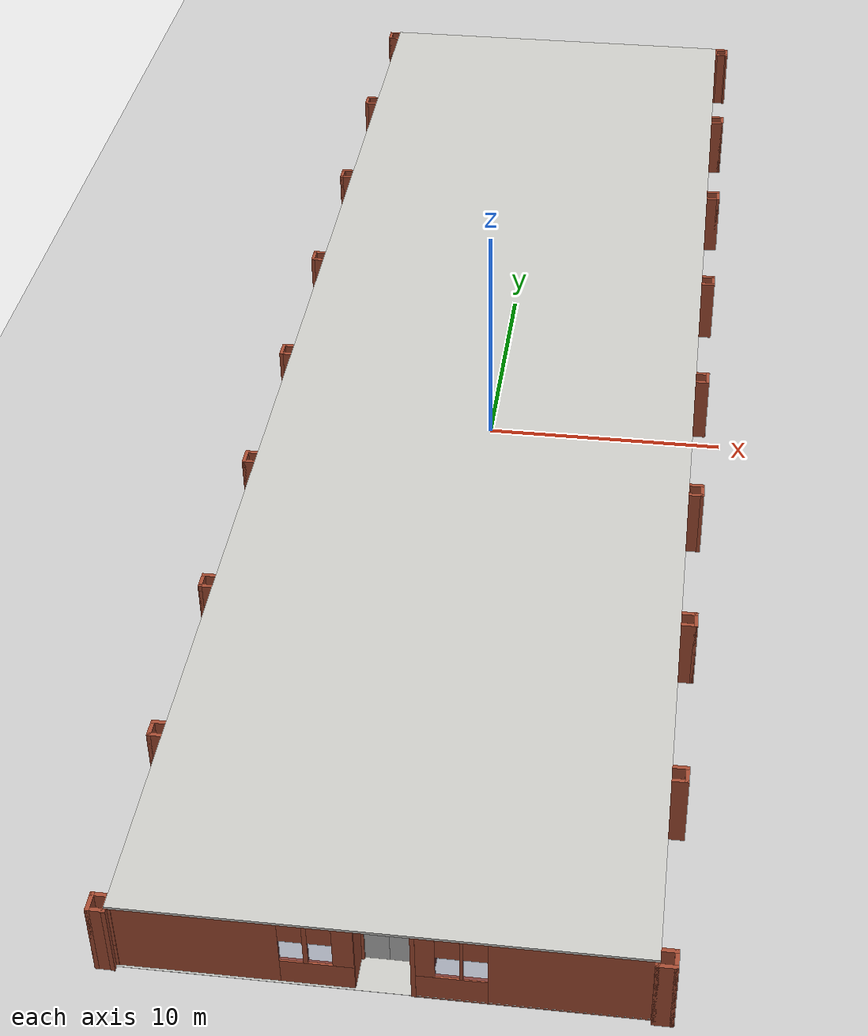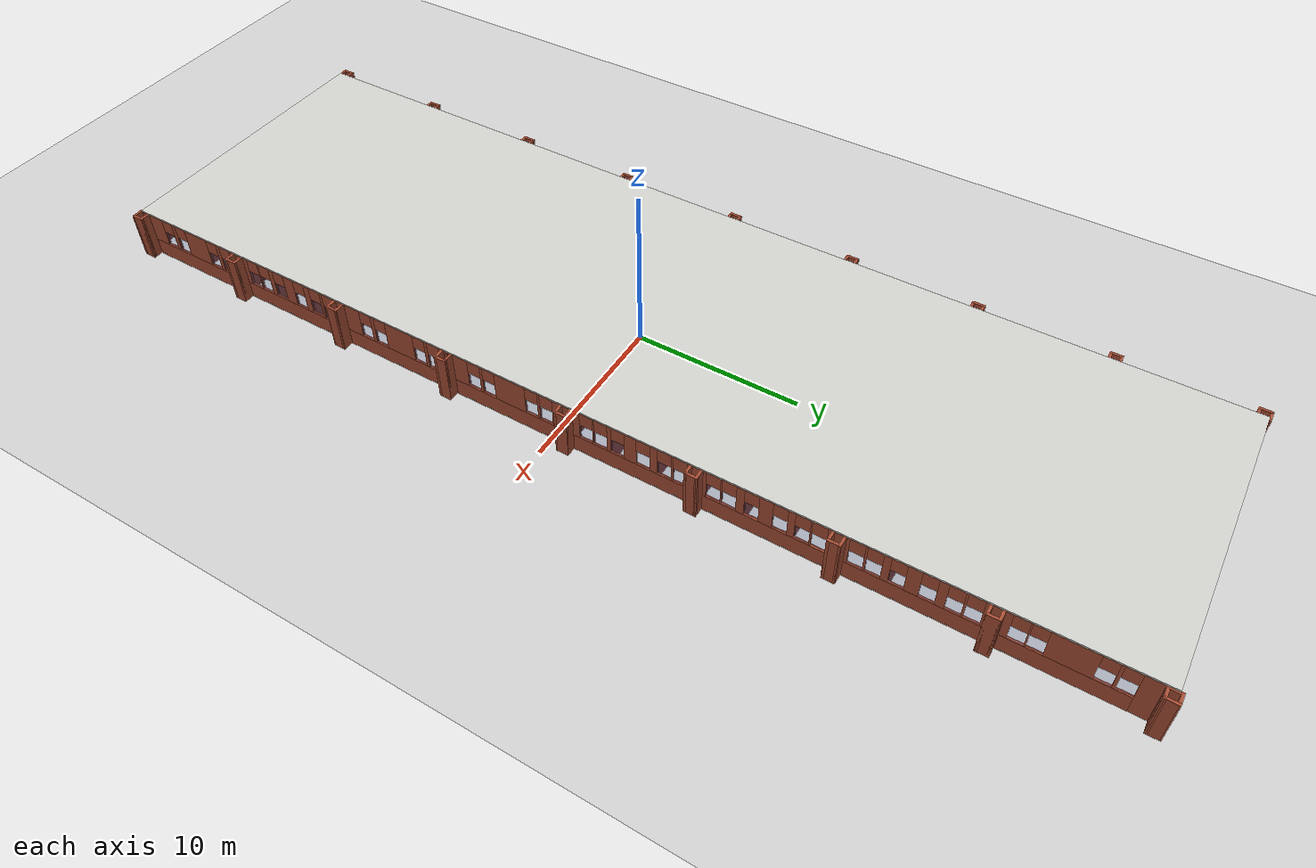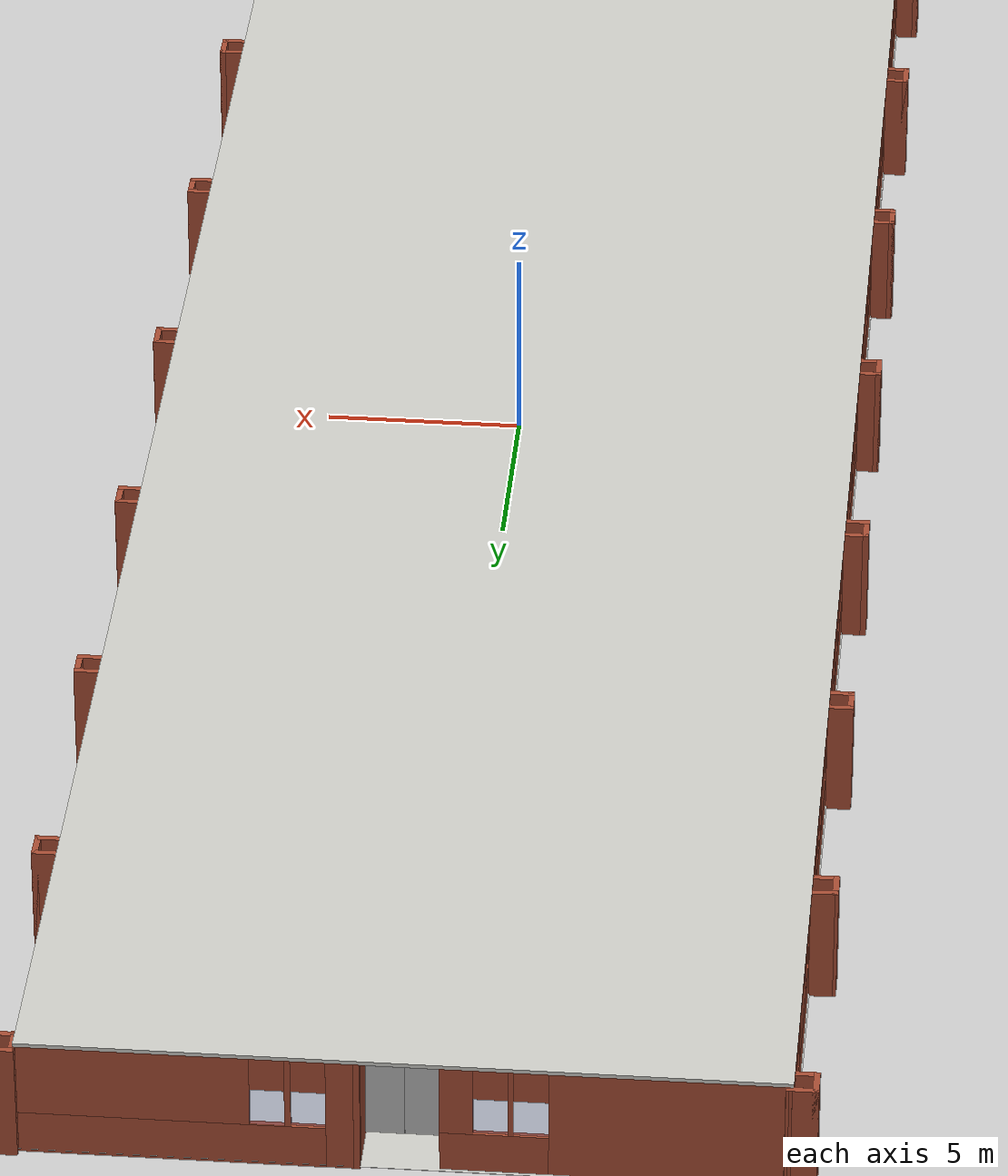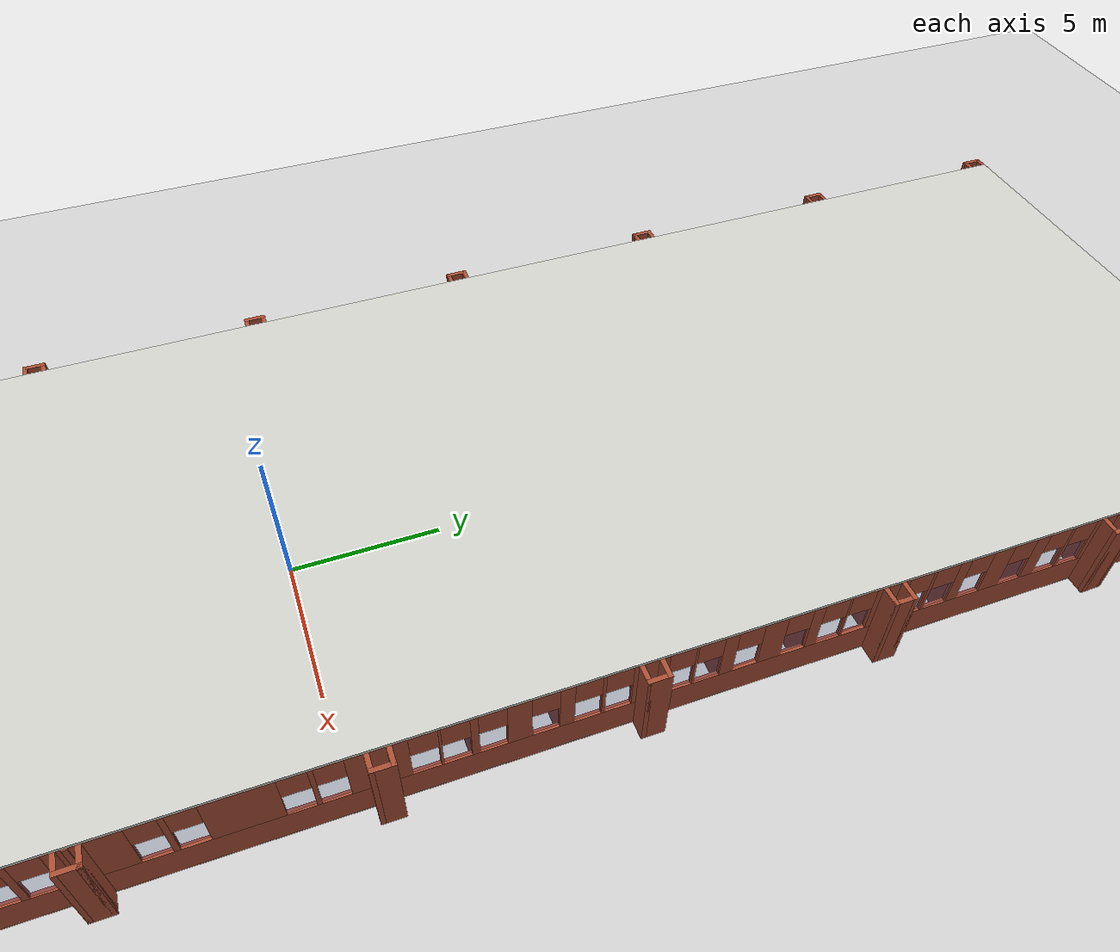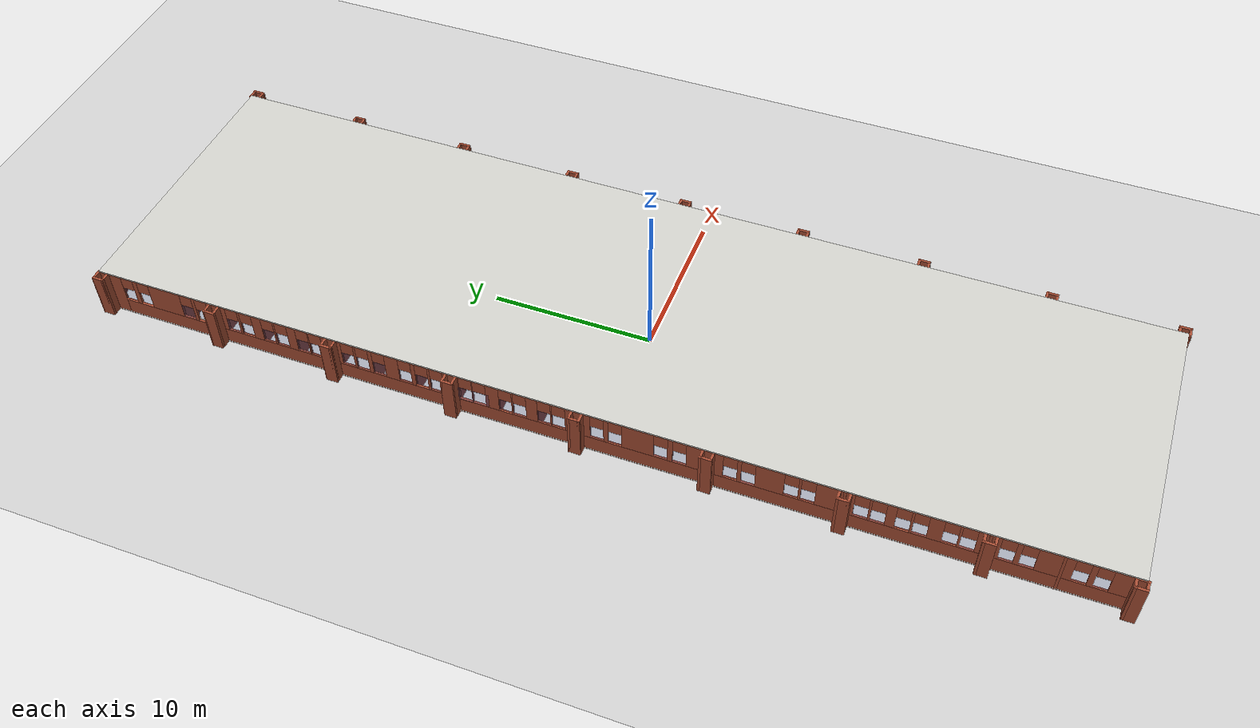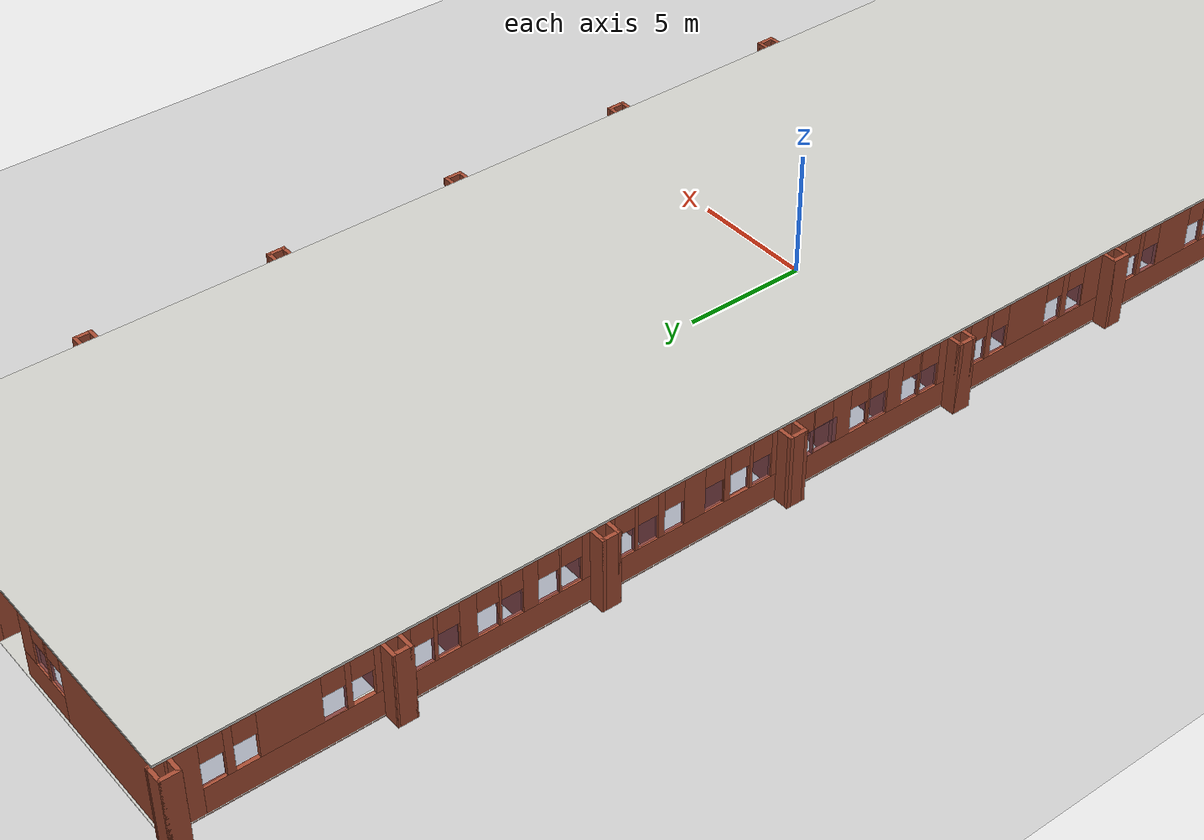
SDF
<sdf version="1.6">
 <world name="default">
  <scene>
   <sky><clouds><speed>12</speed></clouds></sky>
   <ambient>0.4 0.4 0.4 1</ambient>
   <background>0.25 0.25 0.25 1</background>
   <shadows>0</shadows>
  </scene>
  <light name="sun" type="directional">
   <pose>0 0 10 0 -0 0</pose>
   <diffuse>0.8 0.8 0.8 1</diffuse>
   <specular>0.2 0.2 0.2 1</specular>
   <attenuation>
    <range>1000</range>
    <constant>0.9</constant>
    <linear>0.01</linear>
    <quadratic>0.001</quadratic>
   </attenuation>
   <direction>-0.5 0.1 -0.9</direction>
  </light>
  <light name="some_light" type="directional">
   <diffuse>0.7 0.7 0.7 0</diffuse>
   <specular>1 1 1 0</specular>
   <direction>-1 -1 -1</direction>
  </light>
  <model name="ground_plane">
   <static>1</static>
   <link name="link">
    <collision name="collision">
     <geometry><plane><normal>0 0 1</normal><size>100 100</size></plane></geometry>
     <surface><friction><ode><mu>100</mu><mu2>50</mu2></ode></friction></surface>
    </collision>
    <visual name="visual">
     <cast_shadows>0</cast_shadows>
     <geometry><plane><normal>0 0 1</normal><size>100 100</size></plane></geometry>
     <material>
      <script><uri>file://media/materials/scripts/gazebo.material</uri><name>Gazebo/Grey</name></script>
     </material>
    </visual>
   </link>
  </model>
  <gravity>0 0 -9.8</gravity>
  <magnetic_field>6e-06 2.3e-05 -4.2e-05</magnetic_field>
  <atmosphere type="adiabatic"/>
  <physics name="default_physics" default="0" type="ode">
   <max_step_size>0.001</max_step_size>
   <real_time_factor>1</real_time_factor>
   <real_time_update_rate>1000</real_time_update_rate>
  </physics>
  <audio><device>default</device></audio>
  <spherical_coordinates>
   <surface_model>EARTH_WGS84</surface_model>
   <latitude_deg>0</latitude_deg>
   <longitude_deg>0</longitude_deg>
   <elevation>0</elevation>
   <heading_deg>0</heading_deg>
  </spherical_coordinates>
  <model name="UNFRGS_INF_-_Predio_73">
   <pose>-0.02513 1.0401 -0.009 0 -0 0</pose>
   <link name="Floor_5">
    <collision name="Floor_5_Collision">
     <geometry><box><size>17.7211 61.521 0.1</size></box></geometry>
     <pose>0 0 0.05 0 -0 0</pose>
    </collision>
    <visual name="Floor_5_Visual">
     <pose>0 0 0.05 0 -0 0</pose>
     <geometry><box><size>17.7211 61.521 0.01</size></box></geometry>
     <material>
      <script><uri>file://media/materials/scripts/gazebo.material</uri><name>Gazebo/CeilingTiled</name></script>
      <ambient>1 1 1 1</ambient>
     </material>
     <meta><layer>1</layer></meta>
    </visual>
    <pose>-0.017589 -0.005714 0.01 0 -0 0</pose>
   </link>
   <link name="Floor_6">
    <collision name="Floor_6_Collision">
     <geometry><box><size>17.7211 61.521 0.1</size></box></geometry>
     <pose>0 0 0.05 0 -0 0</pose>
    </collision>
    <visual name="Floor_6_Visual">
     <pose>0 0 0.05 0 -0 0</pose>
     <geometry><box><size>17.7211 61.521 0.1</size></box></geometry>
     <material>
      <script><uri>file://media/materials/scripts/gazebo.material</uri><name>Gazebo/CeilingTiled</name></script>
      <ambient>1 1 1 1</ambient>
     </material>
     <meta><layer>1</layer></meta>
    </visual>
    <pose>-0.017589 -0.005714 2.96 0 -0 0</pose>
   </link>
   <link name="Wall_0">
    <pose>8.76787 -0.005219 0 0 0 -1.5708</pose>
    <visual name="Wall_0_Visual_0">
     <pose>-30.019 0 1.48 0 -0 0</pose>
     <geometry><box><size>1.47999 0.15 2.96</size></box></geometry>
     <material>
      <script><uri>file://media/materials/scripts/gazebo.material</uri><name>Gazebo/Bricks</name></script>
      <ambient>0.929412 1 0.760784 1</ambient>
     </material>
     <meta><layer>0</layer></meta>
    </visual>
    <collision name="Wall_0_Collision_0">
     <geometry><box><size>1.47999 0.15 2.96</size></box></geometry>
     <pose>-30.019 0 1.48 0 -0 0</pose>
    </collision>
    <visual name="Wall_0_Visual_1">
     <pose>0.739993 0 0.55 0 -0 0</pose>
     <geometry><box><size>60.038 0.15 1.11</size></box></geometry>
     <material>
      <script><uri>file://media/materials/scripts/gazebo.material</uri><name>Gazebo/Bricks</name></script>
      <ambient>0.929412 1 0.760784 1</ambient>
     </material>
     <meta><layer>0</layer></meta>
    </visual>
    <collision name="Wall_0_Collision_1">
     <geometry><box><size>60.038 0.15 1.11</size></box></geometry>
     <pose>0.739993 0 0.55 0 -0 0</pose>
    </collision>
    <visual name="Wall_0_Visual_2">
     <pose>-28.3968 0 2.03 0 -0 0</pose>
     <geometry><box><size>0.164493 0.15 1.86</size></box></geometry>
     <material>
      <script><uri>file://media/materials/scripts/gazebo.material</uri><name>Gazebo/Bricks</name></script>
      <ambient>0.929412 1 0.760784 1</ambient>
     </material>
     <meta><layer>0</layer></meta>
    </visual>
    <collision name="Wall_0_Collision_2">
     <geometry><box><size>0.164493 0.15 1.86</size></box></geometry>
     <pose>-28.3968 0 2.03 0 -0 0</pose>
    </collision>
    <visual name="Wall_0_Visual_3">
     <pose>-26.3939 0 2.03 0 -0 0</pose>
     <geometry><box><size>2.24127 0.15 1.86</size></box></geometry>
     <material>
      <script><uri>file://media/materials/scripts/gazebo.material</uri><name>Gazebo/Bricks</name></script>
      <ambient>0.929412 1 0.760784 1</ambient>
     </material>
     <meta><layer>0</layer></meta>
    </visual>
    <collision name="Wall_0_Collision_3">
     <geometry><box><size>2.24127 0.15 1.86</size></box></geometry>
     <pose>-26.3939 0 2.03 0 -0 0</pose>
    </collision>
    <visual name="Wall_0_Visual_4">
     <pose>-24.4354 0 2.03 0 -0 0</pose>
     <geometry><box><size>0.07574 0.15 1.86</size></box></geometry>
     <material>
      <script><uri>file://media/materials/scripts/gazebo.material</uri><name>Gazebo/Bricks</name></script>
      <ambient>0.929412 1 0.760784 1</ambient>
     </material>
     <meta><layer>0</layer></meta>
    </visual>
    <collision name="Wall_0_Collision_4">
     <geometry><box><size>0.07574 0.15 1.86</size></box></geometry>
     <pose>-24.4354 0 2.03 0 -0 0</pose>
    </collision>
    <visual name="Wall_0_Visual_5">
     <pose>-22.9721 0 2.03 0 -0 0</pose>
     <geometry><box><size>1.25079 0.15 1.86</size></box></geometry>
     <material>
      <script><uri>file://media/materials/scripts/gazebo.material</uri><name>Gazebo/Bricks</name></script>
      <ambient>0.929412 1 0.760784 1</ambient>
     </material>
     <meta><layer>0</layer></meta>
    </visual>
    <collision name="Wall_0_Collision_5">
     <geometry><box><size>1.25079 0.15 1.86</size></box></geometry>
     <pose>-22.9721 0 2.03 0 -0 0</pose>
    </collision>
    <visual name="Wall_0_Visual_6">
     <pose>-21.4946 0 2.03 0 -0 0</pose>
     <geometry><box><size>0.104211 0.15 1.86</size></box></geometry>
     <material>
      <script><uri>file://media/materials/scripts/gazebo.material</uri><name>Gazebo/Bricks</name></script>
      <ambient>0.929412 1 0.760784 1</ambient>
     </material>
     <meta><layer>0</layer></meta>
    </visual>
    <collision name="Wall_0_Collision_6">
     <geometry><box><size>0.104211 0.15 1.86</size></box></geometry>
     <pose>-21.4946 0 2.03 0 -0 0</pose>
    </collision>
    <visual name="Wall_0_Visual_7">
     <pose>-20.4096 0 2.03 0 -0 0</pose>
     <geometry><box><size>0.465896 0.15 1.86</size></box></geometry>
     <material>
      <script><uri>file://media/materials/scripts/gazebo.material</uri><name>Gazebo/Bricks</name></script>
      <ambient>0.929412 1 0.760784 1</ambient>
     </material>
     <meta><layer>0</layer></meta>
    </visual>
    <collision name="Wall_0_Collision_7">
     <geometry><box><size>0.465896 0.15 1.86</size></box></geometry>
     <pose>-20.4096 0 2.03 0 -0 0</pose>
    </collision>
    <visual name="Wall_0_Visual_8">
     <pose>-19.0231 0 2.03 0 -0 0</pose>
     <geometry><box><size>0.707017 0.15 1.86</size></box></geometry>
     <material>
      <script><uri>file://media/materials/scripts/gazebo.material</uri><name>Gazebo/Bricks</name></script>
      <ambient>0.929412 1 0.760784 1</ambient>
     </material>
     <meta><layer>0</layer></meta>
    </visual>
    <collision name="Wall_0_Collision_8">
     <geometry><box><size>0.707017 0.15 1.86</size></box></geometry>
     <pose>-19.0231 0 2.03 0 -0 0</pose>
    </collision>
    <visual name="Wall_0_Visual_9">
     <pose>-17.6819 0 2.03 0 -0 0</pose>
     <geometry><box><size>0.375476 0.15 1.86</size></box></geometry>
     <material>
      <script><uri>file://media/materials/scripts/gazebo.material</uri><name>Gazebo/Bricks</name></script>
      <ambient>0.929412 1 0.760784 1</ambient>
     </material>
     <meta><layer>0</layer></meta>
    </visual>
    <collision name="Wall_0_Collision_9">
     <geometry><box><size>0.375476 0.15 1.86</size></box></geometry>
     <pose>-17.6819 0 2.03 0 -0 0</pose>
    </collision>
    <visual name="Wall_0_Visual_10">
     <pose>-16.642 0 2.03 0 -0 0</pose>
     <geometry><box><size>0.104211 0.15 1.86</size></box></geometry>
     <material>
      <script><uri>file://media/materials/scripts/gazebo.material</uri><name>Gazebo/Bricks</name></script>
      <ambient>0.929412 1 0.760784 1</ambient>
     </material>
     <meta><layer>0</layer></meta>
    </visual>
    <collision name="Wall_0_Collision_10">
     <geometry><box><size>0.104211 0.15 1.86</size></box></geometry>
     <pose>-16.642 0 2.03 0 -0 0</pose>
    </collision>
    <visual name="Wall_0_Visual_11">
     <pose>-15.2405 0 2.03 0 -0 0</pose>
     <geometry><box><size>1.09884 0.15 1.86</size></box></geometry>
     <material>
      <script><uri>file://media/materials/scripts/gazebo.material</uri><name>Gazebo/Bricks</name></script>
      <ambient>0.929412 1 0.760784 1</ambient>
     </material>
     <meta><layer>0</layer></meta>
    </visual>
    <collision name="Wall_0_Collision_11">
     <geometry><box><size>1.09884 0.15 1.86</size></box></geometry>
     <pose>-15.2405 0 2.03 0 -0 0</pose>
    </collision>
    <visual name="Wall_0_Visual_12">
     <pose>-13.854 0 2.03 0 -0 0</pose>
     <geometry><box><size>0.07407 0.15 1.86</size></box></geometry>
     <material>
      <script><uri>file://media/materials/scripts/gazebo.material</uri><name>Gazebo/Bricks</name></script>
      <ambient>0.929412 1 0.760784 1</ambient>
     </material>
     <meta><layer>0</layer></meta>
    </visual>
    <collision name="Wall_0_Collision_12">
     <geometry><box><size>0.07407 0.15 1.86</size></box></geometry>
     <pose>-13.854 0 2.03 0 -0 0</pose>
    </collision>
    <visual name="Wall_0_Visual_13">
     <pose>-12.8293 0 2.03 0 -0 0</pose>
     <geometry><box><size>0.375475 0.15 1.86</size></box></geometry>
     <material>
      <script><uri>file://media/materials/scripts/gazebo.material</uri><name>Gazebo/Bricks</name></script>
      <ambient>0.929412 1 0.760784 1</ambient>
     </material>
     <meta><layer>0</layer></meta>
    </visual>
    <collision name="Wall_0_Collision_13">
     <geometry><box><size>0.375475 0.15 1.86</size></box></geometry>
     <pose>-12.8293 0 2.03 0 -0 0</pose>
    </collision>
    <visual name="Wall_0_Visual_14">
     <pose>-11.4729 0 2.03 0 -0 0</pose>
     <geometry><box><size>0.737159 0.15 1.86</size></box></geometry>
     <material>
      <script><uri>file://media/materials/scripts/gazebo.material</uri><name>Gazebo/Bricks</name></script>
      <ambient>0.929412 1 0.760784 1</ambient>
     </material>
     <meta><layer>0</layer></meta>
    </visual>
    <collision name="Wall_0_Collision_14">
     <geometry><box><size>0.737159 0.15 1.86</size></box></geometry>
     <pose>-11.4729 0 2.03 0 -0 0</pose>
    </collision>
    <visual name="Wall_0_Visual_15">
     <pose>-10.0865 0 2.03 0 -0 0</pose>
     <geometry><box><size>0.435756 0.15 1.86</size></box></geometry>
     <material>
      <script><uri>file://media/materials/scripts/gazebo.material</uri><name>Gazebo/Bricks</name></script>
      <ambient>0.929412 1 0.760784 1</ambient>
     </material>
     <meta><layer>0</layer></meta>
    </visual>
    <collision name="Wall_0_Collision_15">
     <geometry><box><size>0.435756 0.15 1.86</size></box></geometry>
     <pose>-10.0865 0 2.03 0 -0 0</pose>
    </collision>
    <visual name="Wall_0_Visual_16">
     <pose>-9.03157 0 2.03 0 -0 0</pose>
     <geometry><box><size>0.07407 0.15 1.86</size></box></geometry>
     <material>
      <script><uri>file://media/materials/scripts/gazebo.material</uri><name>Gazebo/Bricks</name></script>
      <ambient>0.929412 1 0.760784 1</ambient>
     </material>
     <meta><layer>0</layer></meta>
    </visual>
    <collision name="Wall_0_Collision_16">
     <geometry><box><size>0.07407 0.15 1.86</size></box></geometry>
     <pose>-9.03157 0 2.03 0 -0 0</pose>
    </collision>
    <visual name="Wall_0_Visual_17">
     <pose>-7.66018 0 2.03 0 -0 0</pose>
     <geometry><box><size>1.0687 0.15 1.86</size></box></geometry>
     <material>
      <script><uri>file://media/materials/scripts/gazebo.material</uri><name>Gazebo/Bricks</name></script>
      <ambient>0.929412 1 0.760784 1</ambient>
     </material>
     <meta><layer>0</layer></meta>
    </visual>
    <collision name="Wall_0_Collision_17">
     <geometry><box><size>1.0687 0.15 1.86</size></box></geometry>
     <pose>-7.66018 0 2.03 0 -0 0</pose>
    </collision>
    <visual name="Wall_0_Visual_18">
     <pose>-6.27372 0 2.03 0 -0 0</pose>
     <geometry><box><size>0.104212 0.15 1.86</size></box></geometry>
     <material>
      <script><uri>file://media/materials/scripts/gazebo.material</uri><name>Gazebo/Bricks</name></script>
      <ambient>0.929412 1 0.760784 1</ambient>
     </material>
     <meta><layer>0</layer></meta>
    </visual>
    <collision name="Wall_0_Collision_18">
     <geometry><box><size>0.104212 0.15 1.86</size></box></geometry>
     <pose>-6.27372 0 2.03 0 -0 0</pose>
    </collision>
    <visual name="Wall_0_Visual_19">
     <pose>-5.20374 0 2.03 0 -0 0</pose>
     <geometry><box><size>0.435755 0.15 1.86</size></box></geometry>
     <material>
      <script><uri>file://media/materials/scripts/gazebo.material</uri><name>Gazebo/Bricks</name></script>
      <ambient>0.929412 1 0.760784 1</ambient>
     </material>
     <meta><layer>0</layer></meta>
    </visual>
    <collision name="Wall_0_Collision_19">
     <geometry><box><size>0.435755 0.15 1.86</size></box></geometry>
     <pose>-5.20374 0 2.03 0 -0 0</pose>
    </collision>
    <visual name="Wall_0_Visual_20">
     <pose>-3.83235 0 2.03 0 -0 0</pose>
     <geometry><box><size>0.707019 0.15 1.86</size></box></geometry>
     <material>
      <script><uri>file://media/materials/scripts/gazebo.material</uri><name>Gazebo/Bricks</name></script>
      <ambient>0.929412 1 0.760784 1</ambient>
     </material>
     <meta><layer>0</layer></meta>
    </visual>
    <collision name="Wall_0_Collision_20">
     <geometry><box><size>0.707019 0.15 1.86</size></box></geometry>
     <pose>-3.83235 0 2.03 0 -0 0</pose>
    </collision>
    <visual name="Wall_0_Visual_21">
     <pose>-2.56646 0 2.03 0 -0 0</pose>
     <geometry><box><size>0.224773 0.15 1.86</size></box></geometry>
     <material>
      <script><uri>file://media/materials/scripts/gazebo.material</uri><name>Gazebo/Bricks</name></script>
      <ambient>0.929412 1 0.760784 1</ambient>
     </material>
     <meta><layer>0</layer></meta>
    </visual>
    <collision name="Wall_0_Collision_21">
     <geometry><box><size>0.224773 0.15 1.86</size></box></geometry>
     <pose>-2.56646 0 2.03 0 -0 0</pose>
    </collision>
    <visual name="Wall_0_Visual_22">
     <pose>-1.61704 0 2.03 0 -0 0</pose>
     <geometry><box><size>0.074071 0.15 1.86</size></box></geometry>
     <material>
      <script><uri>file://media/materials/scripts/gazebo.material</uri><name>Gazebo/Bricks</name></script>
      <ambient>0.929412 1 0.760784 1</ambient>
     </material>
     <meta><layer>0</layer></meta>
    </visual>
    <collision name="Wall_0_Collision_22">
     <geometry><box><size>0.074071 0.15 1.86</size></box></geometry>
     <pose>-1.61704 0 2.03 0 -0 0</pose>
    </collision>
    <visual name="Wall_0_Visual_23">
     <pose>0.055756 0 2.03 0 -0 0</pose>
     <geometry><box><size>1.67151 0.15 1.86</size></box></geometry>
     <material>
      <script><uri>file://media/materials/scripts/gazebo.material</uri><name>Gazebo/Bricks</name></script>
      <ambient>0.929412 1 0.760784 1</ambient>
     </material>
     <meta><layer>0</layer></meta>
    </visual>
    <collision name="Wall_0_Collision_23">
     <geometry><box><size>1.67151 0.15 1.86</size></box></geometry>
     <pose>0.055756 0 2.03 0 -0 0</pose>
    </collision>
    <visual name="Wall_0_Visual_24">
     <pose>1.75869 0 2.03 0 -0 0</pose>
     <geometry><box><size>0.134352 0.15 1.86</size></box></geometry>
     <material>
      <script><uri>file://media/materials/scripts/gazebo.material</uri><name>Gazebo/Bricks</name></script>
      <ambient>0.929412 1 0.760784 1</ambient>
     </material>
     <meta><layer>0</layer></meta>
    </visual>
    <collision name="Wall_0_Collision_24">
     <geometry><box><size>0.134352 0.15 1.86</size></box></geometry>
     <pose>1.75869 0 2.03 0 -0 0</pose>
    </collision>
    <visual name="Wall_0_Visual_25">
     <pose>3.59725 0 2.03 0 -0 0</pose>
     <geometry><box><size>1.94277 0.15 1.86</size></box></geometry>
     <material>
      <script><uri>file://media/materials/scripts/gazebo.material</uri><name>Gazebo/Bricks</name></script>
      <ambient>0.929412 1 0.760784 1</ambient>
     </material>
     <meta><layer>0</layer></meta>
    </visual>
    <collision name="Wall_0_Collision_25">
     <geometry><box><size>1.94277 0.15 1.86</size></box></geometry>
     <pose>3.59725 0 2.03 0 -0 0</pose>
    </collision>
    <visual name="Wall_0_Visual_26">
     <pose>5.45088 0 2.03 0 -0 0</pose>
     <geometry><box><size>0.164492 0.15 1.86</size></box></geometry>
     <material>
      <script><uri>file://media/materials/scripts/gazebo.material</uri><name>Gazebo/Bricks</name></script>
      <ambient>0.929412 1 0.760784 1</ambient>
     </material>
     <meta><layer>0</layer></meta>
    </visual>
    <collision name="Wall_0_Collision_26">
     <geometry><box><size>0.164492 0.15 1.86</size></box></geometry>
     <pose>5.45088 0 2.03 0 -0 0</pose>
    </collision>
    <visual name="Wall_0_Visual_27">
     <pose>7.28945 0 2.03 0 -0 0</pose>
     <geometry><box><size>1.91263 0.15 1.86</size></box></geometry>
     <material>
      <script><uri>file://media/materials/scripts/gazebo.material</uri><name>Gazebo/Bricks</name></script>
      <ambient>0.929412 1 0.760784 1</ambient>
     </material>
     <meta><layer>0</layer></meta>
    </visual>
    <collision name="Wall_0_Collision_27">
     <geometry><box><size>1.91263 0.15 1.86</size></box></geometry>
     <pose>7.28945 0 2.03 0 -0 0</pose>
    </collision>
    <visual name="Wall_0_Visual_28">
     <pose>9.14308 0 2.03 0 -0 0</pose>
     <geometry><box><size>0.194632 0.15 1.86</size></box></geometry>
     <material>
      <script><uri>file://media/materials/scripts/gazebo.material</uri><name>Gazebo/Bricks</name></script>
      <ambient>0.929412 1 0.760784 1</ambient>
     </material>
     <meta><layer>0</layer></meta>
    </visual>
    <collision name="Wall_0_Collision_28">
     <geometry><box><size>0.194632 0.15 1.86</size></box></geometry>
     <pose>9.14308 0 2.03 0 -0 0</pose>
    </collision>
    <visual name="Wall_0_Visual_29">
     <pose>10.9967 0 2.03 0 -0 0</pose>
     <geometry><box><size>1.91263 0.15 1.86</size></box></geometry>
     <material>
      <script><uri>file://media/materials/scripts/gazebo.material</uri><name>Gazebo/Bricks</name></script>
      <ambient>0.929412 1 0.760784 1</ambient>
     </material>
     <meta><layer>0</layer></meta>
    </visual>
    <collision name="Wall_0_Collision_29">
     <geometry><box><size>1.91263 0.15 1.86</size></box></geometry>
     <pose>10.9967 0 2.03 0 -0 0</pose>
    </collision>
    <visual name="Wall_0_Visual_30">
     <pose>12.8654 0 2.03 0 -0 0</pose>
     <geometry><box><size>0.224773 0.15 1.86</size></box></geometry>
     <material>
      <script><uri>file://media/materials/scripts/gazebo.material</uri><name>Gazebo/Bricks</name></script>
      <ambient>0.929412 1 0.760784 1</ambient>
     </material>
     <meta><layer>0</layer></meta>
    </visual>
    <collision name="Wall_0_Collision_30">
     <geometry><box><size>0.224773 0.15 1.86</size></box></geometry>
     <pose>12.8654 0 2.03 0 -0 0</pose>
    </collision>
    <visual name="Wall_0_Visual_31">
     <pose>14.7492 0 2.03 0 -0 0</pose>
     <geometry><box><size>1.94277 0.15 1.86</size></box></geometry>
     <material>
      <script><uri>file://media/materials/scripts/gazebo.material</uri><name>Gazebo/Bricks</name></script>
      <ambient>0.929412 1 0.760784 1</ambient>
     </material>
     <meta><layer>0</layer></meta>
    </visual>
    <collision name="Wall_0_Collision_31">
     <geometry><box><size>1.94277 0.15 1.86</size></box></geometry>
     <pose>14.7492 0 2.03 0 -0 0</pose>
    </collision>
    <visual name="Wall_0_Visual_32">
     <pose>16.6028 0 2.03 0 -0 0</pose>
     <geometry><box><size>0.164493 0.15 1.86</size></box></geometry>
     <material>
      <script><uri>file://media/materials/scripts/gazebo.material</uri><name>Gazebo/Bricks</name></script>
      <ambient>0.929412 1 0.760784 1</ambient>
     </material>
     <meta><layer>0</layer></meta>
    </visual>
    <collision name="Wall_0_Collision_32">
     <geometry><box><size>0.164493 0.15 1.86</size></box></geometry>
     <pose>16.6028 0 2.03 0 -0 0</pose>
    </collision>
    <visual name="Wall_0_Visual_33">
     <pose>17.6879 0 2.03 0 -0 0</pose>
     <geometry><box><size>0.405614 0.15 1.86</size></box></geometry>
     <material>
      <script><uri>file://media/materials/scripts/gazebo.material</uri><name>Gazebo/Bricks</name></script>
      <ambient>0.929412 1 0.760784 1</ambient>
     </material>
     <meta><layer>0</layer></meta>
    </visual>
    <collision name="Wall_0_Collision_33">
     <geometry><box><size>0.405614 0.15 1.86</size></box></geometry>
     <pose>17.6879 0 2.03 0 -0 0</pose>
    </collision>
    <visual name="Wall_0_Visual_34">
     <pose>19.0593 0 2.03 0 -0 0</pose>
     <geometry><box><size>0.737159 0.15 1.86</size></box></geometry>
     <material>
      <script><uri>file://media/materials/scripts/gazebo.material</uri><name>Gazebo/Bricks</name></script>
      <ambient>0.929412 1 0.760784 1</ambient>
     </material>
     <meta><layer>0</layer></meta>
    </visual>
    <collision name="Wall_0_Collision_34">
     <geometry><box><size>0.737159 0.15 1.86</size></box></geometry>
     <pose>19.0593 0 2.03 0 -0 0</pose>
    </collision>
    <visual name="Wall_0_Visual_35">
     <pose>20.3854 0 2.03 0 -0 0</pose>
     <geometry><box><size>0.315194 0.15 1.86</size></box></geometry>
     <material>
      <script><uri>file://media/materials/scripts/gazebo.material</uri><name>Gazebo/Bricks</name></script>
      <ambient>0.929412 1 0.760784 1</ambient>
     </material>
     <meta><layer>0</layer></meta>
    </visual>
    <collision name="Wall_0_Collision_35">
     <geometry><box><size>0.315194 0.15 1.86</size></box></geometry>
     <pose>20.3854 0 2.03 0 -0 0</pose>
    </collision>
    <visual name="Wall_0_Visual_36">
     <pose>21.3801 0 2.03 0 -0 0</pose>
     <geometry><box><size>0.074071 0.15 1.86</size></box></geometry>
     <material>
      <script><uri>file://media/materials/scripts/gazebo.material</uri><name>Gazebo/Bricks</name></script>
      <ambient>0.929412 1 0.760784 1</ambient>
     </material>
     <meta><layer>0</layer></meta>
    </visual>
    <collision name="Wall_0_Collision_36">
     <geometry><box><size>0.074071 0.15 1.86</size></box></geometry>
     <pose>21.3801 0 2.03 0 -0 0</pose>
    </collision>
    <visual name="Wall_0_Visual_37">
     <pose>22.9172 0 2.03 0 -0 0</pose>
     <geometry><box><size>1.40025 0.15 1.86</size></box></geometry>
     <material>
      <script><uri>file://media/materials/scripts/gazebo.material</uri><name>Gazebo/Bricks</name></script>
      <ambient>0.929412 1 0.760784 1</ambient>
     </material>
     <meta><layer>0</layer></meta>
    </visual>
    <collision name="Wall_0_Collision_37">
     <geometry><box><size>1.40025 0.15 1.86</size></box></geometry>
     <pose>22.9172 0 2.03 0 -0 0</pose>
    </collision>
    <visual name="Wall_0_Visual_38">
     <pose>24.5448 0 2.03 0 -0 0</pose>
     <geometry><box><size>0.254914 0.15 1.86</size></box></geometry>
     <material>
      <script><uri>file://media/materials/scripts/gazebo.material</uri><name>Gazebo/Bricks</name></script>
      <ambient>0.929412 1 0.760784 1</ambient>
     </material>
     <meta><layer>0</layer></meta>
    </visual>
    <collision name="Wall_0_Collision_38">
     <geometry><box><size>0.254914 0.15 1.86</size></box></geometry>
     <pose>24.5448 0 2.03 0 -0 0</pose>
    </collision>
    <visual name="Wall_0_Visual_39">
     <pose>26.3532 0 2.03 0 -0 0</pose>
     <geometry><box><size>1.76193 0.15 1.86</size></box></geometry>
     <material>
      <script><uri>file://media/materials/scripts/gazebo.material</uri><name>Gazebo/Bricks</name></script>
      <ambient>0.929412 1 0.760784 1</ambient>
     </material>
     <meta><layer>0</layer></meta>
    </visual>
    <collision name="Wall_0_Collision_39">
     <geometry><box><size>1.76193 0.15 1.86</size></box></geometry>
     <pose>26.3532 0 2.03 0 -0 0</pose>
    </collision>
    <visual name="Wall_0_Visual_40">
     <pose>28.1767 0 2.03 0 -0 0</pose>
     <geometry><box><size>0.285052 0.15 1.86</size></box></geometry>
     <material>
      <script><uri>file://media/materials/scripts/gazebo.material</uri><name>Gazebo/Bricks</name></script>
      <ambient>0.929412 1 0.760784 1</ambient>
     </material>
     <meta><layer>0</layer></meta>
    </visual>
    <collision name="Wall_0_Collision_40">
     <geometry><box><size>0.285052 0.15 1.86</size></box></geometry>
     <pose>28.1767 0 2.03 0 -0 0</pose>
    </collision>
    <visual name="Wall_0_Visual_41">
     <pose>29.9391 0 2.03 0 -0 0</pose>
     <geometry><box><size>1.63974 0.15 1.86</size></box></geometry>
     <material>
      <script><uri>file://media/materials/scripts/gazebo.material</uri><name>Gazebo/Bricks</name></script>
      <ambient>0.929412 1 0.760784 1</ambient>
     </material>
     <meta><layer>0</layer></meta>
    </visual>
    <collision name="Wall_0_Collision_41">
     <geometry><box><size>1.63974 0.15 1.86</size></box></geometry>
     <pose>29.9391 0 2.03 0 -0 0</pose>
    </collision>
    <visual name="Wall_0_Visual_42">
     <pose>-28.879 0 2.53 0 -0 0</pose>
     <geometry><box><size>0.8 0.15 0.86</size></box></geometry>
     <material>
      <script><uri>file://media/materials/scripts/gazebo.material</uri><name>Gazebo/Bricks</name></script>
      <ambient>0.929412 1 0.760784 1</ambient>
     </material>
     <meta><layer>0</layer></meta>
    </visual>
    <collision name="Wall_0_Collision_42">
     <geometry><box><size>0.8 0.15 0.86</size></box></geometry>
     <pose>-28.879 0 2.53 0 -0 0</pose>
    </collision>
    <visual name="Wall_0_Visual_43">
     <pose>-27.9145 0 2.53 0 -0 0</pose>
     <geometry><box><size>0.8 0.15 0.86</size></box></geometry>
     <material>
      <script><uri>file://media/materials/scripts/gazebo.material</uri><name>Gazebo/Bricks</name></script>
      <ambient>0.929412 1 0.760784 1</ambient>
     </material>
     <meta><layer>0</layer></meta>
    </visual>
    <collision name="Wall_0_Collision_43">
     <geometry><box><size>0.8 0.15 0.86</size></box></geometry>
     <pose>-27.9145 0 2.53 0 -0 0</pose>
    </collision>
    <visual name="Wall_0_Visual_44">
     <pose>-24.8732 0 2.53 0 -0 0</pose>
     <geometry><box><size>0.8 0.15 0.86</size></box></geometry>
     <material>
      <script><uri>file://media/materials/scripts/gazebo.material</uri><name>Gazebo/Bricks</name></script>
      <ambient>0.929412 1 0.760784 1</ambient>
     </material>
     <meta><layer>0</layer></meta>
    </visual>
    <collision name="Wall_0_Collision_44">
     <geometry><box><size>0.8 0.15 0.86</size></box></geometry>
     <pose>-24.8732 0 2.53 0 -0 0</pose>
    </collision>
    <visual name="Wall_0_Visual_45">
     <pose>-23.9975 0 2.53 0 -0 0</pose>
     <geometry><box><size>0.8 0.15 0.86</size></box></geometry>
     <material>
      <script><uri>file://media/materials/scripts/gazebo.material</uri><name>Gazebo/Bricks</name></script>
      <ambient>0.929412 1 0.760784 1</ambient>
     </material>
     <meta><layer>0</layer></meta>
    </visual>
    <collision name="Wall_0_Collision_45">
     <geometry><box><size>0.8 0.15 0.86</size></box></geometry>
     <pose>-23.9975 0 2.53 0 -0 0</pose>
    </collision>
    <visual name="Wall_0_Visual_46">
     <pose>-21.9467 0 2.53 0 -0 0</pose>
     <geometry><box><size>0.8 0.15 0.86</size></box></geometry>
     <material>
      <script><uri>file://media/materials/scripts/gazebo.material</uri><name>Gazebo/Bricks</name></script>
      <ambient>0.929412 1 0.760784 1</ambient>
     </material>
     <meta><layer>0</layer></meta>
    </visual>
    <collision name="Wall_0_Collision_46">
     <geometry><box><size>0.8 0.15 0.86</size></box></geometry>
     <pose>-21.9467 0 2.53 0 -0 0</pose>
    </collision>
    <visual name="Wall_0_Visual_47">
     <pose>-21.0425 0 2.53 0 -0 0</pose>
     <geometry><box><size>0.8 0.15 0.86</size></box></geometry>
     <material>
      <script><uri>file://media/materials/scripts/gazebo.material</uri><name>Gazebo/Bricks</name></script>
      <ambient>0.929412 1 0.760784 1</ambient>
     </material>
     <meta><layer>0</layer></meta>
    </visual>
    <collision name="Wall_0_Collision_47">
     <geometry><box><size>0.8 0.15 0.86</size></box></geometry>
     <pose>-21.0425 0 2.53 0 -0 0</pose>
    </collision>
    <visual name="Wall_0_Visual_48">
     <pose>-19.7766 0 2.53 0 -0 0</pose>
     <geometry><box><size>0.8 0.15 0.86</size></box></geometry>
     <material>
      <script><uri>file://media/materials/scripts/gazebo.material</uri><name>Gazebo/Bricks</name></script>
      <ambient>0.929412 1 0.760784 1</ambient>
     </material>
     <meta><layer>0</layer></meta>
    </visual>
    <collision name="Wall_0_Collision_48">
     <geometry><box><size>0.8 0.15 0.86</size></box></geometry>
     <pose>-19.7766 0 2.53 0 -0 0</pose>
    </collision>
    <visual name="Wall_0_Visual_49">
     <pose>-18.2696 0 2.53 0 -0 0</pose>
     <geometry><box><size>0.8 0.15 0.86</size></box></geometry>
     <material>
      <script><uri>file://media/materials/scripts/gazebo.material</uri><name>Gazebo/Bricks</name></script>
      <ambient>0.929412 1 0.760784 1</ambient>
     </material>
     <meta><layer>0</layer></meta>
    </visual>
    <collision name="Wall_0_Collision_49">
     <geometry><box><size>0.8 0.15 0.86</size></box></geometry>
     <pose>-18.2696 0 2.53 0 -0 0</pose>
    </collision>
    <visual name="Wall_0_Visual_50">
     <pose>-17.0941 0 2.53 0 -0 0</pose>
     <geometry><box><size>0.8 0.15 0.86</size></box></geometry>
     <material>
      <script><uri>file://media/materials/scripts/gazebo.material</uri><name>Gazebo/Bricks</name></script>
      <ambient>0.929412 1 0.760784 1</ambient>
     </material>
     <meta><layer>0</layer></meta>
    </visual>
    <collision name="Wall_0_Collision_50">
     <geometry><box><size>0.8 0.15 0.86</size></box></geometry>
     <pose>-17.0941 0 2.53 0 -0 0</pose>
    </collision>
    <visual name="Wall_0_Visual_51">
     <pose>-16.1899 0 2.53 0 -0 0</pose>
     <geometry><box><size>0.8 0.15 0.86</size></box></geometry>
     <material>
      <script><uri>file://media/materials/scripts/gazebo.material</uri><name>Gazebo/Bricks</name></script>
      <ambient>0.929412 1 0.760784 1</ambient>
     </material>
     <meta><layer>0</layer></meta>
    </visual>
    <collision name="Wall_0_Collision_51">
     <geometry><box><size>0.8 0.15 0.86</size></box></geometry>
     <pose>-16.1899 0 2.53 0 -0 0</pose>
    </collision>
    <visual name="Wall_0_Visual_52">
     <pose>-14.2911 0 2.53 0 -0 0</pose>
     <geometry><box><size>0.8 0.15 0.86</size></box></geometry>
     <material>
      <script><uri>file://media/materials/scripts/gazebo.material</uri><name>Gazebo/Bricks</name></script>
      <ambient>0.929412 1 0.760784 1</ambient>
     </material>
     <meta><layer>0</layer></meta>
    </visual>
    <collision name="Wall_0_Collision_52">
     <geometry><box><size>0.8 0.15 0.86</size></box></geometry>
     <pose>-14.2911 0 2.53 0 -0 0</pose>
    </collision>
    <visual name="Wall_0_Visual_53">
     <pose>-13.417 0 2.53 0 -0 0</pose>
     <geometry><box><size>0.8 0.15 0.86</size></box></geometry>
     <material>
      <script><uri>file://media/materials/scripts/gazebo.material</uri><name>Gazebo/Bricks</name></script>
      <ambient>0.929412 1 0.760784 1</ambient>
     </material>
     <meta><layer>0</layer></meta>
    </visual>
    <collision name="Wall_0_Collision_53">
     <geometry><box><size>0.8 0.15 0.86</size></box></geometry>
     <pose>-13.417 0 2.53 0 -0 0</pose>
    </collision>
    <visual name="Wall_0_Visual_54">
     <pose>-12.2415 0 2.53 0 -0 0</pose>
     <geometry><box><size>0.8 0.15 0.86</size></box></geometry>
     <material>
      <script><uri>file://media/materials/scripts/gazebo.material</uri><name>Gazebo/Bricks</name></script>
      <ambient>0.929412 1 0.760784 1</ambient>
     </material>
     <meta><layer>0</layer></meta>
    </visual>
    <collision name="Wall_0_Collision_54">
     <geometry><box><size>0.8 0.15 0.86</size></box></geometry>
     <pose>-12.2415 0 2.53 0 -0 0</pose>
    </collision>
    <visual name="Wall_0_Visual_55">
     <pose>-10.7044 0 2.53 0 -0 0</pose>
     <geometry><box><size>0.8 0.15 0.86</size></box></geometry>
     <material>
      <script><uri>file://media/materials/scripts/gazebo.material</uri><name>Gazebo/Bricks</name></script>
      <ambient>0.929412 1 0.760784 1</ambient>
     </material>
     <meta><layer>0</layer></meta>
    </visual>
    <collision name="Wall_0_Collision_55">
     <geometry><box><size>0.8 0.15 0.86</size></box></geometry>
     <pose>-10.7044 0 2.53 0 -0 0</pose>
    </collision>
    <visual name="Wall_0_Visual_56">
     <pose>-9.4686 0 2.53 0 -0 0</pose>
     <geometry><box><size>0.8 0.15 0.86</size></box></geometry>
     <material>
      <script><uri>file://media/materials/scripts/gazebo.material</uri><name>Gazebo/Bricks</name></script>
      <ambient>0.929412 1 0.760784 1</ambient>
     </material>
     <meta><layer>0</layer></meta>
    </visual>
    <collision name="Wall_0_Collision_56">
     <geometry><box><size>0.8 0.15 0.86</size></box></geometry>
     <pose>-9.4686 0 2.53 0 -0 0</pose>
    </collision>
    <visual name="Wall_0_Visual_57">
     <pose>-8.59453 0 2.53 0 -0 0</pose>
     <geometry><box><size>0.8 0.15 0.86</size></box></geometry>
     <material>
      <script><uri>file://media/materials/scripts/gazebo.material</uri><name>Gazebo/Bricks</name></script>
      <ambient>0.929412 1 0.760784 1</ambient>
     </material>
     <meta><layer>0</layer></meta>
    </visual>
    <collision name="Wall_0_Collision_57">
     <geometry><box><size>0.8 0.15 0.86</size></box></geometry>
     <pose>-8.59453 0 2.53 0 -0 0</pose>
    </collision>
    <visual name="Wall_0_Visual_58">
     <pose>-6.72583 0 2.53 0 -0 0</pose>
     <geometry><box><size>0.8 0.15 0.86</size></box></geometry>
     <material>
      <script><uri>file://media/materials/scripts/gazebo.material</uri><name>Gazebo/Bricks</name></script>
      <ambient>0.929412 1 0.760784 1</ambient>
     </material>
     <meta><layer>0</layer></meta>
    </visual>
    <collision name="Wall_0_Collision_58">
     <geometry><box><size>0.8 0.15 0.86</size></box></geometry>
     <pose>-6.72583 0 2.53 0 -0 0</pose>
    </collision>
    <visual name="Wall_0_Visual_59">
     <pose>-5.82162 0 2.53 0 -0 0</pose>
     <geometry><box><size>0.8 0.15 0.86</size></box></geometry>
     <material>
      <script><uri>file://media/materials/scripts/gazebo.material</uri><name>Gazebo/Bricks</name></script>
      <ambient>0.929412 1 0.760784 1</ambient>
     </material>
     <meta><layer>0</layer></meta>
    </visual>
    <collision name="Wall_0_Collision_59">
     <geometry><box><size>0.8 0.15 0.86</size></box></geometry>
     <pose>-5.82162 0 2.53 0 -0 0</pose>
    </collision>
    <visual name="Wall_0_Visual_60">
     <pose>-4.58586 0 2.53 0 -0 0</pose>
     <geometry><box><size>0.8 0.15 0.86</size></box></geometry>
     <material>
      <script><uri>file://media/materials/scripts/gazebo.material</uri><name>Gazebo/Bricks</name></script>
      <ambient>0.929412 1 0.760784 1</ambient>
     </material>
     <meta><layer>0</layer></meta>
    </visual>
    <collision name="Wall_0_Collision_60">
     <geometry><box><size>0.8 0.15 0.86</size></box></geometry>
     <pose>-4.58586 0 2.53 0 -0 0</pose>
    </collision>
    <visual name="Wall_0_Visual_61">
     <pose>-3.07884 0 2.53 0 -0 0</pose>
     <geometry><box><size>0.8 0.15 0.86</size></box></geometry>
     <material>
      <script><uri>file://media/materials/scripts/gazebo.material</uri><name>Gazebo/Bricks</name></script>
      <ambient>0.929412 1 0.760784 1</ambient>
     </material>
     <meta><layer>0</layer></meta>
    </visual>
    <collision name="Wall_0_Collision_61">
     <geometry><box><size>0.8 0.15 0.86</size></box></geometry>
     <pose>-3.07884 0 2.53 0 -0 0</pose>
    </collision>
    <visual name="Wall_0_Visual_62">
     <pose>-2.05407 0 2.53 0 -0 0</pose>
     <geometry><box><size>0.8 0.15 0.86</size></box></geometry>
     <material>
      <script><uri>file://media/materials/scripts/gazebo.material</uri><name>Gazebo/Bricks</name></script>
      <ambient>0.929412 1 0.760784 1</ambient>
     </material>
     <meta><layer>0</layer></meta>
    </visual>
    <collision name="Wall_0_Collision_62">
     <geometry><box><size>0.8 0.15 0.86</size></box></geometry>
     <pose>-2.05407 0 2.53 0 -0 0</pose>
    </collision>
    <visual name="Wall_0_Visual_63">
     <pose>-1.18 0 2.53 0 -0 0</pose>
     <geometry><box><size>0.8 0.15 0.86</size></box></geometry>
     <material>
      <script><uri>file://media/materials/scripts/gazebo.material</uri><name>Gazebo/Bricks</name></script>
      <ambient>0.929412 1 0.760784 1</ambient>
     </material>
     <meta><layer>0</layer></meta>
    </visual>
    <collision name="Wall_0_Collision_63">
     <geometry><box><size>0.8 0.15 0.86</size></box></geometry>
     <pose>-1.18 0 2.53 0 -0 0</pose>
    </collision>
    <visual name="Wall_0_Visual_64">
     <pose>1.29151 0 2.53 0 -0 0</pose>
     <geometry><box><size>0.8 0.15 0.86</size></box></geometry>
     <material>
      <script><uri>file://media/materials/scripts/gazebo.material</uri><name>Gazebo/Bricks</name></script>
      <ambient>0.929412 1 0.760784 1</ambient>
     </material>
     <meta><layer>0</layer></meta>
    </visual>
    <collision name="Wall_0_Collision_64">
     <geometry><box><size>0.8 0.15 0.86</size></box></geometry>
     <pose>1.29151 0 2.53 0 -0 0</pose>
    </collision>
    <visual name="Wall_0_Visual_65">
     <pose>2.22586 0 2.53 0 -0 0</pose>
     <geometry><box><size>0.8 0.15 0.86</size></box></geometry>
     <material>
      <script><uri>file://media/materials/scripts/gazebo.material</uri><name>Gazebo/Bricks</name></script>
      <ambient>0.929412 1 0.760784 1</ambient>
     </material>
     <meta><layer>0</layer></meta>
    </visual>
    <collision name="Wall_0_Collision_65">
     <geometry><box><size>0.8 0.15 0.86</size></box></geometry>
     <pose>2.22586 0 2.53 0 -0 0</pose>
    </collision>
    <visual name="Wall_0_Visual_66">
     <pose>4.96864 0 2.53 0 -0 0</pose>
     <geometry><box><size>0.8 0.15 0.86</size></box></geometry>
     <material>
      <script><uri>file://media/materials/scripts/gazebo.material</uri><name>Gazebo/Bricks</name></script>
      <ambient>0.929412 1 0.760784 1</ambient>
     </material>
     <meta><layer>0</layer></meta>
    </visual>
    <collision name="Wall_0_Collision_66">
     <geometry><box><size>0.8 0.15 0.86</size></box></geometry>
     <pose>4.96864 0 2.53 0 -0 0</pose>
    </collision>
    <visual name="Wall_0_Visual_67">
     <pose>5.93313 0 2.53 0 -0 0</pose>
     <geometry><box><size>0.8 0.15 0.86</size></box></geometry>
     <material>
      <script><uri>file://media/materials/scripts/gazebo.material</uri><name>Gazebo/Bricks</name></script>
      <ambient>0.929412 1 0.760784 1</ambient>
     </material>
     <meta><layer>0</layer></meta>
    </visual>
    <collision name="Wall_0_Collision_67">
     <geometry><box><size>0.8 0.15 0.86</size></box></geometry>
     <pose>5.93313 0 2.53 0 -0 0</pose>
    </collision>
    <visual name="Wall_0_Visual_68">
     <pose>8.64576 0 2.53 0 -0 0</pose>
     <geometry><box><size>0.8 0.15 0.86</size></box></geometry>
     <material>
      <script><uri>file://media/materials/scripts/gazebo.material</uri><name>Gazebo/Bricks</name></script>
      <ambient>0.929412 1 0.760784 1</ambient>
     </material>
     <meta><layer>0</layer></meta>
    </visual>
    <collision name="Wall_0_Collision_68">
     <geometry><box><size>0.8 0.15 0.86</size></box></geometry>
     <pose>8.64576 0 2.53 0 -0 0</pose>
    </collision>
    <visual name="Wall_0_Visual_69">
     <pose>9.64039 0 2.53 0 -0 0</pose>
     <geometry><box><size>0.8 0.15 0.86</size></box></geometry>
     <material>
      <script><uri>file://media/materials/scripts/gazebo.material</uri><name>Gazebo/Bricks</name></script>
      <ambient>0.929412 1 0.760784 1</ambient>
     </material>
     <meta><layer>0</layer></meta>
    </visual>
    <collision name="Wall_0_Collision_69">
     <geometry><box><size>0.8 0.15 0.86</size></box></geometry>
     <pose>9.64039 0 2.53 0 -0 0</pose>
    </collision>
    <visual name="Wall_0_Visual_70">
     <pose>12.353 0 2.53 0 -0 0</pose>
     <geometry><box><size>0.8 0.15 0.86</size></box></geometry>
     <material>
      <script><uri>file://media/materials/scripts/gazebo.material</uri><name>Gazebo/Bricks</name></script>
      <ambient>0.929412 1 0.760784 1</ambient>
     </material>
     <meta><layer>0</layer></meta>
    </visual>
    <collision name="Wall_0_Collision_70">
     <geometry><box><size>0.8 0.15 0.86</size></box></geometry>
     <pose>12.353 0 2.53 0 -0 0</pose>
    </collision>
    <visual name="Wall_0_Visual_71">
     <pose>13.3778 0 2.53 0 -0 0</pose>
     <geometry><box><size>0.8 0.15 0.86</size></box></geometry>
     <material>
      <script><uri>file://media/materials/scripts/gazebo.material</uri><name>Gazebo/Bricks</name></script>
      <ambient>0.929412 1 0.760784 1</ambient>
     </material>
     <meta><layer>0</layer></meta>
    </visual>
    <collision name="Wall_0_Collision_71">
     <geometry><box><size>0.8 0.15 0.86</size></box></geometry>
     <pose>13.3778 0 2.53 0 -0 0</pose>
    </collision>
    <visual name="Wall_0_Visual_72">
     <pose>16.1206 0 2.53 0 -0 0</pose>
     <geometry><box><size>0.8 0.15 0.86</size></box></geometry>
     <material>
      <script><uri>file://media/materials/scripts/gazebo.material</uri><name>Gazebo/Bricks</name></script>
      <ambient>0.929412 1 0.760784 1</ambient>
     </material>
     <meta><layer>0</layer></meta>
    </visual>
    <collision name="Wall_0_Collision_72">
     <geometry><box><size>0.8 0.15 0.86</size></box></geometry>
     <pose>16.1206 0 2.53 0 -0 0</pose>
    </collision>
    <visual name="Wall_0_Visual_73">
     <pose>17.0851 0 2.53 0 -0 0</pose>
     <geometry><box><size>0.8 0.15 0.86</size></box></geometry>
     <material>
      <script><uri>file://media/materials/scripts/gazebo.material</uri><name>Gazebo/Bricks</name></script>
      <ambient>0.929412 1 0.760784 1</ambient>
     </material>
     <meta><layer>0</layer></meta>
    </visual>
    <collision name="Wall_0_Collision_73">
     <geometry><box><size>0.8 0.15 0.86</size></box></geometry>
     <pose>17.0851 0 2.53 0 -0 0</pose>
    </collision>
    <visual name="Wall_0_Visual_74">
     <pose>18.2907 0 2.53 0 -0 0</pose>
     <geometry><box><size>0.8 0.15 0.86</size></box></geometry>
     <material>
      <script><uri>file://media/materials/scripts/gazebo.material</uri><name>Gazebo/Bricks</name></script>
      <ambient>0.929412 1 0.760784 1</ambient>
     </material>
     <meta><layer>0</layer></meta>
    </visual>
    <collision name="Wall_0_Collision_74">
     <geometry><box><size>0.8 0.15 0.86</size></box></geometry>
     <pose>18.2907 0 2.53 0 -0 0</pose>
    </collision>
    <visual name="Wall_0_Visual_75">
     <pose>19.8278 0 2.53 0 -0 0</pose>
     <geometry><box><size>0.8 0.15 0.86</size></box></geometry>
     <material>
      <script><uri>file://media/materials/scripts/gazebo.material</uri><name>Gazebo/Bricks</name></script>
      <ambient>0.929412 1 0.760784 1</ambient>
     </material>
     <meta><layer>0</layer></meta>
    </visual>
    <collision name="Wall_0_Collision_75">
     <geometry><box><size>0.8 0.15 0.86</size></box></geometry>
     <pose>19.8278 0 2.53 0 -0 0</pose>
    </collision>
    <visual name="Wall_0_Visual_76">
     <pose>20.943 0 2.53 0 -0 0</pose>
     <geometry><box><size>0.8 0.15 0.86</size></box></geometry>
     <material>
      <script><uri>file://media/materials/scripts/gazebo.material</uri><name>Gazebo/Bricks</name></script>
      <ambient>0.929412 1 0.760784 1</ambient>
     </material>
     <meta><layer>0</layer></meta>
    </visual>
    <collision name="Wall_0_Collision_76">
     <geometry><box><size>0.8 0.15 0.86</size></box></geometry>
     <pose>20.943 0 2.53 0 -0 0</pose>
    </collision>
    <visual name="Wall_0_Visual_77">
     <pose>21.8171 0 2.53 0 -0 0</pose>
     <geometry><box><size>0.8 0.15 0.86</size></box></geometry>
     <material>
      <script><uri>file://media/materials/scripts/gazebo.material</uri><name>Gazebo/Bricks</name></script>
      <ambient>0.929412 1 0.760784 1</ambient>
     </material>
     <meta><layer>0</layer></meta>
    </visual>
    <collision name="Wall_0_Collision_77">
     <geometry><box><size>0.8 0.15 0.86</size></box></geometry>
     <pose>21.8171 0 2.53 0 -0 0</pose>
    </collision>
    <visual name="Wall_0_Visual_78">
     <pose>24.0174 0 2.53 0 -0 0</pose>
     <geometry><box><size>0.8 0.15 0.86</size></box></geometry>
     <material>
      <script><uri>file://media/materials/scripts/gazebo.material</uri><name>Gazebo/Bricks</name></script>
      <ambient>0.929412 1 0.760784 1</ambient>
     </material>
     <meta><layer>0</layer></meta>
    </visual>
    <collision name="Wall_0_Collision_78">
     <geometry><box><size>0.8 0.15 0.86</size></box></geometry>
     <pose>24.0174 0 2.53 0 -0 0</pose>
    </collision>
    <visual name="Wall_0_Visual_79">
     <pose>25.0723 0 2.53 0 -0 0</pose>
     <geometry><box><size>0.8 0.15 0.86</size></box></geometry>
     <material>
      <script><uri>file://media/materials/scripts/gazebo.material</uri><name>Gazebo/Bricks</name></script>
      <ambient>0.929412 1 0.760784 1</ambient>
     </material>
     <meta><layer>0</layer></meta>
    </visual>
    <collision name="Wall_0_Collision_79">
     <geometry><box><size>0.8 0.15 0.86</size></box></geometry>
     <pose>25.0723 0 2.53 0 -0 0</pose>
    </collision>
    <visual name="Wall_0_Visual_80">
     <pose>27.6342 0 2.53 0 -0 0</pose>
     <geometry><box><size>0.8 0.15 0.86</size></box></geometry>
     <material>
      <script><uri>file://media/materials/scripts/gazebo.material</uri><name>Gazebo/Bricks</name></script>
      <ambient>0.929412 1 0.760784 1</ambient>
     </material>
     <meta><layer>0</layer></meta>
    </visual>
    <collision name="Wall_0_Collision_80">
     <geometry><box><size>0.8 0.15 0.86</size></box></geometry>
     <pose>27.6342 0 2.53 0 -0 0</pose>
    </collision>
    <visual name="Wall_0_Visual_81">
     <pose>28.7193 0 2.53 0 -0 0</pose>
     <geometry><box><size>0.8 0.15 0.86</size></box></geometry>
     <material>
      <script><uri>file://media/materials/scripts/gazebo.material</uri><name>Gazebo/Bricks</name></script>
      <ambient>0.929412 1 0.760784 1</ambient>
     </material>
     <meta><layer>0</layer></meta>
    </visual>
    <collision name="Wall_0_Collision_81">
     <geometry><box><size>0.8 0.15 0.86</size></box></geometry>
     <pose>28.7193 0 2.53 0 -0 0</pose>
    </collision>
   </link>
   <link name="Wall_101">
    <collision name="Wall_101_Collision">
     <geometry><box><size>1.5 0.15 2.96</size></box></geometry>
     <pose>0 0 1.48 0 -0 0</pose>
    </collision>
    <visual name="Wall_101_Visual">
     <pose>0 0 1.48 0 -0 0</pose>
     <geometry><box><size>1.5 0.15 2.96</size></box></geometry>
     <material>
      <script><uri>file://media/materials/scripts/gazebo.material</uri><name>Gazebo/Bricks</name></script>
      <ambient>0.929412 1 0.760784 1</ambient>
     </material>
     <meta><layer>0</layer></meta>
    </visual>
    <pose>-2.61913 22.8618 0 0 0 -1.5708</pose>
   </link>
   <link name="Wall_103">
    <collision name="Wall_103_Collision">
     <geometry><box><size>1.5 0.15 2.96</size></box></geometry>
     <pose>0 0 1.48 0 -0 0</pose>
    </collision>
    <visual name="Wall_103_Visual">
     <pose>0 0 1.48 0 -0 0</pose>
     <geometry><box><size>1.5 0.15 2.96</size></box></geometry>
     <material>
      <script><uri>file://media/materials/scripts/gazebo.material</uri><name>Gazebo/Bricks</name></script>
      <ambient>0.929412 1 0.760784 1</ambient>
     </material>
     <meta><layer>0</layer></meta>
    </visual>
    <pose>2.64587 22.8868 0 0 0 -1.5708</pose>
   </link>
   <link name="Wall_105">
    <collision name="Wall_105_Collision">
     <geometry><box><size>3.75 0.15 2.96</size></box></geometry>
     <pose>0 0 1.48 0 -0 0</pose>
    </collision>
    <visual name="Wall_105_Visual">
     <pose>0 0 1.48 0 -0 0</pose>
     <geometry><box><size>3.75 0.15 2.96</size></box></geometry>
     <material>
      <script><uri>file://media/materials/scripts/gazebo.material</uri><name>Gazebo/Bricks</name></script>
      <ambient>0.929412 1 0.760784 1</ambient>
     </material>
     <meta><layer>0</layer></meta>
    </visual>
    <pose>-6.88513 17.7738 0 0 -0 0</pose>
   </link>
   <link name="Wall_108">
    <collision name="Wall_108_Collision">
     <geometry><box><size>3.75 0.15 2.96</size></box></geometry>
     <pose>0 0 1.48 0 -0 0</pose>
    </collision>
    <visual name="Wall_108_Visual">
     <pose>0 0 1.48 0 -0 0</pose>
     <geometry><box><size>3.75 0.15 2.96</size></box></geometry>
     <material>
      <script><uri>file://media/materials/scripts/gazebo.material</uri><name>Gazebo/Bricks</name></script>
      <ambient>0.929412 1 0.760784 1</ambient>
     </material>
     <meta><layer>0</layer></meta>
    </visual>
    <pose>6.83287 20.3518 0 0 -0 0</pose>
   </link>
   <link name="Wall_110">
    <collision name="Wall_110_Collision">
     <geometry><box><size>3.75 0.15 2.96</size></box></geometry>
     <pose>0 0 1.48 0 -0 0</pose>
    </collision>
    <visual name="Wall_110_Visual">
     <pose>0 0 1.48 0 -0 0</pose>
     <geometry><box><size>3.75 0.15 2.96</size></box></geometry>
     <material>
      <script><uri>file://media/materials/scripts/gazebo.material</uri><name>Gazebo/Bricks</name></script>
      <ambient>0.929412 1 0.760784 1</ambient>
     </material>
     <meta><layer>0</layer></meta>
    </visual>
    <pose>-6.88513 15.1948 0 0 -0 0</pose>
   </link>
   <link name="Wall_112">
    <collision name="Wall_112_Collision">
     <geometry><box><size>3.75 0.15 2.96</size></box></geometry>
     <pose>0 0 1.48 0 -0 0</pose>
    </collision>
    <visual name="Wall_112_Visual">
     <pose>0 0 1.48 0 -0 0</pose>
     <geometry><box><size>3.75 0.15 2.96</size></box></geometry>
     <material>
      <script><uri>file://media/materials/scripts/gazebo.material</uri><name>Gazebo/Bricks</name></script>
      <ambient>0.929412 1 0.760784 1</ambient>
     </material>
     <meta><layer>0</layer></meta>
    </visual>
    <pose>6.85987 15.2218 0 0 -0 0</pose>
   </link>
   <link name="Wall_114">
    <collision name="Wall_114_Collision">
     <geometry><box><size>1.25 0.15 2.96</size></box></geometry>
     <pose>0 0 1.48 0 -0 0</pose>
    </collision>
    <visual name="Wall_114_Visual">
     <pose>0 0 1.48 0 -0 0</pose>
     <geometry><box><size>1.25 0.15 2.96</size></box></geometry>
     <material>
      <script><uri>file://media/materials/scripts/gazebo.material</uri><name>Gazebo/Bricks</name></script>
      <ambient>0.929412 1 0.760784 1</ambient>
     </material>
     <meta><layer>0</layer></meta>
    </visual>
    <pose>-4.87113 15.2208 0 0 0 -1.5708</pose>
   </link>
   <link name="Wall_116">
    <collision name="Wall_116_Collision">
     <geometry><box><size>1.5 0.15 2.96</size></box></geometry>
     <pose>0 0 1.48 0 -0 0</pose>
    </collision>
    <visual name="Wall_116_Visual">
     <pose>0 0 1.48 0 -0 0</pose>
     <geometry><box><size>1.5 0.15 2.96</size></box></geometry>
     <material>
      <script><uri>file://media/materials/scripts/gazebo.material</uri><name>Gazebo/Bricks</name></script>
      <ambient>0.929412 1 0.760784 1</ambient>
     </material>
     <meta><layer>0</layer></meta>
    </visual>
    <pose>-2.62213 15.2058 0 0 0 -1.5708</pose>
   </link>
   <link name="Wall_118">
    <collision name="Wall_118_Collision">
     <geometry><box><size>1.5 0.15 2.96</size></box></geometry>
     <pose>0 0 1.48 0 -0 0</pose>
    </collision>
    <visual name="Wall_118_Visual">
     <pose>0 0 1.48 0 -0 0</pose>
     <geometry><box><size>1.5 0.15 2.96</size></box></geometry>
     <material>
      <script><uri>file://media/materials/scripts/gazebo.material</uri><name>Gazebo/Bricks</name></script>
      <ambient>0.929412 1 0.760784 1</ambient>
     </material>
     <meta><layer>0</layer></meta>
    </visual>
    <pose>2.61787 15.2302 0 0 0 -1.5708</pose>
   </link>
   <link name="Wall_120">
    <collision name="Wall_120_Collision">
     <geometry><box><size>1.5 0.15 2.96</size></box></geometry>
     <pose>0 0 1.48 0 -0 0</pose>
    </collision>
    <visual name="Wall_120_Visual">
     <pose>0 0 1.48 0 -0 0</pose>
     <geometry><box><size>1.5 0.15 2.96</size></box></geometry>
     <material>
      <script><uri>file://media/materials/scripts/gazebo.material</uri><name>Gazebo/Bricks</name></script>
      <ambient>0.929412 1 0.760784 1</ambient>
     </material>
     <meta><layer>0</layer></meta>
    </visual>
    <pose>4.84087 15.1778 0 0 0 -1.5708</pose>
   </link>
   <link name="Wall_122">
    <collision name="Wall_122_Collision">
     <geometry><box><size>3.75 0.15 2.96</size></box></geometry>
     <pose>0 0 1.48 0 -0 0</pose>
    </collision>
    <visual name="Wall_122_Visual">
     <pose>0 0 1.48 0 -0 0</pose>
     <geometry><box><size>3.75 0.15 2.96</size></box></geometry>
     <material>
      <script><uri>file://media/materials/scripts/gazebo.material</uri><name>Gazebo/Bricks</name></script>
      <ambient>0.929412 1 0.760784 1</ambient>
     </material>
     <meta><layer>0</layer></meta>
    </visual>
    <pose>6.83287 12.6978 0 0 -0 0</pose>
   </link>
   <link name="Wall_124">
    <collision name="Wall_124_Collision">
     <geometry><box><size>3.75 0.15 2.96</size></box></geometry>
     <pose>0 0 1.48 0 -0 0</pose>
    </collision>
    <visual name="Wall_124_Visual">
     <pose>0 0 1.48 0 -0 0</pose>
     <geometry><box><size>3.75 0.15 2.96</size></box></geometry>
     <material>
      <script><uri>file://media/materials/scripts/gazebo.material</uri><name>Gazebo/Bricks</name></script>
      <ambient>0.929412 1 0.760784 1</ambient>
     </material>
     <meta><layer>0</layer></meta>
    </visual>
    <pose>-6.88513 12.6978 0 0 -0 0</pose>
   </link>
   <link name="Wall_126">
    <collision name="Wall_126_Collision">
     <geometry><box><size>3.75 0.15 2.96</size></box></geometry>
     <pose>0 0 1.48 0 -0 0</pose>
    </collision>
    <visual name="Wall_126_Visual">
     <pose>0 0 1.48 0 -0 0</pose>
     <geometry><box><size>3.75 0.15 2.96</size></box></geometry>
     <material>
      <script><uri>file://media/materials/scripts/gazebo.material</uri><name>Gazebo/Bricks</name></script>
      <ambient>0.929412 1 0.760784 1</ambient>
     </material>
     <meta><layer>0</layer></meta>
    </visual>
    <pose>6.85987 10.1188 0 0 -0 0</pose>
   </link>
   <link name="Wall_128">
    <collision name="Wall_128_Collision">
     <geometry><box><size>3.75 0.15 2.96</size></box></geometry>
     <pose>0 0 1.48 0 -0 0</pose>
    </collision>
    <visual name="Wall_128_Visual">
     <pose>0 0 1.48 0 -0 0</pose>
     <geometry><box><size>3.75 0.15 2.96</size></box></geometry>
     <material>
      <script><uri>file://media/materials/scripts/gazebo.material</uri><name>Gazebo/Bricks</name></script>
      <ambient>0.929412 1 0.760784 1</ambient>
     </material>
     <meta><layer>0</layer></meta>
    </visual>
    <pose>-6.88513 7.62278 0 0 -0 0</pose>
   </link>
   <link name="Wall_13">
    <collision name="Wall_13_Collision">
     <geometry><box><size>7.25 0.15 2.96</size></box></geometry>
     <pose>0 0 1.48 0 -0 0</pose>
    </collision>
    <visual name="Wall_13_Visual">
     <pose>0 0 1.48 0 -0 0</pose>
     <geometry><box><size>7.25 0.15 2.96</size></box></geometry>
     <material>
      <script><uri>file://media/materials/scripts/gazebo.material</uri><name>Gazebo/Bricks</name></script>
      <ambient>0.929412 1 0.760784 1</ambient>
     </material>
     <meta><layer>0</layer></meta>
    </visual>
    <pose>5.07487 -22.9292 0 0 -0 0</pose>
   </link>
   <link name="Wall_130">
    <collision name="Wall_130_Collision">
     <geometry><box><size>1 0.15 2.96</size></box></geometry>
     <pose>0 0 1.48 0 -0 0</pose>
    </collision>
    <visual name="Wall_130_Visual">
     <pose>0 0 1.48 0 -0 0</pose>
     <geometry><box><size>1 0.15 2.96</size></box></geometry>
     <material>
      <script><uri>file://media/materials/scripts/gazebo.material</uri><name>Gazebo/Bricks</name></script>
      <ambient>0.929412 1 0.760784 1</ambient>
     </material>
     <meta><layer>0</layer></meta>
    </visual>
    <pose>2.64587 7.88278 0 0 0 -1.5708</pose>
   </link>
   <link name="Wall_132">
    <collision name="Wall_132_Collision">
     <geometry><box><size>1 0.15 2.96</size></box></geometry>
     <pose>0 0 1.48 0 -0 0</pose>
    </collision>
    <visual name="Wall_132_Visual">
     <pose>0 0 1.48 0 -0 0</pose>
     <geometry><box><size>1 0.15 2.96</size></box></geometry>
     <material>
      <script><uri>file://media/materials/scripts/gazebo.material</uri><name>Gazebo/Bricks</name></script>
      <ambient>0.929412 1 0.760784 1</ambient>
     </material>
     <meta><layer>0</layer></meta>
    </visual>
    <pose>-2.59413 7.88278 0 0 0 -1.5708</pose>
   </link>
   <link name="Wall_134">
    <collision name="Wall_134_Collision">
     <geometry><box><size>3.75 0.15 2.96</size></box></geometry>
     <pose>0 0 1.48 0 -0 0</pose>
    </collision>
    <visual name="Wall_134_Visual">
     <pose>0 0 1.48 0 -0 0</pose>
     <geometry><box><size>3.75 0.15 2.96</size></box></geometry>
     <material>
      <script><uri>file://media/materials/scripts/gazebo.material</uri><name>Gazebo/Bricks</name></script>
      <ambient>0.929412 1 0.760784 1</ambient>
     </material>
     <meta><layer>0</layer></meta>
    </visual>
    <pose>6.85987 7.67678 0 0 -0 0</pose>
   </link>
   <link name="Wall_136">
    <collision name="Wall_136_Collision">
     <geometry><box><size>3.75 0.15 2.96</size></box></geometry>
     <pose>0 0 1.48 0 -0 0</pose>
    </collision>
    <visual name="Wall_136_Visual">
     <pose>0 0 1.48 0 -0 0</pose>
     <geometry><box><size>3.75 0.15 2.96</size></box></geometry>
     <material>
      <script><uri>file://media/materials/scripts/gazebo.material</uri><name>Gazebo/Bricks</name></script>
      <ambient>0.929412 1 0.760784 1</ambient>
     </material>
     <meta><layer>0</layer></meta>
    </visual>
    <pose>-6.88813 5.09778 0 0 -0 0</pose>
   </link>
   <link name="Wall_142">
    <pose>-2.51213 -7.60722 0 0 0 -1.5708</pose>
    <visual name="Wall_142_Visual_0">
     <pose>-11.9297 0 1.48 0 -0 0</pose>
     <geometry><box><size>2.14059 0.15 2.96</size></box></geometry>
     <material>
      <script><uri>file://media/materials/scripts/gazebo.material</uri><name>Gazebo/Bricks</name></script>
      <ambient>0.929412 1 0.760784 1</ambient>
     </material>
     <meta><layer>0</layer></meta>
    </visual>
    <collision name="Wall_142_Collision_0">
     <geometry><box><size>2.14059 0.15 2.96</size></box></geometry>
     <pose>-11.9297 0 1.48 0 -0 0</pose>
    </collision>
    <visual name="Wall_142_Visual_1">
     <pose>-4.8989 0 1.48 0 -0 0</pose>
     <geometry><box><size>0.419844 0.15 2.96</size></box></geometry>
     <material>
      <script><uri>file://media/materials/scripts/gazebo.material</uri><name>Gazebo/Bricks</name></script>
      <ambient>0.929412 1 0.760784 1</ambient>
     </material>
     <meta><layer>0</layer></meta>
    </visual>
    <collision name="Wall_142_Collision_1">
     <geometry><box><size>0.419844 0.15 2.96</size></box></geometry>
     <pose>-4.8989 0 1.48 0 -0 0</pose>
    </collision>
    <visual name="Wall_142_Visual_2">
     <pose>3.3104 0 1.48 0 -0 0</pose>
     <geometry><box><size>1.8907 0.15 2.96</size></box></geometry>
     <material>
      <script><uri>file://media/materials/scripts/gazebo.material</uri><name>Gazebo/Bricks</name></script>
      <ambient>0.929412 1 0.760784 1</ambient>
     </material>
     <meta><layer>0</layer></meta>
    </visual>
    <collision name="Wall_142_Collision_2">
     <geometry><box><size>1.8907 0.15 2.96</size></box></geometry>
     <pose>3.3104 0 1.48 0 -0 0</pose>
    </collision>
    <visual name="Wall_142_Visual_3">
     <pose>-8.45412 0 0.55 0 -0 0</pose>
     <geometry><box><size>4.81058 0.15 1.11</size></box></geometry>
     <material>
      <script><uri>file://media/materials/scripts/gazebo.material</uri><name>Gazebo/Bricks</name></script>
      <ambient>0.929412 1 0.760784 1</ambient>
     </material>
     <meta><layer>0</layer></meta>
    </visual>
    <collision name="Wall_142_Collision_3">
     <geometry><box><size>4.81058 0.15 1.11</size></box></geometry>
     <pose>-8.45412 0 0.55 0 -0 0</pose>
    </collision>
    <visual name="Wall_142_Visual_4">
     <pose>-1.63197 0 0.55 0 -0 0</pose>
     <geometry><box><size>6.11403 0.15 1.11</size></box></geometry>
     <material>
      <script><uri>file://media/materials/scripts/gazebo.material</uri><name>Gazebo/Bricks</name></script>
      <ambient>0.929412 1 0.760784 1</ambient>
     </material>
     <meta><layer>0</layer></meta>
    </visual>
    <collision name="Wall_142_Collision_4">
     <geometry><box><size>6.11403 0.15 1.11</size></box></geometry>
     <pose>-1.63197 0 0.55 0 -0 0</pose>
    </collision>
    <visual name="Wall_142_Visual_5">
     <pose>8.62787 0 0.55 0 -0 0</pose>
     <geometry><box><size>8.74425 0.15 1.11</size></box></geometry>
     <material>
      <script><uri>file://media/materials/scripts/gazebo.material</uri><name>Gazebo/Bricks</name></script>
      <ambient>0.929412 1 0.760784 1</ambient>
     </material>
     <meta><layer>0</layer></meta>
    </visual>
    <collision name="Wall_142_Collision_5">
     <geometry><box><size>8.74425 0.15 1.11</size></box></geometry>
     <pose>8.62787 0 0.55 0 -0 0</pose>
    </collision>
    <visual name="Wall_142_Visual_6">
     <pose>-6.04883 0 1.48 0 -0 0</pose>
     <geometry><box><size>0.001 0.15 2.96</size></box></geometry>
     <material>
      <script><uri>file://media/materials/scripts/gazebo.material</uri><name>Gazebo/Bricks</name></script>
      <ambient>0.929412 1 0.760784 1</ambient>
     </material>
     <meta><layer>0</layer></meta>
    </visual>
    <collision name="Wall_142_Collision_6">
     <geometry><box><size>0.001 0.15 2.96</size></box></geometry>
     <pose>-6.04883 0 1.48 0 -0 0</pose>
    </collision>
    <visual name="Wall_142_Visual_7">
     <pose>1.89505 0 0 0 -0 0</pose>
     <geometry><box><size>0.94 0.15 0.001</size></box></geometry>
     <material>
      <script><uri>file://media/materials/scripts/gazebo.material</uri><name>Gazebo/Bricks</name></script>
      <ambient>0.929412 1 0.760784 1</ambient>
     </material>
     <meta><layer>0</layer></meta>
    </visual>
    <collision name="Wall_142_Collision_7">
     <geometry><box><size>0.94 0.15 0.001</size></box></geometry>
     <pose>1.89505 0 0 0 -0 0</pose>
    </collision>
    <visual name="Wall_142_Visual_8">
     <pose>-5.57883 0 0 0 -0 0</pose>
     <geometry><box><size>0.94 0.15 0.001</size></box></geometry>
     <material>
      <script><uri>file://media/materials/scripts/gazebo.material</uri><name>Gazebo/Bricks</name></script>
      <ambient>0.929412 1 0.760784 1</ambient>
     </material>
     <meta><layer>0</layer></meta>
    </visual>
    <collision name="Wall_142_Collision_8">
     <geometry><box><size>0.94 0.15 0.001</size></box></geometry>
     <pose>-5.57883 0 0 0 -0 0</pose>
    </collision>
    <visual name="Wall_142_Visual_9">
     <pose>-10.017 0 2.03 0 -0 0</pose>
     <geometry><box><size>0.084906 0.15 1.86</size></box></geometry>
     <material>
      <script><uri>file://media/materials/scripts/gazebo.material</uri><name>Gazebo/Bricks</name></script>
      <ambient>0.929412 1 0.760784 1</ambient>
     </material>
     <meta><layer>0</layer></meta>
    </visual>
    <collision name="Wall_142_Collision_9">
     <geometry><box><size>0.084906 0.15 1.86</size></box></geometry>
     <pose>-10.017 0 2.03 0 -0 0</pose>
    </collision>
    <visual name="Wall_142_Visual_10">
     <pose>-7.61167 0 2.03 0 -0 0</pose>
     <geometry><box><size>3.12568 0.15 1.86</size></box></geometry>
     <material>
      <script><uri>file://media/materials/scripts/gazebo.material</uri><name>Gazebo/Bricks</name></script>
      <ambient>0.929412 1 0.760784 1</ambient>
     </material>
     <meta><layer>0</layer></meta>
    </visual>
    <collision name="Wall_142_Collision_10">
     <geometry><box><size>3.12568 0.15 1.86</size></box></geometry>
     <pose>-7.61167 0 2.03 0 -0 0</pose>
    </collision>
    <visual name="Wall_142_Visual_11">
     <pose>-7.61167 0 2.03 0 -0 0</pose>
     <geometry><box><size>3.12568 0.15 1.86</size></box></geometry>
     <material>
      <script><uri>file://media/materials/scripts/gazebo.material</uri><name>Gazebo/Bricks</name></script>
      <ambient>0.929412 1 0.760784 1</ambient>
     </material>
     <meta><layer>0</layer></meta>
    </visual>
    <collision name="Wall_142_Collision_11">
     <geometry><box><size>3.12568 0.15 1.86</size></box></geometry>
     <pose>-7.61167 0 2.03 0 -0 0</pose>
    </collision>
    <visual name="Wall_142_Visual_12">
     <pose>-3.78674 0 2.03 0 -0 0</pose>
     <geometry><box><size>0.204488 0.15 1.86</size></box></geometry>
     <material>
      <script><uri>file://media/materials/scripts/gazebo.material</uri><name>Gazebo/Bricks</name></script>
      <ambient>0.929412 1 0.760784 1</ambient>
     </material>
     <meta><layer>0</layer></meta>
    </visual>
    <collision name="Wall_142_Collision_12">
     <geometry><box><size>0.204488 0.15 1.86</size></box></geometry>
     <pose>-3.78674 0 2.03 0 -0 0</pose>
    </collision>
    <visual name="Wall_142_Visual_13">
     <pose>-0.729724 0 2.03 0 -0 0</pose>
     <geometry><box><size>4.30954 0.15 1.86</size></box></geometry>
     <material>
      <script><uri>file://media/materials/scripts/gazebo.material</uri><name>Gazebo/Bricks</name></script>
      <ambient>0.929412 1 0.760784 1</ambient>
     </material>
     <meta><layer>0</layer></meta>
    </visual>
    <collision name="Wall_142_Collision_13">
     <geometry><box><size>4.30954 0.15 1.86</size></box></geometry>
     <pose>-0.729724 0 2.03 0 -0 0</pose>
    </collision>
    <visual name="Wall_142_Visual_14">
     <pose>-0.729724 0 2.03 0 -0 0</pose>
     <geometry><box><size>4.30954 0.15 1.86</size></box></geometry>
     <material>
      <script><uri>file://media/materials/scripts/gazebo.material</uri><name>Gazebo/Bricks</name></script>
      <ambient>0.929412 1 0.760784 1</ambient>
     </material>
     <meta><layer>0</layer></meta>
    </visual>
    <collision name="Wall_142_Collision_14">
     <geometry><box><size>4.30954 0.15 1.86</size></box></geometry>
     <pose>-0.729724 0 2.03 0 -0 0</pose>
    </collision>
    <visual name="Wall_142_Visual_15">
     <pose>5.0982 0 2.03 0 -0 0</pose>
     <geometry><box><size>0.084907 0.15 1.86</size></box></geometry>
     <material>
      <script><uri>file://media/materials/scripts/gazebo.material</uri><name>Gazebo/Bricks</name></script>
      <ambient>0.929412 1 0.760784 1</ambient>
     </material>
     <meta><layer>0</layer></meta>
    </visual>
    <collision name="Wall_142_Collision_15">
     <geometry><box><size>0.084907 0.15 1.86</size></box></geometry>
     <pose>5.0982 0 2.03 0 -0 0</pose>
    </collision>
    <visual name="Wall_142_Visual_16">
     <pose>8.303 0 2.03 0 -0 0</pose>
     <geometry><box><size>4.72469 0.15 1.86</size></box></geometry>
     <material>
      <script><uri>file://media/materials/scripts/gazebo.material</uri><name>Gazebo/Bricks</name></script>
      <ambient>0.929412 1 0.760784 1</ambient>
     </material>
     <meta><layer>0</layer></meta>
    </visual>
    <collision name="Wall_142_Collision_16">
     <geometry><box><size>4.72469 0.15 1.86</size></box></geometry>
     <pose>8.303 0 2.03 0 -0 0</pose>
    </collision>
    <visual name="Wall_142_Visual_17">
     <pose>11.5556 0 2.03 0 -0 0</pose>
     <geometry><box><size>0.180572 0.15 1.86</size></box></geometry>
     <material>
      <script><uri>file://media/materials/scripts/gazebo.material</uri><name>Gazebo/Bricks</name></script>
      <ambient>0.929412 1 0.760784 1</ambient>
     </material>
     <meta><layer>0</layer></meta>
    </visual>
    <collision name="Wall_142_Collision_17">
     <geometry><box><size>0.180572 0.15 1.86</size></box></geometry>
     <pose>11.5556 0 2.03 0 -0 0</pose>
    </collision>
    <visual name="Wall_142_Visual_18">
     <pose>12.723 0 2.03 0 -0 0</pose>
     <geometry><box><size>0.55409 0.15 1.86</size></box></geometry>
     <material>
      <script><uri>file://media/materials/scripts/gazebo.material</uri><name>Gazebo/Bricks</name></script>
      <ambient>0.929412 1 0.760784 1</ambient>
     </material>
     <meta><layer>0</layer></meta>
    </visual>
    <collision name="Wall_142_Collision_18">
     <geometry><box><size>0.55409 0.15 1.86</size></box></geometry>
     <pose>12.723 0 2.03 0 -0 0</pose>
    </collision>
    <visual name="Wall_142_Visual_19">
     <pose>-10.4594 0 2.53 0 -0 0</pose>
     <geometry><box><size>0.8 0.15 0.86</size></box></geometry>
     <material>
      <script><uri>file://media/materials/scripts/gazebo.material</uri><name>Gazebo/Bricks</name></script>
      <ambient>0.929412 1 0.760784 1</ambient>
     </material>
     <meta><layer>0</layer></meta>
    </visual>
    <collision name="Wall_142_Collision_19">
     <geometry><box><size>0.8 0.15 0.86</size></box></geometry>
     <pose>-10.4594 0 2.53 0 -0 0</pose>
    </collision>
    <visual name="Wall_142_Visual_20">
     <pose>-4.28898 0 2.53 0 -0 0</pose>
     <geometry><box><size>0.8 0.15 0.86</size></box></geometry>
     <material>
      <script><uri>file://media/materials/scripts/gazebo.material</uri><name>Gazebo/Bricks</name></script>
      <ambient>0.929412 1 0.760784 1</ambient>
     </material>
     <meta><layer>0</layer></meta>
    </visual>
    <collision name="Wall_142_Collision_20">
     <geometry><box><size>0.8 0.15 0.86</size></box></geometry>
     <pose>-4.28898 0 2.53 0 -0 0</pose>
    </collision>
    <visual name="Wall_142_Visual_21">
     <pose>4.65575 0 2.53 0 -0 0</pose>
     <geometry><box><size>0.8 0.15 0.86</size></box></geometry>
     <material>
      <script><uri>file://media/materials/scripts/gazebo.material</uri><name>Gazebo/Bricks</name></script>
      <ambient>0.929412 1 0.760784 1</ambient>
     </material>
     <meta><layer>0</layer></meta>
    </visual>
    <collision name="Wall_142_Collision_21">
     <geometry><box><size>0.8 0.15 0.86</size></box></geometry>
     <pose>4.65575 0 2.53 0 -0 0</pose>
    </collision>
    <visual name="Wall_142_Visual_22">
     <pose>-9.5745 0 2.53 0 -0 0</pose>
     <geometry><box><size>0.8 0.15 0.86</size></box></geometry>
     <material>
      <script><uri>file://media/materials/scripts/gazebo.material</uri><name>Gazebo/Bricks</name></script>
      <ambient>0.929412 1 0.760784 1</ambient>
     </material>
     <meta><layer>0</layer></meta>
    </visual>
    <collision name="Wall_142_Collision_22">
     <geometry><box><size>0.8 0.15 0.86</size></box></geometry>
     <pose>-9.5745 0 2.53 0 -0 0</pose>
    </collision>
    <visual name="Wall_142_Visual_23">
     <pose>-3.28449 0 2.53 0 -0 0</pose>
     <geometry><box><size>0.8 0.15 0.86</size></box></geometry>
     <material>
      <script><uri>file://media/materials/scripts/gazebo.material</uri><name>Gazebo/Bricks</name></script>
      <ambient>0.929412 1 0.760784 1</ambient>
     </material>
     <meta><layer>0</layer></meta>
    </visual>
    <collision name="Wall_142_Collision_23">
     <geometry><box><size>0.8 0.15 0.86</size></box></geometry>
     <pose>-3.28449 0 2.53 0 -0 0</pose>
    </collision>
    <visual name="Wall_142_Visual_24">
     <pose>5.54065 0 2.53 0 -0 0</pose>
     <geometry><box><size>0.8 0.15 0.86</size></box></geometry>
     <material>
      <script><uri>file://media/materials/scripts/gazebo.material</uri><name>Gazebo/Bricks</name></script>
      <ambient>0.929412 1 0.760784 1</ambient>
     </material>
     <meta><layer>0</layer></meta>
    </visual>
    <collision name="Wall_142_Collision_24">
     <geometry><box><size>0.8 0.15 0.86</size></box></geometry>
     <pose>5.54065 0 2.53 0 -0 0</pose>
    </collision>
    <visual name="Wall_142_Visual_25">
     <pose>11.0653 0 2.53 0 -0 0</pose>
     <geometry><box><size>0.8 0.15 0.86</size></box></geometry>
     <material>
      <script><uri>file://media/materials/scripts/gazebo.material</uri><name>Gazebo/Bricks</name></script>
      <ambient>0.929412 1 0.760784 1</ambient>
     </material>
     <meta><layer>0</layer></meta>
    </visual>
    <collision name="Wall_142_Collision_25">
     <geometry><box><size>0.8 0.15 0.86</size></box></geometry>
     <pose>11.0653 0 2.53 0 -0 0</pose>
    </collision>
    <visual name="Wall_142_Visual_26">
     <pose>12.0459 0 2.53 0 -0 0</pose>
     <geometry><box><size>0.8 0.15 0.86</size></box></geometry>
     <material>
      <script><uri>file://media/materials/scripts/gazebo.material</uri><name>Gazebo/Bricks</name></script>
      <ambient>0.929412 1 0.760784 1</ambient>
     </material>
     <meta><layer>0</layer></meta>
    </visual>
    <collision name="Wall_142_Collision_26">
     <geometry><box><size>0.8 0.15 0.86</size></box></geometry>
     <pose>12.0459 0 2.53 0 -0 0</pose>
    </collision>
    <visual name="Wall_142_Visual_27">
     <pose>-5.57883 0 2.555 0 -0 0</pose>
     <geometry><box><size>0.94 0.15 0.81</size></box></geometry>
     <material>
      <script><uri>file://media/materials/scripts/gazebo.material</uri><name>Gazebo/Bricks</name></script>
      <ambient>0.929412 1 0.760784 1</ambient>
     </material>
     <meta><layer>0</layer></meta>
    </visual>
    <collision name="Wall_142_Collision_27">
     <geometry><box><size>0.94 0.15 0.81</size></box></geometry>
     <pose>-5.57883 0 2.555 0 -0 0</pose>
    </collision>
    <visual name="Wall_142_Visual_28">
     <pose>1.89505 0 2.555 0 -0 0</pose>
     <geometry><box><size>0.94 0.15 0.81</size></box></geometry>
     <material>
      <script><uri>file://media/materials/scripts/gazebo.material</uri><name>Gazebo/Bricks</name></script>
      <ambient>0.929412 1 0.760784 1</ambient>
     </material>
     <meta><layer>0</layer></meta>
    </visual>
    <collision name="Wall_142_Collision_28">
     <geometry><box><size>0.94 0.15 0.81</size></box></geometry>
     <pose>1.89505 0 2.555 0 -0 0</pose>
    </collision>
    <visual name="Wall_142_Visual_29">
     <pose>1.89505 0 2.555 0 -0 0</pose>
     <geometry><box><size>0.94 0.15 0.81</size></box></geometry>
     <material>
      <script><uri>file://media/materials/scripts/gazebo.material</uri><name>Gazebo/Bricks</name></script>
      <ambient>0.929412 1 0.760784 1</ambient>
     </material>
     <meta><layer>0</layer></meta>
    </visual>
    <collision name="Wall_142_Collision_29">
     <geometry><box><size>0.94 0.15 0.81</size></box></geometry>
     <pose>1.89505 0 2.555 0 -0 0</pose>
    </collision>
   </link>
   <link name="Wall_144">
    <pose>2.54387 -7.61722 0 0 0 -1.5708</pose>
    <visual name="Wall_144_Visual_0">
     <pose>-11.4903 0 1.48 0 -0 0</pose>
     <geometry><box><size>3.01932 0.15 2.96</size></box></geometry>
     <material>
      <script><uri>file://media/materials/scripts/gazebo.material</uri><name>Gazebo/Bricks</name></script>
      <ambient>0.929412 1 0.760784 1</ambient>
     </material>
     <meta><layer>0</layer></meta>
    </visual>
    <collision name="Wall_144_Collision_0">
     <geometry><box><size>3.01932 0.15 2.96</size></box></geometry>
     <pose>-11.4903 0 1.48 0 -0 0</pose>
    </collision>
    <visual name="Wall_144_Visual_1">
     <pose>-7.5871 0 1.48 0 -0 0</pose>
     <geometry><box><size>2.90715 0.15 2.96</size></box></geometry>
     <material>
      <script><uri>file://media/materials/scripts/gazebo.material</uri><name>Gazebo/Bricks</name></script>
      <ambient>0.929412 1 0.760784 1</ambient>
     </material>
     <meta><layer>0</layer></meta>
    </visual>
    <collision name="Wall_144_Collision_1">
     <geometry><box><size>2.90715 0.15 2.96</size></box></geometry>
     <pose>-7.5871 0 1.48 0 -0 0</pose>
    </collision>
    <visual name="Wall_144_Visual_2">
     <pose>-0.077358 0 1.48 0 -0 0</pose>
     <geometry><box><size>2.71582 0.15 2.96</size></box></geometry>
     <material>
      <script><uri>file://media/materials/scripts/gazebo.material</uri><name>Gazebo/Bricks</name></script>
      <ambient>0.929412 1 0.760784 1</ambient>
     </material>
     <meta><layer>0</layer></meta>
    </visual>
    <collision name="Wall_144_Collision_2">
     <geometry><box><size>2.71582 0.15 2.96</size></box></geometry>
     <pose>-0.077358 0 1.48 0 -0 0</pose>
    </collision>
    <visual name="Wall_144_Visual_3">
     <pose>7.62372 0 1.48 0 -0 0</pose>
     <geometry><box><size>2.90715 0.15 2.96</size></box></geometry>
     <material>
      <script><uri>file://media/materials/scripts/gazebo.material</uri><name>Gazebo/Bricks</name></script>
      <ambient>0.929412 1 0.760784 1</ambient>
     </material>
     <meta><layer>0</layer></meta>
    </visual>
    <collision name="Wall_144_Collision_3">
     <geometry><box><size>2.90715 0.15 2.96</size></box></geometry>
     <pose>7.62372 0 1.48 0 -0 0</pose>
    </collision>
    <visual name="Wall_144_Visual_4">
     <pose>12.8018 0 1.48 0 -0 0</pose>
     <geometry><box><size>0.396346 0.15 2.96</size></box></geometry>
     <material>
      <script><uri>file://media/materials/scripts/gazebo.material</uri><name>Gazebo/Bricks</name></script>
      <ambient>0.929412 1 0.760784 1</ambient>
     </material>
     <meta><layer>0</layer></meta>
    </visual>
    <collision name="Wall_144_Collision_4">
     <geometry><box><size>0.396346 0.15 2.96</size></box></geometry>
     <pose>12.8018 0 1.48 0 -0 0</pose>
    </collision>
    <visual name="Wall_144_Visual_5">
     <pose>-9.51068 0 0 0 -0 0</pose>
     <geometry><box><size>0.94 0.15 0.001</size></box></geometry>
     <material>
      <script><uri>file://media/materials/scripts/gazebo.material</uri><name>Gazebo/Bricks</name></script>
      <ambient>0.929412 1 0.760784 1</ambient>
     </material>
     <meta><layer>0</layer></meta>
    </visual>
    <collision name="Wall_144_Collision_5">
     <geometry><box><size>0.94 0.15 0.001</size></box></geometry>
     <pose>-9.51068 0 0 0 -0 0</pose>
    </collision>
    <visual name="Wall_144_Visual_6">
     <pose>-4.2544 0 0.55 0 -0 0</pose>
     <geometry><box><size>3.75826 0.15 1.11</size></box></geometry>
     <material>
      <script><uri>file://media/materials/scripts/gazebo.material</uri><name>Gazebo/Bricks</name></script>
      <ambient>0.929412 1 0.760784 1</ambient>
     </material>
     <meta><layer>0</layer></meta>
    </visual>
    <collision name="Wall_144_Collision_6">
     <geometry><box><size>3.75826 0.15 1.11</size></box></geometry>
     <pose>-4.2544 0 0.55 0 -0 0</pose>
    </collision>
    <visual name="Wall_144_Visual_7">
     <pose>3.25535 0 0.55 0 -0 0</pose>
     <geometry><box><size>3.94959 0.15 1.11</size></box></geometry>
     <material>
      <script><uri>file://media/materials/scripts/gazebo.material</uri><name>Gazebo/Bricks</name></script>
      <ambient>0.929412 1 0.760784 1</ambient>
     </material>
     <meta><layer>0</layer></meta>
    </visual>
    <collision name="Wall_144_Collision_7">
     <geometry><box><size>3.94959 0.15 1.11</size></box></geometry>
     <pose>3.25535 0 0.55 0 -0 0</pose>
    </collision>
    <visual name="Wall_144_Visual_8">
     <pose>10.3705 0 0.55 0 -0 0</pose>
     <geometry><box><size>2.58636 0.15 1.11</size></box></geometry>
     <material>
      <script><uri>file://media/materials/scripts/gazebo.material</uri><name>Gazebo/Bricks</name></script>
      <ambient>0.929412 1 0.760784 1</ambient>
     </material>
     <meta><layer>0</layer></meta>
    </visual>
    <collision name="Wall_144_Collision_8">
     <geometry><box><size>2.58636 0.15 1.11</size></box></geometry>
     <pose>10.3705 0 0.55 0 -0 0</pose>
    </collision>
    <visual name="Wall_144_Visual_9">
     <pose>-1.90527 0 0 0 -0 0</pose>
     <geometry><box><size>0.94 0.15 0.001</size></box></geometry>
     <material>
      <script><uri>file://media/materials/scripts/gazebo.material</uri><name>Gazebo/Bricks</name></script>
      <ambient>0.929412 1 0.760784 1</ambient>
     </material>
     <meta><layer>0</layer></meta>
    </visual>
    <collision name="Wall_144_Collision_9">
     <geometry><box><size>0.94 0.15 0.001</size></box></geometry>
     <pose>-1.90527 0 0 0 -0 0</pose>
    </collision>
    <visual name="Wall_144_Visual_10">
     <pose>5.70015 0 0 0 -0 0</pose>
     <geometry><box><size>0.94 0.15 0.001</size></box></geometry>
     <material>
      <script><uri>file://media/materials/scripts/gazebo.material</uri><name>Gazebo/Bricks</name></script>
      <ambient>0.929412 1 0.760784 1</ambient>
     </material>
     <meta><layer>0</layer></meta>
    </visual>
    <collision name="Wall_144_Collision_10">
     <geometry><box><size>0.94 0.15 0.001</size></box></geometry>
     <pose>5.70015 0 0 0 -0 0</pose>
    </collision>
    <visual name="Wall_144_Visual_11">
     <pose>12.1337 0 0 0 -0 0</pose>
     <geometry><box><size>0.94 0.15 0.001</size></box></geometry>
     <material>
      <script><uri>file://media/materials/scripts/gazebo.material</uri><name>Gazebo/Bricks</name></script>
      <ambient>0.929412 1 0.760784 1</ambient>
     </material>
     <meta><layer>0</layer></meta>
    </visual>
    <collision name="Wall_144_Collision_11">
     <geometry><box><size>0.94 0.15 0.001</size></box></geometry>
     <pose>12.1337 0 0 0 -0 0</pose>
    </collision>
    <visual name="Wall_144_Visual_12">
     <pose>-3.8544 0 2.03 0 -0 0</pose>
     <geometry><box><size>2.95826 0.15 1.86</size></box></geometry>
     <material>
      <script><uri>file://media/materials/scripts/gazebo.material</uri><name>Gazebo/Bricks</name></script>
      <ambient>0.929412 1 0.760784 1</ambient>
     </material>
     <meta><layer>0</layer></meta>
    </visual>
    <collision name="Wall_144_Collision_12">
     <geometry><box><size>2.95826 0.15 1.86</size></box></geometry>
     <pose>-3.8544 0 2.03 0 -0 0</pose>
    </collision>
    <visual name="Wall_144_Visual_13">
     <pose>-3.8544 0 2.03 0 -0 0</pose>
     <geometry><box><size>2.95826 0.15 1.86</size></box></geometry>
     <material>
      <script><uri>file://media/materials/scripts/gazebo.material</uri><name>Gazebo/Bricks</name></script>
      <ambient>0.929412 1 0.760784 1</ambient>
     </material>
     <meta><layer>0</layer></meta>
    </visual>
    <collision name="Wall_144_Collision_13">
     <geometry><box><size>2.95826 0.15 1.86</size></box></geometry>
     <pose>-3.8544 0 2.03 0 -0 0</pose>
    </collision>
    <visual name="Wall_144_Visual_14">
     <pose>3.65535 0 2.03 0 -0 0</pose>
     <geometry><box><size>3.14959 0.15 1.86</size></box></geometry>
     <material>
      <script><uri>file://media/materials/scripts/gazebo.material</uri><name>Gazebo/Bricks</name></script>
      <ambient>0.929412 1 0.760784 1</ambient>
     </material>
     <meta><layer>0</layer></meta>
    </visual>
    <collision name="Wall_144_Collision_14">
     <geometry><box><size>3.14959 0.15 1.86</size></box></geometry>
     <pose>3.65535 0 2.03 0 -0 0</pose>
    </collision>
    <visual name="Wall_144_Visual_15">
     <pose>3.65535 0 2.03 0 -0 0</pose>
     <geometry><box><size>3.14959 0.15 1.86</size></box></geometry>
     <material>
      <script><uri>file://media/materials/scripts/gazebo.material</uri><name>Gazebo/Bricks</name></script>
      <ambient>0.929412 1 0.760784 1</ambient>
     </material>
     <meta><layer>0</layer></meta>
    </visual>
    <collision name="Wall_144_Collision_15">
     <geometry><box><size>3.14959 0.15 1.86</size></box></geometry>
     <pose>3.65535 0 2.03 0 -0 0</pose>
    </collision>
    <visual name="Wall_144_Visual_16">
     <pose>10.7705 0 2.03 0 -0 0</pose>
     <geometry><box><size>1.78636 0.15 1.86</size></box></geometry>
     <material>
      <script><uri>file://media/materials/scripts/gazebo.material</uri><name>Gazebo/Bricks</name></script>
      <ambient>0.929412 1 0.760784 1</ambient>
     </material>
     <meta><layer>0</layer></meta>
    </visual>
    <collision name="Wall_144_Collision_16">
     <geometry><box><size>1.78636 0.15 1.86</size></box></geometry>
     <pose>10.7705 0 2.03 0 -0 0</pose>
    </collision>
    <visual name="Wall_144_Visual_17">
     <pose>-5.73353 0 2.53 0 -0 0</pose>
     <geometry><box><size>0.8 0.15 0.86</size></box></geometry>
     <material>
      <script><uri>file://media/materials/scripts/gazebo.material</uri><name>Gazebo/Bricks</name></script>
      <ambient>0.929412 1 0.760784 1</ambient>
     </material>
     <meta><layer>0</layer></meta>
    </visual>
    <collision name="Wall_144_Collision_17">
     <geometry><box><size>0.8 0.15 0.86</size></box></geometry>
     <pose>-5.73353 0 2.53 0 -0 0</pose>
    </collision>
    <visual name="Wall_144_Visual_18">
     <pose>1.68055 0 2.53 0 -0 0</pose>
     <geometry><box><size>0.8 0.15 0.86</size></box></geometry>
     <material>
      <script><uri>file://media/materials/scripts/gazebo.material</uri><name>Gazebo/Bricks</name></script>
      <ambient>0.929412 1 0.760784 1</ambient>
     </material>
     <meta><layer>0</layer></meta>
    </visual>
    <collision name="Wall_144_Collision_18">
     <geometry><box><size>0.8 0.15 0.86</size></box></geometry>
     <pose>1.68055 0 2.53 0 -0 0</pose>
    </collision>
    <visual name="Wall_144_Visual_19">
     <pose>9.47729 0 2.53 0 -0 0</pose>
     <geometry><box><size>0.8 0.15 0.86</size></box></geometry>
     <material>
      <script><uri>file://media/materials/scripts/gazebo.material</uri><name>Gazebo/Bricks</name></script>
      <ambient>0.929412 1 0.760784 1</ambient>
     </material>
     <meta><layer>0</layer></meta>
    </visual>
    <collision name="Wall_144_Collision_19">
     <geometry><box><size>0.8 0.15 0.86</size></box></geometry>
     <pose>9.47729 0 2.53 0 -0 0</pose>
    </collision>
    <visual name="Wall_144_Visual_20">
     <pose>-9.51068 0 2.555 0 -0 0</pose>
     <geometry><box><size>0.94 0.15 0.81</size></box></geometry>
     <material>
      <script><uri>file://media/materials/scripts/gazebo.material</uri><name>Gazebo/Bricks</name></script>
      <ambient>0.929412 1 0.760784 1</ambient>
     </material>
     <meta><layer>0</layer></meta>
    </visual>
    <collision name="Wall_144_Collision_20">
     <geometry><box><size>0.94 0.15 0.81</size></box></geometry>
     <pose>-9.51068 0 2.555 0 -0 0</pose>
    </collision>
    <visual name="Wall_144_Visual_21">
     <pose>-1.90527 0 2.555 0 -0 0</pose>
     <geometry><box><size>0.94 0.15 0.81</size></box></geometry>
     <material>
      <script><uri>file://media/materials/scripts/gazebo.material</uri><name>Gazebo/Bricks</name></script>
      <ambient>0.929412 1 0.760784 1</ambient>
     </material>
     <meta><layer>0</layer></meta>
    </visual>
    <collision name="Wall_144_Collision_21">
     <geometry><box><size>0.94 0.15 0.81</size></box></geometry>
     <pose>-1.90527 0 2.555 0 -0 0</pose>
    </collision>
    <visual name="Wall_144_Visual_22">
     <pose>-1.90527 0 2.555 0 -0 0</pose>
     <geometry><box><size>0.94 0.15 0.81</size></box></geometry>
     <material>
      <script><uri>file://media/materials/scripts/gazebo.material</uri><name>Gazebo/Bricks</name></script>
      <ambient>0.929412 1 0.760784 1</ambient>
     </material>
     <meta><layer>0</layer></meta>
    </visual>
    <collision name="Wall_144_Collision_22">
     <geometry><box><size>0.94 0.15 0.81</size></box></geometry>
     <pose>-1.90527 0 2.555 0 -0 0</pose>
    </collision>
    <visual name="Wall_144_Visual_23">
     <pose>5.70015 0 2.555 0 -0 0</pose>
     <geometry><box><size>0.94 0.15 0.81</size></box></geometry>
     <material>
      <script><uri>file://media/materials/scripts/gazebo.material</uri><name>Gazebo/Bricks</name></script>
      <ambient>0.929412 1 0.760784 1</ambient>
     </material>
     <meta><layer>0</layer></meta>
    </visual>
    <collision name="Wall_144_Collision_23">
     <geometry><box><size>0.94 0.15 0.81</size></box></geometry>
     <pose>5.70015 0 2.555 0 -0 0</pose>
    </collision>
    <visual name="Wall_144_Visual_24">
     <pose>5.70015 0 2.555 0 -0 0</pose>
     <geometry><box><size>0.94 0.15 0.81</size></box></geometry>
     <material>
      <script><uri>file://media/materials/scripts/gazebo.material</uri><name>Gazebo/Bricks</name></script>
      <ambient>0.929412 1 0.760784 1</ambient>
     </material>
     <meta><layer>0</layer></meta>
    </visual>
    <collision name="Wall_144_Collision_24">
     <geometry><box><size>0.94 0.15 0.81</size></box></geometry>
     <pose>5.70015 0 2.555 0 -0 0</pose>
    </collision>
    <visual name="Wall_144_Visual_25">
     <pose>12.1337 0 2.555 0 -0 0</pose>
     <geometry><box><size>0.94 0.15 0.81</size></box></geometry>
     <material>
      <script><uri>file://media/materials/scripts/gazebo.material</uri><name>Gazebo/Bricks</name></script>
      <ambient>0.929412 1 0.760784 1</ambient>
     </material>
     <meta><layer>0</layer></meta>
    </visual>
    <collision name="Wall_144_Collision_25">
     <geometry><box><size>0.94 0.15 0.81</size></box></geometry>
     <pose>12.1337 0 2.555 0 -0 0</pose>
    </collision>
   </link>
   <link name="Wall_149">
    <collision name="Wall_149_Collision">
     <geometry><box><size>5 0.15 2.96</size></box></geometry>
     <pose>0 0 1.48 0 -0 0</pose>
    </collision>
    <visual name="Wall_149_Visual">
     <pose>0 0 1.48 0 -0 0</pose>
     <geometry><box><size>5 0.15 2.96</size></box></geometry>
     <material>
      <script><uri>file://media/materials/scripts/gazebo.material</uri><name>Gazebo/Bricks</name></script>
      <ambient>0.929412 1 0.760784 1</ambient>
     </material>
     <meta><layer>0</layer></meta>
    </visual>
    <pose>-0.012133 -20.3742 0 0 -0 0</pose>
   </link>
   <link name="Wall_151">
    <collision name="Wall_151_Collision">
     <geometry><box><size>5 0.15 2.96</size></box></geometry>
     <pose>0 0 1.48 0 -0 0</pose>
    </collision>
    <visual name="Wall_151_Visual">
     <pose>0 0 1.48 0 -0 0</pose>
     <geometry><box><size>5 0.15 2.96</size></box></geometry>
     <material>
      <script><uri>file://media/materials/scripts/gazebo.material</uri><name>Gazebo/Bricks</name></script>
      <ambient>0.929412 1 0.760784 1</ambient>
     </material>
     <meta><layer>0</layer></meta>
    </visual>
    <pose>-0.018133 -13.9553 0 0 -0 0</pose>
   </link>
   <link name="Wall_153">
    <collision name="Wall_153_Collision">
     <geometry><box><size>5 0.15 2.96</size></box></geometry>
     <pose>0 0 1.48 0 -0 0</pose>
    </collision>
    <visual name="Wall_153_Visual">
     <pose>0 0 1.48 0 -0 0</pose>
     <geometry><box><size>5 0.15 2.96</size></box></geometry>
     <material>
      <script><uri>file://media/materials/scripts/gazebo.material</uri><name>Gazebo/Bricks</name></script>
      <ambient>0.929412 1 0.760784 1</ambient>
     </material>
     <meta><layer>0</layer></meta>
    </visual>
    <pose>-0.016133 -10.1202 0 0 -0 0</pose>
   </link>
   <link name="Wall_155">
    <collision name="Wall_155_Collision">
     <geometry><box><size>5 0.15 2.96</size></box></geometry>
     <pose>0 0 1.48 0 -0 0</pose>
    </collision>
    <visual name="Wall_155_Visual">
     <pose>0 0 1.48 0 -0 0</pose>
     <geometry><box><size>5 0.15 2.96</size></box></geometry>
     <material>
      <script><uri>file://media/materials/scripts/gazebo.material</uri><name>Gazebo/Bricks</name></script>
      <ambient>0.929412 1 0.760784 1</ambient>
     </material>
     <meta><layer>0</layer></meta>
    </visual>
    <pose>0.077867 -6.33422 0 0 -0 0</pose>
   </link>
   <link name="Wall_157">
    <collision name="Wall_157_Collision">
     <geometry><box><size>5 0.15 2.96</size></box></geometry>
     <pose>0 0 1.48 0 -0 0</pose>
    </collision>
    <visual name="Wall_157_Visual">
     <pose>0 0 1.48 0 -0 0</pose>
     <geometry><box><size>5 0.15 2.96</size></box></geometry>
     <material>
      <script><uri>file://media/materials/scripts/gazebo.material</uri><name>Gazebo/Bricks</name></script>
      <ambient>0.929412 1 0.760784 1</ambient>
     </material>
     <meta><layer>0</layer></meta>
    </visual>
    <pose>-0.048133 -2.70522 0 0 -0 0</pose>
   </link>
   <link name="Wall_159">
    <collision name="Wall_159_Collision">
     <geometry><box><size>5 0.15 2.96</size></box></geometry>
     <pose>0 0 1.48 0 -0 0</pose>
    </collision>
    <visual name="Wall_159_Visual">
     <pose>0 0 1.48 0 -0 0</pose>
     <geometry><box><size>5 0.15 2.96</size></box></geometry>
     <material>
      <script><uri>file://media/materials/scripts/gazebo.material</uri><name>Gazebo/Bricks</name></script>
      <ambient>0.929412 1 0.760784 1</ambient>
     </material>
     <meta><layer>0</layer></meta>
    </visual>
    <pose>-0.048133 1.33278 0 0 -0 0</pose>
   </link>
   <link name="Wall_162">
    <pose>0.020867 5.08778 0 0 -0 0</pose>
    <visual name="Wall_162_Visual_0">
     <pose>-2.42649 0 1.48 0 -0 0</pose>
     <geometry><box><size>0.397012 0.15 2.96</size></box></geometry>
     <material>
      <script><uri>file://media/materials/scripts/gazebo.material</uri><name>Gazebo/Bricks</name></script>
      <ambient>0.929412 1 0.760784 1</ambient>
     </material>
     <meta><layer>0</layer></meta>
    </visual>
    <collision name="Wall_162_Collision_0">
     <geometry><box><size>0.397012 0.15 2.96</size></box></geometry>
     <pose>-2.42649 0 1.48 0 -0 0</pose>
    </collision>
    <visual name="Wall_162_Visual_1">
     <pose>0.198506 0 0.55 0 -0 0</pose>
     <geometry><box><size>4.85299 0.15 1.11</size></box></geometry>
     <material>
      <script><uri>file://media/materials/scripts/gazebo.material</uri><name>Gazebo/Bricks</name></script>
      <ambient>0.929412 1 0.760784 1</ambient>
     </material>
     <meta><layer>0</layer></meta>
    </visual>
    <collision name="Wall_162_Collision_1">
     <geometry><box><size>4.85299 0.15 1.11</size></box></geometry>
     <pose>0.198506 0 0.55 0 -0 0</pose>
    </collision>
    <visual name="Wall_162_Visual_2">
     <pose>0.598506 0 2.03 0 -0 0</pose>
     <geometry><box><size>4.05299 0.15 1.86</size></box></geometry>
     <material>
      <script><uri>file://media/materials/scripts/gazebo.material</uri><name>Gazebo/Bricks</name></script>
      <ambient>0.929412 1 0.760784 1</ambient>
     </material>
     <meta><layer>0</layer></meta>
    </visual>
    <collision name="Wall_162_Collision_2">
     <geometry><box><size>4.05299 0.15 1.86</size></box></geometry>
     <pose>0.598506 0 2.03 0 -0 0</pose>
    </collision>
    <visual name="Wall_162_Visual_3">
     <pose>-1.82799 0 2.53 0 -0 0</pose>
     <geometry><box><size>0.8 0.15 0.86</size></box></geometry>
     <material>
      <script><uri>file://media/materials/scripts/gazebo.material</uri><name>Gazebo/Bricks</name></script>
      <ambient>0.929412 1 0.760784 1</ambient>
     </material>
     <meta><layer>0</layer></meta>
    </visual>
    <collision name="Wall_162_Collision_3">
     <geometry><box><size>0.8 0.15 0.86</size></box></geometry>
     <pose>-1.82799 0 2.53 0 -0 0</pose>
    </collision>
   </link>
   <link name="Wall_165">
    <collision name="Wall_165_Collision">
     <geometry><box><size>3.75 0.15 2.96</size></box></geometry>
     <pose>0 0 1.48 0 -0 0</pose>
    </collision>
    <visual name="Wall_165_Visual">
     <pose>0 0 1.48 0 -0 0</pose>
     <geometry><box><size>3.75 0.15 2.96</size></box></geometry>
     <material>
      <script><uri>file://media/materials/scripts/gazebo.material</uri><name>Gazebo/Bricks</name></script>
      <ambient>0.929412 1 0.760784 1</ambient>
     </material>
     <meta><layer>0</layer></meta>
    </visual>
    <pose>6.83987 5.10678 0 0 -0 0</pose>
   </link>
   <link name="Wall_167">
    <collision name="Wall_167_Collision">
     <geometry><box><size>1.5 0.15 2.96</size></box></geometry>
     <pose>0 0 1.48 0 -0 0</pose>
    </collision>
    <visual name="Wall_167_Visual">
     <pose>0 0 1.48 0 -0 0</pose>
     <geometry><box><size>1.5 0.15 2.96</size></box></geometry>
     <material>
      <script><uri>file://media/materials/scripts/gazebo.material</uri><name>Gazebo/Bricks</name></script>
      <ambient>0.929412 1 0.760784 1</ambient>
     </material>
     <meta><layer>0</layer></meta>
    </visual>
    <pose>-4.87113 7.59878 0 0 0 -1.5708</pose>
   </link>
   <link name="Wall_169">
    <collision name="Wall_169_Collision">
     <geometry><box><size>1.5 0.15 2.96</size></box></geometry>
     <pose>0 0 1.48 0 -0 0</pose>
    </collision>
    <visual name="Wall_169_Visual">
     <pose>0 0 1.48 0 -0 0</pose>
     <geometry><box><size>1.5 0.15 2.96</size></box></geometry>
     <material>
      <script><uri>file://media/materials/scripts/gazebo.material</uri><name>Gazebo/Bricks</name></script>
      <ambient>0.929412 1 0.760784 1</ambient>
     </material>
     <meta><layer>0</layer></meta>
    </visual>
    <pose>4.84687 7.63078 0 0 0 -1.5708</pose>
   </link>
   <link name="Wall_17">
    <pose>0.325867 -29.4752 0 0 -0 0</pose>
    <visual name="Wall_17_Visual_0">
     <pose>-1.17154 0 1.48 0 -0 0</pose>
     <geometry><box><size>0.156913 0.15 2.96</size></box></geometry>
     <material>
      <script><uri>file://media/materials/scripts/gazebo.material</uri><name>Gazebo/Bricks</name></script>
      <ambient>0.929412 1 0.760784 1</ambient>
     </material>
     <meta><layer>0</layer></meta>
    </visual>
    <collision name="Wall_17_Collision_0">
     <geometry><box><size>0.156913 0.15 2.96</size></box></geometry>
     <pose>-1.17154 0 1.48 0 -0 0</pose>
    </collision>
    <visual name="Wall_17_Visual_1">
     <pose>0.50454 0 0 0 -0 0</pose>
     <geometry><box><size>1.49092 0.15 0.001</size></box></geometry>
     <material>
      <script><uri>file://media/materials/scripts/gazebo.material</uri><name>Gazebo/Bricks</name></script>
      <ambient>0.929412 1 0.760784 1</ambient>
     </material>
     <meta><layer>0</layer></meta>
    </visual>
    <collision name="Wall_17_Collision_1">
     <geometry><box><size>1.49092 0.15 0.001</size></box></geometry>
     <pose>0.50454 0 0 0 -0 0</pose>
    </collision>
    <visual name="Wall_17_Visual_2">
     <pose>0.917098 0 1.48 0 -0 0</pose>
     <geometry><box><size>0.665804 0.15 2.96</size></box></geometry>
     <material>
      <script><uri>file://media/materials/scripts/gazebo.material</uri><name>Gazebo/Bricks</name></script>
      <ambient>0.929412 1 0.760784 1</ambient>
     </material>
     <meta><layer>0</layer></meta>
    </visual>
    <collision name="Wall_17_Collision_2">
     <geometry><box><size>0.665804 0.15 2.96</size></box></geometry>
     <pose>0.917098 0 1.48 0 -0 0</pose>
    </collision>
    <visual name="Wall_17_Visual_3">
     <pose>-0.667003 0 0 0 -0 0</pose>
     <geometry><box><size>0.852167 0.15 0.001</size></box></geometry>
     <material>
      <script><uri>file://media/materials/scripts/gazebo.material</uri><name>Gazebo/Bricks</name></script>
      <ambient>0.929412 1 0.760784 1</ambient>
     </material>
     <meta><layer>0</layer></meta>
    </visual>
    <collision name="Wall_17_Collision_3">
     <geometry><box><size>0.852167 0.15 0.001</size></box></geometry>
     <pose>-0.667003 0 0 0 -0 0</pose>
    </collision>
    <visual name="Wall_17_Visual_4">
     <pose>0.917098 0 1.48 0 -0 0</pose>
     <geometry><box><size>0.665804 0.15 2.96</size></box></geometry>
     <material>
      <script><uri>file://media/materials/scripts/gazebo.material</uri><name>Gazebo/Bricks</name></script>
      <ambient>0.929412 1 0.760784 1</ambient>
     </material>
     <meta><layer>0</layer></meta>
    </visual>
    <collision name="Wall_17_Collision_4">
     <geometry><box><size>0.665804 0.15 2.96</size></box></geometry>
     <pose>0.917098 0 1.48 0 -0 0</pose>
    </collision>
    <visual name="Wall_17_Visual_5">
     <pose>-0.668571 0 2.555 0 -0 0</pose>
     <geometry><box><size>0.849032 0.15 0.81</size></box></geometry>
     <material>
      <script><uri>file://media/materials/scripts/gazebo.material</uri><name>Gazebo/Bricks</name></script>
      <ambient>0.929412 1 0.760784 1</ambient>
     </material>
     <meta><layer>0</layer></meta>
    </visual>
    <collision name="Wall_17_Collision_5">
     <geometry><box><size>0.849032 0.15 0.81</size></box></geometry>
     <pose>-0.668571 0 2.555 0 -0 0</pose>
    </collision>
   </link>
   <link name="Wall_173">
    <collision name="Wall_173_Collision">
     <geometry><box><size>0.5 0.15 2.96</size></box></geometry>
     <pose>0 0 1.48 0 -0 0</pose>
    </collision>
    <visual name="Wall_173_Visual">
     <pose>0 0 1.48 0 -0 0</pose>
     <geometry><box><size>0.5 0.15 2.96</size></box></geometry>
     <material>
      <script><uri>file://media/materials/scripts/gazebo.material</uri><name>Gazebo/Bricks</name></script>
      <ambient>0.929412 1 0.760784 1</ambient>
     </material>
     <meta><layer>0</layer></meta>
    </visual>
    <pose>-2.65213 5.13278 0 0 0 -1.5708</pose>
   </link>
   <link name="Wall_175">
    <collision name="Wall_175_Collision">
     <geometry><box><size>0.5 0.15 2.96</size></box></geometry>
     <pose>0 0 1.48 0 -0 0</pose>
    </collision>
    <visual name="Wall_175_Visual">
     <pose>0 0 1.48 0 -0 0</pose>
     <geometry><box><size>0.5 0.15 2.96</size></box></geometry>
     <material>
      <script><uri>file://media/materials/scripts/gazebo.material</uri><name>Gazebo/Bricks</name></script>
      <ambient>0.929412 1 0.760784 1</ambient>
     </material>
     <meta><layer>0</layer></meta>
    </visual>
    <pose>2.67687 5.13478 0 0 0 -1.5708</pose>
   </link>
   <link name="Wall_177">
    <collision name="Wall_177_Collision">
     <geometry><box><size>1.5 0.15 2.96</size></box></geometry>
     <pose>0 0 1.48 0 -0 0</pose>
    </collision>
    <visual name="Wall_177_Visual">
     <pose>0 0 1.48 0 -0 0</pose>
     <geometry><box><size>1.5 0.15 2.96</size></box></geometry>
     <material>
      <script><uri>file://media/materials/scripts/gazebo.material</uri><name>Gazebo/Bricks</name></script>
      <ambient>0.929412 1 0.760784 1</ambient>
     </material>
     <meta><layer>0</layer></meta>
    </visual>
    <pose>-4.87613 -0.024219 0 0 0 -1.5708</pose>
   </link>
   <link name="Wall_179">
    <collision name="Wall_179_Collision">
     <geometry><box><size>3.75 0.15 2.96</size></box></geometry>
     <pose>0 0 1.48 0 -0 0</pose>
    </collision>
    <visual name="Wall_179_Visual">
     <pose>0 0 1.48 0 -0 0</pose>
     <geometry><box><size>3.75 0.15 2.96</size></box></geometry>
     <material>
      <script><uri>file://media/materials/scripts/gazebo.material</uri><name>Gazebo/Bricks</name></script>
      <ambient>0.929412 1 0.760784 1</ambient>
     </material>
     <meta><layer>0</layer></meta>
    </visual>
    <pose>-6.94213 2.54178 0 0 -0 0</pose>
   </link>
   <link name="Wall_181">
    <collision name="Wall_181_Collision">
     <geometry><box><size>3.75 0.15 2.96</size></box></geometry>
     <pose>0 0 1.48 0 -0 0</pose>
    </collision>
    <visual name="Wall_181_Visual">
     <pose>0 0 1.48 0 -0 0</pose>
     <geometry><box><size>3.75 0.15 2.96</size></box></geometry>
     <material>
      <script><uri>file://media/materials/scripts/gazebo.material</uri><name>Gazebo/Bricks</name></script>
      <ambient>0.929412 1 0.760784 1</ambient>
     </material>
     <meta><layer>0</layer></meta>
    </visual>
    <pose>-6.88713 -0.003219 0 0 -0 0</pose>
   </link>
   <link name="Wall_183">
    <collision name="Wall_183_Collision">
     <geometry><box><size>3.75 0.15 2.96</size></box></geometry>
     <pose>0 0 1.48 0 -0 0</pose>
    </collision>
    <visual name="Wall_183_Visual">
     <pose>0 0 1.48 0 -0 0</pose>
     <geometry><box><size>3.75 0.15 2.96</size></box></geometry>
     <material>
      <script><uri>file://media/materials/scripts/gazebo.material</uri><name>Gazebo/Bricks</name></script>
      <ambient>0.929412 1 0.760784 1</ambient>
     </material>
     <meta><layer>0</layer></meta>
    </visual>
    <pose>-6.94213 -3.80022 0 0 -0 0</pose>
   </link>
   <link name="Wall_185">
    <collision name="Wall_185_Collision">
     <geometry><box><size>1.5 0.15 2.96</size></box></geometry>
     <pose>0 0 1.48 0 -0 0</pose>
    </collision>
    <visual name="Wall_185_Visual">
     <pose>0 0 1.48 0 -0 0</pose>
     <geometry><box><size>1.5 0.15 2.96</size></box></geometry>
     <material>
      <script><uri>file://media/materials/scripts/gazebo.material</uri><name>Gazebo/Bricks</name></script>
      <ambient>0.929412 1 0.760784 1</ambient>
     </material>
     <meta><layer>0</layer></meta>
    </visual>
    <pose>-2.63613 -0.038219 0 0 0 -1.5708</pose>
   </link>
   <link name="Wall_187">
    <collision name="Wall_187_Collision">
     <geometry><box><size>3.75 0.15 2.96</size></box></geometry>
     <pose>0 0 1.48 0 -0 0</pose>
    </collision>
    <visual name="Wall_187_Visual">
     <pose>0 0 1.48 0 -0 0</pose>
     <geometry><box><size>3.75 0.15 2.96</size></box></geometry>
     <material>
      <script><uri>file://media/materials/scripts/gazebo.material</uri><name>Gazebo/Bricks</name></script>
      <ambient>0.929412 1 0.760784 1</ambient>
     </material>
     <meta><layer>0</layer></meta>
    </visual>
    <pose>6.82687 2.55578 0 0 -0 0</pose>
   </link>
   <link name="Wall_189">
    <collision name="Wall_189_Collision">
     <geometry><box><size>4 0.15 2.96</size></box></geometry>
     <pose>0 0 1.48 0 -0 0</pose>
    </collision>
    <visual name="Wall_189_Visual">
     <pose>0 0 1.48 0 -0 0</pose>
     <geometry><box><size>4 0.15 2.96</size></box></geometry>
     <material>
      <script><uri>file://media/materials/scripts/gazebo.material</uri><name>Gazebo/Bricks</name></script>
      <ambient>0.929412 1 0.760784 1</ambient>
     </material>
     <meta><layer>0</layer></meta>
    </visual>
    <pose>6.82487 -0.007219 0 0 -0 0</pose>
   </link>
   <link name="Wall_19">
    <collision name="Wall_19_Collision">
     <geometry><box><size>1.25 0.15 2.96</size></box></geometry>
     <pose>0 0 1.48 0 -0 0</pose>
    </collision>
    <visual name="Wall_19_Visual">
     <pose>0 0 1.48 0 -0 0</pose>
     <geometry><box><size>1.25 0.15 2.96</size></box></geometry>
     <material>
      <script><uri>file://media/materials/scripts/gazebo.material</uri><name>Gazebo/Bricks</name></script>
      <ambient>0.929412 1 0.760784 1</ambient>
     </material>
     <meta><layer>0</layer></meta>
    </visual>
    <pose>1.03187 -30.1412 0 0 0 -1.5708</pose>
   </link>
   <link name="Wall_191">
    <collision name="Wall_191_Collision">
     <geometry><box><size>1.5 0.15 2.96</size></box></geometry>
     <pose>0 0 1.48 0 -0 0</pose>
    </collision>
    <visual name="Wall_191_Visual">
     <pose>0 0 1.48 0 -0 0</pose>
     <geometry><box><size>1.5 0.15 2.96</size></box></geometry>
     <material>
      <script><uri>file://media/materials/scripts/gazebo.material</uri><name>Gazebo/Bricks</name></script>
      <ambient>0.929412 1 0.760784 1</ambient>
     </material>
     <meta><layer>0</layer></meta>
    </visual>
    <pose>2.67687 -0.010219 0 0 0 -1.5708</pose>
   </link>
   <link name="Wall_193">
    <collision name="Wall_193_Collision">
     <geometry><box><size>1.5 0.15 2.96</size></box></geometry>
     <pose>0 0 1.48 0 -0 0</pose>
    </collision>
    <visual name="Wall_193_Visual">
     <pose>0 0 1.48 0 -0 0</pose>
     <geometry><box><size>1.5 0.15 2.96</size></box></geometry>
     <material>
      <script><uri>file://media/materials/scripts/gazebo.material</uri><name>Gazebo/Bricks</name></script>
      <ambient>0.929412 1 0.760784 1</ambient>
     </material>
     <meta><layer>0</layer></meta>
    </visual>
    <pose>4.84587 -0.010219 0 0 0 -1.5708</pose>
   </link>
   <link name="Wall_195">
    <collision name="Wall_195_Collision">
     <geometry><box><size>3.75 0.15 2.96</size></box></geometry>
     <pose>0 0 1.48 0 -0 0</pose>
    </collision>
    <visual name="Wall_195_Visual">
     <pose>0 0 1.48 0 -0 0</pose>
     <geometry><box><size>3.75 0.15 2.96</size></box></geometry>
     <material>
      <script><uri>file://media/materials/scripts/gazebo.material</uri><name>Gazebo/Bricks</name></script>
      <ambient>0.929412 1 0.760784 1</ambient>
     </material>
     <meta><layer>0</layer></meta>
    </visual>
    <pose>6.86887 -3.84222 0 0 -0 0</pose>
   </link>
   <link name="Wall_197">
    <collision name="Wall_197_Collision">
     <geometry><box><size>3.75 0.15 2.96</size></box></geometry>
     <pose>0 0 1.48 0 -0 0</pose>
    </collision>
    <visual name="Wall_197_Visual">
     <pose>0 0 1.48 0 -0 0</pose>
     <geometry><box><size>3.75 0.15 2.96</size></box></geometry>
     <material>
      <script><uri>file://media/materials/scripts/gazebo.material</uri><name>Gazebo/Bricks</name></script>
      <ambient>0.929412 1 0.760784 1</ambient>
     </material>
     <meta><layer>0</layer></meta>
    </visual>
    <pose>-6.92813 -7.66622 0 0 -0 0</pose>
   </link>
   <link name="Wall_199">
    <collision name="Wall_199_Collision">
     <geometry><box><size>4 0.15 2.96</size></box></geometry>
     <pose>0 0 1.48 0 -0 0</pose>
    </collision>
    <visual name="Wall_199_Visual">
     <pose>0 0 1.48 0 -0 0</pose>
     <geometry><box><size>4 0.15 2.96</size></box></geometry>
     <material>
      <script><uri>file://media/materials/scripts/gazebo.material</uri><name>Gazebo/Bricks</name></script>
      <ambient>0.929412 1 0.760784 1</ambient>
     </material>
     <meta><layer>0</layer></meta>
    </visual>
    <pose>6.88287 -7.68022 0 0 -0 0</pose>
   </link>
   <link name="Wall_2">
    <pose>-4.87813 -30.6212 0 0 -0 0</pose>
    <visual name="Wall_2_Visual_0">
     <pose>-1.22625 0 1.48 0 -0 0</pose>
     <geometry><box><size>5.54749 0.15 2.96</size></box></geometry>
     <material>
      <script><uri>file://media/materials/scripts/gazebo.material</uri><name>Gazebo/Bricks</name></script>
      <ambient>0.929412 1 0.760784 1</ambient>
     </material>
     <meta><layer>0</layer></meta>
    </visual>
    <collision name="Wall_2_Collision_0">
     <geometry><box><size>5.54749 0.15 2.96</size></box></geometry>
     <pose>-1.22625 0 1.48 0 -0 0</pose>
    </collision>
    <visual name="Wall_2_Visual_1">
     <pose>2.77375 0 0.55 0 -0 0</pose>
     <geometry><box><size>2.45251 0.15 1.11</size></box></geometry>
     <material>
      <script><uri>file://media/materials/scripts/gazebo.material</uri><name>Gazebo/Bricks</name></script>
      <ambient>0.929412 1 0.760784 1</ambient>
     </material>
     <meta><layer>0</layer></meta>
    </visual>
    <collision name="Wall_2_Collision_1">
     <geometry><box><size>2.45251 0.15 1.11</size></box></geometry>
     <pose>2.77375 0 0.55 0 -0 0</pose>
    </collision>
    <visual name="Wall_2_Visual_2">
     <pose>2.42582 0 2.03 0 -0 0</pose>
     <geometry><box><size>0.156656 0.15 1.86</size></box></geometry>
     <material>
      <script><uri>file://media/materials/scripts/gazebo.material</uri><name>Gazebo/Bricks</name></script>
      <ambient>0.929412 1 0.760784 1</ambient>
     </material>
     <meta><layer>0</layer></meta>
    </visual>
    <collision name="Wall_2_Collision_2">
     <geometry><box><size>0.156656 0.15 1.86</size></box></geometry>
     <pose>2.42582 0 2.03 0 -0 0</pose>
    </collision>
    <visual name="Wall_2_Visual_3">
     <pose>3.65207 0 2.03 0 -0 0</pose>
     <geometry><box><size>0.695852 0.15 1.86</size></box></geometry>
     <material>
      <script><uri>file://media/materials/scripts/gazebo.material</uri><name>Gazebo/Bricks</name></script>
      <ambient>0.929412 1 0.760784 1</ambient>
     </material>
     <meta><layer>0</layer></meta>
    </visual>
    <collision name="Wall_2_Collision_3">
     <geometry><box><size>0.695852 0.15 1.86</size></box></geometry>
     <pose>3.65207 0 2.03 0 -0 0</pose>
    </collision>
    <visual name="Wall_2_Visual_4">
     <pose>1.94749 0 2.53 0 -0 0</pose>
     <geometry><box><size>0.8 0.15 0.86</size></box></geometry>
     <material>
      <script><uri>file://media/materials/scripts/gazebo.material</uri><name>Gazebo/Bricks</name></script>
      <ambient>0.929412 1 0.760784 1</ambient>
     </material>
     <meta><layer>0</layer></meta>
    </visual>
    <collision name="Wall_2_Collision_4">
     <geometry><box><size>0.8 0.15 0.86</size></box></geometry>
     <pose>1.94749 0 2.53 0 -0 0</pose>
    </collision>
    <visual name="Wall_2_Visual_5">
     <pose>2.90415 0 2.53 0 -0 0</pose>
     <geometry><box><size>0.8 0.15 0.86</size></box></geometry>
     <material>
      <script><uri>file://media/materials/scripts/gazebo.material</uri><name>Gazebo/Bricks</name></script>
      <ambient>0.929412 1 0.760784 1</ambient>
     </material>
     <meta><layer>0</layer></meta>
    </visual>
    <collision name="Wall_2_Collision_5">
     <geometry><box><size>0.8 0.15 0.86</size></box></geometry>
     <pose>2.90415 0 2.53 0 -0 0</pose>
    </collision>
   </link>
   <link name="Wall_201">
    <collision name="Wall_201_Collision">
     <geometry><box><size>1.5 0.15 2.96</size></box></geometry>
     <pose>0 0 1.48 0 -0 0</pose>
    </collision>
    <visual name="Wall_201_Visual">
     <pose>0 0 1.48 0 -0 0</pose>
     <geometry><box><size>1.5 0.15 2.96</size></box></geometry>
     <material>
      <script><uri>file://media/materials/scripts/gazebo.material</uri><name>Gazebo/Bricks</name></script>
      <ambient>0.929412 1 0.760784 1</ambient>
     </material>
     <meta><layer>0</layer></meta>
    </visual>
    <pose>-4.87613 -7.68822 0 0 0 -1.5708</pose>
   </link>
   <link name="Wall_203">
    <collision name="Wall_203_Collision">
     <geometry><box><size>1.5 0.15 2.5</size></box></geometry>
     <pose>0 0 1.25 0 -0 0</pose>
    </collision>
    <visual name="Wall_203_Visual">
     <pose>0 0 1.25 0 -0 0</pose>
     <geometry><box><size>1.5 0.15 2.5</size></box></geometry>
     <material>
      <script><uri>file://media/materials/scripts/gazebo.material</uri><name>Gazebo/Bricks</name></script>
      <ambient>0.929412 1 0.760784 1</ambient>
     </material>
     <meta><layer>0</layer></meta>
    </visual>
    <pose>-2.65035 -7.67411 0 0 0 -1.5708</pose>
   </link>
   <link name="Wall_205">
    <collision name="Wall_205_Collision">
     <geometry><box><size>1.5 0.15 2.96</size></box></geometry>
     <pose>0 0 1.48 0 -0 0</pose>
    </collision>
    <visual name="Wall_205_Visual">
     <pose>0 0 1.48 0 -0 0</pose>
     <geometry><box><size>1.5 0.15 2.96</size></box></geometry>
     <material>
      <script><uri>file://media/materials/scripts/gazebo.material</uri><name>Gazebo/Bricks</name></script>
      <ambient>0.929412 1 0.760784 1</ambient>
     </material>
     <meta><layer>0</layer></meta>
    </visual>
    <pose>2.66287 -7.68822 0 0 0 -1.5708</pose>
   </link>
   <link name="Wall_207">
    <collision name="Wall_207_Collision">
     <geometry><box><size>1.5 0.15 2.96</size></box></geometry>
     <pose>0 0 1.48 0 -0 0</pose>
    </collision>
    <visual name="Wall_207_Visual">
     <pose>0 0 1.48 0 -0 0</pose>
     <geometry><box><size>1.5 0.15 2.96</size></box></geometry>
     <material>
      <script><uri>file://media/materials/scripts/gazebo.material</uri><name>Gazebo/Bricks</name></script>
      <ambient>0.929412 1 0.760784 1</ambient>
     </material>
     <meta><layer>0</layer></meta>
    </visual>
    <pose>4.83287 -7.67422 0 0 0 -1.5708</pose>
   </link>
   <link name="Wall_209">
    <collision name="Wall_209_Collision">
     <geometry><box><size>3.75 0.15 2.96</size></box></geometry>
     <pose>0 0 1.48 0 -0 0</pose>
    </collision>
    <visual name="Wall_209_Visual">
     <pose>0 0 1.48 0 -0 0</pose>
     <geometry><box><size>3.75 0.15 2.96</size></box></geometry>
     <material>
      <script><uri>file://media/materials/scripts/gazebo.material</uri><name>Gazebo/Bricks</name></script>
      <ambient>0.929412 1 0.760784 1</ambient>
     </material>
     <meta><layer>0</layer></meta>
    </visual>
    <pose>-6.95613 -11.4362 0 0 -0 0</pose>
   </link>
   <link name="Wall_211">
    <collision name="Wall_211_Collision">
     <geometry><box><size>3.75 0.15 2.96</size></box></geometry>
     <pose>0 0 1.48 0 -0 0</pose>
    </collision>
    <visual name="Wall_211_Visual">
     <pose>0 0 1.48 0 -0 0</pose>
     <geometry><box><size>3.75 0.15 2.96</size></box></geometry>
     <material>
      <script><uri>file://media/materials/scripts/gazebo.material</uri><name>Gazebo/Bricks</name></script>
      <ambient>0.929412 1 0.760784 1</ambient>
     </material>
     <meta><layer>0</layer></meta>
    </visual>
    <pose>6.92487 -11.4362 0 0 -0 0</pose>
   </link>
   <link name="Wall_213">
    <collision name="Wall_213_Collision">
     <geometry><box><size>4 0.15 2.96</size></box></geometry>
     <pose>0 0 1.48 0 -0 0</pose>
    </collision>
    <visual name="Wall_213_Visual">
     <pose>0 0 1.48 0 -0 0</pose>
     <geometry><box><size>4 0.15 2.96</size></box></geometry>
     <material>
      <script><uri>file://media/materials/scripts/gazebo.material</uri><name>Gazebo/Bricks</name></script>
      <ambient>0.929412 1 0.760784 1</ambient>
     </material>
     <meta><layer>0</layer></meta>
    </visual>
    <pose>-6.88713 -15.2052 0 0 -0 0</pose>
   </link>
   <link name="Wall_215">
    <collision name="Wall_215_Collision">
     <geometry><box><size>1.5 0.15 2.96</size></box></geometry>
     <pose>0 0 1.48 0 -0 0</pose>
    </collision>
    <visual name="Wall_215_Visual">
     <pose>0 0 1.48 0 -0 0</pose>
     <geometry><box><size>1.5 0.15 2.96</size></box></geometry>
     <material>
      <script><uri>file://media/materials/scripts/gazebo.material</uri><name>Gazebo/Bricks</name></script>
      <ambient>0.929412 1 0.760784 1</ambient>
     </material>
     <meta><layer>0</layer></meta>
    </visual>
    <pose>-4.87613 -15.2682 0 0 0 -1.5708</pose>
   </link>
   <link name="Wall_217">
    <collision name="Wall_217_Collision">
     <geometry><box><size>1.5 0.15 2.96</size></box></geometry>
     <pose>0 0 1.48 0 -0 0</pose>
    </collision>
    <visual name="Wall_217_Visual">
     <pose>0 0 1.48 0 -0 0</pose>
     <geometry><box><size>1.5 0.15 2.96</size></box></geometry>
     <material>
      <script><uri>file://media/materials/scripts/gazebo.material</uri><name>Gazebo/Bricks</name></script>
      <ambient>0.929412 1 0.760784 1</ambient>
     </material>
     <meta><layer>0</layer></meta>
    </visual>
    <pose>-2.65013 -15.2402 0 0 0 -1.5708</pose>
   </link>
   <link name="Wall_219">
    <collision name="Wall_219_Collision">
     <geometry><box><size>1.5 0.15 2.96</size></box></geometry>
     <pose>0 0 1.48 0 -0 0</pose>
    </collision>
    <visual name="Wall_219_Visual">
     <pose>0 0 1.48 0 -0 0</pose>
     <geometry><box><size>1.5 0.15 2.96</size></box></geometry>
     <material>
      <script><uri>file://media/materials/scripts/gazebo.material</uri><name>Gazebo/Bricks</name></script>
      <ambient>0.929412 1 0.760784 1</ambient>
     </material>
     <meta><layer>0</layer></meta>
    </visual>
    <pose>2.64887 -15.2542 0 0 0 -1.5708</pose>
   </link>
   <link name="Wall_22">
    <pose>4.96787 -30.6847 0 0 -0 3.14041</pose>
    <visual name="Wall_22_Visual_0">
     <pose>-1.17753 0 1.48 0 -0 0</pose>
     <geometry><box><size>5.39494 0.15 2.96</size></box></geometry>
     <material>
      <script><uri>file://media/materials/scripts/gazebo.material</uri><name>Gazebo/Bricks</name></script>
      <ambient>0.929412 1 0.760784 1</ambient>
     </material>
     <meta><layer>0</layer></meta>
    </visual>
    <collision name="Wall_22_Collision_0">
     <geometry><box><size>5.39494 0.15 2.96</size></box></geometry>
     <pose>-1.17753 0 1.48 0 -0 0</pose>
    </collision>
    <visual name="Wall_22_Visual_1">
     <pose>2.69747 0 0.55 0 -0 0</pose>
     <geometry><box><size>2.35506 0.15 1.11</size></box></geometry>
     <material>
      <script><uri>file://media/materials/scripts/gazebo.material</uri><name>Gazebo/Bricks</name></script>
      <ambient>0.929412 1 0.760784 1</ambient>
     </material>
     <meta><layer>0</layer></meta>
    </visual>
    <collision name="Wall_22_Collision_1">
     <geometry><box><size>2.35506 0.15 1.11</size></box></geometry>
     <pose>2.69747 0 0.55 0 -0 0</pose>
    </collision>
    <visual name="Wall_22_Visual_2">
     <pose>2.37435 0 2.03 0 -0 0</pose>
     <geometry><box><size>0.108823 0.15 1.86</size></box></geometry>
     <material>
      <script><uri>file://media/materials/scripts/gazebo.material</uri><name>Gazebo/Bricks</name></script>
      <ambient>0.929412 1 0.760784 1</ambient>
     </material>
     <meta><layer>0</layer></meta>
    </visual>
    <collision name="Wall_22_Collision_2">
     <geometry><box><size>0.108823 0.15 1.86</size></box></geometry>
     <pose>2.37435 0 2.03 0 -0 0</pose>
    </collision>
    <visual name="Wall_22_Visual_3">
     <pose>3.55188 0 2.03 0 -0 0</pose>
     <geometry><box><size>0.646239 0.15 1.86</size></box></geometry>
     <material>
      <script><uri>file://media/materials/scripts/gazebo.material</uri><name>Gazebo/Bricks</name></script>
      <ambient>0.929412 1 0.760784 1</ambient>
     </material>
     <meta><layer>0</layer></meta>
    </visual>
    <collision name="Wall_22_Collision_3">
     <geometry><box><size>0.646239 0.15 1.86</size></box></geometry>
     <pose>3.55188 0 2.03 0 -0 0</pose>
    </collision>
    <visual name="Wall_22_Visual_4">
     <pose>1.91994 0 2.53 0 -0 0</pose>
     <geometry><box><size>0.8 0.15 0.86</size></box></geometry>
     <material>
      <script><uri>file://media/materials/scripts/gazebo.material</uri><name>Gazebo/Bricks</name></script>
      <ambient>0.929412 1 0.760784 1</ambient>
     </material>
     <meta><layer>0</layer></meta>
    </visual>
    <collision name="Wall_22_Collision_4">
     <geometry><box><size>0.8 0.15 0.86</size></box></geometry>
     <pose>1.91994 0 2.53 0 -0 0</pose>
    </collision>
    <visual name="Wall_22_Visual_5">
     <pose>2.82876 0 2.53 0 -0 0</pose>
     <geometry><box><size>0.8 0.15 0.86</size></box></geometry>
     <material>
      <script><uri>file://media/materials/scripts/gazebo.material</uri><name>Gazebo/Bricks</name></script>
      <ambient>0.929412 1 0.760784 1</ambient>
     </material>
     <meta><layer>0</layer></meta>
    </visual>
    <collision name="Wall_22_Collision_5">
     <geometry><box><size>0.8 0.15 0.86</size></box></geometry>
     <pose>2.82876 0 2.53 0 -0 0</pose>
    </collision>
   </link>
   <link name="Wall_221">
    <collision name="Wall_221_Collision">
     <geometry><box><size>1.5 0.15 2.96</size></box></geometry>
     <pose>0 0 1.48 0 -0 0</pose>
    </collision>
    <visual name="Wall_221_Visual">
     <pose>0 0 1.48 0 -0 0</pose>
     <geometry><box><size>1.5 0.15 2.96</size></box></geometry>
     <material>
      <script><uri>file://media/materials/scripts/gazebo.material</uri><name>Gazebo/Bricks</name></script>
      <ambient>0.929412 1 0.760784 1</ambient>
     </material>
     <meta><layer>0</layer></meta>
    </visual>
    <pose>4.84587 -15.2542 0 0 0 -1.5708</pose>
   </link>
   <link name="Wall_223">
    <collision name="Wall_223_Collision">
     <geometry><box><size>4 0.15 2.96</size></box></geometry>
     <pose>0 0 1.48 0 -0 0</pose>
    </collision>
    <visual name="Wall_223_Visual">
     <pose>0 0 1.48 0 -0 0</pose>
     <geometry><box><size>4 0.15 2.96</size></box></geometry>
     <material>
      <script><uri>file://media/materials/scripts/gazebo.material</uri><name>Gazebo/Bricks</name></script>
      <ambient>0.929412 1 0.760784 1</ambient>
     </material>
     <meta><layer>0</layer></meta>
    </visual>
    <pose>6.84087 -15.2472 0 0 -0 0</pose>
   </link>
   <link name="Wall_225">
    <collision name="Wall_225_Collision">
     <geometry><box><size>3.75 0.15 2.96</size></box></geometry>
     <pose>0 0 1.48 0 -0 0</pose>
    </collision>
    <visual name="Wall_225_Visual">
     <pose>0 0 1.48 0 -0 0</pose>
     <geometry><box><size>3.75 0.15 2.96</size></box></geometry>
     <material>
      <script><uri>file://media/materials/scripts/gazebo.material</uri><name>Gazebo/Bricks</name></script>
      <ambient>0.929412 1 0.760784 1</ambient>
     </material>
     <meta><layer>0</layer></meta>
    </visual>
    <pose>-6.90013 -17.8062 0 0 -0 0</pose>
   </link>
   <link name="Wall_227">
    <collision name="Wall_227_Collision">
     <geometry><box><size>3.75 0.15 2.96</size></box></geometry>
     <pose>0 0 1.48 0 -0 0</pose>
    </collision>
    <visual name="Wall_227_Visual">
     <pose>0 0 1.48 0 -0 0</pose>
     <geometry><box><size>3.75 0.15 2.96</size></box></geometry>
     <material>
      <script><uri>file://media/materials/scripts/gazebo.material</uri><name>Gazebo/Bricks</name></script>
      <ambient>0.929412 1 0.760784 1</ambient>
     </material>
     <meta><layer>0</layer></meta>
    </visual>
    <pose>6.82687 -17.8062 0 0 -0 0</pose>
   </link>
   <link name="Wall_229">
    <collision name="Wall_229_Collision">
     <geometry><box><size>3.75 0.15 2.96</size></box></geometry>
     <pose>0 0 1.48 0 -0 0</pose>
    </collision>
    <visual name="Wall_229_Visual">
     <pose>0 0 1.48 0 -0 0</pose>
     <geometry><box><size>3.75 0.15 2.96</size></box></geometry>
     <material>
      <script><uri>file://media/materials/scripts/gazebo.material</uri><name>Gazebo/Bricks</name></script>
      <ambient>0.929412 1 0.760784 1</ambient>
     </material>
     <meta><layer>0</layer></meta>
    </visual>
    <pose>-6.94213 -20.3372 0 0 -0 0</pose>
   </link>
   <link name="Wall_231">
    <collision name="Wall_231_Collision">
     <geometry><box><size>3.75 0.15 2.96</size></box></geometry>
     <pose>0 0 1.48 0 -0 0</pose>
    </collision>
    <visual name="Wall_231_Visual">
     <pose>0 0 1.48 0 -0 0</pose>
     <geometry><box><size>3.75 0.15 2.96</size></box></geometry>
     <material>
      <script><uri>file://media/materials/scripts/gazebo.material</uri><name>Gazebo/Bricks</name></script>
      <ambient>0.929412 1 0.760784 1</ambient>
     </material>
     <meta><layer>0</layer></meta>
    </visual>
    <pose>6.82687 -20.3652 0 0 -0 0</pose>
   </link>
   <link name="Wall_233">
    <collision name="Wall_233_Collision">
     <geometry><box><size>1 0.15 2.96</size></box></geometry>
     <pose>0 0 1.48 0 -0 0</pose>
    </collision>
    <visual name="Wall_233_Visual">
     <pose>0 0 1.48 0 -0 0</pose>
     <geometry><box><size>1 0.15 2.96</size></box></geometry>
     <material>
      <script><uri>file://media/materials/scripts/gazebo.material</uri><name>Gazebo/Bricks</name></script>
      <ambient>0.929412 1 0.760784 1</ambient>
     </material>
     <meta><layer>0</layer></meta>
    </visual>
    <pose>1.41087 -23.1962 0 0 0 -1.5708</pose>
   </link>
   <link name="Wall_235">
    <collision name="Wall_235_Collision">
     <geometry><box><size>1 0.15 2.96</size></box></geometry>
     <pose>0 0 1.48 0 -0 0</pose>
    </collision>
    <visual name="Wall_235_Visual">
     <pose>0 0 1.48 0 -0 0</pose>
     <geometry><box><size>1 0.15 2.96</size></box></geometry>
     <material>
      <script><uri>file://media/materials/scripts/gazebo.material</uri><name>Gazebo/Bricks</name></script>
      <ambient>0.929412 1 0.760784 1</ambient>
     </material>
     <meta><layer>0</layer></meta>
    </visual>
    <pose>-0.799033 -23.1456 0 0 0 -1.5708</pose>
   </link>
   <link name="Wall_238">
    <pose>-0.940838 -26.6496 0 0 -0 1.5708</pose>
    <visual name="Wall_238_Visual_0">
     <pose>-2.60333 0 1.48 0 -0 0</pose>
     <geometry><box><size>2.79334 0.15 2.96</size></box></geometry>
     <material>
      <script><uri>file://media/materials/scripts/gazebo.material</uri><name>Gazebo/Bricks</name></script>
      <ambient>0.929412 1 0.760784 1</ambient>
     </material>
     <meta><layer>0</layer></meta>
    </visual>
    <collision name="Wall_238_Collision_0">
     <geometry><box><size>2.79334 0.15 2.96</size></box></geometry>
     <pose>-2.60333 0 1.48 0 -0 0</pose>
    </collision>
    <visual name="Wall_238_Visual_1">
     <pose>-0.101148 0 1.48 0 -0 0</pose>
     <geometry><box><size>0.331017 0.15 2.96</size></box></geometry>
     <material>
      <script><uri>file://media/materials/scripts/gazebo.material</uri><name>Gazebo/Bricks</name></script>
      <ambient>0.929412 1 0.760784 1</ambient>
     </material>
     <meta><layer>0</layer></meta>
    </visual>
    <collision name="Wall_238_Collision_1">
     <geometry><box><size>0.331017 0.15 2.96</size></box></geometry>
     <pose>-0.101148 0 1.48 0 -0 0</pose>
    </collision>
    <visual name="Wall_238_Visual_2">
     <pose>2.50218 0 1.48 0 -0 0</pose>
     <geometry><box><size>2.99564 0.15 2.96</size></box></geometry>
     <material>
      <script><uri>file://media/materials/scripts/gazebo.material</uri><name>Gazebo/Bricks</name></script>
      <ambient>0.929412 1 0.760784 1</ambient>
     </material>
     <meta><layer>0</layer></meta>
    </visual>
    <collision name="Wall_238_Collision_2">
     <geometry><box><size>2.99564 0.15 2.96</size></box></geometry>
     <pose>2.50218 0 1.48 0 -0 0</pose>
    </collision>
    <visual name="Wall_238_Visual_3">
     <pose>-0.736656 0 0 0 -0 0</pose>
     <geometry><box><size>0.94 0.15 0.001</size></box></geometry>
     <material>
      <script><uri>file://media/materials/scripts/gazebo.material</uri><name>Gazebo/Bricks</name></script>
      <ambient>0.929412 1 0.760784 1</ambient>
     </material>
     <meta><layer>0</layer></meta>
    </visual>
    <collision name="Wall_238_Collision_3">
     <geometry><box><size>0.94 0.15 0.001</size></box></geometry>
     <pose>-0.736656 0 0 0 -0 0</pose>
    </collision>
    <visual name="Wall_238_Visual_4">
     <pose>0.534361 0 0 0 -0 0</pose>
     <geometry><box><size>0.94 0.15 0.001</size></box></geometry>
     <material>
      <script><uri>file://media/materials/scripts/gazebo.material</uri><name>Gazebo/Bricks</name></script>
      <ambient>0.929412 1 0.760784 1</ambient>
     </material>
     <meta><layer>0</layer></meta>
    </visual>
    <collision name="Wall_238_Collision_4">
     <geometry><box><size>0.94 0.15 0.001</size></box></geometry>
     <pose>0.534361 0 0 0 -0 0</pose>
    </collision>
    <visual name="Wall_238_Visual_5">
     <pose>-0.736656 0 2.555 0 -0 0</pose>
     <geometry><box><size>0.94 0.15 0.81</size></box></geometry>
     <material>
      <script><uri>file://media/materials/scripts/gazebo.material</uri><name>Gazebo/Bricks</name></script>
      <ambient>0.929412 1 0.760784 1</ambient>
     </material>
     <meta><layer>0</layer></meta>
    </visual>
    <collision name="Wall_238_Collision_5">
     <geometry><box><size>0.94 0.15 0.81</size></box></geometry>
     <pose>-0.736656 0 2.555 0 -0 0</pose>
    </collision>
    <visual name="Wall_238_Visual_6">
     <pose>0.534361 0 2.555 0 -0 0</pose>
     <geometry><box><size>0.94 0.15 0.81</size></box></geometry>
     <material>
      <script><uri>file://media/materials/scripts/gazebo.material</uri><name>Gazebo/Bricks</name></script>
      <ambient>0.929412 1 0.760784 1</ambient>
     </material>
     <meta><layer>0</layer></meta>
    </visual>
    <collision name="Wall_238_Collision_6">
     <geometry><box><size>0.94 0.15 0.81</size></box></geometry>
     <pose>0.534361 0 2.555 0 -0 0</pose>
    </collision>
   </link>
   <link name="Wall_24">
    <pose>4.89787 30.6793 0 0 0 -0.000129</pose>
    <visual name="Wall_24_Visual_0">
     <pose>-3.55658 0 1.48 0 -0 0</pose>
     <geometry><box><size>0.777446 0.15 2.96</size></box></geometry>
     <material>
      <script><uri>file://media/materials/scripts/gazebo.material</uri><name>Gazebo/Bricks</name></script>
      <ambient>0.929412 1 0.760784 1</ambient>
     </material>
     <meta><layer>0</layer></meta>
    </visual>
    <collision name="Wall_24_Collision_0">
     <geometry><box><size>0.777446 0.15 2.96</size></box></geometry>
     <pose>-3.55658 0 1.48 0 -0 0</pose>
    </collision>
    <visual name="Wall_24_Visual_1">
     <pose>0.388723 0 0.55 0 -0 0</pose>
     <geometry><box><size>7.11316 0.15 1.11</size></box></geometry>
     <material>
      <script><uri>file://media/materials/scripts/gazebo.material</uri><name>Gazebo/Bricks</name></script>
      <ambient>0.929412 1 0.760784 1</ambient>
     </material>
     <meta><layer>0</layer></meta>
    </visual>
    <collision name="Wall_24_Collision_1">
     <geometry><box><size>7.11316 0.15 1.11</size></box></geometry>
     <pose>0.388723 0 0.55 0 -0 0</pose>
    </collision>
    <visual name="Wall_24_Visual_2">
     <pose>-2.29756 0 2.03 0 -0 0</pose>
     <geometry><box><size>0.140598 0.15 1.86</size></box></geometry>
     <material>
      <script><uri>file://media/materials/scripts/gazebo.material</uri><name>Gazebo/Bricks</name></script>
      <ambient>0.929412 1 0.760784 1</ambient>
     </material>
     <meta><layer>0</layer></meta>
    </visual>
    <collision name="Wall_24_Collision_2">
     <geometry><box><size>0.140598 0.15 1.86</size></box></geometry>
     <pose>-2.29756 0 2.03 0 -0 0</pose>
    </collision>
    <visual name="Wall_24_Visual_3">
     <pose>1.25902 0 2.03 0 -0 0</pose>
     <geometry><box><size>5.37257 0.15 1.86</size></box></geometry>
     <material>
      <script><uri>file://media/materials/scripts/gazebo.material</uri><name>Gazebo/Bricks</name></script>
      <ambient>0.929412 1 0.760784 1</ambient>
     </material>
     <meta><layer>0</layer></meta>
    </visual>
    <collision name="Wall_24_Collision_3">
     <geometry><box><size>5.37257 0.15 1.86</size></box></geometry>
     <pose>1.25902 0 2.03 0 -0 0</pose>
    </collision>
    <visual name="Wall_24_Visual_4">
     <pose>-2.76786 0 2.53 0 -0 0</pose>
     <geometry><box><size>0.8 0.15 0.86</size></box></geometry>
     <material>
      <script><uri>file://media/materials/scripts/gazebo.material</uri><name>Gazebo/Bricks</name></script>
      <ambient>0.929412 1 0.760784 1</ambient>
     </material>
     <meta><layer>0</layer></meta>
    </visual>
    <collision name="Wall_24_Collision_4">
     <geometry><box><size>0.8 0.15 0.86</size></box></geometry>
     <pose>-2.76786 0 2.53 0 -0 0</pose>
    </collision>
    <visual name="Wall_24_Visual_5">
     <pose>-1.82726 0 2.53 0 -0 0</pose>
     <geometry><box><size>0.8 0.15 0.86</size></box></geometry>
     <material>
      <script><uri>file://media/materials/scripts/gazebo.material</uri><name>Gazebo/Bricks</name></script>
      <ambient>0.929412 1 0.760784 1</ambient>
     </material>
     <meta><layer>0</layer></meta>
    </visual>
    <collision name="Wall_24_Collision_5">
     <geometry><box><size>0.8 0.15 0.86</size></box></geometry>
     <pose>-1.82726 0 2.53 0 -0 0</pose>
    </collision>
   </link>
   <link name="Wall_241">
    <pose>1.50787 -26.0742 0 0 -0 1.5708</pose>
    <visual name="Wall_241_Visual_0">
     <pose>-2.58734 0 1.48 0 -0 0</pose>
     <geometry><box><size>1.57533 0.15 2.96</size></box></geometry>
     <material>
      <script><uri>file://media/materials/scripts/gazebo.material</uri><name>Gazebo/Bricks</name></script>
      <ambient>0.929412 1 0.760784 1</ambient>
     </material>
     <meta><layer>0</layer></meta>
    </visual>
    <collision name="Wall_241_Collision_0">
     <geometry><box><size>1.57533 0.15 2.96</size></box></geometry>
     <pose>-2.58734 0 1.48 0 -0 0</pose>
    </collision>
    <visual name="Wall_241_Visual_1">
     <pose>-0.683929 0 1.48 0 -0 0</pose>
     <geometry><box><size>0.351485 0.15 2.96</size></box></geometry>
     <material>
      <script><uri>file://media/materials/scripts/gazebo.material</uri><name>Gazebo/Bricks</name></script>
      <ambient>0.929412 1 0.760784 1</ambient>
     </material>
     <meta><layer>0</layer></meta>
    </visual>
    <collision name="Wall_241_Collision_1">
     <geometry><box><size>0.351485 0.15 2.96</size></box></geometry>
     <pose>-0.683929 0 1.48 0 -0 0</pose>
    </collision>
    <visual name="Wall_241_Visual_2">
     <pose>1.90341 0 1.48 0 -0 0</pose>
     <geometry><box><size>2.94319 0.15 2.96</size></box></geometry>
     <material>
      <script><uri>file://media/materials/scripts/gazebo.material</uri><name>Gazebo/Bricks</name></script>
      <ambient>0.929412 1 0.760784 1</ambient>
     </material>
     <meta><layer>0</layer></meta>
    </visual>
    <collision name="Wall_241_Collision_2">
     <geometry><box><size>2.94319 0.15 2.96</size></box></geometry>
     <pose>1.90341 0 1.48 0 -0 0</pose>
    </collision>
    <visual name="Wall_241_Visual_3">
     <pose>-1.32967 0 0 0 -0 0</pose>
     <geometry><box><size>0.94 0.15 0.001</size></box></geometry>
     <material>
      <script><uri>file://media/materials/scripts/gazebo.material</uri><name>Gazebo/Bricks</name></script>
      <ambient>0.929412 1 0.760784 1</ambient>
     </material>
     <meta><layer>0</layer></meta>
    </visual>
    <collision name="Wall_241_Collision_3">
     <geometry><box><size>0.94 0.15 0.001</size></box></geometry>
     <pose>-1.32967 0 0 0 -0 0</pose>
    </collision>
    <visual name="Wall_241_Visual_4">
     <pose>-0.038187 0 0 0 -0 0</pose>
     <geometry><box><size>0.94 0.15 0.001</size></box></geometry>
     <material>
      <script><uri>file://media/materials/scripts/gazebo.material</uri><name>Gazebo/Bricks</name></script>
      <ambient>0.929412 1 0.760784 1</ambient>
     </material>
     <meta><layer>0</layer></meta>
    </visual>
    <collision name="Wall_241_Collision_4">
     <geometry><box><size>0.94 0.15 0.001</size></box></geometry>
     <pose>-0.038187 0 0 0 -0 0</pose>
    </collision>
    <visual name="Wall_241_Visual_5">
     <pose>-1.32967 0 2.555 0 -0 0</pose>
     <geometry><box><size>0.94 0.15 0.81</size></box></geometry>
     <material>
      <script><uri>file://media/materials/scripts/gazebo.material</uri><name>Gazebo/Bricks</name></script>
      <ambient>0.929412 1 0.760784 1</ambient>
     </material>
     <meta><layer>0</layer></meta>
    </visual>
    <collision name="Wall_241_Collision_5">
     <geometry><box><size>0.94 0.15 0.81</size></box></geometry>
     <pose>-1.32967 0 2.555 0 -0 0</pose>
    </collision>
    <visual name="Wall_241_Visual_6">
     <pose>-0.038187 0 2.555 0 -0 0</pose>
     <geometry><box><size>0.94 0.15 0.81</size></box></geometry>
     <material>
      <script><uri>file://media/materials/scripts/gazebo.material</uri><name>Gazebo/Bricks</name></script>
      <ambient>0.929412 1 0.760784 1</ambient>
     </material>
     <meta><layer>0</layer></meta>
    </visual>
    <collision name="Wall_241_Collision_6">
     <geometry><box><size>0.94 0.15 0.81</size></box></geometry>
     <pose>-0.038187 0 2.555 0 -0 0</pose>
    </collision>
   </link>
   <link name="Wall_243">
    <collision name="Wall_243_Collision">
     <geometry><box><size>8 0.15 2.96</size></box></geometry>
     <pose>0 0 1.48 0 -0 0</pose>
    </collision>
    <visual name="Wall_243_Visual">
     <pose>0 0 1.48 0 -0 0</pose>
     <geometry><box><size>8 0.15 2.96</size></box></geometry>
     <material>
      <script><uri>file://media/materials/scripts/gazebo.material</uri><name>Gazebo/Bricks</name></script>
      <ambient>0.929412 1 0.760784 1</ambient>
     </material>
     <meta><layer>0</layer></meta>
    </visual>
    <pose>-4.86313 -26.7072 0 0 -0 0</pose>
   </link>
   <link name="Wall_246">
    <collision name="Wall_246_Collision">
     <geometry><box><size>7.25 0.15 2.96</size></box></geometry>
     <pose>0 0 1.48 0 -0 0</pose>
    </collision>
    <visual name="Wall_246_Visual">
     <pose>0 0 1.48 0 -0 0</pose>
     <geometry><box><size>7.25 0.15 2.96</size></box></geometry>
     <material>
      <script><uri>file://media/materials/scripts/gazebo.material</uri><name>Gazebo/Bricks</name></script>
      <ambient>0.929412 1 0.760784 1</ambient>
     </material>
     <meta><layer>0</layer></meta>
    </visual>
    <pose>5.08587 -26.7072 0 0 -0 0</pose>
   </link>
   <link name="Wall_248">
    <collision name="Wall_248_Collision">
     <geometry><box><size>3.75 0.15 2.96</size></box></geometry>
     <pose>0 0 1.48 0 -0 0</pose>
    </collision>
    <visual name="Wall_248_Visual">
     <pose>0 0 1.48 0 -0 0</pose>
     <geometry><box><size>3.75 0.15 2.96</size></box></geometry>
     <material>
      <script><uri>file://media/materials/scripts/gazebo.material</uri><name>Gazebo/Bricks</name></script>
      <ambient>0.929412 1 0.760784 1</ambient>
     </material>
     <meta><layer>0</layer></meta>
    </visual>
    <pose>6.84587 17.7748 0 0 -0 0</pose>
   </link>
   <link name="Wall_250">
    <collision name="Wall_250_Collision">
     <geometry><box><size>3.75 0.15 2.96</size></box></geometry>
     <pose>0 0 1.48 0 -0 0</pose>
    </collision>
    <visual name="Wall_250_Visual">
     <pose>0 0 1.48 0 -0 0</pose>
     <geometry><box><size>3.75 0.15 2.96</size></box></geometry>
     <material>
      <script><uri>file://media/materials/scripts/gazebo.material</uri><name>Gazebo/Bricks</name></script>
      <ambient>0.929412 1 0.760784 1</ambient>
     </material>
     <meta><layer>0</layer></meta>
    </visual>
    <pose>-6.93013 10.1328 0 0 -0 0</pose>
   </link>
   <link name="Wall_4">
    <pose>-4.85113 30.6008 0 0 -0 0</pose>
    <visual name="Wall_4_Visual_0">
     <pose>-1.24227 0 1.48 0 -0 0</pose>
     <geometry><box><size>5.51545 0.15 2.96</size></box></geometry>
     <material>
      <script><uri>file://media/materials/scripts/gazebo.material</uri><name>Gazebo/Bricks</name></script>
      <ambient>0.929412 1 0.760784 1</ambient>
     </material>
     <meta><layer>0</layer></meta>
    </visual>
    <collision name="Wall_4_Collision_0">
     <geometry><box><size>5.51545 0.15 2.96</size></box></geometry>
     <pose>-1.24227 0 1.48 0 -0 0</pose>
    </collision>
    <visual name="Wall_4_Visual_1">
     <pose>2.75773 0 0.55 0 -0 0</pose>
     <geometry><box><size>2.48455 0.15 1.11</size></box></geometry>
     <material>
      <script><uri>file://media/materials/scripts/gazebo.material</uri><name>Gazebo/Bricks</name></script>
      <ambient>0.929412 1 0.760784 1</ambient>
     </material>
     <meta><layer>0</layer></meta>
    </visual>
    <collision name="Wall_4_Collision_1">
     <geometry><box><size>2.48455 0.15 1.11</size></box></geometry>
     <pose>2.75773 0 0.55 0 -0 0</pose>
    </collision>
    <visual name="Wall_4_Visual_2">
     <pose>2.37622 0 2.03 0 -0 0</pose>
     <geometry><box><size>0.121527 0.15 1.86</size></box></geometry>
     <material>
      <script><uri>file://media/materials/scripts/gazebo.material</uri><name>Gazebo/Bricks</name></script>
      <ambient>0.929412 1 0.760784 1</ambient>
     </material>
     <meta><layer>0</layer></meta>
    </visual>
    <collision name="Wall_4_Collision_2">
     <geometry><box><size>0.121527 0.15 1.86</size></box></geometry>
     <pose>2.37622 0 2.03 0 -0 0</pose>
    </collision>
    <visual name="Wall_4_Visual_3">
     <pose>3.61849 0 2.03 0 -0 0</pose>
     <geometry><box><size>0.76302 0.15 1.86</size></box></geometry>
     <material>
      <script><uri>file://media/materials/scripts/gazebo.material</uri><name>Gazebo/Bricks</name></script>
      <ambient>0.929412 1 0.760784 1</ambient>
     </material>
     <meta><layer>0</layer></meta>
    </visual>
    <collision name="Wall_4_Collision_3">
     <geometry><box><size>0.76302 0.15 1.86</size></box></geometry>
     <pose>3.61849 0 2.03 0 -0 0</pose>
    </collision>
    <visual name="Wall_4_Visual_4">
     <pose>1.91545 0 2.53 0 -0 0</pose>
     <geometry><box><size>0.8 0.15 0.86</size></box></geometry>
     <material>
      <script><uri>file://media/materials/scripts/gazebo.material</uri><name>Gazebo/Bricks</name></script>
      <ambient>0.929412 1 0.760784 1</ambient>
     </material>
     <meta><layer>0</layer></meta>
    </visual>
    <collision name="Wall_4_Collision_4">
     <geometry><box><size>0.8 0.15 0.86</size></box></geometry>
     <pose>1.91545 0 2.53 0 -0 0</pose>
    </collision>
    <visual name="Wall_4_Visual_5">
     <pose>2.83698 0 2.53 0 -0 0</pose>
     <geometry><box><size>0.8 0.15 0.86</size></box></geometry>
     <material>
      <script><uri>file://media/materials/scripts/gazebo.material</uri><name>Gazebo/Bricks</name></script>
      <ambient>0.929412 1 0.760784 1</ambient>
     </material>
     <meta><layer>0</layer></meta>
    </visual>
    <collision name="Wall_4_Collision_5">
     <geometry><box><size>0.8 0.15 0.86</size></box></geometry>
     <pose>2.83698 0 2.53 0 -0 0</pose>
    </collision>
   </link>
   <link name="Wall_50">
    <collision name="Wall_50_Collision">
     <geometry><box><size>4.04286 0.15 2.96</size></box></geometry>
     <pose>0 0 1.48 0 -0 0</pose>
    </collision>
    <visual name="Wall_50_Visual">
     <pose>0 0 1.48 0 -0 0</pose>
     <geometry><box><size>4.04286 0.15 2.96</size></box></geometry>
     <material>
      <script><uri>file://media/materials/scripts/gazebo.material</uri><name>Gazebo/Bricks</name></script>
      <ambient>0.929412 1 0.760784 1</ambient>
     </material>
     <meta><layer>0</layer></meta>
    </visual>
    <pose>-0.956524 28.6404 0 0 -0 1.56443</pose>
   </link>
   <link name="Wall_52">
    <pose>0.325867 29.4418 0 0 -0 3.14159</pose>
    <visual name="Wall_52_Visual_0">
     <pose>-0.938453 0 1.48 0 -0 0</pose>
     <geometry><box><size>0.607094 0.15 2.96</size></box></geometry>
     <material>
      <script><uri>file://media/materials/scripts/gazebo.material</uri><name>Gazebo/Bricks</name></script>
      <ambient>0.929412 1 0.760784 1</ambient>
     </material>
     <meta><layer>0</layer></meta>
    </visual>
    <collision name="Wall_52_Collision_0">
     <geometry><box><size>0.607094 0.15 2.96</size></box></geometry>
     <pose>-0.938453 0 1.48 0 -0 0</pose>
    </collision>
    <visual name="Wall_52_Visual_1">
     <pose>0.753547 0 0 0 -0 0</pose>
     <geometry><box><size>0.976906 0.15 0.001</size></box></geometry>
     <material>
      <script><uri>file://media/materials/scripts/gazebo.material</uri><name>Gazebo/Bricks</name></script>
      <ambient>0.929412 1 0.760784 1</ambient>
     </material>
     <meta><layer>0</layer></meta>
    </visual>
    <collision name="Wall_52_Collision_1">
     <geometry><box><size>0.976906 0.15 0.001</size></box></geometry>
     <pose>0.753547 0 0 0 -0 0</pose>
    </collision>
    <visual name="Wall_52_Visual_2">
     <pose>1.19498 0 1.48 0 -0 0</pose>
     <geometry><box><size>0.094037 0.15 2.96</size></box></geometry>
     <material>
      <script><uri>file://media/materials/scripts/gazebo.material</uri><name>Gazebo/Bricks</name></script>
      <ambient>0.929412 1 0.760784 1</ambient>
     </material>
     <meta><layer>0</layer></meta>
    </visual>
    <collision name="Wall_52_Collision_2">
     <geometry><box><size>0.094037 0.15 2.96</size></box></geometry>
     <pose>1.19498 0 1.48 0 -0 0</pose>
    </collision>
    <visual name="Wall_52_Visual_3">
     <pose>-0.184906 0 0 0 -0 0</pose>
     <geometry><box><size>0.9 0.15 0.001</size></box></geometry>
     <material>
      <script><uri>file://media/materials/scripts/gazebo.material</uri><name>Gazebo/Bricks</name></script>
      <ambient>0.929412 1 0.760784 1</ambient>
     </material>
     <meta><layer>0</layer></meta>
    </visual>
    <collision name="Wall_52_Collision_3">
     <geometry><box><size>0.9 0.15 0.001</size></box></geometry>
     <pose>-0.184906 0 0 0 -0 0</pose>
    </collision>
    <visual name="Wall_52_Visual_4">
     <pose>1.19498 0 1.48 0 -0 0</pose>
     <geometry><box><size>0.094037 0.15 2.96</size></box></geometry>
     <material>
      <script><uri>file://media/materials/scripts/gazebo.material</uri><name>Gazebo/Bricks</name></script>
      <ambient>0.929412 1 0.760784 1</ambient>
     </material>
     <meta><layer>0</layer></meta>
    </visual>
    <collision name="Wall_52_Collision_4">
     <geometry><box><size>0.094037 0.15 2.96</size></box></geometry>
     <pose>1.19498 0 1.48 0 -0 0</pose>
    </collision>
    <visual name="Wall_52_Visual_5">
     <pose>-0.190285 0 2.555 0 -0 0</pose>
     <geometry><box><size>0.889243 0.15 0.81</size></box></geometry>
     <material>
      <script><uri>file://media/materials/scripts/gazebo.material</uri><name>Gazebo/Bricks</name></script>
      <ambient>0.929412 1 0.760784 1</ambient>
     </material>
     <meta><layer>0</layer></meta>
    </visual>
    <collision name="Wall_52_Collision_5">
     <geometry><box><size>0.889243 0.15 0.81</size></box></geometry>
     <pose>-0.190285 0 2.555 0 -0 0</pose>
    </collision>
   </link>
   <link name="Wall_54">
    <collision name="Wall_54_Collision">
     <geometry><box><size>1.25 0.15 2.96</size></box></geometry>
     <pose>0 0 1.48 0 -0 0</pose>
    </collision>
    <visual name="Wall_54_Visual">
     <pose>0 0 1.48 0 -0 0</pose>
     <geometry><box><size>1.25 0.15 2.96</size></box></geometry>
     <material>
      <script><uri>file://media/materials/scripts/gazebo.material</uri><name>Gazebo/Bricks</name></script>
      <ambient>0.929412 1 0.760784 1</ambient>
     </material>
     <meta><layer>0</layer></meta>
    </visual>
    <pose>1.02787 30.1298 0 0 0 -1.5708</pose>
   </link>
   <link name="Wall_56">
    <collision name="Wall_56_Collision">
     <geometry><box><size>2.73371 0.15 2.96</size></box></geometry>
     <pose>0 0 1.48 0 -0 0</pose>
    </collision>
    <visual name="Wall_56_Visual">
     <pose>0 0 1.48 0 -0 0</pose>
     <geometry><box><size>2.73371 0.15 2.96</size></box></geometry>
     <material>
      <script><uri>file://media/materials/scripts/gazebo.material</uri><name>Gazebo/Bricks</name></script>
      <ambient>0.929412 1 0.760784 1</ambient>
     </material>
     <meta><layer>0</layer></meta>
    </visual>
    <pose>1.49287 28.1498 0 0 0 -1.5708</pose>
   </link>
   <link name="Wall_58">
    <pose>4.98587 3.87678 0 0 0 -1.5708</pose>
    <visual name="Wall_58_Visual_0">
     <pose>-24.7349 0 1.48 0 -0 0</pose>
     <geometry><box><size>4.28017 0.15 2.96</size></box></geometry>
     <material>
      <script><uri>file://media/materials/scripts/gazebo.material</uri><name>Gazebo/Bricks</name></script>
      <ambient>0.929412 1 0.760784 1</ambient>
     </material>
     <meta><layer>0</layer></meta>
    </visual>
    <collision name="Wall_58_Collision_0">
     <geometry><box><size>4.28017 0.15 2.96</size></box></geometry>
     <pose>-24.7349 0 1.48 0 -0 0</pose>
    </collision>
    <visual name="Wall_58_Visual_1">
     <pose>-21.5568 0 1.48 0 -0 0</pose>
     <geometry><box><size>0.196028 0.15 2.96</size></box></geometry>
     <material>
      <script><uri>file://media/materials/scripts/gazebo.material</uri><name>Gazebo/Bricks</name></script>
      <ambient>0.929412 1 0.760784 1</ambient>
     </material>
     <meta><layer>0</layer></meta>
    </visual>
    <collision name="Wall_58_Collision_1">
     <geometry><box><size>0.196028 0.15 2.96</size></box></geometry>
     <pose>-21.5568 0 1.48 0 -0 0</pose>
    </collision>
    <visual name="Wall_58_Visual_2">
     <pose>-19.0277 0 1.48 0 -0 0</pose>
     <geometry><box><size>2.98229 0.15 2.96</size></box></geometry>
     <material>
      <script><uri>file://media/materials/scripts/gazebo.material</uri><name>Gazebo/Bricks</name></script>
      <ambient>0.929412 1 0.760784 1</ambient>
     </material>
     <meta><layer>0</layer></meta>
    </visual>
    <collision name="Wall_58_Collision_2">
     <geometry><box><size>2.98229 0.15 2.96</size></box></geometry>
     <pose>-19.0277 0 1.48 0 -0 0</pose>
    </collision>
    <visual name="Wall_58_Visual_3">
     <pose>-15.787 0 1.48 0 -0 0</pose>
     <geometry><box><size>1.61905 0.15 2.96</size></box></geometry>
     <material>
      <script><uri>file://media/materials/scripts/gazebo.material</uri><name>Gazebo/Bricks</name></script>
      <ambient>0.929412 1 0.760784 1</ambient>
     </material>
     <meta><layer>0</layer></meta>
    </visual>
    <collision name="Wall_58_Collision_3">
     <geometry><box><size>1.61905 0.15 2.96</size></box></geometry>
     <pose>-15.787 0 1.48 0 -0 0</pose>
    </collision>
    <visual name="Wall_58_Visual_4">
     <pose>-13.8891 0 1.48 0 -0 0</pose>
     <geometry><box><size>0.296693 0.15 2.96</size></box></geometry>
     <material>
      <script><uri>file://media/materials/scripts/gazebo.material</uri><name>Gazebo/Bricks</name></script>
      <ambient>0.929412 1 0.760784 1</ambient>
     </material>
     <meta><layer>0</layer></meta>
    </visual>
    <collision name="Wall_58_Collision_4">
     <geometry><box><size>0.296693 0.15 2.96</size></box></geometry>
     <pose>-13.8891 0 1.48 0 -0 0</pose>
    </collision>
    <visual name="Wall_58_Visual_5">
     <pose>-11.347 0 1.48 0 -0 0</pose>
     <geometry><box><size>2.9275 0.15 2.96</size></box></geometry>
     <material>
      <script><uri>file://media/materials/scripts/gazebo.material</uri><name>Gazebo/Bricks</name></script>
      <ambient>0.929412 1 0.760784 1</ambient>
     </material>
     <meta><layer>0</layer></meta>
    </visual>
    <collision name="Wall_58_Collision_5">
     <geometry><box><size>2.9275 0.15 2.96</size></box></geometry>
     <pose>-11.347 0 1.48 0 -0 0</pose>
    </collision>
    <visual name="Wall_58_Visual_6">
     <pose>-8.13374 0 1.48 0 -0 0</pose>
     <geometry><box><size>1.61905 0.15 2.96</size></box></geometry>
     <material>
      <script><uri>file://media/materials/scripts/gazebo.material</uri><name>Gazebo/Bricks</name></script>
      <ambient>0.929412 1 0.760784 1</ambient>
     </material>
     <meta><layer>0</layer></meta>
    </visual>
    <collision name="Wall_58_Collision_6">
     <geometry><box><size>1.61905 0.15 2.96</size></box></geometry>
     <pose>-8.13374 0 1.48 0 -0 0</pose>
    </collision>
    <visual name="Wall_58_Visual_7">
     <pose>-6.22641 0 1.48 0 -0 0</pose>
     <geometry><box><size>0.31561 0.15 2.96</size></box></geometry>
     <material>
      <script><uri>file://media/materials/scripts/gazebo.material</uri><name>Gazebo/Bricks</name></script>
      <ambient>0.929412 1 0.760784 1</ambient>
     </material>
     <meta><layer>0</layer></meta>
    </visual>
    <collision name="Wall_58_Collision_7">
     <geometry><box><size>0.31561 0.15 2.96</size></box></geometry>
     <pose>-6.22641 0 1.48 0 -0 0</pose>
    </collision>
    <visual name="Wall_58_Visual_8">
     <pose>-3.72117 0 1.48 0 -0 0</pose>
     <geometry><box><size>2.81487 0.15 2.96</size></box></geometry>
     <material>
      <script><uri>file://media/materials/scripts/gazebo.material</uri><name>Gazebo/Bricks</name></script>
      <ambient>0.929412 1 0.760784 1</ambient>
     </material>
     <meta><layer>0</layer></meta>
    </visual>
    <collision name="Wall_58_Collision_8">
     <geometry><box><size>2.81487 0.15 2.96</size></box></geometry>
     <pose>-3.72117 0 1.48 0 -0 0</pose>
    </collision>
    <visual name="Wall_58_Visual_9">
     <pose>-0.558227 0 1.48 0 -0 0</pose>
     <geometry><box><size>1.63101 0.15 2.96</size></box></geometry>
     <material>
      <script><uri>file://media/materials/scripts/gazebo.material</uri><name>Gazebo/Bricks</name></script>
      <ambient>0.929412 1 0.760784 1</ambient>
     </material>
     <meta><layer>0</layer></meta>
    </visual>
    <collision name="Wall_58_Collision_9">
     <geometry><box><size>1.63101 0.15 2.96</size></box></geometry>
     <pose>-0.558227 0 1.48 0 -0 0</pose>
    </collision>
    <visual name="Wall_58_Visual_10">
     <pose>1.33715 0 1.48 0 -0 0</pose>
     <geometry><box><size>0.279736 0.15 2.96</size></box></geometry>
     <material>
      <script><uri>file://media/materials/scripts/gazebo.material</uri><name>Gazebo/Bricks</name></script>
      <ambient>0.929412 1 0.760784 1</ambient>
     </material>
     <meta><layer>0</layer></meta>
    </visual>
    <collision name="Wall_58_Collision_10">
     <geometry><box><size>0.279736 0.15 2.96</size></box></geometry>
     <pose>1.33715 0 1.48 0 -0 0</pose>
    </collision>
    <visual name="Wall_58_Visual_11">
     <pose>4.524 0 1.48 0 -0 0</pose>
     <geometry><box><size>4.21398 0.15 2.96</size></box></geometry>
     <material>
      <script><uri>file://media/materials/scripts/gazebo.material</uri><name>Gazebo/Bricks</name></script>
      <ambient>0.929412 1 0.760784 1</ambient>
     </material>
     <meta><layer>0</layer></meta>
    </visual>
    <collision name="Wall_58_Collision_11">
     <geometry><box><size>4.21398 0.15 2.96</size></box></geometry>
     <pose>4.524 0 1.48 0 -0 0</pose>
    </collision>
    <visual name="Wall_58_Visual_12">
     <pose>7.71684 0 1.48 0 -0 0</pose>
     <geometry><box><size>0.291694 0.15 2.96</size></box></geometry>
     <material>
      <script><uri>file://media/materials/scripts/gazebo.material</uri><name>Gazebo/Bricks</name></script>
      <ambient>0.929412 1 0.760784 1</ambient>
     </material>
     <meta><layer>0</layer></meta>
    </visual>
    <collision name="Wall_58_Collision_12">
     <geometry><box><size>0.291694 0.15 2.96</size></box></geometry>
     <pose>7.71684 0 1.48 0 -0 0</pose>
    </collision>
    <visual name="Wall_58_Visual_13">
     <pose>11.534 0 1.48 0 -0 0</pose>
     <geometry><box><size>5.46263 0.15 2.96</size></box></geometry>
     <material>
      <script><uri>file://media/materials/scripts/gazebo.material</uri><name>Gazebo/Bricks</name></script>
      <ambient>0.929412 1 0.760784 1</ambient>
     </material>
     <meta><layer>0</layer></meta>
    </visual>
    <collision name="Wall_58_Collision_13">
     <geometry><box><size>5.46263 0.15 2.96</size></box></geometry>
     <pose>11.534 0 1.48 0 -0 0</pose>
    </collision>
    <visual name="Wall_58_Visual_14">
     <pose>15.3342 0 1.48 0 -0 0</pose>
     <geometry><box><size>0.277777 0.15 2.96</size></box></geometry>
     <material>
      <script><uri>file://media/materials/scripts/gazebo.material</uri><name>Gazebo/Bricks</name></script>
      <ambient>0.929412 1 0.760784 1</ambient>
     </material>
     <meta><layer>0</layer></meta>
    </visual>
    <collision name="Wall_58_Collision_14">
     <geometry><box><size>0.277777 0.15 2.96</size></box></geometry>
     <pose>15.3342 0 1.48 0 -0 0</pose>
    </collision>
    <visual name="Wall_58_Visual_15">
     <pose>18.5006 0 1.48 0 -0 0</pose>
     <geometry><box><size>4.19506 0.15 2.96</size></box></geometry>
     <material>
      <script><uri>file://media/materials/scripts/gazebo.material</uri><name>Gazebo/Bricks</name></script>
      <ambient>0.929412 1 0.760784 1</ambient>
     </material>
     <meta><layer>0</layer></meta>
    </visual>
    <collision name="Wall_58_Collision_15">
     <geometry><box><size>4.19506 0.15 2.96</size></box></geometry>
     <pose>18.5006 0 1.48 0 -0 0</pose>
    </collision>
    <visual name="Wall_58_Visual_16">
     <pose>21.6685 0 1.48 0 -0 0</pose>
     <geometry><box><size>0.260678 0.15 2.96</size></box></geometry>
     <material>
      <script><uri>file://media/materials/scripts/gazebo.material</uri><name>Gazebo/Bricks</name></script>
      <ambient>0.929412 1 0.760784 1</ambient>
     </material>
     <meta><layer>0</layer></meta>
    </visual>
    <collision name="Wall_58_Collision_16">
     <geometry><box><size>0.260678 0.15 2.96</size></box></geometry>
     <pose>21.6685 0 1.48 0 -0 0</pose>
    </collision>
    <visual name="Wall_58_Visual_17">
     <pose>23.5579 0 1.48 0 -0 0</pose>
     <geometry><box><size>1.63811 0.15 2.96</size></box></geometry>
     <material>
      <script><uri>file://media/materials/scripts/gazebo.material</uri><name>Gazebo/Bricks</name></script>
      <ambient>0.929412 1 0.760784 1</ambient>
     </material>
     <meta><layer>0</layer></meta>
    </visual>
    <collision name="Wall_58_Collision_17">
     <geometry><box><size>1.63811 0.15 2.96</size></box></geometry>
     <pose>23.5579 0 1.48 0 -0 0</pose>
    </collision>
    <visual name="Wall_58_Visual_18">
     <pose>26.096 0 1.48 0 -0 0</pose>
     <geometry><box><size>1.55804 0.15 2.96</size></box></geometry>
     <material>
      <script><uri>file://media/materials/scripts/gazebo.material</uri><name>Gazebo/Bricks</name></script>
      <ambient>0.929412 1 0.760784 1</ambient>
     </material>
     <meta><layer>0</layer></meta>
    </visual>
    <collision name="Wall_58_Collision_18">
     <geometry><box><size>1.55804 0.15 2.96</size></box></geometry>
     <pose>26.096 0 1.48 0 -0 0</pose>
    </collision>
    <visual name="Wall_58_Visual_19">
     <pose>-22.1248 0 0 0 -0 0</pose>
     <geometry><box><size>0.94 0.15 0.001</size></box></geometry>
     <material>
      <script><uri>file://media/materials/scripts/gazebo.material</uri><name>Gazebo/Bricks</name></script>
      <ambient>0.929412 1 0.760784 1</ambient>
     </material>
     <meta><layer>0</layer></meta>
    </visual>
    <collision name="Wall_58_Collision_19">
     <geometry><box><size>0.94 0.15 0.001</size></box></geometry>
     <pose>-22.1248 0 0 0 -0 0</pose>
    </collision>
    <visual name="Wall_58_Visual_20">
     <pose>-20.9888 0 0 0 -0 0</pose>
     <geometry><box><size>0.94 0.15 0.001</size></box></geometry>
     <material>
      <script><uri>file://media/materials/scripts/gazebo.material</uri><name>Gazebo/Bricks</name></script>
      <ambient>0.929412 1 0.760784 1</ambient>
     </material>
     <meta><layer>0</layer></meta>
    </visual>
    <collision name="Wall_58_Collision_20">
     <geometry><box><size>0.94 0.15 0.001</size></box></geometry>
     <pose>-20.9888 0 0 0 -0 0</pose>
    </collision>
    <visual name="Wall_58_Visual_21">
     <pose>-17.0665 0 0 0 -0 0</pose>
     <geometry><box><size>0.94 0.15 0.001</size></box></geometry>
     <material>
      <script><uri>file://media/materials/scripts/gazebo.material</uri><name>Gazebo/Bricks</name></script>
      <ambient>0.929412 1 0.760784 1</ambient>
     </material>
     <meta><layer>0</layer></meta>
    </visual>
    <collision name="Wall_58_Collision_21">
     <geometry><box><size>0.94 0.15 0.001</size></box></geometry>
     <pose>-17.0665 0 0 0 -0 0</pose>
    </collision>
    <visual name="Wall_58_Visual_22">
     <pose>-14.5075 0 0 0 -0 0</pose>
     <geometry><box><size>0.94 0.15 0.001</size></box></geometry>
     <material>
      <script><uri>file://media/materials/scripts/gazebo.material</uri><name>Gazebo/Bricks</name></script>
      <ambient>0.929412 1 0.760784 1</ambient>
     </material>
     <meta><layer>0</layer></meta>
    </visual>
    <collision name="Wall_58_Collision_22">
     <geometry><box><size>0.94 0.15 0.001</size></box></geometry>
     <pose>-14.5075 0 0 0 -0 0</pose>
    </collision>
    <visual name="Wall_58_Visual_23">
     <pose>-13.2758 0 0 0 -0 0</pose>
     <geometry><box><size>0.93 0.15 0.001</size></box></geometry>
     <material>
      <script><uri>file://media/materials/scripts/gazebo.material</uri><name>Gazebo/Bricks</name></script>
      <ambient>0.929412 1 0.760784 1</ambient>
     </material>
     <meta><layer>0</layer></meta>
    </visual>
    <collision name="Wall_58_Collision_23">
     <geometry><box><size>0.93 0.15 0.001</size></box></geometry>
     <pose>-13.2758 0 0 0 -0 0</pose>
    </collision>
    <visual name="Wall_58_Visual_24">
     <pose>-9.41327 0 0 0 -0 0</pose>
     <geometry><box><size>0.94 0.15 0.001</size></box></geometry>
     <material>
      <script><uri>file://media/materials/scripts/gazebo.material</uri><name>Gazebo/Bricks</name></script>
      <ambient>0.929412 1 0.760784 1</ambient>
     </material>
     <meta><layer>0</layer></meta>
    </visual>
    <collision name="Wall_58_Collision_24">
     <geometry><box><size>0.94 0.15 0.001</size></box></geometry>
     <pose>-9.41327 0 0 0 -0 0</pose>
    </collision>
    <visual name="Wall_58_Visual_25">
     <pose>-6.85422 0 0 0 -0 0</pose>
     <geometry><box><size>0.94 0.15 0.001</size></box></geometry>
     <material>
      <script><uri>file://media/materials/scripts/gazebo.material</uri><name>Gazebo/Bricks</name></script>
      <ambient>0.929412 1 0.760784 1</ambient>
     </material>
     <meta><layer>0</layer></meta>
    </visual>
    <collision name="Wall_58_Collision_25">
     <geometry><box><size>0.94 0.15 0.001</size></box></geometry>
     <pose>-6.85422 0 0 0 -0 0</pose>
    </collision>
    <visual name="Wall_58_Visual_26">
     <pose>-5.59861 0 0 0 -0 0</pose>
     <geometry><box><size>0.94 0.15 0.001</size></box></geometry>
     <material>
      <script><uri>file://media/materials/scripts/gazebo.material</uri><name>Gazebo/Bricks</name></script>
      <ambient>0.929412 1 0.760784 1</ambient>
     </material>
     <meta><layer>0</layer></meta>
    </visual>
    <collision name="Wall_58_Collision_26">
     <geometry><box><size>0.94 0.15 0.001</size></box></geometry>
     <pose>-5.59861 0 0 0 -0 0</pose>
    </collision>
    <visual name="Wall_58_Visual_27">
     <pose>-1.84373 0 0 0 -0 0</pose>
     <geometry><box><size>0.94 0.15 0.001</size></box></geometry>
     <material>
      <script><uri>file://media/materials/scripts/gazebo.material</uri><name>Gazebo/Bricks</name></script>
      <ambient>0.929412 1 0.760784 1</ambient>
     </material>
     <meta><layer>0</layer></meta>
    </visual>
    <collision name="Wall_58_Collision_27">
     <geometry><box><size>0.94 0.15 0.001</size></box></geometry>
     <pose>-1.84373 0 0 0 -0 0</pose>
    </collision>
    <visual name="Wall_58_Visual_28">
     <pose>0.727278 0 0 0 -0 0</pose>
     <geometry><box><size>0.94 0.15 0.001</size></box></geometry>
     <material>
      <script><uri>file://media/materials/scripts/gazebo.material</uri><name>Gazebo/Bricks</name></script>
      <ambient>0.929412 1 0.760784 1</ambient>
     </material>
     <meta><layer>0</layer></meta>
    </visual>
    <collision name="Wall_58_Collision_28">
     <geometry><box><size>0.94 0.15 0.001</size></box></geometry>
     <pose>0.727278 0 0 0 -0 0</pose>
    </collision>
    <visual name="Wall_58_Visual_29">
     <pose>1.94701 0 0 0 -0 0</pose>
     <geometry><box><size>0.94 0.15 0.001</size></box></geometry>
     <material>
      <script><uri>file://media/materials/scripts/gazebo.material</uri><name>Gazebo/Bricks</name></script>
      <ambient>0.929412 1 0.760784 1</ambient>
     </material>
     <meta><layer>0</layer></meta>
    </visual>
    <collision name="Wall_58_Collision_29">
     <geometry><box><size>0.94 0.15 0.001</size></box></geometry>
     <pose>1.94701 0 0 0 -0 0</pose>
    </collision>
    <visual name="Wall_58_Visual_30">
     <pose>7.101 0 0 0 -0 0</pose>
     <geometry><box><size>0.94 0.15 0.001</size></box></geometry>
     <material>
      <script><uri>file://media/materials/scripts/gazebo.material</uri><name>Gazebo/Bricks</name></script>
      <ambient>0.929412 1 0.760784 1</ambient>
     </material>
     <meta><layer>0</layer></meta>
    </visual>
    <collision name="Wall_58_Collision_30">
     <geometry><box><size>0.94 0.15 0.001</size></box></geometry>
     <pose>7.101 0 0 0 -0 0</pose>
    </collision>
    <visual name="Wall_58_Visual_31">
     <pose>8.33269 0 0 0 -0 0</pose>
     <geometry><box><size>0.94 0.15 0.001</size></box></geometry>
     <material>
      <script><uri>file://media/materials/scripts/gazebo.material</uri><name>Gazebo/Bricks</name></script>
      <ambient>0.929412 1 0.760784 1</ambient>
     </material>
     <meta><layer>0</layer></meta>
    </visual>
    <collision name="Wall_58_Collision_31">
     <geometry><box><size>0.94 0.15 0.001</size></box></geometry>
     <pose>8.33269 0 0 0 -0 0</pose>
    </collision>
    <visual name="Wall_58_Visual_32">
     <pose>14.7303 0 0 0 -0 0</pose>
     <geometry><box><size>0.93 0.15 0.001</size></box></geometry>
     <material>
      <script><uri>file://media/materials/scripts/gazebo.material</uri><name>Gazebo/Bricks</name></script>
      <ambient>0.929412 1 0.760784 1</ambient>
     </material>
     <meta><layer>0</layer></meta>
    </visual>
    <collision name="Wall_58_Collision_32">
     <geometry><box><size>0.93 0.15 0.001</size></box></geometry>
     <pose>14.7303 0 0 0 -0 0</pose>
    </collision>
    <visual name="Wall_58_Visual_33">
     <pose>15.9381 0 0 0 -0 0</pose>
     <geometry><box><size>0.93 0.15 0.001</size></box></geometry>
     <material>
      <script><uri>file://media/materials/scripts/gazebo.material</uri><name>Gazebo/Bricks</name></script>
      <ambient>0.929412 1 0.760784 1</ambient>
     </material>
     <meta><layer>0</layer></meta>
    </visual>
    <collision name="Wall_58_Collision_33">
     <geometry><box><size>0.93 0.15 0.001</size></box></geometry>
     <pose>15.9381 0 0 0 -0 0</pose>
    </collision>
    <visual name="Wall_58_Visual_34">
     <pose>21.0682 0 0 0 -0 0</pose>
     <geometry><box><size>0.94 0.15 0.001</size></box></geometry>
     <material>
      <script><uri>file://media/materials/scripts/gazebo.material</uri><name>Gazebo/Bricks</name></script>
      <ambient>0.929412 1 0.760784 1</ambient>
     </material>
     <meta><layer>0</layer></meta>
    </visual>
    <collision name="Wall_58_Collision_34">
     <geometry><box><size>0.94 0.15 0.001</size></box></geometry>
     <pose>21.0682 0 0 0 -0 0</pose>
    </collision>
    <visual name="Wall_58_Visual_35">
     <pose>22.2688 0 0 0 -0 0</pose>
     <geometry><box><size>0.94 0.15 0.001</size></box></geometry>
     <material>
      <script><uri>file://media/materials/scripts/gazebo.material</uri><name>Gazebo/Bricks</name></script>
      <ambient>0.929412 1 0.760784 1</ambient>
     </material>
     <meta><layer>0</layer></meta>
    </visual>
    <collision name="Wall_58_Collision_35">
     <geometry><box><size>0.94 0.15 0.001</size></box></geometry>
     <pose>22.2688 0 0 0 -0 0</pose>
    </collision>
    <visual name="Wall_58_Visual_36">
     <pose>24.847 0 0 0 -0 0</pose>
     <geometry><box><size>0.94 0.15 0.001</size></box></geometry>
     <material>
      <script><uri>file://media/materials/scripts/gazebo.material</uri><name>Gazebo/Bricks</name></script>
      <ambient>0.929412 1 0.760784 1</ambient>
     </material>
     <meta><layer>0</layer></meta>
    </visual>
    <collision name="Wall_58_Collision_36">
     <geometry><box><size>0.94 0.15 0.001</size></box></geometry>
     <pose>24.847 0 0 0 -0 0</pose>
    </collision>
    <visual name="Wall_58_Visual_37">
     <pose>-22.1248 0 2.555 0 -0 0</pose>
     <geometry><box><size>0.94 0.15 0.81</size></box></geometry>
     <material>
      <script><uri>file://media/materials/scripts/gazebo.material</uri><name>Gazebo/Bricks</name></script>
      <ambient>0.929412 1 0.760784 1</ambient>
     </material>
     <meta><layer>0</layer></meta>
    </visual>
    <collision name="Wall_58_Collision_37">
     <geometry><box><size>0.94 0.15 0.81</size></box></geometry>
     <pose>-22.1248 0 2.555 0 -0 0</pose>
    </collision>
    <visual name="Wall_58_Visual_38">
     <pose>-20.9888 0 2.555 0 -0 0</pose>
     <geometry><box><size>0.94 0.15 0.81</size></box></geometry>
     <material>
      <script><uri>file://media/materials/scripts/gazebo.material</uri><name>Gazebo/Bricks</name></script>
      <ambient>0.929412 1 0.760784 1</ambient>
     </material>
     <meta><layer>0</layer></meta>
    </visual>
    <collision name="Wall_58_Collision_38">
     <geometry><box><size>0.94 0.15 0.81</size></box></geometry>
     <pose>-20.9888 0 2.555 0 -0 0</pose>
    </collision>
    <visual name="Wall_58_Visual_39">
     <pose>-17.0665 0 2.555 0 -0 0</pose>
     <geometry><box><size>0.94 0.15 0.81</size></box></geometry>
     <material>
      <script><uri>file://media/materials/scripts/gazebo.material</uri><name>Gazebo/Bricks</name></script>
      <ambient>0.929412 1 0.760784 1</ambient>
     </material>
     <meta><layer>0</layer></meta>
    </visual>
    <collision name="Wall_58_Collision_39">
     <geometry><box><size>0.94 0.15 0.81</size></box></geometry>
     <pose>-17.0665 0 2.555 0 -0 0</pose>
    </collision>
    <visual name="Wall_58_Visual_40">
     <pose>-14.5075 0 2.555 0 -0 0</pose>
     <geometry><box><size>0.94 0.15 0.81</size></box></geometry>
     <material>
      <script><uri>file://media/materials/scripts/gazebo.material</uri><name>Gazebo/Bricks</name></script>
      <ambient>0.929412 1 0.760784 1</ambient>
     </material>
     <meta><layer>0</layer></meta>
    </visual>
    <collision name="Wall_58_Collision_40">
     <geometry><box><size>0.94 0.15 0.81</size></box></geometry>
     <pose>-14.5075 0 2.555 0 -0 0</pose>
    </collision>
    <visual name="Wall_58_Visual_41">
     <pose>-13.2758 0 2.555 0 -0 0</pose>
     <geometry><box><size>0.93 0.15 0.81</size></box></geometry>
     <material>
      <script><uri>file://media/materials/scripts/gazebo.material</uri><name>Gazebo/Bricks</name></script>
      <ambient>0.929412 1 0.760784 1</ambient>
     </material>
     <meta><layer>0</layer></meta>
    </visual>
    <collision name="Wall_58_Collision_41">
     <geometry><box><size>0.93 0.15 0.81</size></box></geometry>
     <pose>-13.2758 0 2.555 0 -0 0</pose>
    </collision>
    <visual name="Wall_58_Visual_42">
     <pose>-9.41327 0 2.555 0 -0 0</pose>
     <geometry><box><size>0.94 0.15 0.81</size></box></geometry>
     <material>
      <script><uri>file://media/materials/scripts/gazebo.material</uri><name>Gazebo/Bricks</name></script>
      <ambient>0.929412 1 0.760784 1</ambient>
     </material>
     <meta><layer>0</layer></meta>
    </visual>
    <collision name="Wall_58_Collision_42">
     <geometry><box><size>0.94 0.15 0.81</size></box></geometry>
     <pose>-9.41327 0 2.555 0 -0 0</pose>
    </collision>
    <visual name="Wall_58_Visual_43">
     <pose>-6.85422 0 2.555 0 -0 0</pose>
     <geometry><box><size>0.94 0.15 0.81</size></box></geometry>
     <material>
      <script><uri>file://media/materials/scripts/gazebo.material</uri><name>Gazebo/Bricks</name></script>
      <ambient>0.929412 1 0.760784 1</ambient>
     </material>
     <meta><layer>0</layer></meta>
    </visual>
    <collision name="Wall_58_Collision_43">
     <geometry><box><size>0.94 0.15 0.81</size></box></geometry>
     <pose>-6.85422 0 2.555 0 -0 0</pose>
    </collision>
    <visual name="Wall_58_Visual_44">
     <pose>-5.59861 0 2.555 0 -0 0</pose>
     <geometry><box><size>0.94 0.15 0.81</size></box></geometry>
     <material>
      <script><uri>file://media/materials/scripts/gazebo.material</uri><name>Gazebo/Bricks</name></script>
      <ambient>0.929412 1 0.760784 1</ambient>
     </material>
     <meta><layer>0</layer></meta>
    </visual>
    <collision name="Wall_58_Collision_44">
     <geometry><box><size>0.94 0.15 0.81</size></box></geometry>
     <pose>-5.59861 0 2.555 0 -0 0</pose>
    </collision>
    <visual name="Wall_58_Visual_45">
     <pose>-1.84373 0 2.555 0 -0 0</pose>
     <geometry><box><size>0.94 0.15 0.81</size></box></geometry>
     <material>
      <script><uri>file://media/materials/scripts/gazebo.material</uri><name>Gazebo/Bricks</name></script>
      <ambient>0.929412 1 0.760784 1</ambient>
     </material>
     <meta><layer>0</layer></meta>
    </visual>
    <collision name="Wall_58_Collision_45">
     <geometry><box><size>0.94 0.15 0.81</size></box></geometry>
     <pose>-1.84373 0 2.555 0 -0 0</pose>
    </collision>
    <visual name="Wall_58_Visual_46">
     <pose>0.727278 0 2.555 0 -0 0</pose>
     <geometry><box><size>0.94 0.15 0.81</size></box></geometry>
     <material>
      <script><uri>file://media/materials/scripts/gazebo.material</uri><name>Gazebo/Bricks</name></script>
      <ambient>0.929412 1 0.760784 1</ambient>
     </material>
     <meta><layer>0</layer></meta>
    </visual>
    <collision name="Wall_58_Collision_46">
     <geometry><box><size>0.94 0.15 0.81</size></box></geometry>
     <pose>0.727278 0 2.555 0 -0 0</pose>
    </collision>
    <visual name="Wall_58_Visual_47">
     <pose>1.94701 0 2.555 0 -0 0</pose>
     <geometry><box><size>0.94 0.15 0.81</size></box></geometry>
     <material>
      <script><uri>file://media/materials/scripts/gazebo.material</uri><name>Gazebo/Bricks</name></script>
      <ambient>0.929412 1 0.760784 1</ambient>
     </material>
     <meta><layer>0</layer></meta>
    </visual>
    <collision name="Wall_58_Collision_47">
     <geometry><box><size>0.94 0.15 0.81</size></box></geometry>
     <pose>1.94701 0 2.555 0 -0 0</pose>
    </collision>
    <visual name="Wall_58_Visual_48">
     <pose>7.101 0 2.555 0 -0 0</pose>
     <geometry><box><size>0.94 0.15 0.81</size></box></geometry>
     <material>
      <script><uri>file://media/materials/scripts/gazebo.material</uri><name>Gazebo/Bricks</name></script>
      <ambient>0.929412 1 0.760784 1</ambient>
     </material>
     <meta><layer>0</layer></meta>
    </visual>
    <collision name="Wall_58_Collision_48">
     <geometry><box><size>0.94 0.15 0.81</size></box></geometry>
     <pose>7.101 0 2.555 0 -0 0</pose>
    </collision>
    <visual name="Wall_58_Visual_49">
     <pose>8.33269 0 2.555 0 -0 0</pose>
     <geometry><box><size>0.94 0.15 0.81</size></box></geometry>
     <material>
      <script><uri>file://media/materials/scripts/gazebo.material</uri><name>Gazebo/Bricks</name></script>
      <ambient>0.929412 1 0.760784 1</ambient>
     </material>
     <meta><layer>0</layer></meta>
    </visual>
    <collision name="Wall_58_Collision_49">
     <geometry><box><size>0.94 0.15 0.81</size></box></geometry>
     <pose>8.33269 0 2.555 0 -0 0</pose>
    </collision>
    <visual name="Wall_58_Visual_50">
     <pose>14.7303 0 2.555 0 -0 0</pose>
     <geometry><box><size>0.93 0.15 0.81</size></box></geometry>
     <material>
      <script><uri>file://media/materials/scripts/gazebo.material</uri><name>Gazebo/Bricks</name></script>
      <ambient>0.929412 1 0.760784 1</ambient>
     </material>
     <meta><layer>0</layer></meta>
    </visual>
    <collision name="Wall_58_Collision_50">
     <geometry><box><size>0.93 0.15 0.81</size></box></geometry>
     <pose>14.7303 0 2.555 0 -0 0</pose>
    </collision>
    <visual name="Wall_58_Visual_51">
     <pose>15.9381 0 2.555 0 -0 0</pose>
     <geometry><box><size>0.93 0.15 0.81</size></box></geometry>
     <material>
      <script><uri>file://media/materials/scripts/gazebo.material</uri><name>Gazebo/Bricks</name></script>
      <ambient>0.929412 1 0.760784 1</ambient>
     </material>
     <meta><layer>0</layer></meta>
    </visual>
    <collision name="Wall_58_Collision_51">
     <geometry><box><size>0.93 0.15 0.81</size></box></geometry>
     <pose>15.9381 0 2.555 0 -0 0</pose>
    </collision>
    <visual name="Wall_58_Visual_52">
     <pose>21.0682 0 2.555 0 -0 0</pose>
     <geometry><box><size>0.94 0.15 0.81</size></box></geometry>
     <material>
      <script><uri>file://media/materials/scripts/gazebo.material</uri><name>Gazebo/Bricks</name></script>
      <ambient>0.929412 1 0.760784 1</ambient>
     </material>
     <meta><layer>0</layer></meta>
    </visual>
    <collision name="Wall_58_Collision_52">
     <geometry><box><size>0.94 0.15 0.81</size></box></geometry>
     <pose>21.0682 0 2.555 0 -0 0</pose>
    </collision>
    <visual name="Wall_58_Visual_53">
     <pose>22.2688 0 2.555 0 -0 0</pose>
     <geometry><box><size>0.94 0.15 0.81</size></box></geometry>
     <material>
      <script><uri>file://media/materials/scripts/gazebo.material</uri><name>Gazebo/Bricks</name></script>
      <ambient>0.929412 1 0.760784 1</ambient>
     </material>
     <meta><layer>0</layer></meta>
    </visual>
    <collision name="Wall_58_Collision_53">
     <geometry><box><size>0.94 0.15 0.81</size></box></geometry>
     <pose>22.2688 0 2.555 0 -0 0</pose>
    </collision>
    <visual name="Wall_58_Visual_54">
     <pose>24.847 0 2.555 0 -0 0</pose>
     <geometry><box><size>0.94 0.15 0.81</size></box></geometry>
     <material>
      <script><uri>file://media/materials/scripts/gazebo.material</uri><name>Gazebo/Bricks</name></script>
      <ambient>0.929412 1 0.760784 1</ambient>
     </material>
     <meta><layer>0</layer></meta>
    </visual>
    <collision name="Wall_58_Collision_54">
     <geometry><box><size>0.94 0.15 0.81</size></box></geometry>
     <pose>24.847 0 2.555 0 -0 0</pose>
    </collision>
   </link>
   <link name="Wall_62">
    <pose>3.19587 26.7078 0 0 -0 3.14159</pose>
    <visual name="Wall_62_Visual_0">
     <pose>-0.659421 0 1.48 0 -0 0</pose>
     <geometry><box><size>2.18116 0.15 2.96</size></box></geometry>
     <material>
      <script><uri>file://media/materials/scripts/gazebo.material</uri><name>Gazebo/Bricks</name></script>
      <ambient>0.929412 1 0.760784 1</ambient>
     </material>
     <meta><layer>0</layer></meta>
    </visual>
    <collision name="Wall_62_Collision_0">
     <geometry><box><size>2.18116 0.15 2.96</size></box></geometry>
     <pose>-0.659421 0 1.48 0 -0 0</pose>
    </collision>
    <visual name="Wall_62_Visual_1">
     <pose>1.55558 0 1.48 0 -0 0</pose>
     <geometry><box><size>0.388843 0.15 2.96</size></box></geometry>
     <material>
      <script><uri>file://media/materials/scripts/gazebo.material</uri><name>Gazebo/Bricks</name></script>
      <ambient>0.929412 1 0.760784 1</ambient>
     </material>
     <meta><layer>0</layer></meta>
    </visual>
    <collision name="Wall_62_Collision_1">
     <geometry><box><size>0.388843 0.15 2.96</size></box></geometry>
     <pose>1.55558 0 1.48 0 -0 0</pose>
    </collision>
    <visual name="Wall_62_Visual_2">
     <pose>0.896157 0 0 0 -0 0</pose>
     <geometry><box><size>0.93 0.15 0.001</size></box></geometry>
     <material>
      <script><uri>file://media/materials/scripts/gazebo.material</uri><name>Gazebo/Bricks</name></script>
      <ambient>0.929412 1 0.760784 1</ambient>
     </material>
     <meta><layer>0</layer></meta>
    </visual>
    <collision name="Wall_62_Collision_2">
     <geometry><box><size>0.93 0.15 0.001</size></box></geometry>
     <pose>0.896157 0 0 0 -0 0</pose>
    </collision>
    <visual name="Wall_62_Visual_3">
     <pose>0.896157 0 2.555 0 -0 0</pose>
     <geometry><box><size>0.93 0.15 0.81</size></box></geometry>
     <material>
      <script><uri>file://media/materials/scripts/gazebo.material</uri><name>Gazebo/Bricks</name></script>
      <ambient>0.929412 1 0.760784 1</ambient>
     </material>
     <meta><layer>0</layer></meta>
    </visual>
    <collision name="Wall_62_Collision_3">
     <geometry><box><size>0.93 0.15 0.81</size></box></geometry>
     <pose>0.896157 0 2.555 0 -0 0</pose>
    </collision>
   </link>
   <link name="Wall_64">
    <pose>-5.01013 3.78878 0 0 -0 1.5708</pose>
    <visual name="Wall_64_Visual_0">
     <pose>-25.9895 0 1.48 0 -0 0</pose>
     <geometry><box><size>1.52099 0.15 2.96</size></box></geometry>
     <material>
      <script><uri>file://media/materials/scripts/gazebo.material</uri><name>Gazebo/Bricks</name></script>
      <ambient>0.929412 1 0.760784 1</ambient>
     </material>
     <meta><layer>0</layer></meta>
    </visual>
    <collision name="Wall_64_Collision_0">
     <geometry><box><size>1.52099 0.15 2.96</size></box></geometry>
     <pose>-25.9895 0 1.48 0 -0 0</pose>
    </collision>
    <visual name="Wall_64_Visual_1">
     <pose>-23.5034 0 1.48 0 -0 0</pose>
     <geometry><box><size>1.57122 0.15 2.96</size></box></geometry>
     <material>
      <script><uri>file://media/materials/scripts/gazebo.material</uri><name>Gazebo/Bricks</name></script>
      <ambient>0.929412 1 0.760784 1</ambient>
     </material>
     <meta><layer>0</layer></meta>
    </visual>
    <collision name="Wall_64_Collision_1">
     <geometry><box><size>1.57122 0.15 2.96</size></box></geometry>
     <pose>-23.5034 0 1.48 0 -0 0</pose>
    </collision>
    <visual name="Wall_64_Visual_2">
     <pose>-21.62 0 1.48 0 -0 0</pose>
     <geometry><box><size>0.315611 0.15 2.96</size></box></geometry>
     <material>
      <script><uri>file://media/materials/scripts/gazebo.material</uri><name>Gazebo/Bricks</name></script>
      <ambient>0.929412 1 0.760784 1</ambient>
     </material>
     <meta><layer>0</layer></meta>
    </visual>
    <collision name="Wall_64_Collision_2">
     <geometry><box><size>0.315611 0.15 2.96</size></box></geometry>
     <pose>-21.62 0 1.48 0 -0 0</pose>
    </collision>
    <visual name="Wall_64_Visual_3">
     <pose>-18.4152 0 1.48 0 -0 0</pose>
     <geometry><box><size>4.21398 0.15 2.96</size></box></geometry>
     <material>
      <script><uri>file://media/materials/scripts/gazebo.material</uri><name>Gazebo/Bricks</name></script>
      <ambient>0.929412 1 0.760784 1</ambient>
     </material>
     <meta><layer>0</layer></meta>
    </visual>
    <collision name="Wall_64_Collision_3">
     <geometry><box><size>4.21398 0.15 2.96</size></box></geometry>
     <pose>-18.4152 0 1.48 0 -0 0</pose>
    </collision>
    <visual name="Wall_64_Visual_4">
     <pose>-15.2224 0 1.48 0 -0 0</pose>
     <geometry><box><size>0.291694 0.15 2.96</size></box></geometry>
     <material>
      <script><uri>file://media/materials/scripts/gazebo.material</uri><name>Gazebo/Bricks</name></script>
      <ambient>0.929412 1 0.760784 1</ambient>
     </material>
     <meta><layer>0</layer></meta>
    </visual>
    <collision name="Wall_64_Collision_4">
     <geometry><box><size>0.291694 0.15 2.96</size></box></geometry>
     <pose>-15.2224 0 1.48 0 -0 0</pose>
    </collision>
    <visual name="Wall_64_Visual_5">
     <pose>-11.4137 0 1.48 0 -0 0</pose>
     <geometry><box><size>5.44567 0.15 2.96</size></box></geometry>
     <material>
      <script><uri>file://media/materials/scripts/gazebo.material</uri><name>Gazebo/Bricks</name></script>
      <ambient>0.929412 1 0.760784 1</ambient>
     </material>
     <meta><layer>0</layer></meta>
    </visual>
    <collision name="Wall_64_Collision_5">
     <geometry><box><size>5.44567 0.15 2.96</size></box></geometry>
     <pose>-11.4137 0 1.48 0 -0 0</pose>
    </collision>
    <visual name="Wall_64_Visual_6">
     <pose>-7.59901 0 1.48 0 -0 0</pose>
     <geometry><box><size>0.303652 0.15 2.96</size></box></geometry>
     <material>
      <script><uri>file://media/materials/scripts/gazebo.material</uri><name>Gazebo/Bricks</name></script>
      <ambient>0.929412 1 0.760784 1</ambient>
     </material>
     <meta><layer>0</layer></meta>
    </visual>
    <collision name="Wall_64_Collision_6">
     <geometry><box><size>0.303652 0.15 2.96</size></box></geometry>
     <pose>-7.59901 0 1.48 0 -0 0</pose>
    </collision>
    <visual name="Wall_64_Visual_7">
     <pose>-4.43008 0 1.48 0 -0 0</pose>
     <geometry><box><size>4.15419 0.15 2.96</size></box></geometry>
     <material>
      <script><uri>file://media/materials/scripts/gazebo.material</uri><name>Gazebo/Bricks</name></script>
      <ambient>0.929412 1 0.760784 1</ambient>
     </material>
     <meta><layer>0</layer></meta>
    </visual>
    <collision name="Wall_64_Collision_7">
     <geometry><box><size>4.15419 0.15 2.96</size></box></geometry>
     <pose>-4.43008 0 1.48 0 -0 0</pose>
    </collision>
    <visual name="Wall_64_Visual_8">
     <pose>-0.603462 0 1.48 0 -0 0</pose>
     <geometry><box><size>1.61905 0.15 2.96</size></box></geometry>
     <material>
      <script><uri>file://media/materials/scripts/gazebo.material</uri><name>Gazebo/Bricks</name></script>
      <ambient>0.929412 1 0.760784 1</ambient>
     </material>
     <meta><layer>0</layer></meta>
    </visual>
    <collision name="Wall_64_Collision_8">
     <geometry><box><size>1.61905 0.15 2.96</size></box></geometry>
     <pose>-0.603462 0 1.48 0 -0 0</pose>
    </collision>
    <visual name="Wall_64_Visual_9">
     <pose>1.30387 0 1.48 0 -0 0</pose>
     <geometry><box><size>0.31561 0.15 2.96</size></box></geometry>
     <material>
      <script><uri>file://media/materials/scripts/gazebo.material</uri><name>Gazebo/Bricks</name></script>
      <ambient>0.929412 1 0.760784 1</ambient>
     </material>
     <meta><layer>0</layer></meta>
    </visual>
    <collision name="Wall_64_Collision_9">
     <geometry><box><size>0.31561 0.15 2.96</size></box></geometry>
     <pose>1.30387 0 1.48 0 -0 0</pose>
    </collision>
    <visual name="Wall_64_Visual_10">
     <pose>3.79117 0 1.48 0 -0 0</pose>
     <geometry><box><size>2.779 0.15 2.96</size></box></geometry>
     <material>
      <script><uri>file://media/materials/scripts/gazebo.material</uri><name>Gazebo/Bricks</name></script>
      <ambient>0.929412 1 0.760784 1</ambient>
     </material>
     <meta><layer>0</layer></meta>
    </visual>
    <collision name="Wall_64_Collision_10">
     <geometry><box><size>2.779 0.15 2.96</size></box></geometry>
     <pose>3.79117 0 1.48 0 -0 0</pose>
    </collision>
    <visual name="Wall_64_Visual_11">
     <pose>6.97803 0 1.48 0 -0 0</pose>
     <geometry><box><size>1.71472 0.15 2.96</size></box></geometry>
     <material>
      <script><uri>file://media/materials/scripts/gazebo.material</uri><name>Gazebo/Bricks</name></script>
      <ambient>0.929412 1 0.760784 1</ambient>
     </material>
     <meta><layer>0</layer></meta>
    </visual>
    <collision name="Wall_64_Collision_11">
     <geometry><box><size>1.71472 0.15 2.96</size></box></geometry>
     <pose>6.97803 0 1.48 0 -0 0</pose>
    </collision>
    <visual name="Wall_64_Visual_12">
     <pose>8.89134 0 1.48 0 -0 0</pose>
     <geometry><box><size>0.231904 0.15 2.96</size></box></geometry>
     <material>
      <script><uri>file://media/materials/scripts/gazebo.material</uri><name>Gazebo/Bricks</name></script>
      <ambient>0.929412 1 0.760784 1</ambient>
     </material>
     <meta><layer>0</layer></meta>
    </visual>
    <collision name="Wall_64_Collision_12">
     <geometry><box><size>0.231904 0.15 2.96</size></box></geometry>
     <pose>8.89134 0 1.48 0 -0 0</pose>
    </collision>
    <visual name="Wall_64_Visual_13">
     <pose>11.4265 0 1.48 0 -0 0</pose>
     <geometry><box><size>2.95837 0.15 2.96</size></box></geometry>
     <material>
      <script><uri>file://media/materials/scripts/gazebo.material</uri><name>Gazebo/Bricks</name></script>
      <ambient>0.929412 1 0.760784 1</ambient>
     </material>
     <meta><layer>0</layer></meta>
    </visual>
    <collision name="Wall_64_Collision_13">
     <geometry><box><size>2.95837 0.15 2.96</size></box></geometry>
     <pose>11.4265 0 1.48 0 -0 0</pose>
    </collision>
    <visual name="Wall_64_Visual_14">
     <pose>14.6612 0 1.48 0 -0 0</pose>
     <geometry><box><size>1.63101 0.15 2.96</size></box></geometry>
     <material>
      <script><uri>file://media/materials/scripts/gazebo.material</uri><name>Gazebo/Bricks</name></script>
      <ambient>0.929412 1 0.760784 1</ambient>
     </material>
     <meta><layer>0</layer></meta>
    </visual>
    <collision name="Wall_64_Collision_14">
     <geometry><box><size>1.63101 0.15 2.96</size></box></geometry>
     <pose>14.6612 0 1.48 0 -0 0</pose>
    </collision>
    <visual name="Wall_64_Visual_15">
     <pose>16.5506 0 1.48 0 -0 0</pose>
     <geometry><box><size>0.267777 0.15 2.96</size></box></geometry>
     <material>
      <script><uri>file://media/materials/scripts/gazebo.material</uri><name>Gazebo/Bricks</name></script>
      <ambient>0.929412 1 0.760784 1</ambient>
     </material>
     <meta><layer>0</layer></meta>
    </visual>
    <collision name="Wall_64_Collision_15">
     <geometry><box><size>0.267777 0.15 2.96</size></box></geometry>
     <pose>16.5506 0 1.48 0 -0 0</pose>
    </collision>
    <visual name="Wall_64_Visual_16">
     <pose>19.1156 0 1.48 0 -0 0</pose>
     <geometry><box><size>2.98229 0.15 2.96</size></box></geometry>
     <material>
      <script><uri>file://media/materials/scripts/gazebo.material</uri><name>Gazebo/Bricks</name></script>
      <ambient>0.929412 1 0.760784 1</ambient>
     </material>
     <meta><layer>0</layer></meta>
    </visual>
    <collision name="Wall_64_Collision_16">
     <geometry><box><size>2.98229 0.15 2.96</size></box></geometry>
     <pose>19.1156 0 1.48 0 -0 0</pose>
    </collision>
    <visual name="Wall_64_Visual_17">
     <pose>21.6687 0 1.48 0 -0 0</pose>
     <geometry><box><size>0.243863 0.15 2.96</size></box></geometry>
     <material>
      <script><uri>file://media/materials/scripts/gazebo.material</uri><name>Gazebo/Bricks</name></script>
      <ambient>0.929412 1 0.760784 1</ambient>
     </material>
     <meta><layer>0</layer></meta>
    </visual>
    <collision name="Wall_64_Collision_17">
     <geometry><box><size>0.243863 0.15 2.96</size></box></geometry>
     <pose>21.6687 0 1.48 0 -0 0</pose>
    </collision>
    <visual name="Wall_64_Visual_18">
     <pose>24.7403 0 1.48 0 -0 0</pose>
     <geometry><box><size>4.01939 0.15 2.96</size></box></geometry>
     <material>
      <script><uri>file://media/materials/scripts/gazebo.material</uri><name>Gazebo/Bricks</name></script>
      <ambient>0.929412 1 0.760784 1</ambient>
     </material>
     <meta><layer>0</layer></meta>
    </visual>
    <collision name="Wall_64_Collision_18">
     <geometry><box><size>4.01939 0.15 2.96</size></box></geometry>
     <pose>24.7403 0 1.48 0 -0 0</pose>
    </collision>
    <visual name="Wall_64_Visual_19">
     <pose>-24.759 0 0 0 -0 0</pose>
     <geometry><box><size>0.94 0.15 0.001</size></box></geometry>
     <material>
      <script><uri>file://media/materials/scripts/gazebo.material</uri><name>Gazebo/Bricks</name></script>
      <ambient>0.929412 1 0.760784 1</ambient>
     </material>
     <meta><layer>0</layer></meta>
    </visual>
    <collision name="Wall_64_Collision_19">
     <geometry><box><size>0.94 0.15 0.001</size></box></geometry>
     <pose>-24.759 0 0 0 -0 0</pose>
    </collision>
    <visual name="Wall_64_Visual_20">
     <pose>-22.2478 0 0 0 -0 0</pose>
     <geometry><box><size>0.94 0.15 0.001</size></box></geometry>
     <material>
      <script><uri>file://media/materials/scripts/gazebo.material</uri><name>Gazebo/Bricks</name></script>
      <ambient>0.929412 1 0.760784 1</ambient>
     </material>
     <meta><layer>0</layer></meta>
    </visual>
    <collision name="Wall_64_Collision_20">
     <geometry><box><size>0.94 0.15 0.001</size></box></geometry>
     <pose>-22.2478 0 0 0 -0 0</pose>
    </collision>
    <visual name="Wall_64_Visual_21">
     <pose>-20.9922 0 0 0 -0 0</pose>
     <geometry><box><size>0.94 0.15 0.001</size></box></geometry>
     <material>
      <script><uri>file://media/materials/scripts/gazebo.material</uri><name>Gazebo/Bricks</name></script>
      <ambient>0.929412 1 0.760784 1</ambient>
     </material>
     <meta><layer>0</layer></meta>
    </visual>
    <collision name="Wall_64_Collision_21">
     <geometry><box><size>0.94 0.15 0.001</size></box></geometry>
     <pose>-20.9922 0 0 0 -0 0</pose>
    </collision>
    <visual name="Wall_64_Visual_22">
     <pose>-15.8382 0 0 0 -0 0</pose>
     <geometry><box><size>0.94 0.15 0.001</size></box></geometry>
     <material>
      <script><uri>file://media/materials/scripts/gazebo.material</uri><name>Gazebo/Bricks</name></script>
      <ambient>0.929412 1 0.760784 1</ambient>
     </material>
     <meta><layer>0</layer></meta>
    </visual>
    <collision name="Wall_64_Collision_22">
     <geometry><box><size>0.94 0.15 0.001</size></box></geometry>
     <pose>-15.8382 0 0 0 -0 0</pose>
    </collision>
    <visual name="Wall_64_Visual_23">
     <pose>-14.6065 0 0 0 -0 0</pose>
     <geometry><box><size>0.94 0.15 0.001</size></box></geometry>
     <material>
      <script><uri>file://media/materials/scripts/gazebo.material</uri><name>Gazebo/Bricks</name></script>
      <ambient>0.929412 1 0.760784 1</ambient>
     </material>
     <meta><layer>0</layer></meta>
    </visual>
    <collision name="Wall_64_Collision_23">
     <geometry><box><size>0.94 0.15 0.001</size></box></geometry>
     <pose>-14.6065 0 0 0 -0 0</pose>
    </collision>
    <visual name="Wall_64_Visual_24">
     <pose>-8.22083 0 0 0 -0 0</pose>
     <geometry><box><size>0.94 0.15 0.001</size></box></geometry>
     <material>
      <script><uri>file://media/materials/scripts/gazebo.material</uri><name>Gazebo/Bricks</name></script>
      <ambient>0.929412 1 0.760784 1</ambient>
     </material>
     <meta><layer>0</layer></meta>
    </visual>
    <collision name="Wall_64_Collision_24">
     <geometry><box><size>0.94 0.15 0.001</size></box></geometry>
     <pose>-8.22083 0 0 0 -0 0</pose>
    </collision>
    <visual name="Wall_64_Visual_25">
     <pose>-6.97718 0 0 0 -0 0</pose>
     <geometry><box><size>0.94 0.15 0.001</size></box></geometry>
     <material>
      <script><uri>file://media/materials/scripts/gazebo.material</uri><name>Gazebo/Bricks</name></script>
      <ambient>0.929412 1 0.760784 1</ambient>
     </material>
     <meta><layer>0</layer></meta>
    </visual>
    <collision name="Wall_64_Collision_25">
     <geometry><box><size>0.94 0.15 0.001</size></box></geometry>
     <pose>-6.97718 0 0 0 -0 0</pose>
    </collision>
    <visual name="Wall_64_Visual_26">
     <pose>-1.88299 0 0 0 -0 0</pose>
     <geometry><box><size>0.94 0.15 0.001</size></box></geometry>
     <material>
      <script><uri>file://media/materials/scripts/gazebo.material</uri><name>Gazebo/Bricks</name></script>
      <ambient>0.929412 1 0.760784 1</ambient>
     </material>
     <meta><layer>0</layer></meta>
    </visual>
    <collision name="Wall_64_Collision_26">
     <geometry><box><size>0.94 0.15 0.001</size></box></geometry>
     <pose>-1.88299 0 0 0 -0 0</pose>
    </collision>
    <visual name="Wall_64_Visual_27">
     <pose>0.676065 0 0 0 -0 0</pose>
     <geometry><box><size>0.94 0.15 0.001</size></box></geometry>
     <material>
      <script><uri>file://media/materials/scripts/gazebo.material</uri><name>Gazebo/Bricks</name></script>
      <ambient>0.929412 1 0.760784 1</ambient>
     </material>
     <meta><layer>0</layer></meta>
    </visual>
    <collision name="Wall_64_Collision_27">
     <geometry><box><size>0.94 0.15 0.001</size></box></geometry>
     <pose>0.676065 0 0 0 -0 0</pose>
    </collision>
    <visual name="Wall_64_Visual_28">
     <pose>1.93168 0 0 0 -0 0</pose>
     <geometry><box><size>0.94 0.15 0.001</size></box></geometry>
     <material>
      <script><uri>file://media/materials/scripts/gazebo.material</uri><name>Gazebo/Bricks</name></script>
      <ambient>0.929412 1 0.760784 1</ambient>
     </material>
     <meta><layer>0</layer></meta>
    </visual>
    <collision name="Wall_64_Collision_28">
     <geometry><box><size>0.94 0.15 0.001</size></box></geometry>
     <pose>1.93168 0 0 0 -0 0</pose>
    </collision>
    <visual name="Wall_64_Visual_29">
     <pose>5.65067 0 0 0 -0 0</pose>
     <geometry><box><size>0.94 0.15 0.001</size></box></geometry>
     <material>
      <script><uri>file://media/materials/scripts/gazebo.material</uri><name>Gazebo/Bricks</name></script>
      <ambient>0.929412 1 0.760784 1</ambient>
     </material>
     <meta><layer>0</layer></meta>
    </visual>
    <collision name="Wall_64_Collision_29">
     <geometry><box><size>0.94 0.15 0.001</size></box></geometry>
     <pose>5.65067 0 0 0 -0 0</pose>
    </collision>
    <visual name="Wall_64_Visual_30">
     <pose>8.30539 0 0 0 -0 0</pose>
     <geometry><box><size>0.94 0.15 0.001</size></box></geometry>
     <material>
      <script><uri>file://media/materials/scripts/gazebo.material</uri><name>Gazebo/Bricks</name></script>
      <ambient>0.929412 1 0.760784 1</ambient>
     </material>
     <meta><layer>0</layer></meta>
    </visual>
    <collision name="Wall_64_Collision_30">
     <geometry><box><size>0.94 0.15 0.001</size></box></geometry>
     <pose>8.30539 0 0 0 -0 0</pose>
    </collision>
    <visual name="Wall_64_Visual_31">
     <pose>9.4773 0 0 0 -0 0</pose>
     <geometry><box><size>0.94 0.15 0.001</size></box></geometry>
     <material>
      <script><uri>file://media/materials/scripts/gazebo.material</uri><name>Gazebo/Bricks</name></script>
      <ambient>0.929412 1 0.760784 1</ambient>
     </material>
     <meta><layer>0</layer></meta>
    </visual>
    <collision name="Wall_64_Collision_31">
     <geometry><box><size>0.94 0.15 0.001</size></box></geometry>
     <pose>9.4773 0 0 0 -0 0</pose>
    </collision>
    <visual name="Wall_64_Visual_32">
     <pose>13.3757 0 0 0 -0 0</pose>
     <geometry><box><size>0.94 0.15 0.001</size></box></geometry>
     <material>
      <script><uri>file://media/materials/scripts/gazebo.material</uri><name>Gazebo/Bricks</name></script>
      <ambient>0.929412 1 0.760784 1</ambient>
     </material>
     <meta><layer>0</layer></meta>
    </visual>
    <collision name="Wall_64_Collision_32">
     <geometry><box><size>0.94 0.15 0.001</size></box></geometry>
     <pose>13.3757 0 0 0 -0 0</pose>
    </collision>
    <visual name="Wall_64_Visual_33">
     <pose>15.9467 0 0 0 -0 0</pose>
     <geometry><box><size>0.94 0.15 0.001</size></box></geometry>
     <material>
      <script><uri>file://media/materials/scripts/gazebo.material</uri><name>Gazebo/Bricks</name></script>
      <ambient>0.929412 1 0.760784 1</ambient>
     </material>
     <meta><layer>0</layer></meta>
    </visual>
    <collision name="Wall_64_Collision_33">
     <geometry><box><size>0.94 0.15 0.001</size></box></geometry>
     <pose>15.9467 0 0 0 -0 0</pose>
    </collision>
    <visual name="Wall_64_Visual_34">
     <pose>17.1545 0 0 0 -0 0</pose>
     <geometry><box><size>0.94 0.15 0.001</size></box></geometry>
     <material>
      <script><uri>file://media/materials/scripts/gazebo.material</uri><name>Gazebo/Bricks</name></script>
      <ambient>0.929412 1 0.760784 1</ambient>
     </material>
     <meta><layer>0</layer></meta>
    </visual>
    <collision name="Wall_64_Collision_34">
     <geometry><box><size>0.94 0.15 0.001</size></box></geometry>
     <pose>17.1545 0 0 0 -0 0</pose>
    </collision>
    <visual name="Wall_64_Visual_35">
     <pose>21.0767 0 0 0 -0 0</pose>
     <geometry><box><size>0.94 0.15 0.001</size></box></geometry>
     <material>
      <script><uri>file://media/materials/scripts/gazebo.material</uri><name>Gazebo/Bricks</name></script>
      <ambient>0.929412 1 0.760784 1</ambient>
     </material>
     <meta><layer>0</layer></meta>
    </visual>
    <collision name="Wall_64_Collision_35">
     <geometry><box><size>0.94 0.15 0.001</size></box></geometry>
     <pose>21.0767 0 0 0 -0 0</pose>
    </collision>
    <visual name="Wall_64_Visual_36">
     <pose>22.2606 0 0 0 -0 0</pose>
     <geometry><box><size>0.94 0.15 0.001</size></box></geometry>
     <material>
      <script><uri>file://media/materials/scripts/gazebo.material</uri><name>Gazebo/Bricks</name></script>
      <ambient>0.929412 1 0.760784 1</ambient>
     </material>
     <meta><layer>0</layer></meta>
    </visual>
    <collision name="Wall_64_Collision_36">
     <geometry><box><size>0.94 0.15 0.001</size></box></geometry>
     <pose>22.2606 0 0 0 -0 0</pose>
    </collision>
    <visual name="Wall_64_Visual_37">
     <pose>-24.759 0 2.555 0 -0 0</pose>
     <geometry><box><size>0.94 0.15 0.81</size></box></geometry>
     <material>
      <script><uri>file://media/materials/scripts/gazebo.material</uri><name>Gazebo/Bricks</name></script>
      <ambient>0.929412 1 0.760784 1</ambient>
     </material>
     <meta><layer>0</layer></meta>
    </visual>
    <collision name="Wall_64_Collision_37">
     <geometry><box><size>0.94 0.15 0.81</size></box></geometry>
     <pose>-24.759 0 2.555 0 -0 0</pose>
    </collision>
    <visual name="Wall_64_Visual_38">
     <pose>-22.2478 0 2.555 0 -0 0</pose>
     <geometry><box><size>0.94 0.15 0.81</size></box></geometry>
     <material>
      <script><uri>file://media/materials/scripts/gazebo.material</uri><name>Gazebo/Bricks</name></script>
      <ambient>0.929412 1 0.760784 1</ambient>
     </material>
     <meta><layer>0</layer></meta>
    </visual>
    <collision name="Wall_64_Collision_38">
     <geometry><box><size>0.94 0.15 0.81</size></box></geometry>
     <pose>-22.2478 0 2.555 0 -0 0</pose>
    </collision>
    <visual name="Wall_64_Visual_39">
     <pose>-20.9922 0 2.555 0 -0 0</pose>
     <geometry><box><size>0.94 0.15 0.81</size></box></geometry>
     <material>
      <script><uri>file://media/materials/scripts/gazebo.material</uri><name>Gazebo/Bricks</name></script>
      <ambient>0.929412 1 0.760784 1</ambient>
     </material>
     <meta><layer>0</layer></meta>
    </visual>
    <collision name="Wall_64_Collision_39">
     <geometry><box><size>0.94 0.15 0.81</size></box></geometry>
     <pose>-20.9922 0 2.555 0 -0 0</pose>
    </collision>
    <visual name="Wall_64_Visual_40">
     <pose>-15.8382 0 2.555 0 -0 0</pose>
     <geometry><box><size>0.94 0.15 0.81</size></box></geometry>
     <material>
      <script><uri>file://media/materials/scripts/gazebo.material</uri><name>Gazebo/Bricks</name></script>
      <ambient>0.929412 1 0.760784 1</ambient>
     </material>
     <meta><layer>0</layer></meta>
    </visual>
    <collision name="Wall_64_Collision_40">
     <geometry><box><size>0.94 0.15 0.81</size></box></geometry>
     <pose>-15.8382 0 2.555 0 -0 0</pose>
    </collision>
    <visual name="Wall_64_Visual_41">
     <pose>-14.6065 0 2.555 0 -0 0</pose>
     <geometry><box><size>0.94 0.15 0.81</size></box></geometry>
     <material>
      <script><uri>file://media/materials/scripts/gazebo.material</uri><name>Gazebo/Bricks</name></script>
      <ambient>0.929412 1 0.760784 1</ambient>
     </material>
     <meta><layer>0</layer></meta>
    </visual>
    <collision name="Wall_64_Collision_41">
     <geometry><box><size>0.94 0.15 0.81</size></box></geometry>
     <pose>-14.6065 0 2.555 0 -0 0</pose>
    </collision>
    <visual name="Wall_64_Visual_42">
     <pose>-8.22083 0 2.555 0 -0 0</pose>
     <geometry><box><size>0.94 0.15 0.81</size></box></geometry>
     <material>
      <script><uri>file://media/materials/scripts/gazebo.material</uri><name>Gazebo/Bricks</name></script>
      <ambient>0.929412 1 0.760784 1</ambient>
     </material>
     <meta><layer>0</layer></meta>
    </visual>
    <collision name="Wall_64_Collision_42">
     <geometry><box><size>0.94 0.15 0.81</size></box></geometry>
     <pose>-8.22083 0 2.555 0 -0 0</pose>
    </collision>
    <visual name="Wall_64_Visual_43">
     <pose>-6.97718 0 2.555 0 -0 0</pose>
     <geometry><box><size>0.94 0.15 0.81</size></box></geometry>
     <material>
      <script><uri>file://media/materials/scripts/gazebo.material</uri><name>Gazebo/Bricks</name></script>
      <ambient>0.929412 1 0.760784 1</ambient>
     </material>
     <meta><layer>0</layer></meta>
    </visual>
    <collision name="Wall_64_Collision_43">
     <geometry><box><size>0.94 0.15 0.81</size></box></geometry>
     <pose>-6.97718 0 2.555 0 -0 0</pose>
    </collision>
    <visual name="Wall_64_Visual_44">
     <pose>-1.88299 0 2.555 0 -0 0</pose>
     <geometry><box><size>0.94 0.15 0.81</size></box></geometry>
     <material>
      <script><uri>file://media/materials/scripts/gazebo.material</uri><name>Gazebo/Bricks</name></script>
      <ambient>0.929412 1 0.760784 1</ambient>
     </material>
     <meta><layer>0</layer></meta>
    </visual>
    <collision name="Wall_64_Collision_44">
     <geometry><box><size>0.94 0.15 0.81</size></box></geometry>
     <pose>-1.88299 0 2.555 0 -0 0</pose>
    </collision>
    <visual name="Wall_64_Visual_45">
     <pose>0.676065 0 2.555 0 -0 0</pose>
     <geometry><box><size>0.94 0.15 0.81</size></box></geometry>
     <material>
      <script><uri>file://media/materials/scripts/gazebo.material</uri><name>Gazebo/Bricks</name></script>
      <ambient>0.929412 1 0.760784 1</ambient>
     </material>
     <meta><layer>0</layer></meta>
    </visual>
    <collision name="Wall_64_Collision_45">
     <geometry><box><size>0.94 0.15 0.81</size></box></geometry>
     <pose>0.676065 0 2.555 0 -0 0</pose>
    </collision>
    <visual name="Wall_64_Visual_46">
     <pose>1.93168 0 2.555 0 -0 0</pose>
     <geometry><box><size>0.94 0.15 0.81</size></box></geometry>
     <material>
      <script><uri>file://media/materials/scripts/gazebo.material</uri><name>Gazebo/Bricks</name></script>
      <ambient>0.929412 1 0.760784 1</ambient>
     </material>
     <meta><layer>0</layer></meta>
    </visual>
    <collision name="Wall_64_Collision_46">
     <geometry><box><size>0.94 0.15 0.81</size></box></geometry>
     <pose>1.93168 0 2.555 0 -0 0</pose>
    </collision>
    <visual name="Wall_64_Visual_47">
     <pose>5.65067 0 2.555 0 -0 0</pose>
     <geometry><box><size>0.94 0.15 0.81</size></box></geometry>
     <material>
      <script><uri>file://media/materials/scripts/gazebo.material</uri><name>Gazebo/Bricks</name></script>
      <ambient>0.929412 1 0.760784 1</ambient>
     </material>
     <meta><layer>0</layer></meta>
    </visual>
    <collision name="Wall_64_Collision_47">
     <geometry><box><size>0.94 0.15 0.81</size></box></geometry>
     <pose>5.65067 0 2.555 0 -0 0</pose>
    </collision>
    <visual name="Wall_64_Visual_48">
     <pose>8.30539 0 2.555 0 -0 0</pose>
     <geometry><box><size>0.94 0.15 0.81</size></box></geometry>
     <material>
      <script><uri>file://media/materials/scripts/gazebo.material</uri><name>Gazebo/Bricks</name></script>
      <ambient>0.929412 1 0.760784 1</ambient>
     </material>
     <meta><layer>0</layer></meta>
    </visual>
    <collision name="Wall_64_Collision_48">
     <geometry><box><size>0.94 0.15 0.81</size></box></geometry>
     <pose>8.30539 0 2.555 0 -0 0</pose>
    </collision>
    <visual name="Wall_64_Visual_49">
     <pose>9.4773 0 2.555 0 -0 0</pose>
     <geometry><box><size>0.94 0.15 0.81</size></box></geometry>
     <material>
      <script><uri>file://media/materials/scripts/gazebo.material</uri><name>Gazebo/Bricks</name></script>
      <ambient>0.929412 1 0.760784 1</ambient>
     </material>
     <meta><layer>0</layer></meta>
    </visual>
    <collision name="Wall_64_Collision_49">
     <geometry><box><size>0.94 0.15 0.81</size></box></geometry>
     <pose>9.4773 0 2.555 0 -0 0</pose>
    </collision>
    <visual name="Wall_64_Visual_50">
     <pose>13.3757 0 2.555 0 -0 0</pose>
     <geometry><box><size>0.94 0.15 0.81</size></box></geometry>
     <material>
      <script><uri>file://media/materials/scripts/gazebo.material</uri><name>Gazebo/Bricks</name></script>
      <ambient>0.929412 1 0.760784 1</ambient>
     </material>
     <meta><layer>0</layer></meta>
    </visual>
    <collision name="Wall_64_Collision_50">
     <geometry><box><size>0.94 0.15 0.81</size></box></geometry>
     <pose>13.3757 0 2.555 0 -0 0</pose>
    </collision>
    <visual name="Wall_64_Visual_51">
     <pose>15.9467 0 2.555 0 -0 0</pose>
     <geometry><box><size>0.94 0.15 0.81</size></box></geometry>
     <material>
      <script><uri>file://media/materials/scripts/gazebo.material</uri><name>Gazebo/Bricks</name></script>
      <ambient>0.929412 1 0.760784 1</ambient>
     </material>
     <meta><layer>0</layer></meta>
    </visual>
    <collision name="Wall_64_Collision_51">
     <geometry><box><size>0.94 0.15 0.81</size></box></geometry>
     <pose>15.9467 0 2.555 0 -0 0</pose>
    </collision>
    <visual name="Wall_64_Visual_52">
     <pose>17.1545 0 2.555 0 -0 0</pose>
     <geometry><box><size>0.94 0.15 0.81</size></box></geometry>
     <material>
      <script><uri>file://media/materials/scripts/gazebo.material</uri><name>Gazebo/Bricks</name></script>
      <ambient>0.929412 1 0.760784 1</ambient>
     </material>
     <meta><layer>0</layer></meta>
    </visual>
    <collision name="Wall_64_Collision_52">
     <geometry><box><size>0.94 0.15 0.81</size></box></geometry>
     <pose>17.1545 0 2.555 0 -0 0</pose>
    </collision>
    <visual name="Wall_64_Visual_53">
     <pose>21.0767 0 2.555 0 -0 0</pose>
     <geometry><box><size>0.94 0.15 0.81</size></box></geometry>
     <material>
      <script><uri>file://media/materials/scripts/gazebo.material</uri><name>Gazebo/Bricks</name></script>
      <ambient>0.929412 1 0.760784 1</ambient>
     </material>
     <meta><layer>0</layer></meta>
    </visual>
    <collision name="Wall_64_Collision_53">
     <geometry><box><size>0.94 0.15 0.81</size></box></geometry>
     <pose>21.0767 0 2.555 0 -0 0</pose>
    </collision>
    <visual name="Wall_64_Visual_54">
     <pose>22.2606 0 2.555 0 -0 0</pose>
     <geometry><box><size>0.94 0.15 0.81</size></box></geometry>
     <material>
      <script><uri>file://media/materials/scripts/gazebo.material</uri><name>Gazebo/Bricks</name></script>
      <ambient>0.929412 1 0.760784 1</ambient>
     </material>
     <meta><layer>0</layer></meta>
    </visual>
    <collision name="Wall_64_Collision_54">
     <geometry><box><size>0.94 0.15 0.81</size></box></geometry>
     <pose>22.2606 0 2.555 0 -0 0</pose>
    </collision>
   </link>
   <link name="Wall_654">
    <pose>-2.99905 26.7022 0 0 0 -0.004056</pose>
    <visual name="Wall_654_Visual_0">
     <pose>-0.592576 0 1.25 0 -0 0</pose>
     <geometry><box><size>3.02515 0.15 2.5</size></box></geometry>
     <material>
      <script><uri>file://media/materials/scripts/gazebo.material</uri><name>Gazebo/Bricks</name></script>
      <ambient>0.929412 1 0.760784 1</ambient>
     </material>
     <meta><layer>0</layer></meta>
    </visual>
    <collision name="Wall_654_Collision_0">
     <geometry><box><size>3.02515 0.15 2.5</size></box></geometry>
     <pose>-0.592576 0 1.25 0 -0 0</pose>
    </collision>
    <visual name="Wall_654_Visual_1">
     <pose>1.98257 0 1.25 0 -0 0</pose>
     <geometry><box><size>0.245153 0.15 2.5</size></box></geometry>
     <material>
      <script><uri>file://media/materials/scripts/gazebo.material</uri><name>Gazebo/Bricks</name></script>
      <ambient>0.929412 1 0.760784 1</ambient>
     </material>
     <meta><layer>0</layer></meta>
    </visual>
    <collision name="Wall_654_Collision_1">
     <geometry><box><size>0.245153 0.15 2.5</size></box></geometry>
     <pose>1.98257 0 1.25 0 -0 0</pose>
    </collision>
    <visual name="Wall_654_Visual_2">
     <pose>1.39 0 0 0 -0 0</pose>
     <geometry><box><size>0.94 0.15 0.001</size></box></geometry>
     <material>
      <script><uri>file://media/materials/scripts/gazebo.material</uri><name>Gazebo/Bricks</name></script>
      <ambient>0.929412 1 0.760784 1</ambient>
     </material>
     <meta><layer>0</layer></meta>
    </visual>
    <collision name="Wall_654_Collision_2">
     <geometry><box><size>0.94 0.15 0.001</size></box></geometry>
     <pose>1.39 0 0 0 -0 0</pose>
    </collision>
    <visual name="Wall_654_Visual_3">
     <pose>1.39 0 2.325 0 -0 0</pose>
     <geometry><box><size>0.94 0.15 0.35</size></box></geometry>
     <material>
      <script><uri>file://media/materials/scripts/gazebo.material</uri><name>Gazebo/Bricks</name></script>
      <ambient>0.929412 1 0.760784 1</ambient>
     </material>
     <meta><layer>0</layer></meta>
    </visual>
    <collision name="Wall_654_Collision_3">
     <geometry><box><size>0.94 0.15 0.35</size></box></geometry>
     <pose>1.39 0 2.325 0 -0 0</pose>
    </collision>
   </link>
   <link name="Wall_656">
    <collision name="Wall_656_Collision">
     <geometry><box><size>0.663799 0.15 2.96</size></box></geometry>
     <pose>0 0 1.48 0 -0 0</pose>
    </collision>
    <visual name="Wall_656_Visual">
     <pose>0 0 1.48 0 -0 0</pose>
     <geometry><box><size>0.663799 0.15 2.96</size></box></geometry>
     <material>
      <script><uri>file://media/materials/scripts/gazebo.material</uri><name>Gazebo/Bricks</name></script>
      <ambient>0.498039 0.498039 0.498039 1</ambient>
     </material>
     <meta><layer>0</layer></meta>
    </visual>
    <pose>-9.15123 -30.2152 0 0 -0 3.14159</pose>
   </link>
   <link name="Wall_657">
    <collision name="Wall_657_Collision">
     <geometry><box><size>0.75 0.15 2.96</size></box></geometry>
     <pose>0 0 1.48 0 -0 0</pose>
    </collision>
    <visual name="Wall_657_Visual">
     <pose>0 0 1.48 0 -0 0</pose>
     <geometry><box><size>0.75 0.15 2.96</size></box></geometry>
     <material>
      <script><uri>file://media/materials/scripts/gazebo.material</uri><name>Gazebo/Bricks</name></script>
      <ambient>0.498039 0.498039 0.498039 1</ambient>
     </material>
     <meta><layer>0</layer></meta>
    </visual>
    <pose>-9.40813 -30.5152 0 0 0 -1.5708</pose>
   </link>
   <link name="Wall_658">
    <collision name="Wall_658_Collision">
     <geometry><box><size>0.663799 0.15 2.96</size></box></geometry>
     <pose>0 0 1.48 0 -0 0</pose>
    </collision>
    <visual name="Wall_658_Visual">
     <pose>0 0 1.48 0 -0 0</pose>
     <geometry><box><size>0.663799 0.15 2.96</size></box></geometry>
     <material>
      <script><uri>file://media/materials/scripts/gazebo.material</uri><name>Gazebo/Bricks</name></script>
      <ambient>0.498039 0.498039 0.498039 1</ambient>
     </material>
     <meta><layer>0</layer></meta>
    </visual>
    <pose>-9.15123 -30.8152 0 0 -0 0</pose>
   </link>
   <link name="Wall_659">
    <collision name="Wall_659_Collision">
     <geometry><box><size>0.75 0.15 2.96</size></box></geometry>
     <pose>0 0 1.48 0 -0 0</pose>
    </collision>
    <visual name="Wall_659_Visual">
     <pose>0 0 1.48 0 -0 0</pose>
     <geometry><box><size>0.75 0.15 2.96</size></box></geometry>
     <material>
      <script><uri>file://media/materials/scripts/gazebo.material</uri><name>Gazebo/Bricks</name></script>
      <ambient>0.498039 0.498039 0.498039 1</ambient>
     </material>
     <meta><layer>0</layer></meta>
    </visual>
    <pose>-8.87278 -30.5368 0 0 -0 1.5708</pose>
   </link>
   <link name="Wall_66">
    <pose>-2.47513 15.5038 0 0 0 -1.5708</pose>
    <visual name="Wall_66_Visual_0">
     <pose>-6.97817 0 1.48 0 -0 0</pose>
     <geometry><box><size>2.29365 0.15 2.96</size></box></geometry>
     <material>
      <script><uri>file://media/materials/scripts/gazebo.material</uri><name>Gazebo/Bricks</name></script>
      <ambient>0.929412 1 0.760784 1</ambient>
     </material>
     <meta><layer>0</layer></meta>
    </visual>
    <collision name="Wall_66_Collision_0">
     <geometry><box><size>2.29365 0.15 2.96</size></box></geometry>
     <pose>-6.97817 0 1.48 0 -0 0</pose>
    </collision>
    <visual name="Wall_66_Visual_1">
     <pose>5.35833 0 1.48 0 -0 0</pose>
     <geometry><box><size>0.303652 0.15 2.96</size></box></geometry>
     <material>
      <script><uri>file://media/materials/scripts/gazebo.material</uri><name>Gazebo/Bricks</name></script>
      <ambient>0.929412 1 0.760784 1</ambient>
     </material>
     <meta><layer>0</layer></meta>
    </visual>
    <collision name="Wall_66_Collision_1">
     <geometry><box><size>0.303652 0.15 2.96</size></box></geometry>
     <pose>5.35833 0 1.48 0 -0 0</pose>
    </collision>
    <visual name="Wall_66_Visual_2">
     <pose>7.28758 0 1.48 0 -0 0</pose>
     <geometry><box><size>1.67484 0.15 2.96</size></box></geometry>
     <material>
      <script><uri>file://media/materials/scripts/gazebo.material</uri><name>Gazebo/Bricks</name></script>
      <ambient>0.929412 1 0.760784 1</ambient>
     </material>
     <meta><layer>0</layer></meta>
    </visual>
    <collision name="Wall_66_Collision_2">
     <geometry><box><size>1.67484 0.15 2.96</size></box></geometry>
     <pose>7.28758 0 1.48 0 -0 0</pose>
    </collision>
    <visual name="Wall_66_Visual_3">
     <pose>-0.782422 0 0.55 0 -0 0</pose>
     <geometry><box><size>10.0979 0.15 1.11</size></box></geometry>
     <material>
      <script><uri>file://media/materials/scripts/gazebo.material</uri><name>Gazebo/Bricks</name></script>
      <ambient>0.929412 1 0.760784 1</ambient>
     </material>
     <meta><layer>0</layer></meta>
    </visual>
    <collision name="Wall_66_Collision_3">
     <geometry><box><size>10.0979 0.15 1.11</size></box></geometry>
     <pose>-0.782422 0 0.55 0 -0 0</pose>
    </collision>
    <visual name="Wall_66_Visual_4">
     <pose>5.98016 0 0 0 -0 0</pose>
     <geometry><box><size>0.94 0.15 0.001</size></box></geometry>
     <material>
      <script><uri>file://media/materials/scripts/gazebo.material</uri><name>Gazebo/Bricks</name></script>
      <ambient>0.929412 1 0.760784 1</ambient>
     </material>
     <meta><layer>0</layer></meta>
    </visual>
    <collision name="Wall_66_Collision_4">
     <geometry><box><size>0.94 0.15 0.001</size></box></geometry>
     <pose>5.98016 0 0 0 -0 0</pose>
    </collision>
    <visual name="Wall_66_Visual_5">
     <pose>4.73651 0 0 0 -0 0</pose>
     <geometry><box><size>0.94 0.15 0.001</size></box></geometry>
     <material>
      <script><uri>file://media/materials/scripts/gazebo.material</uri><name>Gazebo/Bricks</name></script>
      <ambient>0.929412 1 0.760784 1</ambient>
     </material>
     <meta><layer>0</layer></meta>
    </visual>
    <collision name="Wall_66_Collision_5">
     <geometry><box><size>0.94 0.15 0.001</size></box></geometry>
     <pose>4.73651 0 0 0 -0 0</pose>
    </collision>
    <visual name="Wall_66_Visual_6">
     <pose>-4.92338 0 2.03 0 -0 0</pose>
     <geometry><box><size>0.215928 0.15 1.86</size></box></geometry>
     <material>
      <script><uri>file://media/materials/scripts/gazebo.material</uri><name>Gazebo/Bricks</name></script>
      <ambient>0.929412 1 0.760784 1</ambient>
     </material>
     <meta><layer>0</layer></meta>
    </visual>
    <collision name="Wall_66_Collision_6">
     <geometry><box><size>0.215928 0.15 1.86</size></box></geometry>
     <pose>-4.92338 0 2.03 0 -0 0</pose>
    </collision>
    <visual name="Wall_66_Visual_7">
     <pose>0.125542 0 2.03 0 -0 0</pose>
     <geometry><box><size>8.28193 0.15 1.86</size></box></geometry>
     <material>
      <script><uri>file://media/materials/scripts/gazebo.material</uri><name>Gazebo/Bricks</name></script>
      <ambient>0.929412 1 0.760784 1</ambient>
     </material>
     <meta><layer>0</layer></meta>
    </visual>
    <collision name="Wall_66_Collision_7">
     <geometry><box><size>8.28193 0.15 1.86</size></box></geometry>
     <pose>0.125542 0 2.03 0 -0 0</pose>
    </collision>
    <visual name="Wall_66_Visual_8">
     <pose>-5.43135 0 2.53 0 -0 0</pose>
     <geometry><box><size>0.8 0.15 0.86</size></box></geometry>
     <material>
      <script><uri>file://media/materials/scripts/gazebo.material</uri><name>Gazebo/Bricks</name></script>
      <ambient>0.929412 1 0.760784 1</ambient>
     </material>
     <meta><layer>0</layer></meta>
    </visual>
    <collision name="Wall_66_Collision_8">
     <geometry><box><size>0.8 0.15 0.86</size></box></geometry>
     <pose>-5.43135 0 2.53 0 -0 0</pose>
    </collision>
    <visual name="Wall_66_Visual_9">
     <pose>-4.41542 0 2.53 0 -0 0</pose>
     <geometry><box><size>0.8 0.15 0.86</size></box></geometry>
     <material>
      <script><uri>file://media/materials/scripts/gazebo.material</uri><name>Gazebo/Bricks</name></script>
      <ambient>0.929412 1 0.760784 1</ambient>
     </material>
     <meta><layer>0</layer></meta>
    </visual>
    <collision name="Wall_66_Collision_9">
     <geometry><box><size>0.8 0.15 0.86</size></box></geometry>
     <pose>-4.41542 0 2.53 0 -0 0</pose>
    </collision>
    <visual name="Wall_66_Visual_10">
     <pose>5.98016 0 2.555 0 -0 0</pose>
     <geometry><box><size>0.94 0.15 0.81</size></box></geometry>
     <material>
      <script><uri>file://media/materials/scripts/gazebo.material</uri><name>Gazebo/Bricks</name></script>
      <ambient>0.929412 1 0.760784 1</ambient>
     </material>
     <meta><layer>0</layer></meta>
    </visual>
    <collision name="Wall_66_Collision_10">
     <geometry><box><size>0.94 0.15 0.81</size></box></geometry>
     <pose>5.98016 0 2.555 0 -0 0</pose>
    </collision>
    <visual name="Wall_66_Visual_11">
     <pose>4.73651 0 2.555 0 -0 0</pose>
     <geometry><box><size>0.94 0.15 0.81</size></box></geometry>
     <material>
      <script><uri>file://media/materials/scripts/gazebo.material</uri><name>Gazebo/Bricks</name></script>
      <ambient>0.929412 1 0.760784 1</ambient>
     </material>
     <meta><layer>0</layer></meta>
    </visual>
    <collision name="Wall_66_Collision_11">
     <geometry><box><size>0.94 0.15 0.81</size></box></geometry>
     <pose>4.73651 0 2.555 0 -0 0</pose>
    </collision>
   </link>
   <link name="Wall_661">
    <collision name="Wall_661_Collision">
     <geometry><box><size>0.75 0.15 2.96</size></box></geometry>
     <pose>0 0 1.48 0 -0 0</pose>
    </collision>
    <visual name="Wall_661_Visual">
     <pose>0 0 1.48 0 -0 0</pose>
     <geometry><box><size>0.75 0.15 2.96</size></box></geometry>
     <material>
      <script><uri>file://media/materials/scripts/gazebo.material</uri><name>Gazebo/Bricks</name></script>
      <ambient>0.498039 0.498039 0.498039 1</ambient>
     </material>
     <meta><layer>0</layer></meta>
    </visual>
    <pose>-9.07113 -22.6192 0 0 -0 3.14159</pose>
   </link>
   <link name="Wall_662">
    <collision name="Wall_662_Collision">
     <geometry><box><size>0.75 0.15 2.96</size></box></geometry>
     <pose>0 0 1.48 0 -0 0</pose>
    </collision>
    <visual name="Wall_662_Visual">
     <pose>0 0 1.48 0 -0 0</pose>
     <geometry><box><size>0.75 0.15 2.96</size></box></geometry>
     <material>
      <script><uri>file://media/materials/scripts/gazebo.material</uri><name>Gazebo/Bricks</name></script>
      <ambient>0.498039 0.498039 0.498039 1</ambient>
     </material>
     <meta><layer>0</layer></meta>
    </visual>
    <pose>-9.37113 -22.9192 0 0 0 -1.5708</pose>
   </link>
   <link name="Wall_663">
    <collision name="Wall_663_Collision">
     <geometry><box><size>0.75 0.15 2.96</size></box></geometry>
     <pose>0 0 1.48 0 -0 0</pose>
    </collision>
    <visual name="Wall_663_Visual">
     <pose>0 0 1.48 0 -0 0</pose>
     <geometry><box><size>0.75 0.15 2.96</size></box></geometry>
     <material>
      <script><uri>file://media/materials/scripts/gazebo.material</uri><name>Gazebo/Bricks</name></script>
      <ambient>0.498039 0.498039 0.498039 1</ambient>
     </material>
     <meta><layer>0</layer></meta>
    </visual>
    <pose>-9.07113 -23.2192 0 0 -0 0</pose>
   </link>
   <link name="Wall_667">
    <collision name="Wall_667_Collision">
     <geometry><box><size>0.75 0.15 2.96</size></box></geometry>
     <pose>0 0 1.48 0 -0 0</pose>
    </collision>
    <visual name="Wall_667_Visual">
     <pose>0 0 1.48 0 -0 0</pose>
     <geometry><box><size>0.75 0.15 2.96</size></box></geometry>
     <material>
      <script><uri>file://media/materials/scripts/gazebo.material</uri><name>Gazebo/Bricks</name></script>
      <ambient>0.498039 0.498039 0.498039 1</ambient>
     </material>
     <meta><layer>0</layer></meta>
    </visual>
    <pose>9.04987 -30.2652 0 0 -0 0</pose>
   </link>
   <link name="Wall_668">
    <collision name="Wall_668_Collision">
     <geometry><box><size>0.75 0.15 2.96</size></box></geometry>
     <pose>0 0 1.48 0 -0 0</pose>
    </collision>
    <visual name="Wall_668_Visual">
     <pose>0 0 1.48 0 -0 0</pose>
     <geometry><box><size>0.75 0.15 2.96</size></box></geometry>
     <material>
      <script><uri>file://media/materials/scripts/gazebo.material</uri><name>Gazebo/Bricks</name></script>
      <ambient>0.498039 0.498039 0.498039 1</ambient>
     </material>
     <meta><layer>0</layer></meta>
    </visual>
    <pose>9.34987 -30.5652 0 0 0 -1.5708</pose>
   </link>
   <link name="Wall_669">
    <collision name="Wall_669_Collision">
     <geometry><box><size>0.75 0.15 2.96</size></box></geometry>
     <pose>0 0 1.48 0 -0 0</pose>
    </collision>
    <visual name="Wall_669_Visual">
     <pose>0 0 1.48 0 -0 0</pose>
     <geometry><box><size>0.75 0.15 2.96</size></box></geometry>
     <material>
      <script><uri>file://media/materials/scripts/gazebo.material</uri><name>Gazebo/Bricks</name></script>
      <ambient>0.498039 0.498039 0.498039 1</ambient>
     </material>
     <meta><layer>0</layer></meta>
    </visual>
    <pose>9.04987 -30.8652 0 0 -0 3.14159</pose>
   </link>
   <link name="Wall_670">
    <collision name="Wall_670_Collision">
     <geometry><box><size>0.75 0.15 2.96</size></box></geometry>
     <pose>0 0 1.48 0 -0 0</pose>
    </collision>
    <visual name="Wall_670_Visual">
     <pose>0 0 1.48 0 -0 0</pose>
     <geometry><box><size>0.75 0.15 2.96</size></box></geometry>
     <material>
      <script><uri>file://media/materials/scripts/gazebo.material</uri><name>Gazebo/Bricks</name></script>
      <ambient>0.498039 0.498039 0.498039 1</ambient>
     </material>
     <meta><layer>0</layer></meta>
    </visual>
    <pose>8.74987 -30.5652 0 0 -0 1.5708</pose>
   </link>
   <link name="Wall_672">
    <collision name="Wall_672_Collision">
     <geometry><box><size>0.75 0.15 2.96</size></box></geometry>
     <pose>0 0 1.48 0 -0 0</pose>
    </collision>
    <visual name="Wall_672_Visual">
     <pose>0 0 1.48 0 -0 0</pose>
     <geometry><box><size>0.75 0.15 2.96</size></box></geometry>
     <material>
      <script><uri>file://media/materials/scripts/gazebo.material</uri><name>Gazebo/Bricks</name></script>
      <ambient>0.498039 0.498039 0.498039 1</ambient>
     </material>
     <meta><layer>0</layer></meta>
    </visual>
    <pose>9.07487 -22.6072 0 0 -0 0</pose>
   </link>
   <link name="Wall_673">
    <collision name="Wall_673_Collision">
     <geometry><box><size>0.75 0.15 2.96</size></box></geometry>
     <pose>0 0 1.48 0 -0 0</pose>
    </collision>
    <visual name="Wall_673_Visual">
     <pose>0 0 1.48 0 -0 0</pose>
     <geometry><box><size>0.75 0.15 2.96</size></box></geometry>
     <material>
      <script><uri>file://media/materials/scripts/gazebo.material</uri><name>Gazebo/Bricks</name></script>
      <ambient>0.498039 0.498039 0.498039 1</ambient>
     </material>
     <meta><layer>0</layer></meta>
    </visual>
    <pose>9.37487 -22.9072 0 0 0 -1.5708</pose>
   </link>
   <link name="Wall_674">
    <collision name="Wall_674_Collision">
     <geometry><box><size>0.75 0.15 2.96</size></box></geometry>
     <pose>0 0 1.48 0 -0 0</pose>
    </collision>
    <visual name="Wall_674_Visual">
     <pose>0 0 1.48 0 -0 0</pose>
     <geometry><box><size>0.75 0.15 2.96</size></box></geometry>
     <material>
      <script><uri>file://media/materials/scripts/gazebo.material</uri><name>Gazebo/Bricks</name></script>
      <ambient>0.498039 0.498039 0.498039 1</ambient>
     </material>
     <meta><layer>0</layer></meta>
    </visual>
    <pose>9.07487 -23.2072 0 0 -0 3.14159</pose>
   </link>
   <link name="Wall_676">
    <collision name="Wall_676_Collision">
     <geometry><box><size>0.75 0.15 2.96</size></box></geometry>
     <pose>0 0 1.48 0 -0 0</pose>
    </collision>
    <visual name="Wall_676_Visual">
     <pose>0 0 1.48 0 -0 0</pose>
     <geometry><box><size>0.75 0.15 2.96</size></box></geometry>
     <material>
      <script><uri>file://media/materials/scripts/gazebo.material</uri><name>Gazebo/Bricks</name></script>
      <ambient>0.498039 0.498039 0.498039 1</ambient>
     </material>
     <meta><layer>0</layer></meta>
    </visual>
    <pose>-9.07813 -14.9152 0 0 -0 3.14159</pose>
   </link>
   <link name="Wall_677">
    <collision name="Wall_677_Collision">
     <geometry><box><size>0.75 0.15 2.96</size></box></geometry>
     <pose>0 0 1.48 0 -0 0</pose>
    </collision>
    <visual name="Wall_677_Visual">
     <pose>0 0 1.48 0 -0 0</pose>
     <geometry><box><size>0.75 0.15 2.96</size></box></geometry>
     <material>
      <script><uri>file://media/materials/scripts/gazebo.material</uri><name>Gazebo/Bricks</name></script>
      <ambient>0.498039 0.498039 0.498039 1</ambient>
     </material>
     <meta><layer>0</layer></meta>
    </visual>
    <pose>-9.37813 -15.2152 0 0 0 -1.5708</pose>
   </link>
   <link name="Wall_678">
    <collision name="Wall_678_Collision">
     <geometry><box><size>0.75 0.15 2.96</size></box></geometry>
     <pose>0 0 1.48 0 -0 0</pose>
    </collision>
    <visual name="Wall_678_Visual">
     <pose>0 0 1.48 0 -0 0</pose>
     <geometry><box><size>0.75 0.15 2.96</size></box></geometry>
     <material>
      <script><uri>file://media/materials/scripts/gazebo.material</uri><name>Gazebo/Bricks</name></script>
      <ambient>0.498039 0.498039 0.498039 1</ambient>
     </material>
     <meta><layer>0</layer></meta>
    </visual>
    <pose>-9.07813 -15.5152 0 0 -0 0</pose>
   </link>
   <link name="Wall_68">
    <pose>2.50887 15.5118 0 0 0 -1.5708</pose>
    <visual name="Wall_68_Visual_0">
     <pose>-7.03096 0 1.48 0 -0 0</pose>
     <geometry><box><size>2.18808 0.15 2.96</size></box></geometry>
     <material>
      <script><uri>file://media/materials/scripts/gazebo.material</uri><name>Gazebo/Bricks</name></script>
      <ambient>0.929412 1 0.760784 1</ambient>
     </material>
     <meta><layer>0</layer></meta>
    </visual>
    <collision name="Wall_68_Collision_0">
     <geometry><box><size>2.18808 0.15 2.96</size></box></geometry>
     <pose>-7.03096 0 1.48 0 -0 0</pose>
    </collision>
    <visual name="Wall_68_Visual_1">
     <pose>-3.9858 0 1.48 0 -0 0</pose>
     <geometry><box><size>2.02224 0.15 2.96</size></box></geometry>
     <material>
      <script><uri>file://media/materials/scripts/gazebo.material</uri><name>Gazebo/Bricks</name></script>
      <ambient>0.929412 1 0.760784 1</ambient>
     </material>
     <meta><layer>0</layer></meta>
    </visual>
    <collision name="Wall_68_Collision_1">
     <geometry><box><size>2.02224 0.15 2.96</size></box></geometry>
     <pose>-3.9858 0 1.48 0 -0 0</pose>
    </collision>
    <visual name="Wall_68_Visual_2">
     <pose>-5.46692 0 0 0 -0 0</pose>
     <geometry><box><size>0.94 0.15 0.001</size></box></geometry>
     <material>
      <script><uri>file://media/materials/scripts/gazebo.material</uri><name>Gazebo/Bricks</name></script>
      <ambient>0.929412 1 0.760784 1</ambient>
     </material>
     <meta><layer>0</layer></meta>
    </visual>
    <collision name="Wall_68_Collision_2">
     <geometry><box><size>0.94 0.15 0.001</size></box></geometry>
     <pose>-5.46692 0 0 0 -0 0</pose>
    </collision>
    <visual name="Wall_68_Visual_3">
     <pose>2.57516 0 0.55 0 -0 0</pose>
     <geometry><box><size>11.0997 0.15 1.11</size></box></geometry>
     <material>
      <script><uri>file://media/materials/scripts/gazebo.material</uri><name>Gazebo/Bricks</name></script>
      <ambient>0.929412 1 0.760784 1</ambient>
     </material>
     <meta><layer>0</layer></meta>
    </visual>
    <collision name="Wall_68_Collision_3">
     <geometry><box><size>11.0997 0.15 1.11</size></box></geometry>
     <pose>2.57516 0 0.55 0 -0 0</pose>
    </collision>
    <visual name="Wall_68_Visual_4">
     <pose>-2.06048 0 2.03 0 -0 0</pose>
     <geometry><box><size>0.228404 0.15 1.86</size></box></geometry>
     <material>
      <script><uri>file://media/materials/scripts/gazebo.material</uri><name>Gazebo/Bricks</name></script>
      <ambient>0.929412 1 0.760784 1</ambient>
     </material>
     <meta><layer>0</layer></meta>
    </visual>
    <collision name="Wall_68_Collision_4">
     <geometry><box><size>0.228404 0.15 1.86</size></box></geometry>
     <pose>-2.06048 0 2.03 0 -0 0</pose>
    </collision>
    <visual name="Wall_68_Visual_5">
     <pose>0.976903 0 2.03 0 -0 0</pose>
     <geometry><box><size>4.24636 0.15 1.86</size></box></geometry>
     <material>
      <script><uri>file://media/materials/scripts/gazebo.material</uri><name>Gazebo/Bricks</name></script>
      <ambient>0.929412 1 0.760784 1</ambient>
     </material>
     <meta><layer>0</layer></meta>
    </visual>
    <collision name="Wall_68_Collision_5">
     <geometry><box><size>4.24636 0.15 1.86</size></box></geometry>
     <pose>0.976903 0 2.03 0 -0 0</pose>
    </collision>
    <visual name="Wall_68_Visual_6">
     <pose>4.0382 0 2.03 0 -0 0</pose>
     <geometry><box><size>0.276238 0.15 1.86</size></box></geometry>
     <material>
      <script><uri>file://media/materials/scripts/gazebo.material</uri><name>Gazebo/Bricks</name></script>
      <ambient>0.929412 1 0.760784 1</ambient>
     </material>
     <meta><layer>0</layer></meta>
    </visual>
    <collision name="Wall_68_Collision_6">
     <geometry><box><size>0.276238 0.15 1.86</size></box></geometry>
     <pose>4.0382 0 2.03 0 -0 0</pose>
    </collision>
    <visual name="Wall_68_Visual_7">
     <pose>6.55066 0 2.03 0 -0 0</pose>
     <geometry><box><size>3.14868 0.15 1.86</size></box></geometry>
     <material>
      <script><uri>file://media/materials/scripts/gazebo.material</uri><name>Gazebo/Bricks</name></script>
      <ambient>0.929412 1 0.760784 1</ambient>
     </material>
     <meta><layer>0</layer></meta>
    </visual>
    <collision name="Wall_68_Collision_7">
     <geometry><box><size>3.14868 0.15 1.86</size></box></geometry>
     <pose>6.55066 0 2.03 0 -0 0</pose>
    </collision>
    <visual name="Wall_68_Visual_8">
     <pose>-2.57468 0 2.53 0 -0 0</pose>
     <geometry><box><size>0.8 0.15 0.86</size></box></geometry>
     <material>
      <script><uri>file://media/materials/scripts/gazebo.material</uri><name>Gazebo/Bricks</name></script>
      <ambient>0.929412 1 0.760784 1</ambient>
     </material>
     <meta><layer>0</layer></meta>
    </visual>
    <collision name="Wall_68_Collision_8">
     <geometry><box><size>0.8 0.15 0.86</size></box></geometry>
     <pose>-2.57468 0 2.53 0 -0 0</pose>
    </collision>
    <visual name="Wall_68_Visual_9">
     <pose>-1.54628 0 2.53 0 -0 0</pose>
     <geometry><box><size>0.8 0.15 0.86</size></box></geometry>
     <material>
      <script><uri>file://media/materials/scripts/gazebo.material</uri><name>Gazebo/Bricks</name></script>
      <ambient>0.929412 1 0.760784 1</ambient>
     </material>
     <meta><layer>0</layer></meta>
    </visual>
    <collision name="Wall_68_Collision_9">
     <geometry><box><size>0.8 0.15 0.86</size></box></geometry>
     <pose>-1.54628 0 2.53 0 -0 0</pose>
    </collision>
    <visual name="Wall_68_Visual_10">
     <pose>3.50008 0 2.53 0 -0 0</pose>
     <geometry><box><size>0.8 0.15 0.86</size></box></geometry>
     <material>
      <script><uri>file://media/materials/scripts/gazebo.material</uri><name>Gazebo/Bricks</name></script>
      <ambient>0.929412 1 0.760784 1</ambient>
     </material>
     <meta><layer>0</layer></meta>
    </visual>
    <collision name="Wall_68_Collision_10">
     <geometry><box><size>0.8 0.15 0.86</size></box></geometry>
     <pose>3.50008 0 2.53 0 -0 0</pose>
    </collision>
    <visual name="Wall_68_Visual_11">
     <pose>4.57632 0 2.53 0 -0 0</pose>
     <geometry><box><size>0.8 0.15 0.86</size></box></geometry>
     <material>
      <script><uri>file://media/materials/scripts/gazebo.material</uri><name>Gazebo/Bricks</name></script>
      <ambient>0.929412 1 0.760784 1</ambient>
     </material>
     <meta><layer>0</layer></meta>
    </visual>
    <collision name="Wall_68_Collision_11">
     <geometry><box><size>0.8 0.15 0.86</size></box></geometry>
     <pose>4.57632 0 2.53 0 -0 0</pose>
    </collision>
    <visual name="Wall_68_Visual_12">
     <pose>-5.46692 0 2.555 0 -0 0</pose>
     <geometry><box><size>0.94 0.15 0.81</size></box></geometry>
     <material>
      <script><uri>file://media/materials/scripts/gazebo.material</uri><name>Gazebo/Bricks</name></script>
      <ambient>0.929412 1 0.760784 1</ambient>
     </material>
     <meta><layer>0</layer></meta>
    </visual>
    <collision name="Wall_68_Collision_12">
     <geometry><box><size>0.94 0.15 0.81</size></box></geometry>
     <pose>-5.46692 0 2.555 0 -0 0</pose>
    </collision>
   </link>
   <link name="Wall_680">
    <collision name="Wall_680_Collision">
     <geometry><box><size>0.75 0.15 2.96</size></box></geometry>
     <pose>0 0 1.48 0 -0 0</pose>
    </collision>
    <visual name="Wall_680_Visual">
     <pose>0 0 1.48 0 -0 0</pose>
     <geometry><box><size>0.75 0.15 2.96</size></box></geometry>
     <material>
      <script><uri>file://media/materials/scripts/gazebo.material</uri><name>Gazebo/Bricks</name></script>
      <ambient>0.498039 0.498039 0.498039 1</ambient>
     </material>
     <meta><layer>0</layer></meta>
    </visual>
    <pose>9.09287 -14.9152 0 0 -0 0</pose>
   </link>
   <link name="Wall_681">
    <collision name="Wall_681_Collision">
     <geometry><box><size>0.75 0.15 2.96</size></box></geometry>
     <pose>0 0 1.48 0 -0 0</pose>
    </collision>
    <visual name="Wall_681_Visual">
     <pose>0 0 1.48 0 -0 0</pose>
     <geometry><box><size>0.75 0.15 2.96</size></box></geometry>
     <material>
      <script><uri>file://media/materials/scripts/gazebo.material</uri><name>Gazebo/Bricks</name></script>
      <ambient>0.498039 0.498039 0.498039 1</ambient>
     </material>
     <meta><layer>0</layer></meta>
    </visual>
    <pose>9.39287 -15.2152 0 0 0 -1.5708</pose>
   </link>
   <link name="Wall_682">
    <collision name="Wall_682_Collision">
     <geometry><box><size>0.75 0.15 2.96</size></box></geometry>
     <pose>0 0 1.48 0 -0 0</pose>
    </collision>
    <visual name="Wall_682_Visual">
     <pose>0 0 1.48 0 -0 0</pose>
     <geometry><box><size>0.75 0.15 2.96</size></box></geometry>
     <material>
      <script><uri>file://media/materials/scripts/gazebo.material</uri><name>Gazebo/Bricks</name></script>
      <ambient>0.498039 0.498039 0.498039 1</ambient>
     </material>
     <meta><layer>0</layer></meta>
    </visual>
    <pose>9.09287 -15.5152 0 0 -0 3.14159</pose>
   </link>
   <link name="Wall_684">
    <collision name="Wall_684_Collision">
     <geometry><box><size>0.75 0.15 2.96</size></box></geometry>
     <pose>0 0 1.48 0 -0 0</pose>
    </collision>
    <visual name="Wall_684_Visual">
     <pose>0 0 1.48 0 -0 0</pose>
     <geometry><box><size>0.75 0.15 2.96</size></box></geometry>
     <material>
      <script><uri>file://media/materials/scripts/gazebo.material</uri><name>Gazebo/Bricks</name></script>
      <ambient>0.498039 0.498039 0.498039 1</ambient>
     </material>
     <meta><layer>0</layer></meta>
    </visual>
    <pose>9.07887 -7.36322 0 0 -0 0</pose>
   </link>
   <link name="Wall_685">
    <collision name="Wall_685_Collision">
     <geometry><box><size>0.75 0.15 2.96</size></box></geometry>
     <pose>0 0 1.48 0 -0 0</pose>
    </collision>
    <visual name="Wall_685_Visual">
     <pose>0 0 1.48 0 -0 0</pose>
     <geometry><box><size>0.75 0.15 2.96</size></box></geometry>
     <material>
      <script><uri>file://media/materials/scripts/gazebo.material</uri><name>Gazebo/Bricks</name></script>
      <ambient>0.498039 0.498039 0.498039 1</ambient>
     </material>
     <meta><layer>0</layer></meta>
    </visual>
    <pose>9.37887 -7.66322 0 0 0 -1.5708</pose>
   </link>
   <link name="Wall_686">
    <collision name="Wall_686_Collision">
     <geometry><box><size>0.75 0.15 2.96</size></box></geometry>
     <pose>0 0 1.48 0 -0 0</pose>
    </collision>
    <visual name="Wall_686_Visual">
     <pose>0 0 1.48 0 -0 0</pose>
     <geometry><box><size>0.75 0.15 2.96</size></box></geometry>
     <material>
      <script><uri>file://media/materials/scripts/gazebo.material</uri><name>Gazebo/Bricks</name></script>
      <ambient>0.498039 0.498039 0.498039 1</ambient>
     </material>
     <meta><layer>0</layer></meta>
    </visual>
    <pose>9.07887 -7.96322 0 0 -0 3.14159</pose>
   </link>
   <link name="Wall_688">
    <collision name="Wall_688_Collision">
     <geometry><box><size>0.75 0.15 2.96</size></box></geometry>
     <pose>0 0 1.48 0 -0 0</pose>
    </collision>
    <visual name="Wall_688_Visual">
     <pose>0 0 1.48 0 -0 0</pose>
     <geometry><box><size>0.75 0.15 2.96</size></box></geometry>
     <material>
      <script><uri>file://media/materials/scripts/gazebo.material</uri><name>Gazebo/Bricks</name></script>
      <ambient>0.498039 0.498039 0.498039 1</ambient>
     </material>
     <meta><layer>0</layer></meta>
    </visual>
    <pose>-9.04913 -7.33422 0 0 -0 3.14159</pose>
   </link>
   <link name="Wall_689">
    <collision name="Wall_689_Collision">
     <geometry><box><size>0.75 0.15 2.96</size></box></geometry>
     <pose>0 0 1.48 0 -0 0</pose>
    </collision>
    <visual name="Wall_689_Visual">
     <pose>0 0 1.48 0 -0 0</pose>
     <geometry><box><size>0.75 0.15 2.96</size></box></geometry>
     <material>
      <script><uri>file://media/materials/scripts/gazebo.material</uri><name>Gazebo/Bricks</name></script>
      <ambient>0.498039 0.498039 0.498039 1</ambient>
     </material>
     <meta><layer>0</layer></meta>
    </visual>
    <pose>-9.34913 -7.63422 0 0 0 -1.5708</pose>
   </link>
   <link name="Wall_690">
    <collision name="Wall_690_Collision">
     <geometry><box><size>0.75 0.15 2.96</size></box></geometry>
     <pose>0 0 1.48 0 -0 0</pose>
    </collision>
    <visual name="Wall_690_Visual">
     <pose>0 0 1.48 0 -0 0</pose>
     <geometry><box><size>0.75 0.15 2.96</size></box></geometry>
     <material>
      <script><uri>file://media/materials/scripts/gazebo.material</uri><name>Gazebo/Bricks</name></script>
      <ambient>0.498039 0.498039 0.498039 1</ambient>
     </material>
     <meta><layer>0</layer></meta>
    </visual>
    <pose>-9.04913 -7.93422 0 0 -0 0</pose>
   </link>
   <link name="Wall_692">
    <collision name="Wall_692_Collision">
     <geometry><box><size>0.75 0.15 2.96</size></box></geometry>
     <pose>0 0 1.48 0 -0 0</pose>
    </collision>
    <visual name="Wall_692_Visual">
     <pose>0 0 1.48 0 -0 0</pose>
     <geometry><box><size>0.75 0.15 2.96</size></box></geometry>
     <material>
      <script><uri>file://media/materials/scripts/gazebo.material</uri><name>Gazebo/Bricks</name></script>
      <ambient>0.498039 0.498039 0.498039 1</ambient>
     </material>
     <meta><layer>0</layer></meta>
    </visual>
    <pose>-9.04913 0.274781 0 0 -0 3.14159</pose>
   </link>
   <link name="Wall_693">
    <collision name="Wall_693_Collision">
     <geometry><box><size>0.75 0.15 2.96</size></box></geometry>
     <pose>0 0 1.48 0 -0 0</pose>
    </collision>
    <visual name="Wall_693_Visual">
     <pose>0 0 1.48 0 -0 0</pose>
     <geometry><box><size>0.75 0.15 2.96</size></box></geometry>
     <material>
      <script><uri>file://media/materials/scripts/gazebo.material</uri><name>Gazebo/Bricks</name></script>
      <ambient>0.498039 0.498039 0.498039 1</ambient>
     </material>
     <meta><layer>0</layer></meta>
    </visual>
    <pose>-9.34913 -0.025219 0 0 0 -1.5708</pose>
   </link>
   <link name="Wall_694">
    <collision name="Wall_694_Collision">
     <geometry><box><size>0.75 0.15 2.96</size></box></geometry>
     <pose>0 0 1.48 0 -0 0</pose>
    </collision>
    <visual name="Wall_694_Visual">
     <pose>0 0 1.48 0 -0 0</pose>
     <geometry><box><size>0.75 0.15 2.96</size></box></geometry>
     <material>
      <script><uri>file://media/materials/scripts/gazebo.material</uri><name>Gazebo/Bricks</name></script>
      <ambient>0.498039 0.498039 0.498039 1</ambient>
     </material>
     <meta><layer>0</layer></meta>
    </visual>
    <pose>-9.04913 -0.325219 0 0 -0 0</pose>
   </link>
   <link name="Wall_696">
    <collision name="Wall_696_Collision">
     <geometry><box><size>0.75 0.15 2.96</size></box></geometry>
     <pose>0 0 1.48 0 -0 0</pose>
    </collision>
    <visual name="Wall_696_Visual">
     <pose>0 0 1.48 0 -0 0</pose>
     <geometry><box><size>0.75 0.15 2.96</size></box></geometry>
     <material>
      <script><uri>file://media/materials/scripts/gazebo.material</uri><name>Gazebo/Bricks</name></script>
      <ambient>0.498039 0.498039 0.498039 1</ambient>
     </material>
     <meta><layer>0</layer></meta>
    </visual>
    <pose>9.04987 0.289781 0 0 -0 0</pose>
   </link>
   <link name="Wall_697">
    <collision name="Wall_697_Collision">
     <geometry><box><size>0.75 0.15 2.96</size></box></geometry>
     <pose>0 0 1.48 0 -0 0</pose>
    </collision>
    <visual name="Wall_697_Visual">
     <pose>0 0 1.48 0 -0 0</pose>
     <geometry><box><size>0.75 0.15 2.96</size></box></geometry>
     <material>
      <script><uri>file://media/materials/scripts/gazebo.material</uri><name>Gazebo/Bricks</name></script>
      <ambient>0.498039 0.498039 0.498039 1</ambient>
     </material>
     <meta><layer>0</layer></meta>
    </visual>
    <pose>9.34987 -0.010219 0 0 0 -1.5708</pose>
   </link>
   <link name="Wall_698">
    <collision name="Wall_698_Collision">
     <geometry><box><size>0.75 0.15 2.96</size></box></geometry>
     <pose>0 0 1.48 0 -0 0</pose>
    </collision>
    <visual name="Wall_698_Visual">
     <pose>0 0 1.48 0 -0 0</pose>
     <geometry><box><size>0.75 0.15 2.96</size></box></geometry>
     <material>
      <script><uri>file://media/materials/scripts/gazebo.material</uri><name>Gazebo/Bricks</name></script>
      <ambient>0.498039 0.498039 0.498039 1</ambient>
     </material>
     <meta><layer>0</layer></meta>
    </visual>
    <pose>9.04987 -0.310219 0 0 -0 3.14159</pose>
   </link>
   <link name="Wall_7">
    <pose>-8.77313 -0.095219 0 0 0 -1.5708</pose>
    <visual name="Wall_7_Visual_0">
     <pose>-30.0271 0 1.48 0 -0 0</pose>
     <geometry><box><size>1.19571 0.15 2.96</size></box></geometry>
     <material>
      <script><uri>file://media/materials/scripts/gazebo.material</uri><name>Gazebo/Bricks</name></script>
      <ambient>0.929412 1 0.760784 1</ambient>
     </material>
     <meta><layer>0</layer></meta>
    </visual>
    <collision name="Wall_7_Collision_0">
     <geometry><box><size>1.19571 0.15 2.96</size></box></geometry>
     <pose>-30.0271 0 1.48 0 -0 0</pose>
    </collision>
    <visual name="Wall_7_Visual_1">
     <pose>0.597857 0 0.55 0 -0 0</pose>
     <geometry><box><size>60.0543 0.15 1.11</size></box></geometry>
     <material>
      <script><uri>file://media/materials/scripts/gazebo.material</uri><name>Gazebo/Bricks</name></script>
      <ambient>0.929412 1 0.760784 1</ambient>
     </material>
     <meta><layer>0</layer></meta>
    </visual>
    <collision name="Wall_7_Collision_1">
     <geometry><box><size>60.0543 0.15 1.11</size></box></geometry>
     <pose>0.597857 0 0.55 0 -0 0</pose>
    </collision>
    <visual name="Wall_7_Visual_2">
     <pose>-28.4868 0 2.03 0 -0 0</pose>
     <geometry><box><size>0.285054 0.15 1.86</size></box></geometry>
     <material>
      <script><uri>file://media/materials/scripts/gazebo.material</uri><name>Gazebo/Bricks</name></script>
      <ambient>0.929412 1 0.760784 1</ambient>
     </material>
     <meta><layer>0</layer></meta>
    </visual>
    <collision name="Wall_7_Collision_2">
     <geometry><box><size>0.285054 0.15 1.86</size></box></geometry>
     <pose>-28.4868 0 2.03 0 -0 0</pose>
    </collision>
    <visual name="Wall_7_Visual_3">
     <pose>-26.47 0 2.03 0 -0 0</pose>
     <geometry><box><size>2.14855 0.15 1.86</size></box></geometry>
     <material>
      <script><uri>file://media/materials/scripts/gazebo.material</uri><name>Gazebo/Bricks</name></script>
      <ambient>0.929412 1 0.760784 1</ambient>
     </material>
     <meta><layer>0</layer></meta>
    </visual>
    <collision name="Wall_7_Collision_3">
     <geometry><box><size>2.14855 0.15 1.86</size></box></geometry>
     <pose>-26.47 0 2.03 0 -0 0</pose>
    </collision>
    <visual name="Wall_7_Visual_4">
     <pose>-24.4929 0 2.03 0 -0 0</pose>
     <geometry><box><size>0.20548 0.15 1.86</size></box></geometry>
     <material>
      <script><uri>file://media/materials/scripts/gazebo.material</uri><name>Gazebo/Bricks</name></script>
      <ambient>0.929412 1 0.760784 1</ambient>
     </material>
     <meta><layer>0</layer></meta>
    </visual>
    <collision name="Wall_7_Collision_4">
     <geometry><box><size>0.20548 0.15 1.86</size></box></geometry>
     <pose>-24.4929 0 2.03 0 -0 0</pose>
    </collision>
    <visual name="Wall_7_Visual_5">
     <pose>-22.9523 0 2.03 0 -0 0</pose>
     <geometry><box><size>1.27583 0.15 1.86</size></box></geometry>
     <material>
      <script><uri>file://media/materials/scripts/gazebo.material</uri><name>Gazebo/Bricks</name></script>
      <ambient>0.929412 1 0.760784 1</ambient>
     </material>
     <meta><layer>0</layer></meta>
    </visual>
    <collision name="Wall_7_Collision_5">
     <geometry><box><size>1.27583 0.15 1.86</size></box></geometry>
     <pose>-22.9523 0 2.03 0 -0 0</pose>
    </collision>
    <visual name="Wall_7_Visual_6">
     <pose>-21.4441 0 2.03 0 -0 0</pose>
     <geometry><box><size>0.140611 0.15 1.86</size></box></geometry>
     <material>
      <script><uri>file://media/materials/scripts/gazebo.material</uri><name>Gazebo/Bricks</name></script>
      <ambient>0.929412 1 0.760784 1</ambient>
     </material>
     <meta><layer>0</layer></meta>
    </visual>
    <collision name="Wall_7_Collision_6">
     <geometry><box><size>0.140611 0.15 1.86</size></box></geometry>
     <pose>-21.4441 0 2.03 0 -0 0</pose>
    </collision>
    <visual name="Wall_7_Visual_7">
     <pose>-20.2602 0 2.03 0 -0 0</pose>
     <geometry><box><size>0.627134 0.15 1.86</size></box></geometry>
     <material>
      <script><uri>file://media/materials/scripts/gazebo.material</uri><name>Gazebo/Bricks</name></script>
      <ambient>0.929412 1 0.760784 1</ambient>
     </material>
     <meta><layer>0</layer></meta>
    </visual>
    <collision name="Wall_7_Collision_7">
     <geometry><box><size>0.627134 0.15 1.86</size></box></geometry>
     <pose>-20.2602 0 2.03 0 -0 0</pose>
    </collision>
    <visual name="Wall_7_Visual_8">
     <pose>-19.0925 0 2.03 0 -0 0</pose>
     <geometry><box><size>0.108176 0.15 1.86</size></box></geometry>
     <material>
      <script><uri>file://media/materials/scripts/gazebo.material</uri><name>Gazebo/Bricks</name></script>
      <ambient>0.929412 1 0.760784 1</ambient>
     </material>
     <meta><layer>0</layer></meta>
    </visual>
    <collision name="Wall_7_Collision_8">
     <geometry><box><size>0.108176 0.15 1.86</size></box></geometry>
     <pose>-19.0925 0 2.03 0 -0 0</pose>
    </collision>
    <visual name="Wall_7_Visual_9">
     <pose>-17.9565 0 2.03 0 -0 0</pose>
     <geometry><box><size>0.563907 0.15 1.86</size></box></geometry>
     <material>
      <script><uri>file://media/materials/scripts/gazebo.material</uri><name>Gazebo/Bricks</name></script>
      <ambient>0.929412 1 0.760784 1</ambient>
     </material>
     <meta><layer>0</layer></meta>
    </visual>
    <collision name="Wall_7_Collision_9">
     <geometry><box><size>0.563907 0.15 1.86</size></box></geometry>
     <pose>-17.9565 0 2.03 0 -0 0</pose>
    </collision>
    <visual name="Wall_7_Visual_10">
     <pose>-16.8375 0 2.03 0 -0 0</pose>
     <geometry><box><size>0.074071 0.15 1.86</size></box></geometry>
     <material>
      <script><uri>file://media/materials/scripts/gazebo.material</uri><name>Gazebo/Bricks</name></script>
      <ambient>0.929412 1 0.760784 1</ambient>
     </material>
     <meta><layer>0</layer></meta>
    </visual>
    <collision name="Wall_7_Collision_10">
     <geometry><box><size>0.074071 0.15 1.86</size></box></geometry>
     <pose>-16.8375 0 2.03 0 -0 0</pose>
    </collision>
    <visual name="Wall_7_Visual_11">
     <pose>-15.3606 0 2.03 0 -0 0</pose>
     <geometry><box><size>1.27969 0.15 1.86</size></box></geometry>
     <material>
      <script><uri>file://media/materials/scripts/gazebo.material</uri><name>Gazebo/Bricks</name></script>
      <ambient>0.929412 1 0.760784 1</ambient>
     </material>
     <meta><layer>0</layer></meta>
    </visual>
    <collision name="Wall_7_Collision_11">
     <geometry><box><size>1.27969 0.15 1.86</size></box></geometry>
     <pose>-15.3606 0 2.03 0 -0 0</pose>
    </collision>
    <visual name="Wall_7_Visual_12">
     <pose>-13.8536 0 2.03 0 -0 0</pose>
     <geometry><box><size>0.134351 0.15 1.86</size></box></geometry>
     <material>
      <script><uri>file://media/materials/scripts/gazebo.material</uri><name>Gazebo/Bricks</name></script>
      <ambient>0.929412 1 0.760784 1</ambient>
     </material>
     <meta><layer>0</layer></meta>
    </visual>
    <collision name="Wall_7_Collision_12">
     <geometry><box><size>0.134351 0.15 1.86</size></box></geometry>
     <pose>-13.8536 0 2.03 0 -0 0</pose>
    </collision>
    <visual name="Wall_7_Visual_13">
     <pose>-12.859 0 2.03 0 -0 0</pose>
     <geometry><box><size>0.254914 0.15 1.86</size></box></geometry>
     <material>
      <script><uri>file://media/materials/scripts/gazebo.material</uri><name>Gazebo/Bricks</name></script>
      <ambient>0.929412 1 0.760784 1</ambient>
     </material>
     <meta><layer>0</layer></meta>
    </visual>
    <collision name="Wall_7_Collision_13">
     <geometry><box><size>0.254914 0.15 1.86</size></box></geometry>
     <pose>-12.859 0 2.03 0 -0 0</pose>
    </collision>
    <visual name="Wall_7_Visual_14">
     <pose>-11.5027 0 2.03 0 -0 0</pose>
     <geometry><box><size>0.857721 0.15 1.86</size></box></geometry>
     <material>
      <script><uri>file://media/materials/scripts/gazebo.material</uri><name>Gazebo/Bricks</name></script>
      <ambient>0.929412 1 0.760784 1</ambient>
     </material>
     <meta><layer>0</layer></meta>
    </visual>
    <collision name="Wall_7_Collision_14">
     <geometry><box><size>0.857721 0.15 1.86</size></box></geometry>
     <pose>-11.5027 0 2.03 0 -0 0</pose>
    </collision>
    <visual name="Wall_7_Visual_15">
     <pose>-10.1463 0 2.03 0 -0 0</pose>
     <geometry><box><size>0.254914 0.15 1.86</size></box></geometry>
     <material>
      <script><uri>file://media/materials/scripts/gazebo.material</uri><name>Gazebo/Bricks</name></script>
      <ambient>0.929412 1 0.760784 1</ambient>
     </material>
     <meta><layer>0</layer></meta>
    </visual>
    <collision name="Wall_7_Collision_15">
     <geometry><box><size>0.254914 0.15 1.86</size></box></geometry>
     <pose>-10.1463 0 2.03 0 -0 0</pose>
    </collision>
    <visual name="Wall_7_Visual_16">
     <pose>-9.15171 0 2.03 0 -0 0</pose>
     <geometry><box><size>0.134351 0.15 1.86</size></box></geometry>
     <material>
      <script><uri>file://media/materials/scripts/gazebo.material</uri><name>Gazebo/Bricks</name></script>
      <ambient>0.929412 1 0.760784 1</ambient>
     </material>
     <meta><layer>0</layer></meta>
    </visual>
    <collision name="Wall_7_Collision_16">
     <geometry><box><size>0.134351 0.15 1.86</size></box></geometry>
     <pose>-9.15171 0 2.03 0 -0 0</pose>
    </collision>
    <visual name="Wall_7_Visual_17">
     <pose>-7.78032 0 2.03 0 -0 0</pose>
     <geometry><box><size>1.00842 0.15 1.86</size></box></geometry>
     <material>
      <script><uri>file://media/materials/scripts/gazebo.material</uri><name>Gazebo/Bricks</name></script>
      <ambient>0.929412 1 0.760784 1</ambient>
     </material>
     <meta><layer>0</layer></meta>
    </visual>
    <collision name="Wall_7_Collision_17">
     <geometry><box><size>1.00842 0.15 1.86</size></box></geometry>
     <pose>-7.78032 0 2.03 0 -0 0</pose>
    </collision>
    <visual name="Wall_7_Visual_18">
     <pose>-6.45414 0 2.03 0 -0 0</pose>
     <geometry><box><size>0.043931 0.15 1.86</size></box></geometry>
     <material>
      <script><uri>file://media/materials/scripts/gazebo.material</uri><name>Gazebo/Bricks</name></script>
      <ambient>0.929412 1 0.760784 1</ambient>
     </material>
     <meta><layer>0</layer></meta>
    </visual>
    <collision name="Wall_7_Collision_18">
     <geometry><box><size>0.043931 0.15 1.86</size></box></geometry>
     <pose>-6.45414 0 2.03 0 -0 0</pose>
    </collision>
    <visual name="Wall_7_Visual_19">
     <pose>-5.23346 0 2.03 0 -0 0</pose>
     <geometry><box><size>0.79744 0.15 1.86</size></box></geometry>
     <material>
      <script><uri>file://media/materials/scripts/gazebo.material</uri><name>Gazebo/Bricks</name></script>
      <ambient>0.929412 1 0.760784 1</ambient>
     </material>
     <meta><layer>0</layer></meta>
    </visual>
    <collision name="Wall_7_Collision_19">
     <geometry><box><size>0.79744 0.15 1.86</size></box></geometry>
     <pose>-5.23346 0 2.03 0 -0 0</pose>
    </collision>
    <visual name="Wall_7_Visual_20">
     <pose>-3.9977 0 2.03 0 -0 0</pose>
     <geometry><box><size>0.074071 0.15 1.86</size></box></geometry>
     <material>
      <script><uri>file://media/materials/scripts/gazebo.material</uri><name>Gazebo/Bricks</name></script>
      <ambient>0.929412 1 0.760784 1</ambient>
     </material>
     <meta><layer>0</layer></meta>
    </visual>
    <collision name="Wall_7_Collision_20">
     <geometry><box><size>0.074071 0.15 1.86</size></box></geometry>
     <pose>-3.9977 0 2.03 0 -0 0</pose>
    </collision>
    <visual name="Wall_7_Visual_21">
     <pose>-2.82223 0 2.03 0 -0 0</pose>
     <geometry><box><size>0.676878 0.15 1.86</size></box></geometry>
     <material>
      <script><uri>file://media/materials/scripts/gazebo.material</uri><name>Gazebo/Bricks</name></script>
      <ambient>0.929412 1 0.760784 1</ambient>
     </material>
     <meta><layer>0</layer></meta>
    </visual>
    <collision name="Wall_7_Collision_21">
     <geometry><box><size>0.676878 0.15 1.86</size></box></geometry>
     <pose>-2.82223 0 2.03 0 -0 0</pose>
    </collision>
    <visual name="Wall_7_Visual_22">
     <pose>-1.64675 0 2.03 0 -0 0</pose>
     <geometry><box><size>0.074071 0.15 1.86</size></box></geometry>
     <material>
      <script><uri>file://media/materials/scripts/gazebo.material</uri><name>Gazebo/Bricks</name></script>
      <ambient>0.929412 1 0.760784 1</ambient>
     </material>
     <meta><layer>0</layer></meta>
    </visual>
    <collision name="Wall_7_Collision_22">
     <geometry><box><size>0.074071 0.15 1.86</size></box></geometry>
     <pose>-1.64675 0 2.03 0 -0 0</pose>
    </collision>
    <visual name="Wall_7_Visual_23">
     <pose>-0.064384 0 2.03 0 -0 0</pose>
     <geometry><box><size>1.49067 0.15 1.86</size></box></geometry>
     <material>
      <script><uri>file://media/materials/scripts/gazebo.material</uri><name>Gazebo/Bricks</name></script>
      <ambient>0.929412 1 0.760784 1</ambient>
     </material>
     <meta><layer>0</layer></meta>
    </visual>
    <collision name="Wall_7_Collision_23">
     <geometry><box><size>1.49067 0.15 1.86</size></box></geometry>
     <pose>-0.064384 0 2.03 0 -0 0</pose>
    </collision>
    <visual name="Wall_7_Visual_24">
     <pose>1.60841 0 2.03 0 -0 0</pose>
     <geometry><box><size>0.254913 0.15 1.86</size></box></geometry>
     <material>
      <script><uri>file://media/materials/scripts/gazebo.material</uri><name>Gazebo/Bricks</name></script>
      <ambient>0.929412 1 0.760784 1</ambient>
     </material>
     <meta><layer>0</layer></meta>
    </visual>
    <collision name="Wall_7_Collision_24">
     <geometry><box><size>0.254913 0.15 1.86</size></box></geometry>
     <pose>1.60841 0 2.03 0 -0 0</pose>
    </collision>
    <visual name="Wall_7_Visual_25">
     <pose>3.47711 0 2.03 0 -0 0</pose>
     <geometry><box><size>1.88249 0.15 1.86</size></box></geometry>
     <material>
      <script><uri>file://media/materials/scripts/gazebo.material</uri><name>Gazebo/Bricks</name></script>
      <ambient>0.929412 1 0.760784 1</ambient>
     </material>
     <meta><layer>0</layer></meta>
    </visual>
    <collision name="Wall_7_Collision_25">
     <geometry><box><size>1.88249 0.15 1.86</size></box></geometry>
     <pose>3.47711 0 2.03 0 -0 0</pose>
    </collision>
    <visual name="Wall_7_Visual_26">
     <pose>5.36088 0 2.03 0 -0 0</pose>
     <geometry><box><size>0.285053 0.15 1.86</size></box></geometry>
     <material>
      <script><uri>file://media/materials/scripts/gazebo.material</uri><name>Gazebo/Bricks</name></script>
      <ambient>0.929412 1 0.760784 1</ambient>
     </material>
     <meta><layer>0</layer></meta>
    </visual>
    <collision name="Wall_7_Collision_26">
     <geometry><box><size>0.285053 0.15 1.86</size></box></geometry>
     <pose>5.36088 0 2.03 0 -0 0</pose>
    </collision>
    <visual name="Wall_7_Visual_27">
     <pose>7.35015 0 2.03 0 -0 0</pose>
     <geometry><box><size>2.09348 0.15 1.86</size></box></geometry>
     <material>
      <script><uri>file://media/materials/scripts/gazebo.material</uri><name>Gazebo/Bricks</name></script>
      <ambient>0.929412 1 0.760784 1</ambient>
     </material>
     <meta><layer>0</layer></meta>
    </visual>
    <collision name="Wall_7_Collision_27">
     <geometry><box><size>2.09348 0.15 1.86</size></box></geometry>
     <pose>7.35015 0 2.03 0 -0 0</pose>
    </collision>
    <visual name="Wall_7_Visual_28">
     <pose>9.30927 0 2.03 0 -0 0</pose>
     <geometry><box><size>0.224774 0.15 1.86</size></box></geometry>
     <material>
      <script><uri>file://media/materials/scripts/gazebo.material</uri><name>Gazebo/Bricks</name></script>
      <ambient>0.929412 1 0.760784 1</ambient>
     </material>
     <meta><layer>0</layer></meta>
    </visual>
    <collision name="Wall_7_Collision_28">
     <geometry><box><size>0.224774 0.15 1.86</size></box></geometry>
     <pose>9.30927 0 2.03 0 -0 0</pose>
    </collision>
    <visual name="Wall_7_Visual_29">
     <pose>11.0273 0 2.03 0 -0 0</pose>
     <geometry><box><size>1.61123 0.15 1.86</size></box></geometry>
     <material>
      <script><uri>file://media/materials/scripts/gazebo.material</uri><name>Gazebo/Bricks</name></script>
      <ambient>0.929412 1 0.760784 1</ambient>
     </material>
     <meta><layer>0</layer></meta>
    </visual>
    <collision name="Wall_7_Collision_29">
     <geometry><box><size>1.61123 0.15 1.86</size></box></geometry>
     <pose>11.0273 0 2.03 0 -0 0</pose>
    </collision>
    <visual name="Wall_7_Visual_30">
     <pose>12.7001 0 2.03 0 -0 0</pose>
     <geometry><box><size>0.134351 0.15 1.86</size></box></geometry>
     <material>
      <script><uri>file://media/materials/scripts/gazebo.material</uri><name>Gazebo/Bricks</name></script>
      <ambient>0.929412 1 0.760784 1</ambient>
     </material>
     <meta><layer>0</layer></meta>
    </visual>
    <collision name="Wall_7_Collision_30">
     <geometry><box><size>0.134351 0.15 1.86</size></box></geometry>
     <pose>12.7001 0 2.03 0 -0 0</pose>
    </collision>
    <visual name="Wall_7_Visual_31">
     <pose>14.614 0 2.03 0 -0 0</pose>
     <geometry><box><size>2.09348 0.15 1.86</size></box></geometry>
     <material>
      <script><uri>file://media/materials/scripts/gazebo.material</uri><name>Gazebo/Bricks</name></script>
      <ambient>0.929412 1 0.760784 1</ambient>
     </material>
     <meta><layer>0</layer></meta>
    </visual>
    <collision name="Wall_7_Collision_31">
     <geometry><box><size>2.09348 0.15 1.86</size></box></geometry>
     <pose>14.614 0 2.03 0 -0 0</pose>
    </collision>
    <visual name="Wall_7_Visual_32">
     <pose>16.5279 0 2.03 0 -0 0</pose>
     <geometry><box><size>0.134353 0.15 1.86</size></box></geometry>
     <material>
      <script><uri>file://media/materials/scripts/gazebo.material</uri><name>Gazebo/Bricks</name></script>
      <ambient>0.929412 1 0.760784 1</ambient>
     </material>
     <meta><layer>0</layer></meta>
    </visual>
    <collision name="Wall_7_Collision_32">
     <geometry><box><size>0.134353 0.15 1.86</size></box></geometry>
     <pose>16.5279 0 2.03 0 -0 0</pose>
    </collision>
    <visual name="Wall_7_Visual_33">
     <pose>17.6582 0 2.03 0 -0 0</pose>
     <geometry><box><size>0.526176 0.15 1.86</size></box></geometry>
     <material>
      <script><uri>file://media/materials/scripts/gazebo.material</uri><name>Gazebo/Bricks</name></script>
      <ambient>0.929412 1 0.760784 1</ambient>
     </material>
     <meta><layer>0</layer></meta>
    </visual>
    <collision name="Wall_7_Collision_33">
     <geometry><box><size>0.526176 0.15 1.86</size></box></geometry>
     <pose>17.6582 0 2.03 0 -0 0</pose>
    </collision>
    <visual name="Wall_7_Visual_34">
     <pose>18.7884 0 2.03 0 -0 0</pose>
     <geometry><box><size>0.134353 0.15 1.86</size></box></geometry>
     <material>
      <script><uri>file://media/materials/scripts/gazebo.material</uri><name>Gazebo/Bricks</name></script>
      <ambient>0.929412 1 0.760784 1</ambient>
     </material>
     <meta><layer>0</layer></meta>
    </visual>
    <collision name="Wall_7_Collision_34">
     <geometry><box><size>0.134353 0.15 1.86</size></box></geometry>
     <pose>18.7884 0 2.03 0 -0 0</pose>
    </collision>
    <visual name="Wall_7_Visual_35">
     <pose>20.0543 0 2.03 0 -0 0</pose>
     <geometry><box><size>0.797439 0.15 1.86</size></box></geometry>
     <material>
      <script><uri>file://media/materials/scripts/gazebo.material</uri><name>Gazebo/Bricks</name></script>
      <ambient>0.929412 1 0.760784 1</ambient>
     </material>
     <meta><layer>0</layer></meta>
    </visual>
    <collision name="Wall_7_Collision_35">
     <geometry><box><size>0.797439 0.15 1.86</size></box></geometry>
     <pose>20.0543 0 2.03 0 -0 0</pose>
    </collision>
    <visual name="Wall_7_Visual_36">
     <pose>21.3202 0 2.03 0 -0 0</pose>
     <geometry><box><size>0.134353 0.15 1.86</size></box></geometry>
     <material>
      <script><uri>file://media/materials/scripts/gazebo.material</uri><name>Gazebo/Bricks</name></script>
      <ambient>0.929412 1 0.760784 1</ambient>
     </material>
     <meta><layer>0</layer></meta>
    </visual>
    <collision name="Wall_7_Collision_36">
     <geometry><box><size>0.134353 0.15 1.86</size></box></geometry>
     <pose>21.3202 0 2.03 0 -0 0</pose>
    </collision>
    <visual name="Wall_7_Visual_37">
     <pose>22.7971 0 2.03 0 -0 0</pose>
     <geometry><box><size>1.2194 0.15 1.86</size></box></geometry>
     <material>
      <script><uri>file://media/materials/scripts/gazebo.material</uri><name>Gazebo/Bricks</name></script>
      <ambient>0.929412 1 0.760784 1</ambient>
     </material>
     <meta><layer>0</layer></meta>
    </visual>
    <collision name="Wall_7_Collision_37">
     <geometry><box><size>1.2194 0.15 1.86</size></box></geometry>
     <pose>22.7971 0 2.03 0 -0 0</pose>
    </collision>
    <visual name="Wall_7_Visual_38">
     <pose>24.3493 0 2.03 0 -0 0</pose>
     <geometry><box><size>0.285054 0.15 1.86</size></box></geometry>
     <material>
      <script><uri>file://media/materials/scripts/gazebo.material</uri><name>Gazebo/Bricks</name></script>
      <ambient>0.929412 1 0.760784 1</ambient>
     </material>
     <meta><layer>0</layer></meta>
    </visual>
    <collision name="Wall_7_Collision_38">
     <geometry><box><size>0.285054 0.15 1.86</size></box></geometry>
     <pose>24.3493 0 2.03 0 -0 0</pose>
    </collision>
    <visual name="Wall_7_Visual_39">
     <pose>26.2331 0 2.03 0 -0 0</pose>
     <geometry><box><size>1.88249 0.15 1.86</size></box></geometry>
     <material>
      <script><uri>file://media/materials/scripts/gazebo.material</uri><name>Gazebo/Bricks</name></script>
      <ambient>0.929412 1 0.760784 1</ambient>
     </material>
     <meta><layer>0</layer></meta>
    </visual>
    <collision name="Wall_7_Collision_39">
     <geometry><box><size>1.88249 0.15 1.86</size></box></geometry>
     <pose>26.2331 0 2.03 0 -0 0</pose>
    </collision>
    <visual name="Wall_7_Visual_40">
     <pose>28.1319 0 2.03 0 -0 0</pose>
     <geometry><box><size>0.315194 0.15 1.86</size></box></geometry>
     <material>
      <script><uri>file://media/materials/scripts/gazebo.material</uri><name>Gazebo/Bricks</name></script>
      <ambient>0.929412 1 0.760784 1</ambient>
     </material>
     <meta><layer>0</layer></meta>
    </visual>
    <collision name="Wall_7_Collision_40">
     <geometry><box><size>0.315194 0.15 1.86</size></box></geometry>
     <pose>28.1319 0 2.03 0 -0 0</pose>
    </collision>
    <visual name="Wall_7_Visual_41">
     <pose>29.8573 0 2.03 0 -0 0</pose>
     <geometry><box><size>1.53547 0.15 1.86</size></box></geometry>
     <material>
      <script><uri>file://media/materials/scripts/gazebo.material</uri><name>Gazebo/Bricks</name></script>
      <ambient>0.929412 1 0.760784 1</ambient>
     </material>
     <meta><layer>0</layer></meta>
    </visual>
    <collision name="Wall_7_Collision_41">
     <geometry><box><size>1.53547 0.15 1.86</size></box></geometry>
     <pose>29.8573 0 2.03 0 -0 0</pose>
    </collision>
    <visual name="Wall_7_Visual_42">
     <pose>-29.0293 0 2.53 0 -0 0</pose>
     <geometry><box><size>0.8 0.15 0.86</size></box></geometry>
     <material>
      <script><uri>file://media/materials/scripts/gazebo.material</uri><name>Gazebo/Bricks</name></script>
      <ambient>0.929412 1 0.760784 1</ambient>
     </material>
     <meta><layer>0</layer></meta>
    </visual>
    <collision name="Wall_7_Collision_42">
     <geometry><box><size>0.8 0.15 0.86</size></box></geometry>
     <pose>-29.0293 0 2.53 0 -0 0</pose>
    </collision>
    <visual name="Wall_7_Visual_43">
     <pose>-27.9442 0 2.53 0 -0 0</pose>
     <geometry><box><size>0.8 0.15 0.86</size></box></geometry>
     <material>
      <script><uri>file://media/materials/scripts/gazebo.material</uri><name>Gazebo/Bricks</name></script>
      <ambient>0.929412 1 0.760784 1</ambient>
     </material>
     <meta><layer>0</layer></meta>
    </visual>
    <collision name="Wall_7_Collision_43">
     <geometry><box><size>0.8 0.15 0.86</size></box></geometry>
     <pose>-27.9442 0 2.53 0 -0 0</pose>
    </collision>
    <visual name="Wall_7_Visual_44">
     <pose>-24.9957 0 2.53 0 -0 0</pose>
     <geometry><box><size>0.8 0.15 0.86</size></box></geometry>
     <material>
      <script><uri>file://media/materials/scripts/gazebo.material</uri><name>Gazebo/Bricks</name></script>
      <ambient>0.929412 1 0.760784 1</ambient>
     </material>
     <meta><layer>0</layer></meta>
    </visual>
    <collision name="Wall_7_Collision_44">
     <geometry><box><size>0.8 0.15 0.86</size></box></geometry>
     <pose>-24.9957 0 2.53 0 -0 0</pose>
    </collision>
    <visual name="Wall_7_Visual_45">
     <pose>-23.9902 0 2.53 0 -0 0</pose>
     <geometry><box><size>0.8 0.15 0.86</size></box></geometry>
     <material>
      <script><uri>file://media/materials/scripts/gazebo.material</uri><name>Gazebo/Bricks</name></script>
      <ambient>0.929412 1 0.760784 1</ambient>
     </material>
     <meta><layer>0</layer></meta>
    </visual>
    <collision name="Wall_7_Collision_45">
     <geometry><box><size>0.8 0.15 0.86</size></box></geometry>
     <pose>-23.9902 0 2.53 0 -0 0</pose>
    </collision>
    <visual name="Wall_7_Visual_46">
     <pose>-21.9144 0 2.53 0 -0 0</pose>
     <geometry><box><size>0.8 0.15 0.86</size></box></geometry>
     <material>
      <script><uri>file://media/materials/scripts/gazebo.material</uri><name>Gazebo/Bricks</name></script>
      <ambient>0.929412 1 0.760784 1</ambient>
     </material>
     <meta><layer>0</layer></meta>
    </visual>
    <collision name="Wall_7_Collision_46">
     <geometry><box><size>0.8 0.15 0.86</size></box></geometry>
     <pose>-21.9144 0 2.53 0 -0 0</pose>
    </collision>
    <visual name="Wall_7_Visual_47">
     <pose>-20.9738 0 2.53 0 -0 0</pose>
     <geometry><box><size>0.8 0.15 0.86</size></box></geometry>
     <material>
      <script><uri>file://media/materials/scripts/gazebo.material</uri><name>Gazebo/Bricks</name></script>
      <ambient>0.929412 1 0.760784 1</ambient>
     </material>
     <meta><layer>0</layer></meta>
    </visual>
    <collision name="Wall_7_Collision_47">
     <geometry><box><size>0.8 0.15 0.86</size></box></geometry>
     <pose>-20.9738 0 2.53 0 -0 0</pose>
    </collision>
    <visual name="Wall_7_Visual_48">
     <pose>-19.5466 0 2.53 0 -0 0</pose>
     <geometry><box><size>0.8 0.15 0.86</size></box></geometry>
     <material>
      <script><uri>file://media/materials/scripts/gazebo.material</uri><name>Gazebo/Bricks</name></script>
      <ambient>0.929412 1 0.760784 1</ambient>
     </material>
     <meta><layer>0</layer></meta>
    </visual>
    <collision name="Wall_7_Collision_48">
     <geometry><box><size>0.8 0.15 0.86</size></box></geometry>
     <pose>-19.5466 0 2.53 0 -0 0</pose>
    </collision>
    <visual name="Wall_7_Visual_49">
     <pose>-18.6384 0 2.53 0 -0 0</pose>
     <geometry><box><size>0.8 0.15 0.86</size></box></geometry>
     <material>
      <script><uri>file://media/materials/scripts/gazebo.material</uri><name>Gazebo/Bricks</name></script>
      <ambient>0.929412 1 0.760784 1</ambient>
     </material>
     <meta><layer>0</layer></meta>
    </visual>
    <collision name="Wall_7_Collision_49">
     <geometry><box><size>0.8 0.15 0.86</size></box></geometry>
     <pose>-18.6384 0 2.53 0 -0 0</pose>
    </collision>
    <visual name="Wall_7_Visual_50">
     <pose>-17.2745 0 2.53 0 -0 0</pose>
     <geometry><box><size>0.8 0.15 0.86</size></box></geometry>
     <material>
      <script><uri>file://media/materials/scripts/gazebo.material</uri><name>Gazebo/Bricks</name></script>
      <ambient>0.929412 1 0.760784 1</ambient>
     </material>
     <meta><layer>0</layer></meta>
    </visual>
    <collision name="Wall_7_Collision_50">
     <geometry><box><size>0.8 0.15 0.86</size></box></geometry>
     <pose>-17.2745 0 2.53 0 -0 0</pose>
    </collision>
    <visual name="Wall_7_Visual_51">
     <pose>-16.4005 0 2.53 0 -0 0</pose>
     <geometry><box><size>0.8 0.15 0.86</size></box></geometry>
     <material>
      <script><uri>file://media/materials/scripts/gazebo.material</uri><name>Gazebo/Bricks</name></script>
      <ambient>0.929412 1 0.760784 1</ambient>
     </material>
     <meta><layer>0</layer></meta>
    </visual>
    <collision name="Wall_7_Collision_51">
     <geometry><box><size>0.8 0.15 0.86</size></box></geometry>
     <pose>-16.4005 0 2.53 0 -0 0</pose>
    </collision>
    <visual name="Wall_7_Visual_52">
     <pose>-14.3208 0 2.53 0 -0 0</pose>
     <geometry><box><size>0.8 0.15 0.86</size></box></geometry>
     <material>
      <script><uri>file://media/materials/scripts/gazebo.material</uri><name>Gazebo/Bricks</name></script>
      <ambient>0.929412 1 0.760784 1</ambient>
     </material>
     <meta><layer>0</layer></meta>
    </visual>
    <collision name="Wall_7_Collision_52">
     <geometry><box><size>0.8 0.15 0.86</size></box></geometry>
     <pose>-14.3208 0 2.53 0 -0 0</pose>
    </collision>
    <visual name="Wall_7_Visual_53">
     <pose>-13.3864 0 2.53 0 -0 0</pose>
     <geometry><box><size>0.8 0.15 0.86</size></box></geometry>
     <material>
      <script><uri>file://media/materials/scripts/gazebo.material</uri><name>Gazebo/Bricks</name></script>
      <ambient>0.929412 1 0.760784 1</ambient>
     </material>
     <meta><layer>0</layer></meta>
    </visual>
    <collision name="Wall_7_Collision_53">
     <geometry><box><size>0.8 0.15 0.86</size></box></geometry>
     <pose>-13.3864 0 2.53 0 -0 0</pose>
    </collision>
    <visual name="Wall_7_Visual_54">
     <pose>-12.3315 0 2.53 0 -0 0</pose>
     <geometry><box><size>0.8 0.15 0.86</size></box></geometry>
     <material>
      <script><uri>file://media/materials/scripts/gazebo.material</uri><name>Gazebo/Bricks</name></script>
      <ambient>0.929412 1 0.760784 1</ambient>
     </material>
     <meta><layer>0</layer></meta>
    </visual>
    <collision name="Wall_7_Collision_54">
     <geometry><box><size>0.8 0.15 0.86</size></box></geometry>
     <pose>-12.3315 0 2.53 0 -0 0</pose>
    </collision>
    <visual name="Wall_7_Visual_55">
     <pose>-10.6738 0 2.53 0 -0 0</pose>
     <geometry><box><size>0.8 0.15 0.86</size></box></geometry>
     <material>
      <script><uri>file://media/materials/scripts/gazebo.material</uri><name>Gazebo/Bricks</name></script>
      <ambient>0.929412 1 0.760784 1</ambient>
     </material>
     <meta><layer>0</layer></meta>
    </visual>
    <collision name="Wall_7_Collision_55">
     <geometry><box><size>0.8 0.15 0.86</size></box></geometry>
     <pose>-10.6738 0 2.53 0 -0 0</pose>
    </collision>
    <visual name="Wall_7_Visual_56">
     <pose>-9.61888 0 2.53 0 -0 0</pose>
     <geometry><box><size>0.8 0.15 0.86</size></box></geometry>
     <material>
      <script><uri>file://media/materials/scripts/gazebo.material</uri><name>Gazebo/Bricks</name></script>
      <ambient>0.929412 1 0.760784 1</ambient>
     </material>
     <meta><layer>0</layer></meta>
    </visual>
    <collision name="Wall_7_Collision_56">
     <geometry><box><size>0.8 0.15 0.86</size></box></geometry>
     <pose>-9.61888 0 2.53 0 -0 0</pose>
    </collision>
    <visual name="Wall_7_Visual_57">
     <pose>-8.68453 0 2.53 0 -0 0</pose>
     <geometry><box><size>0.8 0.15 0.86</size></box></geometry>
     <material>
      <script><uri>file://media/materials/scripts/gazebo.material</uri><name>Gazebo/Bricks</name></script>
      <ambient>0.929412 1 0.760784 1</ambient>
     </material>
     <meta><layer>0</layer></meta>
    </visual>
    <collision name="Wall_7_Collision_57">
     <geometry><box><size>0.8 0.15 0.86</size></box></geometry>
     <pose>-8.68453 0 2.53 0 -0 0</pose>
    </collision>
    <visual name="Wall_7_Visual_58">
     <pose>-6.87611 0 2.53 0 -0 0</pose>
     <geometry><box><size>0.8 0.15 0.86</size></box></geometry>
     <material>
      <script><uri>file://media/materials/scripts/gazebo.material</uri><name>Gazebo/Bricks</name></script>
      <ambient>0.929412 1 0.760784 1</ambient>
     </material>
     <meta><layer>0</layer></meta>
    </visual>
    <collision name="Wall_7_Collision_58">
     <geometry><box><size>0.8 0.15 0.86</size></box></geometry>
     <pose>-6.87611 0 2.53 0 -0 0</pose>
    </collision>
    <visual name="Wall_7_Visual_59">
     <pose>-6.03218 0 2.53 0 -0 0</pose>
     <geometry><box><size>0.8 0.15 0.86</size></box></geometry>
     <material>
      <script><uri>file://media/materials/scripts/gazebo.material</uri><name>Gazebo/Bricks</name></script>
      <ambient>0.929412 1 0.760784 1</ambient>
     </material>
     <meta><layer>0</layer></meta>
    </visual>
    <collision name="Wall_7_Collision_59">
     <geometry><box><size>0.8 0.15 0.86</size></box></geometry>
     <pose>-6.03218 0 2.53 0 -0 0</pose>
    </collision>
    <visual name="Wall_7_Visual_60">
     <pose>-4.43474 0 2.53 0 -0 0</pose>
     <geometry><box><size>0.8 0.15 0.86</size></box></geometry>
     <material>
      <script><uri>file://media/materials/scripts/gazebo.material</uri><name>Gazebo/Bricks</name></script>
      <ambient>0.929412 1 0.760784 1</ambient>
     </material>
     <meta><layer>0</layer></meta>
    </visual>
    <collision name="Wall_7_Collision_60">
     <geometry><box><size>0.8 0.15 0.86</size></box></geometry>
     <pose>-4.43474 0 2.53 0 -0 0</pose>
    </collision>
    <visual name="Wall_7_Visual_61">
     <pose>-3.56067 0 2.53 0 -0 0</pose>
     <geometry><box><size>0.8 0.15 0.86</size></box></geometry>
     <material>
      <script><uri>file://media/materials/scripts/gazebo.material</uri><name>Gazebo/Bricks</name></script>
      <ambient>0.929412 1 0.760784 1</ambient>
     </material>
     <meta><layer>0</layer></meta>
    </visual>
    <collision name="Wall_7_Collision_61">
     <geometry><box><size>0.8 0.15 0.86</size></box></geometry>
     <pose>-3.56067 0 2.53 0 -0 0</pose>
    </collision>
    <visual name="Wall_7_Visual_62">
     <pose>-2.08379 0 2.53 0 -0 0</pose>
     <geometry><box><size>0.8 0.15 0.86</size></box></geometry>
     <material>
      <script><uri>file://media/materials/scripts/gazebo.material</uri><name>Gazebo/Bricks</name></script>
      <ambient>0.929412 1 0.760784 1</ambient>
     </material>
     <meta><layer>0</layer></meta>
    </visual>
    <collision name="Wall_7_Collision_62">
     <geometry><box><size>0.8 0.15 0.86</size></box></geometry>
     <pose>-2.08379 0 2.53 0 -0 0</pose>
    </collision>
    <visual name="Wall_7_Visual_63">
     <pose>-1.20972 0 2.53 0 -0 0</pose>
     <geometry><box><size>0.8 0.15 0.86</size></box></geometry>
     <material>
      <script><uri>file://media/materials/scripts/gazebo.material</uri><name>Gazebo/Bricks</name></script>
      <ambient>0.929412 1 0.760784 1</ambient>
     </material>
     <meta><layer>0</layer></meta>
    </visual>
    <collision name="Wall_7_Collision_63">
     <geometry><box><size>0.8 0.15 0.86</size></box></geometry>
     <pose>-1.20972 0 2.53 0 -0 0</pose>
    </collision>
    <visual name="Wall_7_Visual_64">
     <pose>1.08095 0 2.53 0 -0 0</pose>
     <geometry><box><size>0.8 0.15 0.86</size></box></geometry>
     <material>
      <script><uri>file://media/materials/scripts/gazebo.material</uri><name>Gazebo/Bricks</name></script>
      <ambient>0.929412 1 0.760784 1</ambient>
     </material>
     <meta><layer>0</layer></meta>
    </visual>
    <collision name="Wall_7_Collision_64">
     <geometry><box><size>0.8 0.15 0.86</size></box></geometry>
     <pose>1.08095 0 2.53 0 -0 0</pose>
    </collision>
    <visual name="Wall_7_Visual_65">
     <pose>2.13586 0 2.53 0 -0 0</pose>
     <geometry><box><size>0.8 0.15 0.86</size></box></geometry>
     <material>
      <script><uri>file://media/materials/scripts/gazebo.material</uri><name>Gazebo/Bricks</name></script>
      <ambient>0.929412 1 0.760784 1</ambient>
     </material>
     <meta><layer>0</layer></meta>
    </visual>
    <collision name="Wall_7_Collision_65">
     <geometry><box><size>0.8 0.15 0.86</size></box></geometry>
     <pose>2.13586 0 2.53 0 -0 0</pose>
    </collision>
    <visual name="Wall_7_Visual_66">
     <pose>4.81836 0 2.53 0 -0 0</pose>
     <geometry><box><size>0.8 0.15 0.86</size></box></geometry>
     <material>
      <script><uri>file://media/materials/scripts/gazebo.material</uri><name>Gazebo/Bricks</name></script>
      <ambient>0.929412 1 0.760784 1</ambient>
     </material>
     <meta><layer>0</layer></meta>
    </visual>
    <collision name="Wall_7_Collision_66">
     <geometry><box><size>0.8 0.15 0.86</size></box></geometry>
     <pose>4.81836 0 2.53 0 -0 0</pose>
    </collision>
    <visual name="Wall_7_Visual_67">
     <pose>5.90341 0 2.53 0 -0 0</pose>
     <geometry><box><size>0.8 0.15 0.86</size></box></geometry>
     <material>
      <script><uri>file://media/materials/scripts/gazebo.material</uri><name>Gazebo/Bricks</name></script>
      <ambient>0.929412 1 0.760784 1</ambient>
     </material>
     <meta><layer>0</layer></meta>
    </visual>
    <collision name="Wall_7_Collision_67">
     <geometry><box><size>0.8 0.15 0.86</size></box></geometry>
     <pose>5.90341 0 2.53 0 -0 0</pose>
    </collision>
    <visual name="Wall_7_Visual_68">
     <pose>8.79689 0 2.53 0 -0 0</pose>
     <geometry><box><size>0.8 0.15 0.86</size></box></geometry>
     <material>
      <script><uri>file://media/materials/scripts/gazebo.material</uri><name>Gazebo/Bricks</name></script>
      <ambient>0.929412 1 0.760784 1</ambient>
     </material>
     <meta><layer>0</layer></meta>
    </visual>
    <collision name="Wall_7_Collision_68">
     <geometry><box><size>0.8 0.15 0.86</size></box></geometry>
     <pose>8.79689 0 2.53 0 -0 0</pose>
    </collision>
    <visual name="Wall_7_Visual_69">
     <pose>9.82166 0 2.53 0 -0 0</pose>
     <geometry><box><size>0.8 0.15 0.86</size></box></geometry>
     <material>
      <script><uri>file://media/materials/scripts/gazebo.material</uri><name>Gazebo/Bricks</name></script>
      <ambient>0.929412 1 0.760784 1</ambient>
     </material>
     <meta><layer>0</layer></meta>
    </visual>
    <collision name="Wall_7_Collision_69">
     <geometry><box><size>0.8 0.15 0.86</size></box></geometry>
     <pose>9.82166 0 2.53 0 -0 0</pose>
    </collision>
    <visual name="Wall_7_Visual_70">
     <pose>12.2329 0 2.53 0 -0 0</pose>
     <geometry><box><size>0.8 0.15 0.86</size></box></geometry>
     <material>
      <script><uri>file://media/materials/scripts/gazebo.material</uri><name>Gazebo/Bricks</name></script>
      <ambient>0.929412 1 0.760784 1</ambient>
     </material>
     <meta><layer>0</layer></meta>
    </visual>
    <collision name="Wall_7_Collision_70">
     <geometry><box><size>0.8 0.15 0.86</size></box></geometry>
     <pose>12.2329 0 2.53 0 -0 0</pose>
    </collision>
    <visual name="Wall_7_Visual_71">
     <pose>13.1672 0 2.53 0 -0 0</pose>
     <geometry><box><size>0.8 0.15 0.86</size></box></geometry>
     <material>
      <script><uri>file://media/materials/scripts/gazebo.material</uri><name>Gazebo/Bricks</name></script>
      <ambient>0.929412 1 0.760784 1</ambient>
     </material>
     <meta><layer>0</layer></meta>
    </visual>
    <collision name="Wall_7_Collision_71">
     <geometry><box><size>0.8 0.15 0.86</size></box></geometry>
     <pose>13.1672 0 2.53 0 -0 0</pose>
    </collision>
    <visual name="Wall_7_Visual_72">
     <pose>16.0607 0 2.53 0 -0 0</pose>
     <geometry><box><size>0.8 0.15 0.86</size></box></geometry>
     <material>
      <script><uri>file://media/materials/scripts/gazebo.material</uri><name>Gazebo/Bricks</name></script>
      <ambient>0.929412 1 0.760784 1</ambient>
     </material>
     <meta><layer>0</layer></meta>
    </visual>
    <collision name="Wall_7_Collision_72">
     <geometry><box><size>0.8 0.15 0.86</size></box></geometry>
     <pose>16.0607 0 2.53 0 -0 0</pose>
    </collision>
    <visual name="Wall_7_Visual_73">
     <pose>16.9951 0 2.53 0 -0 0</pose>
     <geometry><box><size>0.8 0.15 0.86</size></box></geometry>
     <material>
      <script><uri>file://media/materials/scripts/gazebo.material</uri><name>Gazebo/Bricks</name></script>
      <ambient>0.929412 1 0.760784 1</ambient>
     </material>
     <meta><layer>0</layer></meta>
    </visual>
    <collision name="Wall_7_Collision_73">
     <geometry><box><size>0.8 0.15 0.86</size></box></geometry>
     <pose>16.9951 0 2.53 0 -0 0</pose>
    </collision>
    <visual name="Wall_7_Visual_74">
     <pose>18.3212 0 2.53 0 -0 0</pose>
     <geometry><box><size>0.8 0.15 0.86</size></box></geometry>
     <material>
      <script><uri>file://media/materials/scripts/gazebo.material</uri><name>Gazebo/Bricks</name></script>
      <ambient>0.929412 1 0.760784 1</ambient>
     </material>
     <meta><layer>0</layer></meta>
    </visual>
    <collision name="Wall_7_Collision_74">
     <geometry><box><size>0.8 0.15 0.86</size></box></geometry>
     <pose>18.3212 0 2.53 0 -0 0</pose>
    </collision>
    <visual name="Wall_7_Visual_75">
     <pose>19.2556 0 2.53 0 -0 0</pose>
     <geometry><box><size>0.8 0.15 0.86</size></box></geometry>
     <material>
      <script><uri>file://media/materials/scripts/gazebo.material</uri><name>Gazebo/Bricks</name></script>
      <ambient>0.929412 1 0.760784 1</ambient>
     </material>
     <meta><layer>0</layer></meta>
    </visual>
    <collision name="Wall_7_Collision_75">
     <geometry><box><size>0.8 0.15 0.86</size></box></geometry>
     <pose>19.2556 0 2.53 0 -0 0</pose>
    </collision>
    <visual name="Wall_7_Visual_76">
     <pose>20.853 0 2.53 0 -0 0</pose>
     <geometry><box><size>0.8 0.15 0.86</size></box></geometry>
     <material>
      <script><uri>file://media/materials/scripts/gazebo.material</uri><name>Gazebo/Bricks</name></script>
      <ambient>0.929412 1 0.760784 1</ambient>
     </material>
     <meta><layer>0</layer></meta>
    </visual>
    <collision name="Wall_7_Collision_76">
     <geometry><box><size>0.8 0.15 0.86</size></box></geometry>
     <pose>20.853 0 2.53 0 -0 0</pose>
    </collision>
    <visual name="Wall_7_Visual_77">
     <pose>21.7874 0 2.53 0 -0 0</pose>
     <geometry><box><size>0.8 0.15 0.86</size></box></geometry>
     <material>
      <script><uri>file://media/materials/scripts/gazebo.material</uri><name>Gazebo/Bricks</name></script>
      <ambient>0.929412 1 0.760784 1</ambient>
     </material>
     <meta><layer>0</layer></meta>
    </visual>
    <collision name="Wall_7_Collision_77">
     <geometry><box><size>0.8 0.15 0.86</size></box></geometry>
     <pose>21.7874 0 2.53 0 -0 0</pose>
    </collision>
    <visual name="Wall_7_Visual_78">
     <pose>23.8068 0 2.53 0 -0 0</pose>
     <geometry><box><size>0.8 0.15 0.86</size></box></geometry>
     <material>
      <script><uri>file://media/materials/scripts/gazebo.material</uri><name>Gazebo/Bricks</name></script>
      <ambient>0.929412 1 0.760784 1</ambient>
     </material>
     <meta><layer>0</layer></meta>
    </visual>
    <collision name="Wall_7_Collision_78">
     <geometry><box><size>0.8 0.15 0.86</size></box></geometry>
     <pose>23.8068 0 2.53 0 -0 0</pose>
    </collision>
    <visual name="Wall_7_Visual_79">
     <pose>24.8918 0 2.53 0 -0 0</pose>
     <geometry><box><size>0.8 0.15 0.86</size></box></geometry>
     <material>
      <script><uri>file://media/materials/scripts/gazebo.material</uri><name>Gazebo/Bricks</name></script>
      <ambient>0.929412 1 0.760784 1</ambient>
     </material>
     <meta><layer>0</layer></meta>
    </visual>
    <collision name="Wall_7_Collision_79">
     <geometry><box><size>0.8 0.15 0.86</size></box></geometry>
     <pose>24.8918 0 2.53 0 -0 0</pose>
    </collision>
    <visual name="Wall_7_Visual_80">
     <pose>27.5743 0 2.53 0 -0 0</pose>
     <geometry><box><size>0.8 0.15 0.86</size></box></geometry>
     <material>
      <script><uri>file://media/materials/scripts/gazebo.material</uri><name>Gazebo/Bricks</name></script>
      <ambient>0.929412 1 0.760784 1</ambient>
     </material>
     <meta><layer>0</layer></meta>
    </visual>
    <collision name="Wall_7_Collision_80">
     <geometry><box><size>0.8 0.15 0.86</size></box></geometry>
     <pose>27.5743 0 2.53 0 -0 0</pose>
    </collision>
    <visual name="Wall_7_Visual_81">
     <pose>28.6895 0 2.53 0 -0 0</pose>
     <geometry><box><size>0.8 0.15 0.86</size></box></geometry>
     <material>
      <script><uri>file://media/materials/scripts/gazebo.material</uri><name>Gazebo/Bricks</name></script>
      <ambient>0.929412 1 0.760784 1</ambient>
     </material>
     <meta><layer>0</layer></meta>
    </visual>
    <collision name="Wall_7_Collision_81">
     <geometry><box><size>0.8 0.15 0.86</size></box></geometry>
     <pose>28.6895 0 2.53 0 -0 0</pose>
    </collision>
   </link>
   <link name="Wall_70">
    <collision name="Wall_70_Collision">
     <geometry><box><size>5 0.15 2.96</size></box></geometry>
     <pose>0 0 1.48 0 -0 0</pose>
    </collision>
    <visual name="Wall_70_Visual">
     <pose>0 0 1.48 0 -0 0</pose>
     <geometry><box><size>5 0.15 2.96</size></box></geometry>
     <material>
      <script><uri>file://media/materials/scripts/gazebo.material</uri><name>Gazebo/Bricks</name></script>
      <ambient>0.929412 1 0.760784 1</ambient>
     </material>
     <meta><layer>0</layer></meta>
    </visual>
    <pose>-0.059133 21.5698 0 0 -0 0</pose>
   </link>
   <link name="Wall_700">
    <collision name="Wall_700_Collision">
     <geometry><box><size>0.75 0.15 2.96</size></box></geometry>
     <pose>0 0 1.48 0 -0 0</pose>
    </collision>
    <visual name="Wall_700_Visual">
     <pose>0 0 1.48 0 -0 0</pose>
     <geometry><box><size>0.75 0.15 2.96</size></box></geometry>
     <material>
      <script><uri>file://media/materials/scripts/gazebo.material</uri><name>Gazebo/Bricks</name></script>
      <ambient>0.498039 0.498039 0.498039 1</ambient>
     </material>
     <meta><layer>0</layer></meta>
    </visual>
    <pose>-9.09213 7.89878 0 0 -0 3.14159</pose>
   </link>
   <link name="Wall_701">
    <collision name="Wall_701_Collision">
     <geometry><box><size>0.750269 0.15 2.96</size></box></geometry>
     <pose>0 0 1.48 0 -0 0</pose>
    </collision>
    <visual name="Wall_701_Visual">
     <pose>0 0 1.48 0 -0 0</pose>
     <geometry><box><size>0.750269 0.15 2.96</size></box></geometry>
     <material>
      <script><uri>file://media/materials/scripts/gazebo.material</uri><name>Gazebo/Bricks</name></script>
      <ambient>0.498039 0.498039 0.498039 1</ambient>
     </material>
     <meta><layer>0</layer></meta>
    </visual>
    <pose>-9.39213 7.59878 0 0 0 -1.5708</pose>
   </link>
   <link name="Wall_702">
    <collision name="Wall_702_Collision">
     <geometry><box><size>0.75 0.15 2.96</size></box></geometry>
     <pose>0 0 1.48 0 -0 0</pose>
    </collision>
    <visual name="Wall_702_Visual">
     <pose>0 0 1.48 0 -0 0</pose>
     <geometry><box><size>0.75 0.15 2.96</size></box></geometry>
     <material>
      <script><uri>file://media/materials/scripts/gazebo.material</uri><name>Gazebo/Bricks</name></script>
      <ambient>0.498039 0.498039 0.498039 1</ambient>
     </material>
     <meta><layer>0</layer></meta>
    </visual>
    <pose>-9.09213 7.29878 0 0 -0 0</pose>
   </link>
   <link name="Wall_704">
    <collision name="Wall_704_Collision">
     <geometry><box><size>0.75 0.15 2.96</size></box></geometry>
     <pose>0 0 1.48 0 -0 0</pose>
    </collision>
    <visual name="Wall_704_Visual">
     <pose>0 0 1.48 0 -0 0</pose>
     <geometry><box><size>0.75 0.15 2.96</size></box></geometry>
     <material>
      <script><uri>file://media/materials/scripts/gazebo.material</uri><name>Gazebo/Bricks</name></script>
      <ambient>0.498039 0.498039 0.498039 1</ambient>
     </material>
     <meta><layer>0</layer></meta>
    </visual>
    <pose>-9.09213 15.5228 0 0 -0 3.14159</pose>
   </link>
   <link name="Wall_705">
    <collision name="Wall_705_Collision">
     <geometry><box><size>0.75 0.15 2.96</size></box></geometry>
     <pose>0 0 1.48 0 -0 0</pose>
    </collision>
    <visual name="Wall_705_Visual">
     <pose>0 0 1.48 0 -0 0</pose>
     <geometry><box><size>0.75 0.15 2.96</size></box></geometry>
     <material>
      <script><uri>file://media/materials/scripts/gazebo.material</uri><name>Gazebo/Bricks</name></script>
      <ambient>0.498039 0.498039 0.498039 1</ambient>
     </material>
     <meta><layer>0</layer></meta>
    </visual>
    <pose>-9.39213 15.2228 0 0 0 -1.5708</pose>
   </link>
   <link name="Wall_706">
    <collision name="Wall_706_Collision">
     <geometry><box><size>0.75 0.15 2.96</size></box></geometry>
     <pose>0 0 1.48 0 -0 0</pose>
    </collision>
    <visual name="Wall_706_Visual">
     <pose>0 0 1.48 0 -0 0</pose>
     <geometry><box><size>0.75 0.15 2.96</size></box></geometry>
     <material>
      <script><uri>file://media/materials/scripts/gazebo.material</uri><name>Gazebo/Bricks</name></script>
      <ambient>0.498039 0.498039 0.498039 1</ambient>
     </material>
     <meta><layer>0</layer></meta>
    </visual>
    <pose>-9.09213 14.9228 0 0 -0 0</pose>
   </link>
   <link name="Wall_708">
    <collision name="Wall_708_Collision">
     <geometry><box><size>0.75 0.15 2.96</size></box></geometry>
     <pose>0 0 1.48 0 -0 0</pose>
    </collision>
    <visual name="Wall_708_Visual">
     <pose>0 0 1.48 0 -0 0</pose>
     <geometry><box><size>0.75 0.15 2.96</size></box></geometry>
     <material>
      <script><uri>file://media/materials/scripts/gazebo.material</uri><name>Gazebo/Bricks</name></script>
      <ambient>0.498039 0.498039 0.498039 1</ambient>
     </material>
     <meta><layer>0</layer></meta>
    </visual>
    <pose>9.09287 15.5368 0 0 -0 0</pose>
   </link>
   <link name="Wall_709">
    <collision name="Wall_709_Collision">
     <geometry><box><size>0.75 0.15 2.96</size></box></geometry>
     <pose>0 0 1.48 0 -0 0</pose>
    </collision>
    <visual name="Wall_709_Visual">
     <pose>0 0 1.48 0 -0 0</pose>
     <geometry><box><size>0.75 0.15 2.96</size></box></geometry>
     <material>
      <script><uri>file://media/materials/scripts/gazebo.material</uri><name>Gazebo/Bricks</name></script>
      <ambient>0.498039 0.498039 0.498039 1</ambient>
     </material>
     <meta><layer>0</layer></meta>
    </visual>
    <pose>9.39287 15.2368 0 0 0 -1.5708</pose>
   </link>
   <link name="Wall_710">
    <collision name="Wall_710_Collision">
     <geometry><box><size>0.75 0.15 2.96</size></box></geometry>
     <pose>0 0 1.48 0 -0 0</pose>
    </collision>
    <visual name="Wall_710_Visual">
     <pose>0 0 1.48 0 -0 0</pose>
     <geometry><box><size>0.75 0.15 2.96</size></box></geometry>
     <material>
      <script><uri>file://media/materials/scripts/gazebo.material</uri><name>Gazebo/Bricks</name></script>
      <ambient>0.498039 0.498039 0.498039 1</ambient>
     </material>
     <meta><layer>0</layer></meta>
    </visual>
    <pose>9.09287 14.9368 0 0 -0 3.14159</pose>
   </link>
   <link name="Wall_712">
    <collision name="Wall_712_Collision">
     <geometry><box><size>0.75 0.15 2.96</size></box></geometry>
     <pose>0 0 1.48 0 -0 0</pose>
    </collision>
    <visual name="Wall_712_Visual">
     <pose>0 0 1.48 0 -0 0</pose>
     <geometry><box><size>0.75 0.15 2.96</size></box></geometry>
     <material>
      <script><uri>file://media/materials/scripts/gazebo.material</uri><name>Gazebo/Bricks</name></script>
      <ambient>0.498039 0.498039 0.498039 1</ambient>
     </material>
     <meta><layer>0</layer></meta>
    </visual>
    <pose>9.06387 7.92778 0 0 -0 0</pose>
   </link>
   <link name="Wall_713">
    <collision name="Wall_713_Collision">
     <geometry><box><size>0.75 0.15 2.96</size></box></geometry>
     <pose>0 0 1.48 0 -0 0</pose>
    </collision>
    <visual name="Wall_713_Visual">
     <pose>0 0 1.48 0 -0 0</pose>
     <geometry><box><size>0.75 0.15 2.96</size></box></geometry>
     <material>
      <script><uri>file://media/materials/scripts/gazebo.material</uri><name>Gazebo/Bricks</name></script>
      <ambient>0.498039 0.498039 0.498039 1</ambient>
     </material>
     <meta><layer>0</layer></meta>
    </visual>
    <pose>9.36387 7.62778 0 0 0 -1.5708</pose>
   </link>
   <link name="Wall_714">
    <collision name="Wall_714_Collision">
     <geometry><box><size>0.75 0.15 2.96</size></box></geometry>
     <pose>0 0 1.48 0 -0 0</pose>
    </collision>
    <visual name="Wall_714_Visual">
     <pose>0 0 1.48 0 -0 0</pose>
     <geometry><box><size>0.75 0.15 2.96</size></box></geometry>
     <material>
      <script><uri>file://media/materials/scripts/gazebo.material</uri><name>Gazebo/Bricks</name></script>
      <ambient>0.498039 0.498039 0.498039 1</ambient>
     </material>
     <meta><layer>0</layer></meta>
    </visual>
    <pose>9.06387 7.32778 0 0 -0 3.14159</pose>
   </link>
   <link name="Wall_716">
    <collision name="Wall_716_Collision">
     <geometry><box><size>0.75 0.15 2.96</size></box></geometry>
     <pose>0 0 1.48 0 -0 0</pose>
    </collision>
    <visual name="Wall_716_Visual">
     <pose>0 0 1.48 0 -0 0</pose>
     <geometry><box><size>0.75 0.15 2.96</size></box></geometry>
     <material>
      <script><uri>file://media/materials/scripts/gazebo.material</uri><name>Gazebo/Bricks</name></script>
      <ambient>0.498039 0.498039 0.498039 1</ambient>
     </material>
     <meta><layer>0</layer></meta>
    </visual>
    <pose>9.07887 23.1608 0 0 -0 0</pose>
   </link>
   <link name="Wall_717">
    <collision name="Wall_717_Collision">
     <geometry><box><size>0.736 0.15 2.96</size></box></geometry>
     <pose>0 0 1.48 0 -0 0</pose>
    </collision>
    <visual name="Wall_717_Visual">
     <pose>0 0 1.48 0 -0 0</pose>
     <geometry><box><size>0.736 0.15 2.96</size></box></geometry>
     <material>
      <script><uri>file://media/materials/scripts/gazebo.material</uri><name>Gazebo/Bricks</name></script>
      <ambient>0.498039 0.498039 0.498039 1</ambient>
     </material>
     <meta><layer>0</layer></meta>
    </visual>
    <pose>9.37887 22.8678 0 0 0 -1.5708</pose>
   </link>
   <link name="Wall_718">
    <collision name="Wall_718_Collision">
     <geometry><box><size>0.75 0.15 2.96</size></box></geometry>
     <pose>0 0 1.48 0 -0 0</pose>
    </collision>
    <visual name="Wall_718_Visual">
     <pose>0 0 1.48 0 -0 0</pose>
     <geometry><box><size>0.75 0.15 2.96</size></box></geometry>
     <material>
      <script><uri>file://media/materials/scripts/gazebo.material</uri><name>Gazebo/Bricks</name></script>
      <ambient>0.498039 0.498039 0.498039 1</ambient>
     </material>
     <meta><layer>0</layer></meta>
    </visual>
    <pose>9.07887 22.5748 0 0 -0 3.14159</pose>
   </link>
   <link name="Wall_72">
    <collision name="Wall_72_Collision">
     <geometry><box><size>5 0.15 2.96</size></box></geometry>
     <pose>0 0 1.48 0 -0 0</pose>
    </collision>
    <visual name="Wall_72_Visual">
     <pose>0 0 1.48 0 -0 0</pose>
     <geometry><box><size>5 0.15 2.96</size></box></geometry>
     <material>
      <script><uri>file://media/materials/scripts/gazebo.material</uri><name>Gazebo/Bricks</name></script>
      <ambient>0.929412 1 0.760784 1</ambient>
     </material>
     <meta><layer>0</layer></meta>
    </visual>
    <pose>-0.005133 16.4838 0 0 -0 0</pose>
   </link>
   <link name="Wall_720">
    <collision name="Wall_720_Collision">
     <geometry><box><size>0.75 0.15 2.96</size></box></geometry>
     <pose>0 0 1.48 0 -0 0</pose>
    </collision>
    <visual name="Wall_720_Visual">
     <pose>0 0 1.48 0 -0 0</pose>
     <geometry><box><size>0.75 0.15 2.96</size></box></geometry>
     <material>
      <script><uri>file://media/materials/scripts/gazebo.material</uri><name>Gazebo/Bricks</name></script>
      <ambient>0.498039 0.498039 0.498039 1</ambient>
     </material>
     <meta><layer>0</layer></meta>
    </visual>
    <pose>-9.12013 23.1823 0 0 0 -3.1166</pose>
   </link>
   <link name="Wall_721">
    <collision name="Wall_721_Collision">
     <geometry><box><size>0.735384 0.15 2.96</size></box></geometry>
     <pose>0 0 1.48 0 -0 0</pose>
    </collision>
    <visual name="Wall_721_Visual">
     <pose>0 0 1.48 0 -0 0</pose>
     <geometry><box><size>0.735384 0.15 2.96</size></box></geometry>
     <material>
      <script><uri>file://media/materials/scripts/gazebo.material</uri><name>Gazebo/Bricks</name></script>
      <ambient>0.498039 0.498039 0.498039 1</ambient>
     </material>
     <meta><layer>0</layer></meta>
    </visual>
    <pose>-9.42013 22.8823 0 0 0 -1.5708</pose>
   </link>
   <link name="Wall_722">
    <collision name="Wall_722_Collision">
     <geometry><box><size>0.75 0.15 2.96</size></box></geometry>
     <pose>0 0 1.48 0 -0 0</pose>
    </collision>
    <visual name="Wall_722_Visual">
     <pose>0 0 1.48 0 -0 0</pose>
     <geometry><box><size>0.75 0.15 2.96</size></box></geometry>
     <material>
      <script><uri>file://media/materials/scripts/gazebo.material</uri><name>Gazebo/Bricks</name></script>
      <ambient>0.498039 0.498039 0.498039 1</ambient>
     </material>
     <meta><layer>0</layer></meta>
    </visual>
    <pose>-9.12013 22.5898 0 0 -0 0</pose>
   </link>
   <link name="Wall_724">
    <collision name="Wall_724_Collision">
     <geometry><box><size>0.699401 0.15 2.96</size></box></geometry>
     <pose>0 0 1.48 0 -0 0</pose>
    </collision>
    <visual name="Wall_724_Visual">
     <pose>0 0 1.48 0 -0 0</pose>
     <geometry><box><size>0.699401 0.15 2.96</size></box></geometry>
     <material>
      <script><uri>file://media/materials/scripts/gazebo.material</uri><name>Gazebo/Bricks</name></script>
      <ambient>0.498039 0.498039 0.498039 1</ambient>
     </material>
     <meta><layer>0</layer></meta>
    </visual>
    <pose>9.14619 30.2606 0 0 0 -0.013743</pose>
   </link>
   <link name="Wall_725">
    <collision name="Wall_725_Collision">
     <geometry><box><size>0.750436 0.15 2.96</size></box></geometry>
     <pose>0 0 1.48 0 -0 0</pose>
    </collision>
    <visual name="Wall_725_Visual">
     <pose>0 0 1.48 0 -0 0</pose>
     <geometry><box><size>0.750436 0.15 2.96</size></box></geometry>
     <material>
      <script><uri>file://media/materials/scripts/gazebo.material</uri><name>Gazebo/Bricks</name></script>
      <ambient>0.498039 0.498039 0.498039 1</ambient>
     </material>
     <meta><layer>0</layer></meta>
    </visual>
    <pose>9.42087 30.5573 0 0 -0 1.5708</pose>
   </link>
   <link name="Wall_726">
    <collision name="Wall_726_Collision">
     <geometry><box><size>0.699388 0.15 2.96</size></box></geometry>
     <pose>0 0 1.48 0 -0 0</pose>
    </collision>
    <visual name="Wall_726_Visual">
     <pose>0 0 1.48 0 -0 0</pose>
     <geometry><box><size>0.699388 0.15 2.96</size></box></geometry>
     <material>
      <script><uri>file://media/materials/scripts/gazebo.material</uri><name>Gazebo/Bricks</name></script>
      <ambient>0.498039 0.498039 0.498039 1</ambient>
     </material>
     <meta><layer>0</layer></meta>
    </visual>
    <pose>9.14619 30.8611 0 0 -0 3.12967</pose>
   </link>
   <link name="Wall_727">
    <collision name="Wall_727_Collision">
     <geometry><box><size>0.75 0.15 2.96</size></box></geometry>
     <pose>0 0 1.48 0 -0 0</pose>
    </collision>
    <visual name="Wall_727_Visual">
     <pose>0 0 1.48 0 -0 0</pose>
     <geometry><box><size>0.75 0.15 2.96</size></box></geometry>
     <material>
      <script><uri>file://media/materials/scripts/gazebo.material</uri><name>Gazebo/Bricks</name></script>
      <ambient>0.498039 0.498039 0.498039 1</ambient>
     </material>
     <meta><layer>0</layer></meta>
    </visual>
    <pose>8.87152 30.5428 0 0 0 -1.5708</pose>
   </link>
   <link name="Wall_731">
    <collision name="Wall_731_Collision">
     <geometry><box><size>0.501531 0.15 2.96</size></box></geometry>
     <pose>0 0 1.48 0 -0 0</pose>
    </collision>
    <visual name="Wall_731_Visual">
     <pose>0 0 1.48 0 -0 0</pose>
     <geometry><box><size>0.501531 0.15 2.96</size></box></geometry>
     <material>
      <script><uri>file://media/materials/scripts/gazebo.material</uri><name>Gazebo/Bricks</name></script>
      <ambient>0.498039 0.498039 0.498039 1</ambient>
     </material>
     <meta><layer>0</layer></meta>
    </visual>
    <pose>-8.78952 30.6298 0 0 -0 1.47742</pose>
   </link>
   <link name="Wall_732">
    <collision name="Wall_732_Collision">
     <geometry><box><size>0.75 0.15 2.96</size></box></geometry>
     <pose>0 0 1.48 0 -0 0</pose>
    </collision>
    <visual name="Wall_732_Visual">
     <pose>0 0 1.48 0 -0 0</pose>
     <geometry><box><size>0.75 0.15 2.96</size></box></geometry>
     <material>
      <script><uri>file://media/materials/scripts/gazebo.material</uri><name>Gazebo/Bricks</name></script>
      <ambient>0.498039 0.498039 0.498039 1</ambient>
     </material>
     <meta><layer>0</layer></meta>
    </visual>
    <pose>-9.07313 30.8048 0 0 -0 3.14159</pose>
   </link>
   <link name="Wall_733">
    <collision name="Wall_733_Collision">
     <geometry><box><size>0.75 0.15 2.96</size></box></geometry>
     <pose>0 0 1.48 0 -0 0</pose>
    </collision>
    <visual name="Wall_733_Visual">
     <pose>0 0 1.48 0 -0 0</pose>
     <geometry><box><size>0.75 0.15 2.96</size></box></geometry>
     <material>
      <script><uri>file://media/materials/scripts/gazebo.material</uri><name>Gazebo/Bricks</name></script>
      <ambient>0.498039 0.498039 0.498039 1</ambient>
     </material>
     <meta><layer>0</layer></meta>
    </visual>
    <pose>-9.37313 30.5048 0 0 0 -1.5708</pose>
   </link>
   <link name="Wall_734">
    <collision name="Wall_734_Collision">
     <geometry><box><size>0.75 0.15 2.96</size></box></geometry>
     <pose>0 0 1.48 0 -0 0</pose>
    </collision>
    <visual name="Wall_734_Visual">
     <pose>0 0 1.48 0 -0 0</pose>
     <geometry><box><size>0.75 0.15 2.96</size></box></geometry>
     <material>
      <script><uri>file://media/materials/scripts/gazebo.material</uri><name>Gazebo/Bricks</name></script>
      <ambient>0.498039 0.498039 0.498039 1</ambient>
     </material>
     <meta><layer>0</layer></meta>
    </visual>
    <pose>-9.07313 30.2048 0 0 -0 0</pose>
   </link>
   <link name="Wall_76">
    <pose>0.009867 7.62278 0 0 -0 0</pose>
    <visual name="Wall_76_Visual_0">
     <pose>-0.99541 0 1.48 0 -0 0</pose>
     <geometry><box><size>3.00918 0.15 2.96</size></box></geometry>
     <material>
      <script><uri>file://media/materials/scripts/gazebo.material</uri><name>Gazebo/Bricks</name></script>
      <ambient>0.929412 1 0.760784 1</ambient>
     </material>
     <meta><layer>0</layer></meta>
    </visual>
    <collision name="Wall_76_Collision_0">
     <geometry><box><size>3.00918 0.15 2.96</size></box></geometry>
     <pose>-0.99541 0 1.48 0 -0 0</pose>
    </collision>
    <visual name="Wall_76_Visual_1">
     <pose>1.50459 0 0.55 0 -0 0</pose>
     <geometry><box><size>1.99082 0.15 1.11</size></box></geometry>
     <material>
      <script><uri>file://media/materials/scripts/gazebo.material</uri><name>Gazebo/Bricks</name></script>
      <ambient>0.929412 1 0.760784 1</ambient>
     </material>
     <meta><layer>0</layer></meta>
    </visual>
    <collision name="Wall_76_Collision_1">
     <geometry><box><size>1.99082 0.15 1.11</size></box></geometry>
     <pose>1.50459 0 0.55 0 -0 0</pose>
    </collision>
    <visual name="Wall_76_Visual_2">
     <pose>1.36359 0 2.03 0 -0 0</pose>
     <geometry><box><size>0.108823 0.15 1.86</size></box></geometry>
     <material>
      <script><uri>file://media/materials/scripts/gazebo.material</uri><name>Gazebo/Bricks</name></script>
      <ambient>0.929412 1 0.760784 1</ambient>
     </material>
     <meta><layer>0</layer></meta>
    </visual>
    <collision name="Wall_76_Collision_2">
     <geometry><box><size>0.108823 0.15 1.86</size></box></geometry>
     <pose>1.36359 0 2.03 0 -0 0</pose>
    </collision>
    <visual name="Wall_76_Visual_3">
     <pose>2.359 0 2.03 0 -0 0</pose>
     <geometry><box><size>0.281997 0.15 1.86</size></box></geometry>
     <material>
      <script><uri>file://media/materials/scripts/gazebo.material</uri><name>Gazebo/Bricks</name></script>
      <ambient>0.929412 1 0.760784 1</ambient>
     </material>
     <meta><layer>0</layer></meta>
    </visual>
    <collision name="Wall_76_Collision_3">
     <geometry><box><size>0.281997 0.15 1.86</size></box></geometry>
     <pose>2.359 0 2.03 0 -0 0</pose>
    </collision>
    <visual name="Wall_76_Visual_4">
     <pose>0.90918 0 2.53 0 -0 0</pose>
     <geometry><box><size>0.8 0.15 0.86</size></box></geometry>
     <material>
      <script><uri>file://media/materials/scripts/gazebo.material</uri><name>Gazebo/Bricks</name></script>
      <ambient>0.929412 1 0.760784 1</ambient>
     </material>
     <meta><layer>0</layer></meta>
    </visual>
    <collision name="Wall_76_Collision_4">
     <geometry><box><size>0.8 0.15 0.86</size></box></geometry>
     <pose>0.90918 0 2.53 0 -0 0</pose>
    </collision>
    <visual name="Wall_76_Visual_5">
     <pose>1.818 0 2.53 0 -0 0</pose>
     <geometry><box><size>0.8 0.15 0.86</size></box></geometry>
     <material>
      <script><uri>file://media/materials/scripts/gazebo.material</uri><name>Gazebo/Bricks</name></script>
      <ambient>0.929412 1 0.760784 1</ambient>
     </material>
     <meta><layer>0</layer></meta>
    </visual>
    <collision name="Wall_76_Collision_5">
     <geometry><box><size>0.8 0.15 0.86</size></box></geometry>
     <pose>1.818 0 2.53 0 -0 0</pose>
    </collision>
   </link>
   <link name="Wall_78">
    <collision name="Wall_78_Collision">
     <geometry><box><size>5 0.15 2.96</size></box></geometry>
     <pose>0 0 1.48 0 -0 0</pose>
    </collision>
    <visual name="Wall_78_Visual">
     <pose>0 0 1.48 0 -0 0</pose>
     <geometry><box><size>5 0.15 2.96</size></box></geometry>
     <material>
      <script><uri>file://media/materials/scripts/gazebo.material</uri><name>Gazebo/Bricks</name></script>
      <ambient>0.929412 1 0.760784 1</ambient>
     </material>
     <meta><layer>0</layer></meta>
    </visual>
    <pose>-0.005133 10.1468 0 0 -0 0</pose>
   </link>
   <link name="Wall_85">
    <collision name="Wall_85_Collision">
     <geometry><box><size>3.75 0.15 2.96</size></box></geometry>
     <pose>0 0 1.48 0 -0 0</pose>
    </collision>
    <visual name="Wall_85_Visual">
     <pose>0 0 1.48 0 -0 0</pose>
     <geometry><box><size>3.75 0.15 2.96</size></box></geometry>
     <material>
      <script><uri>file://media/materials/scripts/gazebo.material</uri><name>Gazebo/Bricks</name></script>
      <ambient>0.929412 1 0.760784 1</ambient>
     </material>
     <meta><layer>0</layer></meta>
    </visual>
    <pose>-6.91213 25.4278 0 0 -0 0</pose>
   </link>
   <link name="Wall_87">
    <collision name="Wall_87_Collision">
     <geometry><box><size>3.75 0.15 2.96</size></box></geometry>
     <pose>0 0 1.48 0 -0 0</pose>
    </collision>
    <visual name="Wall_87_Visual">
     <pose>0 0 1.48 0 -0 0</pose>
     <geometry><box><size>3.75 0.15 2.96</size></box></geometry>
     <material>
      <script><uri>file://media/materials/scripts/gazebo.material</uri><name>Gazebo/Bricks</name></script>
      <ambient>0.929412 1 0.760784 1</ambient>
     </material>
     <meta><layer>0</layer></meta>
    </visual>
    <pose>6.85987 25.4278 0 0 -0 0</pose>
   </link>
   <link name="Wall_89">
    <collision name="Wall_89_Collision">
     <geometry><box><size>3.75 0.15 2.96</size></box></geometry>
     <pose>0 0 1.48 0 -0 0</pose>
    </collision>
    <visual name="Wall_89_Visual">
     <pose>0 0 1.48 0 -0 0</pose>
     <geometry><box><size>3.75 0.15 2.96</size></box></geometry>
     <material>
      <script><uri>file://media/materials/scripts/gazebo.material</uri><name>Gazebo/Bricks</name></script>
      <ambient>0.929412 1 0.760784 1</ambient>
     </material>
     <meta><layer>0</layer></meta>
    </visual>
    <pose>-6.91213 22.8768 0 0 -0 0</pose>
   </link>
   <link name="Wall_9">
    <collision name="Wall_9_Collision">
     <geometry><box><size>8 0.15 2.96</size></box></geometry>
     <pose>0 0 1.48 0 -0 0</pose>
    </collision>
    <visual name="Wall_9_Visual">
     <pose>0 0 1.48 0 -0 0</pose>
     <geometry><box><size>8 0.15 2.96</size></box></geometry>
     <material>
      <script><uri>file://media/materials/scripts/gazebo.material</uri><name>Gazebo/Bricks</name></script>
      <ambient>0.929412 1 0.760784 1</ambient>
     </material>
     <meta><layer>0</layer></meta>
    </visual>
    <pose>-4.87313 -22.9222 0 0 -0 0</pose>
   </link>
   <link name="Wall_91">
    <collision name="Wall_91_Collision">
     <geometry><box><size>3.75 0.15 2.96</size></box></geometry>
     <pose>0 0 1.48 0 -0 0</pose>
    </collision>
    <visual name="Wall_91_Visual">
     <pose>0 0 1.48 0 -0 0</pose>
     <geometry><box><size>3.75 0.15 2.96</size></box></geometry>
     <material>
      <script><uri>file://media/materials/scripts/gazebo.material</uri><name>Gazebo/Bricks</name></script>
      <ambient>0.929412 1 0.760784 1</ambient>
     </material>
     <meta><layer>0</layer></meta>
    </visual>
    <pose>6.91487 22.9038 0 0 -0 0</pose>
   </link>
   <link name="Wall_93">
    <collision name="Wall_93_Collision">
     <geometry><box><size>3.75 0.15 2.96</size></box></geometry>
     <pose>0 0 1.48 0 -0 0</pose>
    </collision>
    <visual name="Wall_93_Visual">
     <pose>0 0 1.48 0 -0 0</pose>
     <geometry><box><size>3.75 0.15 2.96</size></box></geometry>
     <material>
      <script><uri>file://media/materials/scripts/gazebo.material</uri><name>Gazebo/Bricks</name></script>
      <ambient>0.929412 1 0.760784 1</ambient>
     </material>
     <meta><layer>0</layer></meta>
    </visual>
    <pose>-6.94013 20.3048 0 0 -0 0</pose>
   </link>
   <link name="Wall_95">
    <collision name="Wall_95_Collision">
     <geometry><box><size>1.5 0.15 2.96</size></box></geometry>
     <pose>0 0 1.48 0 -0 0</pose>
    </collision>
    <visual name="Wall_95_Visual">
     <pose>0 0 1.48 0 -0 0</pose>
     <geometry><box><size>1.5 0.15 2.96</size></box></geometry>
     <material>
      <script><uri>file://media/materials/scripts/gazebo.material</uri><name>Gazebo/Bricks</name></script>
      <ambient>0.929412 1 0.760784 1</ambient>
     </material>
     <meta><layer>0</layer></meta>
    </visual>
    <pose>-4.87113 22.8328 0 0 0 -1.5708</pose>
   </link>
   <link name="Wall_98">
    <collision name="Wall_98_Collision">
     <geometry><box><size>1.5 0.15 2.96</size></box></geometry>
     <pose>0 0 1.48 0 -0 0</pose>
    </collision>
    <visual name="Wall_98_Visual">
     <pose>0 0 1.48 0 -0 0</pose>
     <geometry><box><size>1.5 0.15 2.96</size></box></geometry>
     <material>
      <script><uri>file://media/materials/scripts/gazebo.material</uri><name>Gazebo/Bricks</name></script>
      <ambient>0.929412 1 0.760784 1</ambient>
     </material>
     <meta><layer>0</layer></meta>
    </visual>
    <pose>4.84087 22.8048 0 0 0 -1.5708</pose>
   </link>
   <static>1</static>
  </model>
  <model name="placa_201">
   <pose>3.01035 27.6362 1.48208 0 -0 0</pose>
   <static>1</static>
   <link name="link">
    <collision name="collision"><geometry><box><size>0.268 0.001 0.268</size></box></geometry></collision>
    <visual name="visual">
     <geometry><box><size>0.268 0.001 0.268</size></box></geometry>
     <material>
      <script>
       <uri>model://Placa_201/Materials/Scripts</uri>
       <uri>model://Placa_201/Materials/Textures</uri>
       <name>TexturaPlaca_201/Image</name>
      </script>
     </material>
    </visual>
   </link>
  </model>
  <model name="placa_202">
   <pose>-2.28649 27.6362 1.48208 0 -0 0</pose>
   <static>1</static>
   <link name="link">
    <collision name="collision"><geometry><box><size>0.268 0.001 0.268</size></box></geometry></collision>
    <visual name="visual">
     <geometry><box><size>0.268 0.001 0.268</size></box></geometry>
     <material>
      <script>
       <uri>model://Placa_202/Materials/Scripts</uri>
       <uri>model://Placa_202/Materials/Textures</uri>
       <name>TexturaPlaca_202/Image</name>
      </script>
     </material>
    </visual>
   </link>
  </model>
  <model name="placa_203">
   <pose>4.5 27.6362 1.48208 0 -0 0</pose>
   <static>1</static>
   <link name="link">
    <collision name="collision"><geometry><box><size>0.268 0.001 0.268</size></box></geometry></collision>
    <visual name="visual">
     <geometry><box><size>0.268 0.001 0.268</size></box></geometry>
     <material>
      <script>
       <uri>model://Placa_203/Materials/Scripts</uri>
       <uri>model://Placa_203/Materials/Textures</uri>
       <name>TexturaPlaca_203/Image</name>
      </script>
     </material>
    </visual>
   </link>
  </model>
  <model name="placa_204">
   <pose>-4.6 27.6362 1.48209 0 -0 0</pose>
   <static>1</static>
   <link name="link">
    <collision name="collision"><geometry><box><size>0.268 0.001 0.268</size></box></geometry></collision>
    <visual name="visual">
     <geometry><box><size>0.268 0.001 0.268</size></box></geometry>
     <material>
      <script>
       <uri>model://Placa_204/Materials/Scripts</uri>
       <uri>model://Placa_204/Materials/Textures</uri>
       <name>TexturaPlaca_204/Image</name>
      </script>
     </material>
    </visual>
   </link>
  </model>
  <model name="placa_205">
   <pose>4.88 25.1 1.48209 0 -0 1.57</pose>
   <static>1</static>
   <link name="link">
    <collision name="collision"><geometry><box><size>0.268 0.001 0.268</size></box></geometry></collision>
    <visual name="visual">
     <geometry><box><size>0.268 0.001 0.268</size></box></geometry>
     <material>
      <script>
       <uri>model://Placa_205/Materials/Scripts</uri>
       <uri>model://Placa_205/Materials/Textures</uri>
       <name>TexturaPlaca_205/Image</name>
      </script>
     </material>
    </visual>
   </link>
  </model>
  <model name="placa_206">
   <pose>-4.96 25.2 1.48208 0 -0 1.57</pose>
   <static>1</static>
   <link name="link">
    <collision name="collision"><geometry><box><size>0.268 0.001 0.268</size></box></geometry></collision>
    <visual name="visual">
     <geometry><box><size>0.268 0.001 0.268</size></box></geometry>
     <material>
      <script>
       <uri>model://Placa_206/Materials/Scripts</uri>
       <uri>model://Placa_206/Materials/Textures</uri>
       <name>TexturaPlaca_206/Image</name>
      </script>
     </material>
    </visual>
   </link>
  </model>
  <model name="placa_207">
   <pose>4.88 21.2 1.48209 0 -0 1.57</pose>
   <static>1</static>
   <link name="link">
    <collision name="collision"><geometry><box><size>0.268 0.001 0.268</size></box></geometry></collision>
    <visual name="visual">
     <geometry><box><size>0.268 0.001 0.268</size></box></geometry>
     <material>
      <script>
       <uri>model://Placa_207/Materials/Scripts</uri>
       <uri>model://Placa_207/Materials/Textures</uri>
       <name>TexturaPlaca_207/Image</name>
      </script>
     </material>
    </visual>
   </link>
  </model>
  <model name="placa_208">
   <pose>-4.96 22.7 1.48208 0 -0 1.57</pose>
   <static>1</static>
   <link name="link">
    <collision name="collision"><geometry><box><size>0.268 0.001 0.268</size></box></geometry></collision>
    <visual name="visual">
     <geometry><box><size>0.268 0.001 0.268</size></box></geometry>
     <material>
      <script>
       <uri>model://Placa_208/Materials/Scripts</uri>
       <uri>model://Placa_208/Materials/Textures</uri>
       <name>TexturaPlaca_208/Image</name>
      </script>
     </material>
    </visual>
   </link>
  </model>
  <model name="placa_209">
   <pose>2.559 22.7 1.48209 0 -0 1.57</pose>
   <static>1</static>
   <link name="link">
    <collision name="collision"><geometry><box><size>0.268 0.001 0.268</size></box></geometry></collision>
    <visual name="visual">
     <geometry><box><size>0.268 0.001 0.268</size></box></geometry>
     <material>
      <script>
       <uri>model://Placa_209/Materials/Scripts</uri>
       <uri>model://Placa_209/Materials/Textures</uri>
       <name>TexturaPlaca_209/Image</name>
      </script>
     </material>
    </visual>
   </link>
  </model>
  <model name="placa_210">
   <pose>-4.96 20.1 1.48208 0 -0 1.57</pose>
   <static>1</static>
   <link name="link">
    <collision name="collision"><geometry><box><size>0.268 0.001 0.268</size></box></geometry></collision>
    <visual name="visual">
     <geometry><box><size>0.268 0.001 0.268</size></box></geometry>
     <material>
      <script>
       <uri>model://Placa_210/Materials/Scripts</uri>
       <uri>model://Placa_210/Materials/Textures</uri>
       <name>TexturaPlaca_210/Image</name>
      </script>
     </material>
    </visual>
   </link>
  </model>
  <model name="placa_211">
   <pose>4.88 20.2004 1.48209 0 -0 1.57</pose>
   <static>1</static>
   <link name="link">
    <collision name="collision"><geometry><box><size>0.268 0.001 0.268</size></box></geometry></collision>
    <visual name="visual">
     <geometry><box><size>0.268 0.001 0.268</size></box></geometry>
     <material>
      <script>
       <uri>model://Placa_211/Materials/Scripts</uri>
       <uri>model://Placa_211/Materials/Textures</uri>
       <name>TexturaPlaca_211/Image</name>
      </script>
     </material>
    </visual>
   </link>
  </model>
  <model name="placa_213">
   <pose>4.88 17.5004 1.48209 0 -0 1.57</pose>
   <static>1</static>
   <link name="link">
    <collision name="collision"><geometry><box><size>0.268 0.001 0.268</size></box></geometry></collision>
    <visual name="visual">
     <geometry><box><size>0.268 0.001 0.268</size></box></geometry>
     <material>
      <script>
       <uri>model://Placa_213/Materials/Scripts</uri>
       <uri>model://Placa_213/Materials/Textures</uri>
       <name>TexturaPlaca_213/Image</name>
      </script>
     </material>
    </visual>
   </link>
  </model>
  <model name="placa_214">
   <pose>-4.96 19 1.48208 0 -0 1.57</pose>
   <static>1</static>
   <link name="link">
    <collision name="collision"><geometry><box><size>0.268 0.001 0.268</size></box></geometry></collision>
    <visual name="visual">
     <geometry><box><size>0.268 0.001 0.268</size></box></geometry>
     <material>
      <script>
       <uri>model://Placa_214/Materials/Scripts</uri>
       <uri>model://Placa_214/Materials/Textures</uri>
       <name>TexturaPlaca_214/Image</name>
      </script>
     </material>
    </visual>
   </link>
  </model>
  <model name="placa_215">
   <pose>4.88 15 1.48209 0 -0 1.57</pose>
   <static>1</static>
   <link name="link">
    <collision name="collision"><geometry><box><size>0.268 0.001 0.268</size></box></geometry></collision>
    <visual name="visual">
     <geometry><box><size>0.268 0.001 0.268</size></box></geometry>
     <material>
      <script>
       <uri>model://Placa_215/Materials/Scripts</uri>
       <uri>model://Placa_215/Materials/Textures</uri>
       <name>TexturaPlaca_215/Image</name>
      </script>
     </material>
    </visual>
   </link>
  </model>
  <model name="placa_216">
   <pose>-4.96 15.05 1.48208 0 -0 1.57</pose>
   <static>1</static>
   <link name="link">
    <collision name="collision"><geometry><box><size>0.268 0.001 0.268</size></box></geometry></collision>
    <visual name="visual">
     <geometry><box><size>0.268 0.001 0.268</size></box></geometry>
     <material>
      <script>
       <uri>model://Placa_216/Materials/Scripts</uri>
       <uri>model://Placa_216/Materials/Textures</uri>
       <name>TexturaPlaca_216/Image</name>
      </script>
     </material>
    </visual>
   </link>
  </model>
  <model name="placa_217">
   <pose>4.88 12.5 1.48209 0 -0 1.57</pose>
   <static>1</static>
   <link name="link">
    <collision name="collision"><geometry><box><size>0.268 0.001 0.268</size></box></geometry></collision>
    <visual name="visual">
     <geometry><box><size>0.268 0.001 0.268</size></box></geometry>
     <material>
      <script>
       <uri>model://Placa_217/Materials/Scripts</uri>
       <uri>model://Placa_217/Materials/Textures</uri>
       <name>TexturaPlaca_217/Image</name>
      </script>
     </material>
    </visual>
   </link>
  </model>
  <model name="placa_218">
   <pose>-4.96 12.4 1.48208 0 -0 1.57</pose>
   <static>1</static>
   <link name="link">
    <collision name="collision"><geometry><box><size>0.268 0.001 0.268</size></box></geometry></collision>
    <visual name="visual">
     <geometry><box><size>0.268 0.001 0.268</size></box></geometry>
     <material>
      <script>
       <uri>model://Placa_218/Materials/Scripts</uri>
       <uri>model://Placa_218/Materials/Textures</uri>
       <name>TexturaPlaca_218/Image</name>
      </script>
     </material>
    </visual>
   </link>
  </model>
  <model name="placa_219">
   <pose>4.88 9.8 1.48209 0 -0 1.57</pose>
   <static>1</static>
   <link name="link">
    <collision name="collision"><geometry><box><size>0.268 0.001 0.268</size></box></geometry></collision>
    <visual name="visual">
     <geometry><box><size>0.268 0.001 0.268</size></box></geometry>
     <material>
      <script>
       <uri>model://Placa_219/Materials/Scripts</uri>
       <uri>model://Placa_219/Materials/Textures</uri>
       <name>TexturaPlaca_219/Image</name>
      </script>
     </material>
    </visual>
   </link>
  </model>
  <model name="placa_220">
   <pose>-2.58 12.6 1.48209 0 -0 1.57</pose>
   <static>1</static>
   <link name="link">
    <collision name="collision"><geometry><box><size>0.268 0.001 0.268</size></box></geometry></collision>
    <visual name="visual">
     <geometry><box><size>0.268 0.001 0.268</size></box></geometry>
     <material>
      <script>
       <uri>model://Placa_220/Materials/Scripts</uri>
       <uri>model://Placa_220/Materials/Textures</uri>
       <name>TexturaPlaca_220/Image</name>
      </script>
     </material>
    </visual>
   </link>
  </model>
  <model name="placa_221">
   <pose>4.88 7.5004 1.48209 0 -0 1.57</pose>
   <static>1</static>
   <link name="link">
    <collision name="collision"><geometry><box><size>0.268 0.001 0.268</size></box></geometry></collision>
    <visual name="visual">
     <geometry><box><size>0.268 0.001 0.268</size></box></geometry>
     <material>
      <script>
       <uri>model://Placa_221/Materials/Scripts</uri>
       <uri>model://Placa_221/Materials/Textures</uri>
       <name>TexturaPlaca_221/Image</name>
      </script>
     </material>
    </visual>
   </link>
  </model>
  <model name="placa_222">
   <pose>-4.96 11.3 1.48208 0 -0 1.57</pose>
   <static>1</static>
   <link name="link">
    <collision name="collision"><geometry><box><size>0.268 0.001 0.268</size></box></geometry></collision>
    <visual name="visual">
     <geometry><box><size>0.268 0.001 0.268</size></box></geometry>
     <material>
      <script>
       <uri>model://Placa_222/Materials/Scripts</uri>
       <uri>model://Placa_222/Materials/Textures</uri>
       <name>TexturaPlaca_222/Image</name>
      </script>
     </material>
    </visual>
   </link>
  </model>
  <model name="placa_223">
   <pose>4.88 4.9 1.48209 0 -0 1.57</pose>
   <static>1</static>
   <link name="link">
    <collision name="collision"><geometry><box><size>0.268 0.001 0.268</size></box></geometry></collision>
    <visual name="visual">
     <geometry><box><size>0.268 0.001 0.268</size></box></geometry>
     <material>
      <script>
       <uri>model://Placa_223/Materials/Scripts</uri>
       <uri>model://Placa_223/Materials/Textures</uri>
       <name>TexturaPlaca_223/Image</name>
      </script>
     </material>
    </visual>
   </link>
  </model>
  <model name="placa_224">
   <pose>-2.58 9.8 1.48209 0 -0 1.57</pose>
   <static>1</static>
   <link name="link">
    <collision name="collision"><geometry><box><size>0.268 0.001 0.268</size></box></geometry></collision>
    <visual name="visual">
     <geometry><box><size>0.268 0.001 0.268</size></box></geometry>
     <material>
      <script>
       <uri>model://Placa_224/Materials/Scripts</uri>
       <uri>model://Placa_224/Materials/Textures</uri>
       <name>TexturaPlaca_224/Image</name>
      </script>
     </material>
    </visual>
   </link>
  </model>
  <model name="placa_225">
   <pose>2.6 3.7 1.48209 0 -0 1.57</pose>
   <static>1</static>
   <link name="link">
    <collision name="collision"><geometry><box><size>0.268 0.001 0.268</size></box></geometry></collision>
    <visual name="visual">
     <geometry><box><size>0.268 0.001 0.268</size></box></geometry>
     <material>
      <script>
       <uri>model://Placa_225/Materials/Scripts</uri>
       <uri>model://Placa_225/Materials/Textures</uri>
       <name>TexturaPlaca_225/Image</name>
      </script>
     </material>
    </visual>
   </link>
  </model>
  <model name="placa_226">
   <pose>-4.96 7.5 1.48208 0 -0 1.57</pose>
   <static>1</static>
   <link name="link">
    <collision name="collision"><geometry><box><size>0.268 0.001 0.268</size></box></geometry></collision>
    <visual name="visual">
     <geometry><box><size>0.268 0.001 0.268</size></box></geometry>
     <material>
      <script>
       <uri>model://Placa_226/Materials/Scripts</uri>
       <uri>model://Placa_226/Materials/Textures</uri>
       <name>TexturaPlaca_226/Image</name>
      </script>
     </material>
    </visual>
   </link>
  </model>
  <model name="placa_227">
   <pose>4.88 2.2 1.48209 0 -0 1.57</pose>
   <static>1</static>
   <link name="link">
    <collision name="collision"><geometry><box><size>0.268 0.001 0.268</size></box></geometry></collision>
    <visual name="visual">
     <geometry><box><size>0.268 0.001 0.268</size></box></geometry>
     <material>
      <script>
       <uri>model://Placa_227/Materials/Scripts</uri>
       <uri>model://Placa_227/Materials/Textures</uri>
       <name>TexturaPlaca_227/Image</name>
      </script>
     </material>
    </visual>
   </link>
  </model>
  <model name="placa_228">
   <pose>-4.96 4.8 1.48208 0 -0 1.57</pose>
   <static>1</static>
   <link name="link">
    <collision name="collision"><geometry><box><size>0.268 0.001 0.268</size></box></geometry></collision>
    <visual name="visual">
     <geometry><box><size>0.268 0.001 0.268</size></box></geometry>
     <material>
      <script>
       <uri>model://Placa_228/Materials/Scripts</uri>
       <uri>model://Placa_228/Materials/Textures</uri>
       <name>TexturaPlaca_228/Image</name>
      </script>
     </material>
    </visual>
   </link>
  </model>
  <model name="placa_229">
   <pose>4.88 -1.4996 1.48209 0 -0 1.57</pose>
   <static>1</static>
   <link name="link">
    <collision name="collision"><geometry><box><size>0.268 0.001 0.268</size></box></geometry></collision>
    <visual name="visual">
     <geometry><box><size>0.268 0.001 0.268</size></box></geometry>
     <material>
      <script>
       <uri>model://Placa_229/Materials/Scripts</uri>
       <uri>model://Placa_229/Materials/Textures</uri>
       <name>TexturaPlaca_229/Image</name>
      </script>
     </material>
    </visual>
   </link>
  </model>
  <model name="placa_230">
   <pose>-4.96 3.7 1.48208 0 -0 1.57</pose>
   <static>1</static>
   <link name="link">
    <collision name="collision"><geometry><box><size>0.268 0.001 0.268</size></box></geometry></collision>
    <visual name="visual">
     <geometry><box><size>0.268 0.001 0.268</size></box></geometry>
     <material>
      <script>
       <uri>model://Placa_230/Materials/Scripts</uri>
       <uri>model://Placa_230/Materials/Textures</uri>
       <name>TexturaPlaca_230/Image</name>
      </script>
     </material>
    </visual>
   </link>
  </model>
  <model name="placa_231">
   <pose>4.88 -4.15 1.48209 0 -0 1.57</pose>
   <static>1</static>
   <link name="link">
    <collision name="collision"><geometry><box><size>0.268 0.001 0.268</size></box></geometry></collision>
    <visual name="visual">
     <geometry><box><size>0.268 0.001 0.268</size></box></geometry>
     <material>
      <script>
       <uri>model://Placa_231/Materials/Scripts</uri>
       <uri>model://Placa_231/Materials/Textures</uri>
       <name>TexturaPlaca_231/Image</name>
      </script>
     </material>
    </visual>
   </link>
  </model>
  <model name="placa_232">
   <pose>-2.615 -0.3 1.48209 0 -0 1.57</pose>
   <static>1</static>
   <link name="link">
    <collision name="collision"><geometry><box><size>0.268 0.001 0.268</size></box></geometry></collision>
    <visual name="visual">
     <geometry><box><size>0.268 0.001 0.268</size></box></geometry>
     <material>
      <script>
       <uri>model://Placa_232/Materials/Scripts</uri>
       <uri>model://Placa_232/Materials/Textures</uri>
       <name>TexturaPlaca_232/Image</name>
      </script>
     </material>
    </visual>
   </link>
  </model>
  <model name="placa_233">
   <pose>2.6 -3.9 1.48209 0 -0 1.57</pose>
   <static>1</static>
   <link name="link">
    <collision name="collision"><geometry><box><size>0.268 0.001 0.268</size></box></geometry></collision>
    <visual name="visual">
     <geometry><box><size>0.268 0.001 0.268</size></box></geometry>
     <material>
      <script>
       <uri>model://Placa_233/Materials/Scripts</uri>
       <uri>model://Placa_233/Materials/Textures</uri>
       <name>TexturaPlaca_233/Image</name>
      </script>
     </material>
    </visual>
   </link>
  </model>
  <model name="placa_234">
   <pose>-4.96 -1.4 1.48208 0 -0 1.57</pose>
   <static>1</static>
   <link name="link">
    <collision name="collision"><geometry><box><size>0.268 0.001 0.268</size></box></geometry></collision>
    <visual name="visual">
     <geometry><box><size>0.268 0.001 0.268</size></box></geometry>
     <material>
      <script>
       <uri>model://Placa_234/Materials/Scripts</uri>
       <uri>model://Placa_234/Materials/Textures</uri>
       <name>TexturaPlaca_234/Image</name>
      </script>
     </material>
    </visual>
   </link>
  </model>
  <model name="placa_235">
   <pose>4.88 -9.1 1.48209 0 -0 1.57</pose>
   <static>1</static>
   <link name="link">
    <collision name="collision"><geometry><box><size>0.268 0.001 0.268</size></box></geometry></collision>
    <visual name="visual">
     <geometry><box><size>0.268 0.001 0.268</size></box></geometry>
     <material>
      <script>
       <uri>model://Placa_235/Materials/Scripts</uri>
       <uri>model://Placa_235/Materials/Textures</uri>
       <name>TexturaPlaca_235/Image</name>
      </script>
     </material>
    </visual>
   </link>
  </model>
  <model name="placa_236">
   <pose>-4.96 -4.15 1.48208 0 -0 1.57</pose>
   <static>1</static>
   <link name="link">
    <collision name="collision"><geometry><box><size>0.268 0.001 0.268</size></box></geometry></collision>
    <visual name="visual">
     <geometry><box><size>0.268 0.001 0.268</size></box></geometry>
     <material>
      <script>
       <uri>model://Placa_236/Materials/Scripts</uri>
       <uri>model://Placa_236/Materials/Textures</uri>
       <name>TexturaPlaca_236/Image</name>
      </script>
     </material>
    </visual>
   </link>
  </model>
  <model name="placa_237">
   <pose>4.88 -11.8 1.48209 0 -0 1.57</pose>
   <static>1</static>
   <link name="link">
    <collision name="collision"><geometry><box><size>0.268 0.001 0.268</size></box></geometry></collision>
    <visual name="visual">
     <geometry><box><size>0.268 0.001 0.268</size></box></geometry>
     <material>
      <script>
       <uri>model://Placa_237/Materials/Scripts</uri>
       <uri>model://Placa_237/Materials/Textures</uri>
       <name>TexturaPlaca_237/Image</name>
      </script>
     </material>
    </visual>
   </link>
  </model>
  <model name="placa_238">
   <pose>-2.615 -7.7 1.48209 0 -0 1.57</pose>
   <static>1</static>
   <link name="link">
    <collision name="collision"><geometry><box><size>0.268 0.001 0.268</size></box></geometry></collision>
    <visual name="visual">
     <geometry><box><size>0.268 0.001 0.268</size></box></geometry>
     <material>
      <script>
       <uri>model://Placa_238/Materials/Scripts</uri>
       <uri>model://Placa_238/Materials/Textures</uri>
       <name>TexturaPlaca_238/Image</name>
      </script>
     </material>
    </visual>
   </link>
  </model>
  <model name="placa_239">
   <pose>2.6 -11.45 1.48209 0 -0 1.57</pose>
   <static>1</static>
   <link name="link">
    <collision name="collision"><geometry><box><size>0.268 0.001 0.268</size></box></geometry></collision>
    <visual name="visual">
     <geometry><box><size>0.268 0.001 0.268</size></box></geometry>
     <material>
      <script>
       <uri>model://Placa_239/Materials/Scripts</uri>
       <uri>model://Placa_239/Materials/Textures</uri>
       <name>TexturaPlaca_239/Image</name>
      </script>
     </material>
    </visual>
   </link>
  </model>
  <model name="placa_240">
   <pose>-4.96 -9 1.48208 0 -0 1.57</pose>
   <static>1</static>
   <link name="link">
    <collision name="collision"><geometry><box><size>0.268 0.001 0.268</size></box></geometry></collision>
    <visual name="visual">
     <geometry><box><size>0.268 0.001 0.268</size></box></geometry>
     <material>
      <script>
       <uri>model://Placa_240/Materials/Scripts</uri>
       <uri>model://Placa_240/Materials/Textures</uri>
       <name>TexturaPlaca_240/Image</name>
      </script>
     </material>
    </visual>
   </link>
  </model>
  <model name="placa_241">
   <pose>4.88 -15.4 1.48209 0 -0 1.57</pose>
   <static>1</static>
   <link name="link">
    <collision name="collision"><geometry><box><size>0.268 0.001 0.268</size></box></geometry></collision>
    <visual name="visual">
     <geometry><box><size>0.268 0.001 0.268</size></box></geometry>
     <material>
      <script>
       <uri>model://Placa_241/Materials/Scripts</uri>
       <uri>model://Placa_241/Materials/Textures</uri>
       <name>TexturaPlaca_241/Image</name>
      </script>
     </material>
    </visual>
   </link>
  </model>
  <model name="placa_242">
   <pose>-4.96 -11.7 1.48208 0 -0 1.57</pose>
   <static>1</static>
   <link name="link">
    <collision name="collision"><geometry><box><size>0.268 0.001 0.268</size></box></geometry></collision>
    <visual name="visual">
     <geometry><box><size>0.268 0.001 0.268</size></box></geometry>
     <material>
      <script>
       <uri>model://Placa_242/Materials/Scripts</uri>
       <uri>model://Placa_242/Materials/Textures</uri>
       <name>TexturaPlaca_242/Image</name>
      </script>
     </material>
    </visual>
   </link>
  </model>
  <model name="placa_243">
   <pose>4.88 -18.15 1.48209 0 -0 1.57</pose>
   <static>1</static>
   <link name="link">
    <collision name="collision"><geometry><box><size>0.268 0.001 0.268</size></box></geometry></collision>
    <visual name="visual">
     <geometry><box><size>0.268 0.001 0.268</size></box></geometry>
     <material>
      <script>
       <uri>model://Placa_243/Materials/Scripts</uri>
       <uri>model://Placa_243/Materials/Textures</uri>
       <name>TexturaPlaca_243/Image</name>
      </script>
     </material>
    </visual>
   </link>
  </model>
  <model name="placa_244">
   <pose>-4.96 -15.4 1.48208 0 -0 1.57</pose>
   <static>1</static>
   <link name="link">
    <collision name="collision"><geometry><box><size>0.268 0.001 0.268</size></box></geometry></collision>
    <visual name="visual">
     <geometry><box><size>0.268 0.001 0.268</size></box></geometry>
     <material>
      <script>
       <uri>model://Placa_244/Materials/Scripts</uri>
       <uri>model://Placa_244/Materials/Textures</uri>
       <name>TexturaPlaca_244/Image</name>
      </script>
     </material>
    </visual>
   </link>
  </model>
  <model name="placa_245">
   <pose>2.6 -17.91 1.48209 0 -0 1.57</pose>
   <static>1</static>
   <link name="link">
    <collision name="collision"><geometry><box><size>0.268 0.001 0.268</size></box></geometry></collision>
    <visual name="visual">
     <geometry><box><size>0.268 0.001 0.268</size></box></geometry>
     <material>
      <script>
       <uri>model://Placa_245/Materials/Scripts</uri>
       <uri>model://Placa_245/Materials/Textures</uri>
       <name>TexturaPlaca_245/Image</name>
      </script>
     </material>
    </visual>
   </link>
  </model>
  <model name="placa_246">
   <pose>-4.96 -18.1 1.48208 0 -0 1.57</pose>
   <static>1</static>
   <link name="link">
    <collision name="collision"><geometry><box><size>0.268 0.001 0.268</size></box></geometry></collision>
    <visual name="visual">
     <geometry><box><size>0.268 0.001 0.268</size></box></geometry>
     <material>
      <script>
       <uri>model://Placa_246/Materials/Scripts</uri>
       <uri>model://Placa_246/Materials/Textures</uri>
       <name>TexturaPlaca_246/Image</name>
      </script>
     </material>
    </visual>
   </link>
  </model>
  <model name="placa_247">
   <pose>4.88 -20.7 1.48209 0 -0 1.57</pose>
   <static>1</static>
   <link name="link">
    <collision name="collision"><geometry><box><size>0.268 0.001 0.268</size></box></geometry></collision>
    <visual name="visual">
     <geometry><box><size>0.268 0.001 0.268</size></box></geometry>
     <material>
      <script>
       <uri>model://Placa_247/Materials/Scripts</uri>
       <uri>model://Placa_247/Materials/Textures</uri>
       <name>TexturaPlaca_247/Image</name>
      </script>
     </material>
    </visual>
   </link>
  </model>
  <model name="placa_248">
   <pose>-4.96 -19.2 1.48208 0 -0 1.57</pose>
   <static>1</static>
   <link name="link">
    <collision name="collision"><geometry><box><size>0.268 0.001 0.268</size></box></geometry></collision>
    <visual name="visual">
     <geometry><box><size>0.268 0.001 0.268</size></box></geometry>
     <material>
      <script>
       <uri>model://Placa_248/Materials/Scripts</uri>
       <uri>model://Placa_248/Materials/Textures</uri>
       <name>TexturaPlaca_248/Image</name>
      </script>
     </material>
    </visual>
   </link>
  </model>
  <model name="placa_249">
   <pose>1.39 -24.3 1.48209 0 -0 1.57</pose>
   <static>1</static>
   <link name="link">
    <collision name="collision"><geometry><box><size>0.268 0.001 0.268</size></box></geometry></collision>
    <visual name="visual">
     <geometry><box><size>0.268 0.001 0.268</size></box></geometry>
     <material>
      <script>
       <uri>model://Placa_249/Materials/Scripts</uri>
       <uri>model://Placa_249/Materials/Textures</uri>
       <name>TexturaPlaca_249/Image</name>
      </script>
     </material>
    </visual>
   </link>
  </model>
  <model name="placa_250">
   <pose>-0.88 -24.3 1.48209 0 -0 1.57</pose>
   <static>1</static>
   <link name="link">
    <collision name="collision"><geometry><box><size>0.268 0.001 0.268</size></box></geometry></collision>
    <visual name="visual">
     <geometry><box><size>0.268 0.001 0.268</size></box></geometry>
     <material>
      <script>
       <uri>model://Placa_250/Materials/Scripts</uri>
       <uri>model://Placa_250/Materials/Textures</uri>
       <name>TexturaPlaca_250/Image</name>
      </script>
     </material>
    </visual>
   </link>
  </model>
  <model name="placa_251">
   <pose>1.39 -27.15 1.48209 0 -0 1.57</pose>
   <static>1</static>
   <link name="link">
    <collision name="collision"><geometry><box><size>0.268 0.001 0.268</size></box></geometry></collision>
    <visual name="visual">
     <geometry><box><size>0.268 0.001 0.268</size></box></geometry>
     <material>
      <script>
       <uri>model://Placa_251/Materials/Scripts</uri>
       <uri>model://Placa_251/Materials/Textures</uri>
       <name>TexturaPlaca_251/Image</name>
      </script>
     </material>
    </visual>
   </link>
  </model>
  <model name="placa_252">
   <pose>-0.88 -27.06 1.48209 0 -0 1.57</pose>
   <static>1</static>
   <link name="link">
    <collision name="collision"><geometry><box><size>0.268 0.001 0.268</size></box></geometry></collision>
    <visual name="visual">
     <geometry><box><size>0.268 0.001 0.268</size></box></geometry>
     <material>
      <script>
       <uri>model://Placa_252/Materials/Scripts</uri>
       <uri>model://Placa_252/Materials/Textures</uri>
       <name>TexturaPlaca_252/Image</name>
      </script>
     </material>
    </visual>
   </link>
  </model>
  <model name="PortaInternaEsquerda">
   <pose>-5.1 20.775 1.075 0 -0 1.57</pose>
   <static>1</static>
   <link name="link">
    <collision name="collision"><geometry><box><size>2.15 3.5 0.94</size></box></geometry></collision>
    <visual name="visual">
     <geometry><box><size>0.94 0.035 2.15</size></box></geometry>
     <material>
      <script>
       <uri>model://PortaInternaEsquerda/materials/scripts</uri>
       <uri>model://PortaInternaEsquerda/materials/textures</uri>
       <name>TexturaPortaInternaEsquerda/Image</name>
      </script>
     </material>
    </visual>
   </link>
  </model>
  <model name="PortaInternaDireita">
   <pose>-5.1 21.98 1.075 0 -0 1.57</pose>
   <static>1</static>
   <link name="link">
    <collision name="collision"><geometry><box><size>2.15 3.5 0.94</size></box></geometry></collision>
    <visual name="visual">
     <geometry><box><size>0.94 0.035 2.15</size></box></geometry>
     <material>
      <script>
       <uri>model://PortaInternaDireita/materials/scripts</uri>
       <uri>model://PortaInternaDireita/materials/textures</uri>
       <name>TexturaPortaInternaDireita/Image</name>
      </script>
     </material>
    </visual>
   </link>
  </model>
  <model name="PortaInternaEsquerda_0">
   <pose>-5.06294 25.9 1.075 0 -0 1.57</pose>
   <static>1</static>
   <link name="link">
    <collision name="collision"><geometry><box><size>2.15 3.5 0.94</size></box></geometry></collision>
    <visual name="visual">
     <geometry><box><size>0.94 0.035 2.15</size></box></geometry>
     <material>
      <script>
       <uri>model://PortaInternaEsquerda/materials/scripts</uri>
       <uri>model://PortaInternaEsquerda/materials/textures</uri>
       <name>TexturaPortaInternaEsquerda/Image</name>
      </script>
     </material>
    </visual>
   </link>
  </model>
  <model name="PortaInternaDireita_0">
   <pose>-5.1 27.1 1.075 0 -0 1.57</pose>
   <static>1</static>
   <link name="link">
    <collision name="collision"><geometry><box><size>2.15 3.5 0.94</size></box></geometry></collision>
    <visual name="visual">
     <geometry><box><size>0.94 0.035 2.15</size></box></geometry>
     <material>
      <script>
       <uri>model://PortaInternaDireita/materials/scripts</uri>
       <uri>model://PortaInternaDireita/materials/textures</uri>
       <name>TexturaPortaInternaDireita/Image</name>
      </script>
     </material>
    </visual>
   </link>
  </model>
  <model name="PortaInternaEsquerda_1">
   <pose>-5.1 18.2 1.075 0 -0 1.57</pose>
   <static>1</static>
   <link name="link">
    <collision name="collision"><geometry><box><size>2.15 3.5 0.94</size></box></geometry></collision>
    <visual name="visual">
     <geometry><box><size>0.94 0.035 2.15</size></box></geometry>
     <material>
      <script>
       <uri>model://PortaInternaEsquerda/materials/scripts</uri>
       <uri>model://PortaInternaEsquerda/materials/textures</uri>
       <name>TexturaPortaInternaEsquerda/Image</name>
      </script>
     </material>
    </visual>
   </link>
  </model>
  <model name="PortaInternaDireita_1">
   <pose>-5.1 14.3 1.075 0 -0 1.57</pose>
   <static>1</static>
   <link name="link">
    <collision name="collision"><geometry><box><size>2.15 3.5 0.94</size></box></geometry></collision>
    <visual name="visual">
     <geometry><box><size>0.94 0.035 2.15</size></box></geometry>
     <material>
      <script>
       <uri>model://PortaInternaDireita/materials/scripts</uri>
       <uri>model://PortaInternaDireita/materials/textures</uri>
       <name>TexturaPortaInternaDireita/Image</name>
      </script>
     </material>
    </visual>
   </link>
  </model>
  <model name="PortaInternaEsquerda_2">
   <pose>-5.1 13.13 1.075 0 -0 1.57</pose>
   <static>1</static>
   <link name="link">
    <collision name="collision"><geometry><box><size>2.15 3.5 0.94</size></box></geometry></collision>
    <visual name="visual">
     <geometry><box><size>0.94 0.035 2.15</size></box></geometry>
     <material>
      <script>
       <uri>model://PortaInternaEsquerda/materials/scripts</uri>
       <uri>model://PortaInternaEsquerda/materials/textures</uri>
       <name>TexturaPortaInternaEsquerda/Image</name>
      </script>
     </material>
    </visual>
   </link>
  </model>
  <model name="PortaInternaEsquerda_3">
   <pose>-5.1 10.48 1.075 0 -0 1.57</pose>
   <static>1</static>
   <link name="link">
    <collision name="collision"><geometry><box><size>2.15 3.5 0.94</size></box></geometry></collision>
    <visual name="visual">
     <geometry><box><size>0.94 0.035 2.15</size></box></geometry>
     <material>
      <script>
       <uri>model://PortaInternaEsquerda/materials/scripts</uri>
       <uri>model://PortaInternaEsquerda/materials/textures</uri>
       <name>TexturaPortaInternaEsquerda/Image</name>
      </script>
     </material>
    </visual>
   </link>
  </model>
  <model name="PortaInternaDireita_2">
   <pose>-5.1 6.75 1.075 0 -0 1.57</pose>
   <static>1</static>
   <link name="link">
    <collision name="collision"><geometry><box><size>2.15 3.5 0.94</size></box></geometry></collision>
    <visual name="visual">
     <geometry><box><size>0.94 0.035 2.15</size></box></geometry>
     <material>
      <script>
       <uri>model://PortaInternaDireita/materials/scripts</uri>
       <uri>model://PortaInternaDireita/materials/textures</uri>
       <name>TexturaPortaInternaDireita/Image</name>
      </script>
     </material>
    </visual>
   </link>
  </model>
  <model name="PortaInternaEsquerda_4">
   <pose>-5.1 5.5 1.075 0 -0 1.57</pose>
   <static>1</static>
   <link name="link">
    <collision name="collision"><geometry><box><size>2.15 3.5 0.94</size></box></geometry></collision>
    <visual name="visual">
     <geometry><box><size>0.94 0.035 2.15</size></box></geometry>
     <material>
      <script>
       <uri>model://PortaInternaEsquerda/materials/scripts</uri>
       <uri>model://PortaInternaEsquerda/materials/textures</uri>
       <name>TexturaPortaInternaEsquerda/Image</name>
      </script>
     </material>
    </visual>
   </link>
  </model>
  <model name="PortaInternaEsquerda_5">
   <pose>-5.1 2.95 1.075 0 -0 1.57</pose>
   <static>1</static>
   <link name="link">
    <collision name="collision"><geometry><box><size>2.15 3.5 0.94</size></box></geometry></collision>
    <visual name="visual">
     <geometry><box><size>0.94 0.035 2.15</size></box></geometry>
     <material>
      <script>
       <uri>model://PortaInternaEsquerda/materials/scripts</uri>
       <uri>model://PortaInternaEsquerda/materials/textures</uri>
       <name>TexturaPortaInternaEsquerda/Image</name>
      </script>
     </material>
    </visual>
   </link>
  </model>
  <model name="PortaInternaDireita_3">
   <pose>-5.1 -2.16814 1.075 0 -0 1.57</pose>
   <static>1</static>
   <link name="link">
    <collision name="collision"><geometry><box><size>2.15 3.5 0.94</size></box></geometry></collision>
    <visual name="visual">
     <geometry><box><size>0.94 0.035 2.15</size></box></geometry>
     <material>
      <script>
       <uri>model://PortaInternaDireita/materials/scripts</uri>
       <uri>model://PortaInternaDireita/materials/textures</uri>
       <name>TexturaPortaInternaDireita/Image</name>
      </script>
     </material>
    </visual>
   </link>
  </model>
  <model name="PortaInternaEsquerda_6">
   <pose>-5.1 -3.4 1.075 0 -0 1.57</pose>
   <static>1</static>
   <link name="link">
    <collision name="collision"><geometry><box><size>2.15 3.5 0.94</size></box></geometry></collision>
    <visual name="visual">
     <geometry><box><size>0.94 0.035 2.15</size></box></geometry>
     <material>
      <script>
       <uri>model://PortaInternaEsquerda/materials/scripts</uri>
       <uri>model://PortaInternaEsquerda/materials/textures</uri>
       <name>TexturaPortaInternaEsquerda/Image</name>
      </script>
     </material>
    </visual>
   </link>
  </model>
  <model name="PortaInternaDireita_4">
   <pose>-5.1 -9.77 1.075 0 -0 1.57</pose>
   <static>1</static>
   <link name="link">
    <collision name="collision"><geometry><box><size>2.15 3.5 0.94</size></box></geometry></collision>
    <visual name="visual">
     <geometry><box><size>0.94 0.035 2.15</size></box></geometry>
     <material>
      <script>
       <uri>model://PortaInternaDireita/materials/scripts</uri>
       <uri>model://PortaInternaDireita/materials/textures</uri>
       <name>TexturaPortaInternaDireita/Image</name>
      </script>
     </material>
    </visual>
   </link>
  </model>
  <model name="PortaInternaEsquerda_7">
   <pose>-5.1 -11.01 1.075 0 -0 1.57</pose>
   <static>1</static>
   <link name="link">
    <collision name="collision"><geometry><box><size>2.15 3.5 0.94</size></box></geometry></collision>
    <visual name="visual">
     <geometry><box><size>0.94 0.035 2.15</size></box></geometry>
     <material>
      <script>
       <uri>model://PortaInternaEsquerda/materials/scripts</uri>
       <uri>model://PortaInternaEsquerda/materials/textures</uri>
       <name>TexturaPortaInternaEsquerda/Image</name>
      </script>
     </material>
    </visual>
   </link>
  </model>
  <model name="PortaInternaDireita_5">
   <pose>-5.1 -16.17 1.075 0 -0 1.57</pose>
   <static>1</static>
   <link name="link">
    <collision name="collision"><geometry><box><size>2.15 3.5 0.94</size></box></geometry></collision>
    <visual name="visual">
     <geometry><box><size>0.94 0.035 2.15</size></box></geometry>
     <material>
      <script>
       <uri>model://PortaInternaDireita/materials/scripts</uri>
       <uri>model://PortaInternaDireita/materials/textures</uri>
       <name>TexturaPortaInternaDireita/Image</name>
      </script>
     </material>
    </visual>
   </link>
  </model>
  <model name="PortaInternaEsquerda_8">
   <pose>-5.1 -17.43 1.075 0 -0 1.57</pose>
   <static>1</static>
   <link name="link">
    <collision name="collision"><geometry><box><size>2.15 3.5 0.94</size></box></geometry></collision>
    <visual name="visual">
     <geometry><box><size>0.94 0.035 2.15</size></box></geometry>
     <material>
      <script>
       <uri>model://PortaInternaEsquerda/materials/scripts</uri>
       <uri>model://PortaInternaEsquerda/materials/textures</uri>
       <name>TexturaPortaInternaEsquerda/Image</name>
      </script>
     </material>
    </visual>
   </link>
  </model>
  <model name="PortaInternaEsquerda_9">
   <pose>-5.1 -19.9469 1.075 0 -0 1.57</pose>
   <static>1</static>
   <link name="link">
    <collision name="collision"><geometry><box><size>2.15 3.5 0.94</size></box></geometry></collision>
    <visual name="visual">
     <geometry><box><size>0.94 0.035 2.15</size></box></geometry>
     <material>
      <script>
       <uri>model://PortaInternaEsquerda/materials/scripts</uri>
       <uri>model://PortaInternaEsquerda/materials/textures</uri>
       <name>TexturaPortaInternaEsquerda/Image</name>
      </script>
     </material>
    </visual>
   </link>
  </model>
  <model name="PortaInternaDireita_6">
   <pose>-1.06 -25.08 1.075 0 -0 1.57</pose>
   <static>1</static>
   <link name="link">
    <collision name="collision"><geometry><box><size>2.15 3.5 0.94</size></box></geometry></collision>
    <visual name="visual">
     <geometry><box><size>0.94 0.035 2.15</size></box></geometry>
     <material>
      <script>
       <uri>model://PortaInternaDireita/materials/scripts</uri>
       <uri>model://PortaInternaDireita/materials/textures</uri>
       <name>TexturaPortaInternaDireita/Image</name>
      </script>
     </material>
    </visual>
   </link>
  </model>
  <model name="PortaInternaEsquerda_10">
   <pose>-1.06 -26.355 1.075 0 -0 1.57</pose>
   <static>1</static>
   <link name="link">
    <collision name="collision"><geometry><box><size>2.15 3.5 0.94</size></box></geometry></collision>
    <visual name="visual">
     <geometry><box><size>0.94 0.035 2.15</size></box></geometry>
     <material>
      <script>
       <uri>model://PortaInternaEsquerda/materials/scripts</uri>
       <uri>model://PortaInternaEsquerda/materials/textures</uri>
       <name>TexturaPortaInternaEsquerda/Image</name>
      </script>
     </material>
    </visual>
   </link>
  </model>
  <model name="PortaInternaDireita_7">
   <pose>1.54 -26.36 1.075 0 -0 1.57</pose>
   <static>1</static>
   <link name="link">
    <collision name="collision"><geometry><box><size>2.15 3.5 0.94</size></box></geometry></collision>
    <visual name="visual">
     <geometry><box><size>0.94 0.035 2.15</size></box></geometry>
     <material>
      <script>
       <uri>model://PortaInternaDireita/materials/scripts</uri>
       <uri>model://PortaInternaDireita/materials/textures</uri>
       <name>TexturaPortaInternaDireita/Image</name>
      </script>
     </material>
    </visual>
   </link>
  </model>
  <model name="PortaInternaEsquerda_11">
   <pose>1.54 -25.06 1.075 0 -0 1.57</pose>
   <static>1</static>
   <link name="link">
    <collision name="collision"><geometry><box><size>2.15 3.5 0.94</size></box></geometry></collision>
    <visual name="visual">
     <geometry><box><size>0.94 0.035 2.15</size></box></geometry>
     <material>
      <script>
       <uri>model://PortaInternaEsquerda/materials/scripts</uri>
       <uri>model://PortaInternaEsquerda/materials/textures</uri>
       <name>TexturaPortaInternaEsquerda/Image</name>
      </script>
     </material>
    </visual>
   </link>
  </model>
  <model name="PortaInternaDireita_8">
   <pose>5 -19.93 1.075 0 -0 1.57</pose>
   <static>1</static>
   <link name="link">
    <collision name="collision"><geometry><box><size>2.15 3.5 0.94</size></box></geometry></collision>
    <visual name="visual">
     <geometry><box><size>0.94 0.035 2.15</size></box></geometry>
     <material>
      <script>
       <uri>model://PortaInternaDireita/materials/scripts</uri>
       <uri>model://PortaInternaDireita/materials/textures</uri>
       <name>TexturaPortaInternaDireita/Image</name>
      </script>
     </material>
    </visual>
   </link>
  </model>
  <model name="PortaInternaDireita_9">
   <pose>5 -17.35 1.075 0 -0 1.57</pose>
   <static>1</static>
   <link name="link">
    <collision name="collision"><geometry><box><size>2.15 3.5 0.94</size></box></geometry></collision>
    <visual name="visual">
     <geometry><box><size>0.94 0.035 2.15</size></box></geometry>
     <material>
      <script>
       <uri>model://PortaInternaDireita/materials/scripts</uri>
       <uri>model://PortaInternaDireita/materials/textures</uri>
       <name>TexturaPortaInternaDireita/Image</name>
      </script>
     </material>
    </visual>
   </link>
  </model>
  <model name="PortaInternaEsquerda_12">
   <pose>5 -16.15 1.075 0 -0 1.57</pose>
   <static>1</static>
   <link name="link">
    <collision name="collision"><geometry><box><size>2.15 3.5 0.94</size></box></geometry></collision>
    <visual name="visual">
     <geometry><box><size>0.94 0.035 2.15</size></box></geometry>
     <material>
      <script>
       <uri>model://PortaInternaEsquerda/materials/scripts</uri>
       <uri>model://PortaInternaEsquerda/materials/textures</uri>
       <name>TexturaPortaInternaEsquerda/Image</name>
      </script>
     </material>
    </visual>
   </link>
  </model>
  <model name="PortaInternaDireita_10">
   <pose>5 -11.02 1.075 0 -0 1.57</pose>
   <static>1</static>
   <link name="link">
    <collision name="collision"><geometry><box><size>2.15 3.5 0.94</size></box></geometry></collision>
    <visual name="visual">
     <geometry><box><size>0.94 0.035 2.15</size></box></geometry>
     <material>
      <script>
       <uri>model://PortaInternaDireita/materials/scripts</uri>
       <uri>model://PortaInternaDireita/materials/textures</uri>
       <name>TexturaPortaInternaDireita/Image</name>
      </script>
     </material>
    </visual>
   </link>
  </model>
  <model name="PortaInternaEsquerda_13">
   <pose>5 -9.81 1.075 0 -0 1.57</pose>
   <static>1</static>
   <link name="link">
    <collision name="collision"><geometry><box><size>2.15 3.5 0.94</size></box></geometry></collision>
    <visual name="visual">
     <geometry><box><size>0.94 0.035 2.15</size></box></geometry>
     <material>
      <script>
       <uri>model://PortaInternaEsquerda/materials/scripts</uri>
       <uri>model://PortaInternaEsquerda/materials/textures</uri>
       <name>TexturaPortaInternaEsquerda/Image</name>
      </script>
     </material>
    </visual>
   </link>
  </model>
  <model name="PortaInternaDireita_11">
   <pose>5 -3.42 1.075 0 -0 1.57</pose>
   <static>1</static>
   <link name="link">
    <collision name="collision"><geometry><box><size>2.15 3.5 0.94</size></box></geometry></collision>
    <visual name="visual">
     <geometry><box><size>0.94 0.035 2.15</size></box></geometry>
     <material>
      <script>
       <uri>model://PortaInternaDireita/materials/scripts</uri>
       <uri>model://PortaInternaDireita/materials/textures</uri>
       <name>TexturaPortaInternaDireita/Image</name>
      </script>
     </material>
    </visual>
   </link>
  </model>
  <model name="PortaInternaEsquerda_14">
   <pose>5 -2.19 1.075 0 -0 1.57</pose>
   <static>1</static>
   <link name="link">
    <collision name="collision"><geometry><box><size>2.15 3.5 0.94</size></box></geometry></collision>
    <visual name="visual">
     <geometry><box><size>0.94 0.035 2.15</size></box></geometry>
     <material>
      <script>
       <uri>model://PortaInternaEsquerda/materials/scripts</uri>
       <uri>model://PortaInternaEsquerda/materials/textures</uri>
       <name>TexturaPortaInternaEsquerda/Image</name>
      </script>
     </material>
    </visual>
   </link>
  </model>
  <model name="PortaInternaDireita_12">
   <pose>5 2.97 1.075 0 -0 1.57</pose>
   <static>1</static>
   <link name="link">
    <collision name="collision"><geometry><box><size>2.15 3.5 0.94</size></box></geometry></collision>
    <visual name="visual">
     <geometry><box><size>0.94 0.035 2.15</size></box></geometry>
     <material>
      <script>
       <uri>model://PortaInternaDireita/materials/scripts</uri>
       <uri>model://PortaInternaDireita/materials/textures</uri>
       <name>TexturaPortaInternaDireita/Image</name>
      </script>
     </material>
    </visual>
   </link>
  </model>
  <model name="PortaInternaEsquerda_15">
   <pose>5 4.2 1.075 0 -0 1.57</pose>
   <static>1</static>
   <link name="link">
    <collision name="collision"><geometry><box><size>2.15 3.5 0.94</size></box></geometry></collision>
    <visual name="visual">
     <geometry><box><size>0.94 0.035 2.15</size></box></geometry>
     <material>
      <script>
       <uri>model://PortaInternaEsquerda/materials/scripts</uri>
       <uri>model://PortaInternaEsquerda/materials/textures</uri>
       <name>TexturaPortaInternaEsquerda/Image</name>
      </script>
     </material>
    </visual>
   </link>
  </model>
  <model name="PortaInternaEsquerda_16">
   <pose>5 6.77 1.075 0 -0 1.57</pose>
   <static>1</static>
   <link name="link">
    <collision name="collision"><geometry><box><size>2.15 3.5 0.94</size></box></geometry></collision>
    <visual name="visual">
     <geometry><box><size>0.94 0.035 2.15</size></box></geometry>
     <material>
      <script>
       <uri>model://PortaInternaEsquerda/materials/scripts</uri>
       <uri>model://PortaInternaEsquerda/materials/textures</uri>
       <name>TexturaPortaInternaEsquerda/Image</name>
      </script>
     </material>
    </visual>
   </link>
  </model>
  <model name="PortaInternaDireita_13">
   <pose>5 10.52 1.075 0 -0 1.57</pose>
   <static>1</static>
   <link name="link">
    <collision name="collision"><geometry><box><size>2.15 3.5 0.94</size></box></geometry></collision>
    <visual name="visual">
     <geometry><box><size>0.94 0.035 2.15</size></box></geometry>
     <material>
      <script>
       <uri>model://PortaInternaDireita/materials/scripts</uri>
       <uri>model://PortaInternaDireita/materials/textures</uri>
       <name>TexturaPortaInternaDireita/Image</name>
      </script>
     </material>
    </visual>
   </link>
  </model>
  <model name="PortaInternaEsquerda_17">
   <pose>5 11.77 1.075 0 -0 1.57</pose>
   <static>1</static>
   <link name="link">
    <collision name="collision"><geometry><box><size>2.15 3.5 0.94</size></box></geometry></collision>
    <visual name="visual">
     <geometry><box><size>0.94 0.035 2.15</size></box></geometry>
     <material>
      <script>
       <uri>model://PortaInternaEsquerda/materials/scripts</uri>
       <uri>model://PortaInternaEsquerda/materials/textures</uri>
       <name>TexturaPortaInternaEsquerda/Image</name>
      </script>
     </material>
    </visual>
   </link>
  </model>
  <model name="PortaInternaEsquerda_18">
   <pose>5 14.34 1.075 0 -0 1.57</pose>
   <static>1</static>
   <link name="link">
    <collision name="collision"><geometry><box><size>2.15 3.5 0.94</size></box></geometry></collision>
    <visual name="visual">
     <geometry><box><size>0.94 0.035 2.15</size></box></geometry>
     <material>
      <script>
       <uri>model://PortaInternaEsquerda/materials/scripts</uri>
       <uri>model://PortaInternaEsquerda/materials/textures</uri>
       <name>TexturaPortaInternaEsquerda/Image</name>
      </script>
     </material>
    </visual>
   </link>
  </model>
  <model name="PortaInternaDireita_14">
   <pose>5 18.19 1.075 0 -0 1.57</pose>
   <static>1</static>
   <link name="link">
    <collision name="collision"><geometry><box><size>2.15 3.5 0.94</size></box></geometry></collision>
    <visual name="visual">
     <geometry><box><size>0.94 0.035 2.15</size></box></geometry>
     <material>
      <script>
       <uri>model://PortaInternaDireita/materials/scripts</uri>
       <uri>model://PortaInternaDireita/materials/textures</uri>
       <name>TexturaPortaInternaDireita/Image</name>
      </script>
     </material>
    </visual>
   </link>
  </model>
  <model name="PortaInternaEsquerda_19">
   <pose>5 19.43 1.075 0 -0 1.57</pose>
   <static>1</static>
   <link name="link">
    <collision name="collision"><geometry><box><size>2.15 3.5 0.94</size></box></geometry></collision>
    <visual name="visual">
     <geometry><box><size>0.94 0.035 2.15</size></box></geometry>
     <material>
      <script>
       <uri>model://PortaInternaEsquerda/materials/scripts</uri>
       <uri>model://PortaInternaEsquerda/materials/textures</uri>
       <name>TexturaPortaInternaEsquerda/Image</name>
      </script>
     </material>
    </visual>
   </link>
  </model>
  <model name="PortaInternaEsquerda_20">
   <pose>5 21.98 1.075 0 -0 1.57</pose>
   <static>1</static>
   <link name="link">
    <collision name="collision"><geometry><box><size>2.15 3.5 0.94</size></box></geometry></collision>
    <visual name="visual">
     <geometry><box><size>0.94 0.035 2.15</size></box></geometry>
     <material>
      <script>
       <uri>model://PortaInternaEsquerda/materials/scripts</uri>
       <uri>model://PortaInternaEsquerda/materials/textures</uri>
       <name>TexturaPortaInternaEsquerda/Image</name>
      </script>
     </material>
    </visual>
   </link>
  </model>
  <model name="PortaInternaDireita_15">
   <pose>5 25.9 1.075 0 -0 1.57</pose>
   <static>1</static>
   <link name="link">
    <collision name="collision"><geometry><box><size>2.15 3.5 0.94</size></box></geometry></collision>
    <visual name="visual">
     <geometry><box><size>0.94 0.035 2.15</size></box></geometry>
     <material>
      <script>
       <uri>model://PortaInternaDireita/materials/scripts</uri>
       <uri>model://PortaInternaDireita/materials/textures</uri>
       <name>TexturaPortaInternaDireita/Image</name>
      </script>
     </material>
    </visual>
   </link>
  </model>
  <model name="PortaInternaEsquerda_21">
   <pose>5 27.05 1.075 0 -0 1.57</pose>
   <static>1</static>
   <link name="link">
    <collision name="collision"><geometry><box><size>2.15 3.5 0.94</size></box></geometry></collision>
    <visual name="visual">
     <geometry><box><size>0.94 0.035 2.15</size></box></geometry>
     <material>
      <script>
       <uri>model://PortaInternaEsquerda/materials/scripts</uri>
       <uri>model://PortaInternaEsquerda/materials/textures</uri>
       <name>TexturaPortaInternaEsquerda/Image</name>
      </script>
     </material>
    </visual>
   </link>
  </model>
  <model name="PortaInternaDireita_16">
   <pose>2.27 27.8 1.075 0 -0 0</pose>
   <static>1</static>
   <link name="link">
    <collision name="collision"><geometry><box><size>2.15 3.5 0.94</size></box></geometry></collision>
    <visual name="visual">
     <geometry><box><size>0.94 0.035 2.15</size></box></geometry>
     <material>
      <script>
       <uri>model://PortaInternaDireita/materials/scripts</uri>
       <uri>model://PortaInternaDireita/materials/textures</uri>
       <name>TexturaPortaInternaDireita/Image</name>
      </script>
     </material>
    </visual>
   </link>
  </model>
  <model name="PortaInternaEsquerda_22">
   <pose>-1.635 27.8 1.075 0 -0 0</pose>
   <static>1</static>
   <link name="link">
    <collision name="collision"><geometry><box><size>2.15 3.5 0.94</size></box></geometry></collision>
    <visual name="visual">
     <geometry><box><size>0.94 0.035 2.15</size></box></geometry>
     <material>
      <script>
       <uri>model://PortaInternaEsquerda/materials/scripts</uri>
       <uri>model://PortaInternaEsquerda/materials/textures</uri>
       <name>TexturaPortaInternaEsquerda/Image</name>
      </script>
     </material>
    </visual>
   </link>
  </model>
  <model name="PortaInternaEsquerda_23">
   <pose>-2.41 11.81 1.075 0 -0 1.57</pose>
   <static>1</static>
   <link name="link">
    <collision name="collision"><geometry><box><size>2.15 3.5 0.94</size></box></geometry></collision>
    <visual name="visual">
     <geometry><box><size>0.94 0.035 2.15</size></box></geometry>
     <material>
      <script>
       <uri>model://PortaInternaEsquerda/materials/scripts</uri>
       <uri>model://PortaInternaEsquerda/materials/textures</uri>
       <name>TexturaPortaInternaEsquerda/Image</name>
      </script>
     </material>
    </visual>
   </link>
  </model>
  <model name="PortaInternaDireita_17">
   <pose>-2.41 10.57 1.075 0 -0 1.57</pose>
   <static>1</static>
   <link name="link">
    <collision name="collision"><geometry><box><size>2.15 3.5 0.94</size></box></geometry></collision>
    <visual name="visual">
     <geometry><box><size>0.94 0.035 2.15</size></box></geometry>
     <material>
      <script>
       <uri>model://PortaInternaDireita/materials/scripts</uri>
       <uri>model://PortaInternaDireita/materials/textures</uri>
       <name>TexturaPortaInternaDireita/Image</name>
      </script>
     </material>
    </visual>
   </link>
  </model>
  <model name="PortaInternaEsquerda_24">
   <pose>-2.45 -0.990363 1.075 0 -0 1.57</pose>
   <static>1</static>
   <link name="link">
    <collision name="collision"><geometry><box><size>2.15 3.5 0.94</size></box></geometry></collision>
    <visual name="visual">
     <geometry><box><size>0.94 0.035 2.15</size></box></geometry>
     <material>
      <script>
       <uri>model://PortaInternaEsquerda/materials/scripts</uri>
       <uri>model://PortaInternaEsquerda/materials/textures</uri>
       <name>TexturaPortaInternaEsquerda/Image</name>
      </script>
     </material>
    </visual>
   </link>
  </model>
  <model name="PortaInternaEsquerda_25">
   <pose>-2.45 -8.45 1.075 0 -0 1.57</pose>
   <static>1</static>
   <link name="link">
    <collision name="collision"><geometry><box><size>2.15 3.5 0.94</size></box></geometry></collision>
    <visual name="visual">
     <geometry><box><size>0.94 0.035 2.15</size></box></geometry>
     <material>
      <script>
       <uri>model://PortaInternaEsquerda/materials/scripts</uri>
       <uri>model://PortaInternaEsquerda/materials/textures</uri>
       <name>TexturaPortaInternaEsquerda/Image</name>
      </script>
     </material>
    </visual>
   </link>
  </model>
  <model name="PortaInternaDireita_18">
   <pose>2.43 -18.71 1.075 0 -0 1.57</pose>
   <static>1</static>
   <link name="link">
    <collision name="collision"><geometry><box><size>2.15 3.5 0.94</size></box></geometry></collision>
    <visual name="visual">
     <geometry><box><size>0.94 0.035 2.15</size></box></geometry>
     <material>
      <script>
       <uri>model://PortaInternaDireita/materials/scripts</uri>
       <uri>model://PortaInternaDireita/materials/textures</uri>
       <name>TexturaPortaInternaDireita/Image</name>
      </script>
     </material>
    </visual>
   </link>
  </model>
  <model name="PortaInternaDireita_19">
   <pose>2.43 -12.28 1.075 0 -0 1.57</pose>
   <static>1</static>
   <link name="link">
    <collision name="collision"><geometry><box><size>2.15 3.5 0.94</size></box></geometry></collision>
    <visual name="visual">
     <geometry><box><size>0.94 0.035 2.15</size></box></geometry>
     <material>
      <script>
       <uri>model://PortaInternaDireita/materials/scripts</uri>
       <uri>model://PortaInternaDireita/materials/textures</uri>
       <name>TexturaPortaInternaDireita/Image</name>
      </script>
     </material>
    </visual>
   </link>
  </model>
  <model name="PortaInternaDireita_20">
   <pose>2.43 -4.67 1.075 0 -0 1.57</pose>
   <static>1</static>
   <link name="link">
    <collision name="collision"><geometry><box><size>2.15 3.5 0.94</size></box></geometry></collision>
    <visual name="visual">
     <geometry><box><size>0.94 0.035 2.15</size></box></geometry>
     <material>
      <script>
       <uri>model://PortaInternaDireita/materials/scripts</uri>
       <uri>model://PortaInternaDireita/materials/textures</uri>
       <name>TexturaPortaInternaDireita/Image</name>
      </script>
     </material>
    </visual>
   </link>
  </model>
  <model name="PortaInternaDireita_21">
   <pose>2.43 2.93 1.075 0 -0 1.57</pose>
   <static>1</static>
   <link name="link">
    <collision name="collision"><geometry><box><size>2.15 3.5 0.94</size></box></geometry></collision>
    <visual name="visual">
     <geometry><box><size>0.94 0.035 2.15</size></box></geometry>
     <material>
      <script>
       <uri>model://PortaInternaDireita/materials/scripts</uri>
       <uri>model://PortaInternaDireita/materials/textures</uri>
       <name>TexturaPortaInternaDireita/Image</name>
      </script>
     </material>
    </visual>
   </link>
  </model>
  <model name="PortaInternaEsquerda_26">
   <pose>2.4 22.02 1.075 0 -0 1.57</pose>
   <static>1</static>
   <link name="link">
    <collision name="collision"><geometry><box><size>2.15 3.5 0.94</size></box></geometry></collision>
    <visual name="visual">
     <geometry><box><size>0.94 0.035 2.15</size></box></geometry>
     <material>
      <script>
       <uri>model://PortaInternaEsquerda/materials/scripts</uri>
       <uri>model://PortaInternaEsquerda/materials/textures</uri>
       <name>TexturaPortaInternaEsquerda/Image</name>
      </script>
     </material>
    </visual>
   </link>
  </model>
  <model name="fatia_parede">
   <pose>-0.402028 30.4788 1.30149 0 -0 0</pose>
   <link name="Wall_2">
    <collision name="Wall_2_Collision">
     <geometry><box><size>0.9 0.15 0.8</size></box></geometry>
     <pose>0 0 1.25 0 -0 0</pose>
    </collision>
    <visual name="Wall_2_Visual">
     <pose>0 0 1.25 0 -0 0</pose>
     <geometry><box><size>0.9 0.15 0.8</size></box></geometry>
     <material>
      <script><uri>file://media/materials/scripts/gazebo.material</uri><name>Gazebo/Bricks</name></script>
      <ambient>0.929412 1 0.760784 1</ambient>
     </material>
     <meta><layer>0</layer></meta>
    </visual>
    <pose>0 0 0 0 -0 3.14159</pose>
   </link>
   <static>1</static>
  </model>
  <model name="fatia_parede_0">
   <pose>0.456317 -28.4366 1.30062 0 -0 0</pose>
   <link name="Wall_2">
    <collision name="Wall_2_Collision">
     <geometry><box><size>0.9 0.15 0.8</size></box></geometry>
     <pose>0 0 1.25 0 -0 0</pose>
    </collision>
    <visual name="Wall_2_Visual">
     <pose>0 0 1.25 0 -0 0</pose>
     <geometry><box><size>0.9 0.15 0.8</size></box></geometry>
     <material>
      <script><uri>file://media/materials/scripts/gazebo.material</uri><name>Gazebo/Bricks</name></script>
      <ambient>0.929412 1 0.760784 1</ambient>
     </material>
     <meta><layer>0</layer></meta>
    </visual>
    <pose>0 0 0 0 -0 3.14159</pose>
   </link>
   <static>1</static>
  </model>
  <model name="PortaExternaEsquerda">
   <pose>-0.377664 -28.4005 1.09603 0 -0 0</pose>
   <static>1</static>
   <link name="link">
    <collision name="collision"><geometry><box><size>2.15 3.5 0.85</size></box></geometry></collision>
    <visual name="visual">
     <geometry><box><size>0.85 0.035 2.15</size></box></geometry>
     <material>
      <script>
       <uri>model://PortaExternaEsquerda/materials/scripts</uri>
       <uri>model://PortaExternaEsquerda/materials/textures</uri>
       <name>TexturaPortaExternaEsquerda/Image</name>
      </script>
     </material>
    </visual>
   </link>
  </model>
  <model name="PortaExternaEsquerda_0">
   <pose>0.455621 -28.401 1.09158 0 -0 0</pose>
   <static>1</static>
   <link name="link">
    <collision name="collision"><geometry><box><size>2.15 3.5 0.85</size></box></geometry></collision>
    <visual name="visual">
     <geometry><box><size>0.85 0.035 2.15</size></box></geometry>
     <material>
      <script>
       <uri>model://PortaExternaDireita/materials/scripts</uri>
       <uri>model://PortaExternaDireita/materials/textures</uri>
       <name>TexturaPortaExternaDireita/Image</name>
      </script>
     </material>
    </visual>
   </link>
  </model>
  <model name="PortaExternaEsquerda_g">
   <pose>-0.414135 30.4547 1.07978 0 -0 0</pose>
   <static>1</static>
   <link name="link">
    <collision name="collision"><geometry><box><size>2.15 3.5 0.9</size></box></geometry></collision>
    <visual name="visual">
     <geometry><box><size>0.9 0.035 2.15</size></box></geometry>
     <material>
      <script>
       <uri>model://PortaExternaDireita/materials/scripts</uri>
       <uri>model://PortaExternaDireita/materials/textures</uri>
       <name>TexturaPortaExternaDireita/Image</name>
      </script>
     </material>
    </visual>
   </link>
  </model>
  <model name="PortaExternaEsquerda_g_0">
   <pose>0.486608 30.4597 1.07896 0 -0 0</pose>
   <static>1</static>
   <link name="link">
    <collision name="collision"><geometry><box><size>2.15 3.5 0.9</size></box></geometry></collision>
    <visual name="visual">
     <geometry><box><size>0.9 0.035 2.15</size></box></geometry>
     <material>
      <script>
       <uri>model://PortaExternaEsquerda/materials/scripts</uri>
       <uri>model://PortaExternaEsquerda/materials/textures</uri>
       <name>TexturaPortaExternaEsquerda/Image</name>
      </script>
     </material>
    </visual>
   </link>
  </model>
  <model name="vidro">
   <pose>3.04212 31.78 0.35946 0 -0 0</pose>
   <link name="Wall_2">
    <collision name="Wall_2_Collision">
     <geometry><box><size>1 0.001 1</size></box></geometry>
     <pose>0 0 1.25 0 -0 0</pose>
    </collision>
    <visual name="Wall_2_Visual">
     <pose>0 0 1.25 0 -0 0</pose>
     <transparency>0.8</transparency>
     <geometry><box><size>1 0.001 1</size></box></geometry>
     <material>
      <script><uri>file://media/materials/scripts/gazebo.material</uri><name>Gazebo/BlueTransparent</name></script>
      <ambient>0.1 0.1 0.1 0.1</ambient>
     </material>
     <meta><layer>0</layer></meta>
    </visual>
    <pose>0 0 0 0 -0 3.14159</pose>
   </link>
   <static>1</static>
  </model>
  <model name="vidro_0">
   <pose>2.12634 31.719 0.347239 0 -0 0</pose>
   <link name="Wall_2">
    <collision name="Wall_2_Collision">
     <geometry><box><size>1 0.001 1</size></box></geometry>
     <pose>0 0 1.25 0 -0 0</pose>
    </collision>
    <visual name="Wall_2_Visual">
     <pose>0 0 1.25 0 -0 0</pose>
     <transparency>0.8</transparency>
     <geometry><box><size>1 0.001 1</size></box></geometry>
     <material>
      <script><uri>file://media/materials/scripts/gazebo.material</uri><name>Gazebo/BlueTransparent</name></script>
      <ambient>0.1 0.1 0.1 0.1</ambient>
     </material>
     <meta><layer>0</layer></meta>
    </visual>
    <pose>0 0 0 0 -0 3.14159</pose>
   </link>
   <static>1</static>
  </model>
  <model name="vidro_1">
   <pose>-2.05497 31.6507 0.352057 0 -0 0</pose>
   <link name="Wall_2">
    <collision name="Wall_2_Collision">
     <geometry><box><size>1 0.001 1</size></box></geometry>
     <pose>0 0 1.25 0 -0 0</pose>
    </collision>
    <visual name="Wall_2_Visual">
     <pose>0 0 1.25 0 -0 0</pose>
     <transparency>0.8</transparency>
     <geometry><box><size>1 0.001 1</size></box></geometry>
     <material>
      <script><uri>file://media/materials/scripts/gazebo.material</uri><name>Gazebo/BlueTransparent</name></script>
      <ambient>0.1 0.1 0.1 0.1</ambient>
     </material>
     <meta><layer>0</layer></meta>
    </visual>
    <pose>0 0 0 0 -0 3.14159</pose>
   </link>
   <static>1</static>
  </model>
  <model name="vidro_2">
   <pose>-3.03644 31.657 0.353325 0 -0 0</pose>
   <link name="Wall_2">
    <collision name="Wall_2_Collision">
     <geometry><box><size>1 0.001 1</size></box></geometry>
     <pose>0 0 1.25 0 -0 0</pose>
    </collision>
    <visual name="Wall_2_Visual">
     <pose>0 0 1.25 0 -0 0</pose>
     <transparency>0.8</transparency>
     <geometry><box><size>1 0.001 1</size></box></geometry>
     <material>
      <script><uri>file://media/materials/scripts/gazebo.material</uri><name>Gazebo/BlueTransparent</name></script>
      <ambient>0.1 0.1 0.1 0.1</ambient>
     </material>
     <meta><layer>0</layer></meta>
    </visual>
    <pose>0 0 0 0 -0 3.14159</pose>
   </link>
   <static>1</static>
  </model>
  <model name="vidro_3">
   <pose>-3.01532 -29.5924 0.347307 0 -0 0</pose>
   <link name="Wall_2">
    <collision name="Wall_2_Collision">
     <geometry><box><size>1 0.001 1</size></box></geometry>
     <pose>0 0 1.25 0 -0 0</pose>
    </collision>
    <visual name="Wall_2_Visual">
     <pose>0 0 1.25 0 -0 0</pose>
     <transparency>0.8</transparency>
     <geometry><box><size>1 0.001 1</size></box></geometry>
     <material>
      <script><uri>file://media/materials/scripts/gazebo.material</uri><name>Gazebo/BlueTransparent</name></script>
      <ambient>0.1 0.1 0.1 0.1</ambient>
     </material>
     <meta><layer>0</layer></meta>
    </visual>
    <pose>0 0 0 0 -0 3.14159</pose>
   </link>
   <static>1</static>
  </model>
  <model name="vidro_4">
   <pose>-2.0095 -29.583 0.355129 0 -0 0</pose>
   <link name="Wall_2">
    <collision name="Wall_2_Collision">
     <geometry><box><size>1 0.001 1</size></box></geometry>
     <pose>0 0 1.25 0 -0 0</pose>
    </collision>
    <visual name="Wall_2_Visual">
     <pose>0 0 1.25 0 -0 0</pose>
     <transparency>0.8</transparency>
     <geometry><box><size>1 0.001 1</size></box></geometry>
     <material>
      <script><uri>file://media/materials/scripts/gazebo.material</uri><name>Gazebo/BlueTransparent</name></script>
      <ambient>0.1 0.1 0.1 0.1</ambient>
     </material>
     <meta><layer>0</layer></meta>
    </visual>
    <pose>0 0 0 0 -0 3.14159</pose>
   </link>
   <static>1</static>
  </model>
  <model name="vidro_5">
   <pose>2.07556 -29.6478 0.337492 0 -0 0</pose>
   <link name="Wall_2">
    <collision name="Wall_2_Collision">
     <geometry><box><size>1 0.001 1</size></box></geometry>
     <pose>0 0 1.25 0 -0 0</pose>
    </collision>
    <visual name="Wall_2_Visual">
     <pose>0 0 1.25 0 -0 0</pose>
     <transparency>0.8</transparency>
     <geometry><box><size>1 0.001 1</size></box></geometry>
     <material>
      <script><uri>file://media/materials/scripts/gazebo.material</uri><name>Gazebo/BlueTransparent</name></script>
      <ambient>0.1 0.1 0.1 0.1</ambient>
     </material>
     <meta><layer>0</layer></meta>
    </visual>
    <pose>0 0 0 0 -0 3.14159</pose>
   </link>
   <static>1</static>
  </model>
  <model name="vidro_6">
   <pose>3.01924 -29.6774 0.354626 0 -0 0</pose>
   <link name="Wall_2">
    <collision name="Wall_2_Collision">
     <geometry><box><size>1 0.001 1</size></box></geometry>
     <pose>0 0 1.25 0 -0 0</pose>
    </collision>
    <visual name="Wall_2_Visual">
     <pose>0 0 1.25 0 -0 0</pose>
     <transparency>0.8</transparency>
     <geometry><box><size>1 0.001 1</size></box></geometry>
     <material>
      <script><uri>file://media/materials/scripts/gazebo.material</uri><name>Gazebo/BlueTransparent</name></script>
      <ambient>0.1 0.1 0.1 0.1</ambient>
     </material>
     <meta><layer>0</layer></meta>
    </visual>
    <pose>0 0 0 0 -0 3.14159</pose>
   </link>
   <static>1</static>
  </model>
  <model name="vidro_7">
   <pose>8.7488 -27.769 0.368409 0 0 -1.55</pose>
   <link name="Wall_2">
    <collision name="Wall_2_Collision">
     <geometry><box><size>1 0.001 1</size></box></geometry>
     <pose>0 0 1.25 0 -0 0</pose>
    </collision>
    <visual name="Wall_2_Visual">
     <pose>0 0 1.25 0 -0 0</pose>
     <transparency>0.8</transparency>
     <geometry><box><size>1 0.001 1</size></box></geometry>
     <material>
      <script><uri>file://media/materials/scripts/gazebo.material</uri><name>Gazebo/BlueTransparent</name></script>
      <ambient>0.1 0.1 0.1 0.1</ambient>
     </material>
     <meta><layer>0</layer></meta>
    </visual>
    <pose>0 0 0 0 -0 3.14159</pose>
   </link>
   <static>1</static>
  </model>
  <model name="vidro_8">
   <pose>8.74696 -26.6359 0.326379 0 0 -1.55</pose>
   <link name="Wall_2">
    <collision name="Wall_2_Collision">
     <geometry><box><size>1 0.001 1</size></box></geometry>
     <pose>0 0 1.25 0 -0 0</pose>
    </collision>
    <visual name="Wall_2_Visual">
     <pose>0 0 1.25 0 -0 0</pose>
     <transparency>0.8</transparency>
     <geometry><box><size>1 0.001 1</size></box></geometry>
     <material>
      <script><uri>file://media/materials/scripts/gazebo.material</uri><name>Gazebo/BlueTransparent</name></script>
      <ambient>0.1 0.1 0.1 0.1</ambient>
     </material>
     <meta><layer>0</layer></meta>
    </visual>
    <pose>0 0 0 0 -0 3.14159</pose>
   </link>
   <static>1</static>
  </model>
  <model name="vidro_9">
   <pose>8.75431 -23.9716 0.346587 0 0 -1.55</pose>
   <link name="Wall_2">
    <collision name="Wall_2_Collision">
     <geometry><box><size>1 0.001 1</size></box></geometry>
     <pose>0 0 1.25 0 -0 0</pose>
    </collision>
    <visual name="Wall_2_Visual">
     <pose>0 0 1.25 0 -0 0</pose>
     <transparency>0.8</transparency>
     <geometry><box><size>1 0.001 1</size></box></geometry>
     <material>
      <script><uri>file://media/materials/scripts/gazebo.material</uri><name>Gazebo/BlueTransparent</name></script>
      <ambient>0.1 0.1 0.1 0.1</ambient>
     </material>
     <meta><layer>0</layer></meta>
    </visual>
    <pose>0 0 0 0 -0 3.14159</pose>
   </link>
   <static>1</static>
  </model>
  <model name="vidro_10">
   <pose>8.7578 -22.9163 0.343067 0 0 -1.55</pose>
   <link name="Wall_2">
    <collision name="Wall_2_Collision">
     <geometry><box><size>1 0.001 1</size></box></geometry>
     <pose>0 0 1.25 0 -0 0</pose>
    </collision>
    <visual name="Wall_2_Visual">
     <pose>0 0 1.25 0 -0 0</pose>
     <transparency>0.8</transparency>
     <geometry><box><size>1 0.001 1</size></box></geometry>
     <material>
      <script><uri>file://media/materials/scripts/gazebo.material</uri><name>Gazebo/BlueTransparent</name></script>
      <ambient>0.1 0.1 0.1 0.1</ambient>
     </material>
     <meta><layer>0</layer></meta>
    </visual>
    <pose>0 0 0 0 -0 3.14159</pose>
   </link>
   <static>1</static>
  </model>
  <model name="vidro_11">
   <pose>8.78816 -20.8356 0.352308 0 0 -1.55</pose>
   <link name="Wall_2">
    <collision name="Wall_2_Collision">
     <geometry><box><size>1 0.001 1</size></box></geometry>
     <pose>0 0 1.25 0 -0 0</pose>
    </collision>
    <visual name="Wall_2_Visual">
     <pose>0 0 1.25 0 -0 0</pose>
     <transparency>0.8</transparency>
     <geometry><box><size>1 0.001 1</size></box></geometry>
     <material>
      <script><uri>file://media/materials/scripts/gazebo.material</uri><name>Gazebo/BlueTransparent</name></script>
      <ambient>0.1 0.1 0.1 0.1</ambient>
     </material>
     <meta><layer>0</layer></meta>
    </visual>
    <pose>0 0 0 0 -0 3.14159</pose>
   </link>
   <static>1</static>
  </model>
  <model name="vidro_12">
   <pose>8.77539 -19.8583 0.345998 0 0 -1.55</pose>
   <link name="Wall_2">
    <collision name="Wall_2_Collision">
     <geometry><box><size>1 0.001 1</size></box></geometry>
     <pose>0 0 1.25 0 -0 0</pose>
    </collision>
    <visual name="Wall_2_Visual">
     <pose>0 0 1.25 0 -0 0</pose>
     <transparency>0.8</transparency>
     <geometry><box><size>1 0.001 1</size></box></geometry>
     <material>
      <script><uri>file://media/materials/scripts/gazebo.material</uri><name>Gazebo/BlueTransparent</name></script>
      <ambient>0.1 0.1 0.1 0.1</ambient>
     </material>
     <meta><layer>0</layer></meta>
    </visual>
    <pose>0 0 0 0 -0 3.14159</pose>
   </link>
   <static>1</static>
  </model>
  <model name="vidro_13">
   <pose>8.73636 -18.6891 0.34421 0 0 -1.55</pose>
   <link name="Wall_2">
    <collision name="Wall_2_Collision">
     <geometry><box><size>1 0.001 1</size></box></geometry>
     <pose>0 0 1.25 0 -0 0</pose>
    </collision>
    <visual name="Wall_2_Visual">
     <pose>0 0 1.25 0 -0 0</pose>
     <transparency>0.8</transparency>
     <geometry><box><size>1 0.001 1</size></box></geometry>
     <material>
      <script><uri>file://media/materials/scripts/gazebo.material</uri><name>Gazebo/BlueTransparent</name></script>
      <ambient>0.1 0.1 0.1 0.1</ambient>
     </material>
     <meta><layer>0</layer></meta>
    </visual>
    <pose>0 0 0 0 -0 3.14159</pose>
   </link>
   <static>1</static>
  </model>
  <model name="vidro_14">
   <pose>8.7509 -17.2721 0.347066 0 0 -1.55</pose>
   <link name="Wall_2">
    <collision name="Wall_2_Collision">
     <geometry><box><size>1 0.001 1</size></box></geometry>
     <pose>0 0 1.25 0 -0 0</pose>
    </collision>
    <visual name="Wall_2_Visual">
     <pose>0 0 1.25 0 -0 0</pose>
     <transparency>0.8</transparency>
     <geometry><box><size>1 0.001 1</size></box></geometry>
     <material>
      <script><uri>file://media/materials/scripts/gazebo.material</uri><name>Gazebo/BlueTransparent</name></script>
      <ambient>0.1 0.1 0.1 0.1</ambient>
     </material>
     <meta><layer>0</layer></meta>
    </visual>
    <pose>0 0 0 0 -0 3.14159</pose>
   </link>
   <static>1</static>
  </model>
  <model name="vidro_15">
   <pose>8.75607 -16.0178 0.351099 0 0 -1.55</pose>
   <link name="Wall_2">
    <collision name="Wall_2_Collision">
     <geometry><box><size>1 0.001 1</size></box></geometry>
     <pose>0 0 1.25 0 -0 0</pose>
    </collision>
    <visual name="Wall_2_Visual">
     <pose>0 0 1.25 0 -0 0</pose>
     <transparency>0.8</transparency>
     <geometry><box><size>1 0.001 1</size></box></geometry>
     <material>
      <script><uri>file://media/materials/scripts/gazebo.material</uri><name>Gazebo/BlueTransparent</name></script>
      <ambient>0.1 0.1 0.1 0.1</ambient>
     </material>
     <meta><layer>0</layer></meta>
    </visual>
    <pose>0 0 0 0 -0 3.14159</pose>
   </link>
   <static>1</static>
  </model>
  <model name="vidro_16">
   <pose>8.75787 -15.0455 0.345367 0 0 -1.55</pose>
   <link name="Wall_2">
    <collision name="Wall_2_Collision">
     <geometry><box><size>1 0.001 1</size></box></geometry>
     <pose>0 0 1.25 0 -0 0</pose>
    </collision>
    <visual name="Wall_2_Visual">
     <pose>0 0 1.25 0 -0 0</pose>
     <transparency>0.8</transparency>
     <geometry><box><size>1 0.001 1</size></box></geometry>
     <material>
      <script><uri>file://media/materials/scripts/gazebo.material</uri><name>Gazebo/BlueTransparent</name></script>
      <ambient>0.1 0.1 0.1 0.1</ambient>
     </material>
     <meta><layer>0</layer></meta>
    </visual>
    <pose>0 0 0 0 -0 3.14159</pose>
   </link>
   <static>1</static>
  </model>
  <model name="vidro_17">
   <pose>8.76815 -12.2703 0.337883 0 0 -1.55</pose>
   <link name="Wall_2">
    <collision name="Wall_2_Collision">
     <geometry><box><size>1 0.001 1</size></box></geometry>
     <pose>0 0 1.25 0 -0 0</pose>
    </collision>
    <visual name="Wall_2_Visual">
     <pose>0 0 1.25 0 -0 0</pose>
     <transparency>0.8</transparency>
     <geometry><box><size>1 0.001 1</size></box></geometry>
     <material>
      <script><uri>file://media/materials/scripts/gazebo.material</uri><name>Gazebo/BlueTransparent</name></script>
      <ambient>0.1 0.1 0.1 0.1</ambient>
     </material>
     <meta><layer>0</layer></meta>
    </visual>
    <pose>0 0 0 0 -0 3.14159</pose>
   </link>
   <static>1</static>
  </model>
  <model name="vidro_18">
   <pose>8.74665 -11.2893 0.340717 0 0 -1.55</pose>
   <link name="Wall_2">
    <collision name="Wall_2_Collision">
     <geometry><box><size>1 0.001 1</size></box></geometry>
     <pose>0 0 1.25 0 -0 0</pose>
    </collision>
    <visual name="Wall_2_Visual">
     <pose>0 0 1.25 0 -0 0</pose>
     <transparency>0.8</transparency>
     <geometry><box><size>1 0.001 1</size></box></geometry>
     <material>
      <script><uri>file://media/materials/scripts/gazebo.material</uri><name>Gazebo/BlueTransparent</name></script>
      <ambient>0.1 0.1 0.1 0.1</ambient>
     </material>
     <meta><layer>0</layer></meta>
    </visual>
    <pose>0 0 0 0 -0 3.14159</pose>
   </link>
   <static>1</static>
  </model>
  <model name="vidro_19">
   <pose>8.75789 -8.66241 0.345707 0 0 -1.55</pose>
   <link name="Wall_2">
    <collision name="Wall_2_Collision">
     <geometry><box><size>1 0.001 1</size></box></geometry>
     <pose>0 0 1.25 0 -0 0</pose>
    </collision>
    <visual name="Wall_2_Visual">
     <pose>0 0 1.25 0 -0 0</pose>
     <transparency>0.8</transparency>
     <geometry><box><size>1 0.001 1</size></box></geometry>
     <material>
      <script><uri>file://media/materials/scripts/gazebo.material</uri><name>Gazebo/BlueTransparent</name></script>
      <ambient>0.1 0.1 0.1 0.1</ambient>
     </material>
     <meta><layer>0</layer></meta>
    </visual>
    <pose>0 0 0 0 -0 3.14159</pose>
   </link>
   <static>1</static>
  </model>
  <model name="vidro_20">
   <pose>8.76754 -7.6041 0.361893 0 0 -1.55</pose>
   <link name="Wall_2">
    <collision name="Wall_2_Collision">
     <geometry><box><size>1 0.001 1</size></box></geometry>
     <pose>0 0 1.25 0 -0 0</pose>
    </collision>
    <visual name="Wall_2_Visual">
     <pose>0 0 1.25 0 -0 0</pose>
     <transparency>0.8</transparency>
     <geometry><box><size>1 0.001 1</size></box></geometry>
     <material>
      <script><uri>file://media/materials/scripts/gazebo.material</uri><name>Gazebo/BlueTransparent</name></script>
      <ambient>0.1 0.1 0.1 0.1</ambient>
     </material>
     <meta><layer>0</layer></meta>
    </visual>
    <pose>0 0 0 0 -0 3.14159</pose>
   </link>
   <static>1</static>
  </model>
  <model name="vidro_21">
   <pose>8.7767 -4.83811 0.40641 0 0 -1.55</pose>
   <link name="Wall_2">
    <collision name="Wall_2_Collision">
     <geometry><box><size>1 0.001 1</size></box></geometry>
     <pose>0 0 1.25 0 -0 0</pose>
    </collision>
    <visual name="Wall_2_Visual">
     <pose>0 0 1.25 0 -0 0</pose>
     <transparency>0.8</transparency>
     <geometry><box><size>1 0.001 1</size></box></geometry>
     <material>
      <script><uri>file://media/materials/scripts/gazebo.material</uri><name>Gazebo/BlueTransparent</name></script>
      <ambient>0.1 0.1 0.1 0.1</ambient>
     </material>
     <meta><layer>0</layer></meta>
    </visual>
    <pose>0 0 0 0 -0 3.14159</pose>
   </link>
   <static>1</static>
  </model>
  <model name="vidro_22">
   <pose>8.73201 -3.91543 0.310479 0 0 -1.55</pose>
   <link name="Wall_2">
    <collision name="Wall_2_Collision">
     <geometry><box><size>1 0.001 1</size></box></geometry>
     <pose>0 0 1.25 0 -0 0</pose>
    </collision>
    <visual name="Wall_2_Visual">
     <pose>0 0 1.25 0 -0 0</pose>
     <transparency>0.8</transparency>
     <geometry><box><size>1 0.001 1</size></box></geometry>
     <material>
      <script><uri>file://media/materials/scripts/gazebo.material</uri><name>Gazebo/BlueTransparent</name></script>
      <ambient>0.1 0.1 0.1 0.1</ambient>
     </material>
     <meta><layer>0</layer></meta>
    </visual>
    <pose>0 0 0 0 -0 3.14159</pose>
   </link>
   <static>1</static>
  </model>
  <model name="vidro_23">
   <pose>8.76575 -1.21159 0.35331 0 0 -1.55</pose>
   <link name="Wall_2">
    <collision name="Wall_2_Collision">
     <geometry><box><size>1 0.001 1</size></box></geometry>
     <pose>0 0 1.25 0 -0 0</pose>
    </collision>
    <visual name="Wall_2_Visual">
     <pose>0 0 1.25 0 -0 0</pose>
     <transparency>0.8</transparency>
     <geometry><box><size>1 0.001 1</size></box></geometry>
     <material>
      <script><uri>file://media/materials/scripts/gazebo.material</uri><name>Gazebo/BlueTransparent</name></script>
      <ambient>0.1 0.1 0.1 0.1</ambient>
     </material>
     <meta><layer>0</layer></meta>
    </visual>
    <pose>0 0 0 0 -0 3.14159</pose>
   </link>
   <static>1</static>
  </model>
  <model name="vidro_24">
   <pose>8.77265 -0.263046 0.384331 0 0 -1.55</pose>
   <link name="Wall_2">
    <collision name="Wall_2_Collision">
     <geometry><box><size>1 0.001 1</size></box></geometry>
     <pose>0 0 1.25 0 -0 0</pose>
    </collision>
    <visual name="Wall_2_Visual">
     <pose>0 0 1.25 0 -0 0</pose>
     <transparency>0.8</transparency>
     <geometry><box><size>1 0.001 1</size></box></geometry>
     <material>
      <script><uri>file://media/materials/scripts/gazebo.material</uri><name>Gazebo/BlueTransparent</name></script>
      <ambient>0.1 0.1 0.1 0.1</ambient>
     </material>
     <meta><layer>0</layer></meta>
    </visual>
    <pose>0 0 0 0 -0 3.14159</pose>
   </link>
   <static>1</static>
  </model>
  <model name="vidro_25">
   <pose>8.76298 2.15716 0.360921 0 0 -1.55</pose>
   <link name="Wall_2">
    <collision name="Wall_2_Collision">
     <geometry><box><size>1 0.001 1</size></box></geometry>
     <pose>0 0 1.25 0 -0 0</pose>
    </collision>
    <visual name="Wall_2_Visual">
     <pose>0 0 1.25 0 -0 0</pose>
     <transparency>0.8</transparency>
     <geometry><box><size>1 0.001 1</size></box></geometry>
     <material>
      <script><uri>file://media/materials/scripts/gazebo.material</uri><name>Gazebo/BlueTransparent</name></script>
      <ambient>0.1 0.1 0.1 0.1</ambient>
     </material>
     <meta><layer>0</layer></meta>
    </visual>
    <pose>0 0 0 0 -0 3.14159</pose>
   </link>
   <static>1</static>
  </model>
  <model name="vidro_26">
   <pose>8.74424 3.16328 0.3484 0 0 -1.55</pose>
   <link name="Wall_2">
    <collision name="Wall_2_Collision">
     <geometry><box><size>1 0.001 1</size></box></geometry>
     <pose>0 0 1.25 0 -0 0</pose>
    </collision>
    <visual name="Wall_2_Visual">
     <pose>0 0 1.25 0 -0 0</pose>
     <transparency>0.8</transparency>
     <geometry><box><size>1 0.001 1</size></box></geometry>
     <material>
      <script><uri>file://media/materials/scripts/gazebo.material</uri><name>Gazebo/BlueTransparent</name></script>
      <ambient>0.1 0.1 0.1 0.1</ambient>
     </material>
     <meta><layer>0</layer></meta>
    </visual>
    <pose>0 0 0 0 -0 3.14159</pose>
   </link>
   <static>1</static>
  </model>
  <model name="vidro_27">
   <pose>8.7485 4.16079 0.343325 0 0 -1.55</pose>
   <link name="Wall_2">
    <collision name="Wall_2_Collision">
     <geometry><box><size>1 0.001 1</size></box></geometry>
     <pose>0 0 1.25 0 -0 0</pose>
    </collision>
    <visual name="Wall_2_Visual">
     <pose>0 0 1.25 0 -0 0</pose>
     <transparency>0.8</transparency>
     <geometry><box><size>1 0.001 1</size></box></geometry>
     <material>
      <script><uri>file://media/materials/scripts/gazebo.material</uri><name>Gazebo/BlueTransparent</name></script>
      <ambient>0.1 0.1 0.1 0.1</ambient>
     </material>
     <meta><layer>0</layer></meta>
    </visual>
    <pose>0 0 0 0 -0 3.14159</pose>
   </link>
   <static>1</static>
  </model>
  <model name="vidro_28">
   <pose>8.74479 5.66296 0.337607 0 0 -1.55</pose>
   <link name="Wall_2">
    <collision name="Wall_2_Collision">
     <geometry><box><size>1 0.001 1</size></box></geometry>
     <pose>0 0 1.25 0 -0 0</pose>
    </collision>
    <visual name="Wall_2_Visual">
     <pose>0 0 1.25 0 -0 0</pose>
     <transparency>0.8</transparency>
     <geometry><box><size>1 0.001 1</size></box></geometry>
     <material>
      <script><uri>file://media/materials/scripts/gazebo.material</uri><name>Gazebo/BlueTransparent</name></script>
      <ambient>0.1 0.1 0.1 0.1</ambient>
     </material>
     <meta><layer>0</layer></meta>
    </visual>
    <pose>0 0 0 0 -0 3.14159</pose>
   </link>
   <static>1</static>
  </model>
  <model name="vidro_29">
   <pose>8.75954 6.83123 0.372038 0 0 -1.55</pose>
   <link name="Wall_2">
    <collision name="Wall_2_Collision">
     <geometry><box><size>1 0.001 1</size></box></geometry>
     <pose>0 0 1.25 0 -0 0</pose>
    </collision>
    <visual name="Wall_2_Visual">
     <pose>0 0 1.25 0 -0 0</pose>
     <transparency>0.8</transparency>
     <geometry><box><size>1 0.001 1</size></box></geometry>
     <material>
      <script><uri>file://media/materials/scripts/gazebo.material</uri><name>Gazebo/BlueTransparent</name></script>
      <ambient>0.1 0.1 0.1 0.1</ambient>
     </material>
     <meta><layer>0</layer></meta>
    </visual>
    <pose>0 0 0 0 -0 3.14159</pose>
   </link>
   <static>1</static>
  </model>
  <model name="vidro_30">
   <pose>8.73892 7.79807 0.337328 0 0 -1.55</pose>
   <link name="Wall_2">
    <collision name="Wall_2_Collision">
     <geometry><box><size>1 0.001 1</size></box></geometry>
     <pose>0 0 1.25 0 -0 0</pose>
    </collision>
    <visual name="Wall_2_Visual">
     <pose>0 0 1.25 0 -0 0</pose>
     <transparency>0.8</transparency>
     <geometry><box><size>1 0.001 1</size></box></geometry>
     <material>
      <script><uri>file://media/materials/scripts/gazebo.material</uri><name>Gazebo/BlueTransparent</name></script>
      <ambient>0.1 0.1 0.1 0.1</ambient>
     </material>
     <meta><layer>0</layer></meta>
    </visual>
    <pose>0 0 0 0 -0 3.14159</pose>
   </link>
   <static>1</static>
  </model>
  <model name="vidro_31">
   <pose>8.74463 9.57489 0.352905 0 0 -1.55</pose>
   <link name="Wall_2">
    <collision name="Wall_2_Collision">
     <geometry><box><size>1 0.001 1</size></box></geometry>
     <pose>0 0 1.25 0 -0 0</pose>
    </collision>
    <visual name="Wall_2_Visual">
     <pose>0 0 1.25 0 -0 0</pose>
     <transparency>0.8</transparency>
     <geometry><box><size>1 0.001 1</size></box></geometry>
     <material>
      <script><uri>file://media/materials/scripts/gazebo.material</uri><name>Gazebo/BlueTransparent</name></script>
      <ambient>0.1 0.1 0.1 0.1</ambient>
     </material>
     <meta><layer>0</layer></meta>
    </visual>
    <pose>0 0 0 0 -0 3.14159</pose>
   </link>
   <static>1</static>
  </model>
  <model name="vidro_32">
   <pose>8.76077 10.5558 0.347823 0 0 -1.55</pose>
   <link name="Wall_2">
    <collision name="Wall_2_Collision">
     <geometry><box><size>1 0.001 1</size></box></geometry>
     <pose>0 0 1.25 0 -0 0</pose>
    </collision>
    <visual name="Wall_2_Visual">
     <pose>0 0 1.25 0 -0 0</pose>
     <transparency>0.8</transparency>
     <geometry><box><size>1 0.001 1</size></box></geometry>
     <material>
      <script><uri>file://media/materials/scripts/gazebo.material</uri><name>Gazebo/BlueTransparent</name></script>
      <ambient>0.1 0.1 0.1 0.1</ambient>
     </material>
     <meta><layer>0</layer></meta>
    </visual>
    <pose>0 0 0 0 -0 3.14159</pose>
   </link>
   <static>1</static>
  </model>
  <model name="vidro_33">
   <pose>8.72223 11.7706 0.34797 0 0 -1.55</pose>
   <link name="Wall_2">
    <collision name="Wall_2_Collision">
     <geometry><box><size>1 0.001 1</size></box></geometry>
     <pose>0 0 1.25 0 -0 0</pose>
    </collision>
    <visual name="Wall_2_Visual">
     <pose>0 0 1.25 0 -0 0</pose>
     <transparency>0.8</transparency>
     <geometry><box><size>1 0.001 1</size></box></geometry>
     <material>
      <script><uri>file://media/materials/scripts/gazebo.material</uri><name>Gazebo/BlueTransparent</name></script>
      <ambient>0.1 0.1 0.1 0.1</ambient>
     </material>
     <meta><layer>0</layer></meta>
    </visual>
    <pose>0 0 0 0 -0 3.14159</pose>
   </link>
   <static>1</static>
  </model>
  <model name="vidro_34">
   <pose>8.73209 13.2336 0.340578 0 0 -1.55</pose>
   <link name="Wall_2">
    <collision name="Wall_2_Collision">
     <geometry><box><size>1 0.001 1</size></box></geometry>
     <pose>0 0 1.25 0 -0 0</pose>
    </collision>
    <visual name="Wall_2_Visual">
     <pose>0 0 1.25 0 -0 0</pose>
     <transparency>0.8</transparency>
     <geometry><box><size>1 0.001 1</size></box></geometry>
     <material>
      <script><uri>file://media/materials/scripts/gazebo.material</uri><name>Gazebo/BlueTransparent</name></script>
      <ambient>0.1 0.1 0.1 0.1</ambient>
     </material>
     <meta><layer>0</layer></meta>
    </visual>
    <pose>0 0 0 0 -0 3.14159</pose>
   </link>
   <static>1</static>
  </model>
  <model name="vidro_35">
   <pose>8.75218 14.4399 0.343686 0 0 -1.55</pose>
   <link name="Wall_2">
    <collision name="Wall_2_Collision">
     <geometry><box><size>1 0.001 1</size></box></geometry>
     <pose>0 0 1.25 0 -0 0</pose>
    </collision>
    <visual name="Wall_2_Visual">
     <pose>0 0 1.25 0 -0 0</pose>
     <transparency>0.8</transparency>
     <geometry><box><size>1 0.001 1</size></box></geometry>
     <material>
      <script><uri>file://media/materials/scripts/gazebo.material</uri><name>Gazebo/BlueTransparent</name></script>
      <ambient>0.1 0.1 0.1 0.1</ambient>
     </material>
     <meta><layer>0</layer></meta>
    </visual>
    <pose>0 0 0 0 -0 3.14159</pose>
   </link>
   <static>1</static>
  </model>
  <model name="vidro_36">
   <pose>8.7149 15.382 0.355408 0 0 -1.55</pose>
   <link name="Wall_2">
    <collision name="Wall_2_Collision">
     <geometry><box><size>1 0.001 1</size></box></geometry>
     <pose>0 0 1.25 0 -0 0</pose>
    </collision>
    <visual name="Wall_2_Visual">
     <pose>0 0 1.25 0 -0 0</pose>
     <transparency>0.8</transparency>
     <geometry><box><size>1 0.001 1</size></box></geometry>
     <material>
      <script><uri>file://media/materials/scripts/gazebo.material</uri><name>Gazebo/BlueTransparent</name></script>
      <ambient>0.1 0.1 0.1 0.1</ambient>
     </material>
     <meta><layer>0</layer></meta>
    </visual>
    <pose>0 0 0 0 -0 3.14159</pose>
   </link>
   <static>1</static>
  </model>
  <model name="vidro_37">
   <pose>8.75462 17.2262 0.339446 0 0 -1.55</pose>
   <link name="Wall_2">
    <collision name="Wall_2_Collision">
     <geometry><box><size>1 0.001 1</size></box></geometry>
     <pose>0 0 1.25 0 -0 0</pose>
    </collision>
    <visual name="Wall_2_Visual">
     <pose>0 0 1.25 0 -0 0</pose>
     <transparency>0.8</transparency>
     <geometry><box><size>1 0.001 1</size></box></geometry>
     <material>
      <script><uri>file://media/materials/scripts/gazebo.material</uri><name>Gazebo/BlueTransparent</name></script>
      <ambient>0.1 0.1 0.1 0.1</ambient>
     </material>
     <meta><layer>0</layer></meta>
    </visual>
    <pose>0 0 0 0 -0 3.14159</pose>
   </link>
   <static>1</static>
  </model>
  <model name="vidro_38">
   <pose>8.76518 18.1308 0.357639 0 0 -1.55</pose>
   <link name="Wall_2">
    <collision name="Wall_2_Collision">
     <geometry><box><size>1 0.001 1</size></box></geometry>
     <pose>0 0 1.25 0 -0 0</pose>
    </collision>
    <visual name="Wall_2_Visual">
     <pose>0 0 1.25 0 -0 0</pose>
     <transparency>0.8</transparency>
     <geometry><box><size>1 0.001 1</size></box></geometry>
     <material>
      <script><uri>file://media/materials/scripts/gazebo.material</uri><name>Gazebo/BlueTransparent</name></script>
      <ambient>0.1 0.1 0.1 0.1</ambient>
     </material>
     <meta><layer>0</layer></meta>
    </visual>
    <pose>0 0 0 0 -0 3.14159</pose>
   </link>
   <static>1</static>
  </model>
  <model name="vidro_39">
   <pose>8.75786 19.3581 0.345548 0 0 -1.55</pose>
   <link name="Wall_2">
    <collision name="Wall_2_Collision">
     <geometry><box><size>1 0.001 1</size></box></geometry>
     <pose>0 0 1.25 0 -0 0</pose>
    </collision>
    <visual name="Wall_2_Visual">
     <pose>0 0 1.25 0 -0 0</pose>
     <transparency>0.8</transparency>
     <geometry><box><size>1 0.001 1</size></box></geometry>
     <material>
      <script><uri>file://media/materials/scripts/gazebo.material</uri><name>Gazebo/BlueTransparent</name></script>
      <ambient>0.1 0.1 0.1 0.1</ambient>
     </material>
     <meta><layer>0</layer></meta>
    </visual>
    <pose>0 0 0 0 -0 3.14159</pose>
   </link>
   <static>1</static>
  </model>
  <model name="vidro_40">
   <pose>8.76151 20.8588 0.33908 0 0 -1.55</pose>
   <link name="Wall_2">
    <collision name="Wall_2_Collision">
     <geometry><box><size>1 0.001 1</size></box></geometry>
     <pose>0 0 1.25 0 -0 0</pose>
    </collision>
    <visual name="Wall_2_Visual">
     <pose>0 0 1.25 0 -0 0</pose>
     <transparency>0.8</transparency>
     <geometry><box><size>1 0.001 1</size></box></geometry>
     <material>
      <script><uri>file://media/materials/scripts/gazebo.material</uri><name>Gazebo/BlueTransparent</name></script>
      <ambient>0.1 0.1 0.1 0.1</ambient>
     </material>
     <meta><layer>0</layer></meta>
    </visual>
    <pose>0 0 0 0 -0 3.14159</pose>
   </link>
   <static>1</static>
  </model>
  <model name="vidro_41">
   <pose>8.76587 22.0328 0.351888 0 0 -1.55</pose>
   <link name="Wall_2">
    <collision name="Wall_2_Collision">
     <geometry><box><size>1 0.001 1</size></box></geometry>
     <pose>0 0 1.25 0 -0 0</pose>
    </collision>
    <visual name="Wall_2_Visual">
     <pose>0 0 1.25 0 -0 0</pose>
     <transparency>0.8</transparency>
     <geometry><box><size>1 0.001 1</size></box></geometry>
     <material>
      <script><uri>file://media/materials/scripts/gazebo.material</uri><name>Gazebo/BlueTransparent</name></script>
      <ambient>0.1 0.1 0.1 0.1</ambient>
     </material>
     <meta><layer>0</layer></meta>
    </visual>
    <pose>0 0 0 0 -0 3.14159</pose>
   </link>
   <static>1</static>
  </model>
  <model name="vidro_42">
   <pose>8.76464 23.045 0.354213 0 0 -1.55</pose>
   <link name="Wall_2">
    <collision name="Wall_2_Collision">
     <geometry><box><size>1 0.001 1</size></box></geometry>
     <pose>0 0 1.25 0 -0 0</pose>
    </collision>
    <visual name="Wall_2_Visual">
     <pose>0 0 1.25 0 -0 0</pose>
     <transparency>0.8</transparency>
     <geometry><box><size>1 0.001 1</size></box></geometry>
     <material>
      <script><uri>file://media/materials/scripts/gazebo.material</uri><name>Gazebo/BlueTransparent</name></script>
      <ambient>0.1 0.1 0.1 0.1</ambient>
     </material>
     <meta><layer>0</layer></meta>
    </visual>
    <pose>0 0 0 0 -0 3.14159</pose>
   </link>
   <static>1</static>
  </model>
  <model name="vidro_43">
   <pose>8.80242 24.9592 0.351133 0 0 -1.55</pose>
   <link name="Wall_2">
    <collision name="Wall_2_Collision">
     <geometry><box><size>1 0.001 1</size></box></geometry>
     <pose>0 0 1.25 0 -0 0</pose>
    </collision>
    <visual name="Wall_2_Visual">
     <pose>0 0 1.25 0 -0 0</pose>
     <transparency>0.8</transparency>
     <geometry><box><size>1 0.001 1</size></box></geometry>
     <material>
      <script><uri>file://media/materials/scripts/gazebo.material</uri><name>Gazebo/BlueTransparent</name></script>
      <ambient>0.1 0.1 0.1 0.1</ambient>
     </material>
     <meta><layer>0</layer></meta>
    </visual>
    <pose>0 0 0 0 -0 3.14159</pose>
   </link>
   <static>1</static>
  </model>
  <model name="vidro_44">
   <pose>8.7454 25.9343 0.354386 0 0 -1.55</pose>
   <link name="Wall_2">
    <collision name="Wall_2_Collision">
     <geometry><box><size>1 0.001 1</size></box></geometry>
     <pose>0 0 1.25 0 -0 0</pose>
    </collision>
    <visual name="Wall_2_Visual">
     <pose>0 0 1.25 0 -0 0</pose>
     <transparency>0.8</transparency>
     <geometry><box><size>1 0.001 1</size></box></geometry>
     <material>
      <script><uri>file://media/materials/scripts/gazebo.material</uri><name>Gazebo/BlueTransparent</name></script>
      <ambient>0.1 0.1 0.1 0.1</ambient>
     </material>
     <meta><layer>0</layer></meta>
    </visual>
    <pose>0 0 0 0 -0 3.14159</pose>
   </link>
   <static>1</static>
  </model>
  <model name="vidro_45">
   <pose>8.78826 28.8843 0.352002 0 0 -1.55</pose>
   <link name="Wall_2">
    <collision name="Wall_2_Collision">
     <geometry><box><size>1 0.001 1</size></box></geometry>
     <pose>0 0 1.25 0 -0 0</pose>
    </collision>
    <visual name="Wall_2_Visual">
     <pose>0 0 1.25 0 -0 0</pose>
     <transparency>0.8</transparency>
     <geometry><box><size>1 0.001 1</size></box></geometry>
     <material>
      <script><uri>file://media/materials/scripts/gazebo.material</uri><name>Gazebo/BlueTransparent</name></script>
      <ambient>0.1 0.1 0.1 0.1</ambient>
     </material>
     <meta><layer>0</layer></meta>
    </visual>
    <pose>0 0 0 0 -0 3.14159</pose>
   </link>
   <static>1</static>
  </model>
  <model name="vidro_46">
   <pose>8.74271 29.9515 0.342406 0 0 -1.55</pose>
   <link name="Wall_2">
    <collision name="Wall_2_Collision">
     <geometry><box><size>1 0.001 1</size></box></geometry>
     <pose>0 0 1.25 0 -0 0</pose>
    </collision>
    <visual name="Wall_2_Visual">
     <pose>0 0 1.25 0 -0 0</pose>
     <transparency>0.8</transparency>
     <geometry><box><size>1 0.001 1</size></box></geometry>
     <material>
      <script><uri>file://media/materials/scripts/gazebo.material</uri><name>Gazebo/BlueTransparent</name></script>
      <ambient>0.1 0.1 0.1 0.1</ambient>
     </material>
     <meta><layer>0</layer></meta>
    </visual>
    <pose>0 0 0 0 -0 3.14159</pose>
   </link>
   <static>1</static>
  </model>
  <model name="vidro_47">
   <pose>-8.76548 30.0011 0.336394 0 0 -1.55</pose>
   <link name="Wall_2">
    <collision name="Wall_2_Collision">
     <geometry><box><size>1 0.001 1</size></box></geometry>
     <pose>0 0 1.25 0 -0 0</pose>
    </collision>
    <visual name="Wall_2_Visual">
     <pose>0 0 1.25 0 -0 0</pose>
     <transparency>0.8</transparency>
     <geometry><box><size>1 0.001 1</size></box></geometry>
     <material>
      <script><uri>file://media/materials/scripts/gazebo.material</uri><name>Gazebo/BlueTransparent</name></script>
      <ambient>0.1 0.1 0.1 0.1</ambient>
     </material>
     <meta><layer>0</layer></meta>
    </visual>
    <pose>0 0 0 0 -0 3.14159</pose>
   </link>
   <static>1</static>
  </model>
  <model name="vidro_48">
   <pose>-8.72952 28.953 0.332778 0 0 -1.55</pose>
   <link name="Wall_2">
    <collision name="Wall_2_Collision">
     <geometry><box><size>1 0.001 1</size></box></geometry>
     <pose>0 0 1.25 0 -0 0</pose>
    </collision>
    <visual name="Wall_2_Visual">
     <pose>0 0 1.25 0 -0 0</pose>
     <transparency>0.8</transparency>
     <geometry><box><size>1 0.001 1</size></box></geometry>
     <material>
      <script><uri>file://media/materials/scripts/gazebo.material</uri><name>Gazebo/BlueTransparent</name></script>
      <ambient>0.1 0.1 0.1 0.1</ambient>
     </material>
     <meta><layer>0</layer></meta>
    </visual>
    <pose>0 0 0 0 -0 3.14159</pose>
   </link>
   <static>1</static>
  </model>
  <model name="vidro_49">
   <pose>-8.85746 25.9382 0.364622 0 0 -1.55</pose>
   <link name="Wall_2">
    <collision name="Wall_2_Collision">
     <geometry><box><size>1 0.001 1</size></box></geometry>
     <pose>0 0 1.25 0 -0 0</pose>
    </collision>
    <visual name="Wall_2_Visual">
     <pose>0 0 1.25 0 -0 0</pose>
     <transparency>0.8</transparency>
     <geometry><box><size>1 0.001 1</size></box></geometry>
     <material>
      <script><uri>file://media/materials/scripts/gazebo.material</uri><name>Gazebo/BlueTransparent</name></script>
      <ambient>0.1 0.1 0.1 0.1</ambient>
     </material>
     <meta><layer>0</layer></meta>
    </visual>
    <pose>0 0 0 0 -0 3.14159</pose>
   </link>
   <static>1</static>
  </model>
  <model name="vidro_50">
   <pose>-8.66135 24.9707 0.349192 0 0 -1.55</pose>
   <link name="Wall_2">
    <collision name="Wall_2_Collision">
     <geometry><box><size>1 0.001 1</size></box></geometry>
     <pose>0 0 1.25 0 -0 0</pose>
    </collision>
    <visual name="Wall_2_Visual">
     <pose>0 0 1.25 0 -0 0</pose>
     <transparency>0.8</transparency>
     <geometry><box><size>1 0.001 1</size></box></geometry>
     <material>
      <script><uri>file://media/materials/scripts/gazebo.material</uri><name>Gazebo/BlueTransparent</name></script>
      <ambient>0.1 0.1 0.1 0.1</ambient>
     </material>
     <meta><layer>0</layer></meta>
    </visual>
    <pose>0 0 0 0 -0 3.14159</pose>
   </link>
   <static>1</static>
  </model>
  <model name="vidro_51">
   <pose>-8.8546 22.9099 0.374302 0 0 -1.55</pose>
   <link name="Wall_2">
    <collision name="Wall_2_Collision">
     <geometry><box><size>1 0.001 1</size></box></geometry>
     <pose>0 0 1.25 0 -0 0</pose>
    </collision>
    <visual name="Wall_2_Visual">
     <pose>0 0 1.25 0 -0 0</pose>
     <transparency>0.8</transparency>
     <geometry><box><size>1 0.001 1</size></box></geometry>
     <material>
      <script><uri>file://media/materials/scripts/gazebo.material</uri><name>Gazebo/BlueTransparent</name></script>
      <ambient>0.1 0.1 0.1 0.1</ambient>
     </material>
     <meta><layer>0</layer></meta>
    </visual>
    <pose>0 0 0 0 -0 3.14159</pose>
   </link>
   <static>1</static>
  </model>
  <model name="vidro_52">
   <pose>-8.77643 21.8393 0.34442 0 0 -1.55</pose>
   <link name="Wall_2">
    <collision name="Wall_2_Collision">
     <geometry><box><size>1 0.001 1</size></box></geometry>
     <pose>0 0 1.25 0 -0 0</pose>
    </collision>
    <visual name="Wall_2_Visual">
     <pose>0 0 1.25 0 -0 0</pose>
     <transparency>0.8</transparency>
     <geometry><box><size>1 0.001 1</size></box></geometry>
     <material>
      <script><uri>file://media/materials/scripts/gazebo.material</uri><name>Gazebo/BlueTransparent</name></script>
      <ambient>0.1 0.1 0.1 0.1</ambient>
     </material>
     <meta><layer>0</layer></meta>
    </visual>
    <pose>0 0 0 0 -0 3.14159</pose>
   </link>
   <static>1</static>
  </model>
  <model name="vidro_53">
   <pose>-8.80378 20.5166 0.352967 0 0 -1.55</pose>
   <link name="Wall_2">
    <collision name="Wall_2_Collision">
     <geometry><box><size>1 0.001 1</size></box></geometry>
     <pose>0 0 1.25 0 -0 0</pose>
    </collision>
    <visual name="Wall_2_Visual">
     <pose>0 0 1.25 0 -0 0</pose>
     <transparency>0.8</transparency>
     <geometry><box><size>1 0.001 1</size></box></geometry>
     <material>
      <script><uri>file://media/materials/scripts/gazebo.material</uri><name>Gazebo/BlueTransparent</name></script>
      <ambient>0.1 0.1 0.1 0.1</ambient>
     </material>
     <meta><layer>0</layer></meta>
    </visual>
    <pose>0 0 0 0 -0 3.14159</pose>
   </link>
   <static>1</static>
  </model>
  <model name="vidro_54">
   <pose>-8.81888 19.5765 0.354762 0 0 -1.55</pose>
   <link name="Wall_2">
    <collision name="Wall_2_Collision">
     <geometry><box><size>1 0.001 1</size></box></geometry>
     <pose>0 0 1.25 0 -0 0</pose>
    </collision>
    <visual name="Wall_2_Visual">
     <pose>0 0 1.25 0 -0 0</pose>
     <transparency>0.8</transparency>
     <geometry><box><size>1 0.001 1</size></box></geometry>
     <material>
      <script><uri>file://media/materials/scripts/gazebo.material</uri><name>Gazebo/BlueTransparent</name></script>
      <ambient>0.1 0.1 0.1 0.1</ambient>
     </material>
     <meta><layer>0</layer></meta>
    </visual>
    <pose>0 0 0 0 -0 3.14159</pose>
   </link>
   <static>1</static>
  </model>
  <model name="vidro_55">
   <pose>-8.82027 18.2355 0.339967 0 0 -1.55</pose>
   <link name="Wall_2">
    <collision name="Wall_2_Collision">
     <geometry><box><size>1 0.001 1</size></box></geometry>
     <pose>0 0 1.25 0 -0 0</pose>
    </collision>
    <visual name="Wall_2_Visual">
     <pose>0 0 1.25 0 -0 0</pose>
     <transparency>0.8</transparency>
     <geometry><box><size>1 0.001 1</size></box></geometry>
     <material>
      <script><uri>file://media/materials/scripts/gazebo.material</uri><name>Gazebo/BlueTransparent</name></script>
      <ambient>0.1 0.1 0.1 0.1</ambient>
     </material>
     <meta><layer>0</layer></meta>
    </visual>
    <pose>0 0 0 0 -0 3.14159</pose>
   </link>
   <static>1</static>
  </model>
  <model name="vidro_56">
   <pose>-8.79834 17.2816 0.347838 0 0 -1.55</pose>
   <link name="Wall_2">
    <collision name="Wall_2_Collision">
     <geometry><box><size>1 0.001 1</size></box></geometry>
     <pose>0 0 1.25 0 -0 0</pose>
    </collision>
    <visual name="Wall_2_Visual">
     <pose>0 0 1.25 0 -0 0</pose>
     <transparency>0.8</transparency>
     <geometry><box><size>1 0.001 1</size></box></geometry>
     <material>
      <script><uri>file://media/materials/scripts/gazebo.material</uri><name>Gazebo/BlueTransparent</name></script>
      <ambient>0.1 0.1 0.1 0.1</ambient>
     </material>
     <meta><layer>0</layer></meta>
    </visual>
    <pose>0 0 0 0 -0 3.14159</pose>
   </link>
   <static>1</static>
  </model>
  <model name="vidro_57">
   <pose>-8.81863 15.2812 0.343722 0 0 -1.55</pose>
   <link name="Wall_2">
    <collision name="Wall_2_Collision">
     <geometry><box><size>1 0.001 1</size></box></geometry>
     <pose>0 0 1.25 0 -0 0</pose>
    </collision>
    <visual name="Wall_2_Visual">
     <pose>0 0 1.25 0 -0 0</pose>
     <transparency>0.8</transparency>
     <geometry><box><size>1 0.001 1</size></box></geometry>
     <material>
      <script><uri>file://media/materials/scripts/gazebo.material</uri><name>Gazebo/BlueTransparent</name></script>
      <ambient>0.1 0.1 0.1 0.1</ambient>
     </material>
     <meta><layer>0</layer></meta>
    </visual>
    <pose>0 0 0 0 -0 3.14159</pose>
   </link>
   <static>1</static>
  </model>
  <model name="vidro_58">
   <pose>-8.81432 14.3422 0.344309 0 0 -1.55</pose>
   <link name="Wall_2">
    <collision name="Wall_2_Collision">
     <geometry><box><size>1 0.001 1</size></box></geometry>
     <pose>0 0 1.25 0 -0 0</pose>
    </collision>
    <visual name="Wall_2_Visual">
     <pose>0 0 1.25 0 -0 0</pose>
     <transparency>0.8</transparency>
     <geometry><box><size>1 0.001 1</size></box></geometry>
     <material>
      <script><uri>file://media/materials/scripts/gazebo.material</uri><name>Gazebo/BlueTransparent</name></script>
      <ambient>0.1 0.1 0.1 0.1</ambient>
     </material>
     <meta><layer>0</layer></meta>
    </visual>
    <pose>0 0 0 0 -0 3.14159</pose>
   </link>
   <static>1</static>
  </model>
  <model name="vidro_59">
   <pose>-8.82593 13.2978 0.357679 0 0 -1.55</pose>
   <link name="Wall_2">
    <collision name="Wall_2_Collision">
     <geometry><box><size>1 0.001 1</size></box></geometry>
     <pose>0 0 1.25 0 -0 0</pose>
    </collision>
    <visual name="Wall_2_Visual">
     <pose>0 0 1.25 0 -0 0</pose>
     <transparency>0.8</transparency>
     <geometry><box><size>1 0.001 1</size></box></geometry>
     <material>
      <script><uri>file://media/materials/scripts/gazebo.material</uri><name>Gazebo/BlueTransparent</name></script>
      <ambient>0.1 0.1 0.1 0.1</ambient>
     </material>
     <meta><layer>0</layer></meta>
    </visual>
    <pose>0 0 0 0 -0 3.14159</pose>
   </link>
   <static>1</static>
  </model>
  <model name="vidro_60">
   <pose>-8.80766 11.5726 0.355412 0 0 -1.55</pose>
   <link name="Wall_2">
    <collision name="Wall_2_Collision">
     <geometry><box><size>1 0.001 1</size></box></geometry>
     <pose>0 0 1.25 0 -0 0</pose>
    </collision>
    <visual name="Wall_2_Visual">
     <pose>0 0 1.25 0 -0 0</pose>
     <transparency>0.8</transparency>
     <geometry><box><size>1 0.001 1</size></box></geometry>
     <material>
      <script><uri>file://media/materials/scripts/gazebo.material</uri><name>Gazebo/BlueTransparent</name></script>
      <ambient>0.1 0.1 0.1 0.1</ambient>
     </material>
     <meta><layer>0</layer></meta>
    </visual>
    <pose>0 0 0 0 -0 3.14159</pose>
   </link>
   <static>1</static>
  </model>
  <model name="vidro_61">
   <pose>-8.79265 10.6244 0.38953 0 0 -1.55</pose>
   <link name="Wall_2">
    <collision name="Wall_2_Collision">
     <geometry><box><size>1 0.001 1</size></box></geometry>
     <pose>0 0 1.25 0 -0 0</pose>
    </collision>
    <visual name="Wall_2_Visual">
     <pose>0 0 1.25 0 -0 0</pose>
     <transparency>0.8</transparency>
     <geometry><box><size>1 0.001 1</size></box></geometry>
     <material>
      <script><uri>file://media/materials/scripts/gazebo.material</uri><name>Gazebo/BlueTransparent</name></script>
      <ambient>0.1 0.1 0.1 0.1</ambient>
     </material>
     <meta><layer>0</layer></meta>
    </visual>
    <pose>0 0 0 0 -0 3.14159</pose>
   </link>
   <static>1</static>
  </model>
  <model name="vidro_62">
   <pose>-8.81367 9.63812 0.348779 0 0 -1.55</pose>
   <link name="Wall_2">
    <collision name="Wall_2_Collision">
     <geometry><box><size>1 0.001 1</size></box></geometry>
     <pose>0 0 1.25 0 -0 0</pose>
    </collision>
    <visual name="Wall_2_Visual">
     <pose>0 0 1.25 0 -0 0</pose>
     <transparency>0.8</transparency>
     <geometry><box><size>1 0.001 1</size></box></geometry>
     <material>
      <script><uri>file://media/materials/scripts/gazebo.material</uri><name>Gazebo/BlueTransparent</name></script>
      <ambient>0.1 0.1 0.1 0.1</ambient>
     </material>
     <meta><layer>0</layer></meta>
    </visual>
    <pose>0 0 0 0 -0 3.14159</pose>
   </link>
   <static>1</static>
  </model>
  <model name="vidro_63">
   <pose>-8.89098 7.89868 0.347325 0 0 -1.55</pose>
   <link name="Wall_2">
    <collision name="Wall_2_Collision">
     <geometry><box><size>1 0.001 1</size></box></geometry>
     <pose>0 0 1.25 0 -0 0</pose>
    </collision>
    <visual name="Wall_2_Visual">
     <pose>0 0 1.25 0 -0 0</pose>
     <transparency>0.8</transparency>
     <geometry><box><size>1 0.001 1</size></box></geometry>
     <material>
      <script><uri>file://media/materials/scripts/gazebo.material</uri><name>Gazebo/BlueTransparent</name></script>
      <ambient>0.1 0.1 0.1 0.1</ambient>
     </material>
     <meta><layer>0</layer></meta>
    </visual>
    <pose>0 0 0 0 -0 3.14159</pose>
   </link>
   <static>1</static>
  </model>
  <model name="vidro_64">
   <pose>-8.89455 6.89447 0.393882 0 0 -1.55</pose>
   <link name="Wall_2">
    <collision name="Wall_2_Collision">
     <geometry><box><size>1 0.001 1</size></box></geometry>
     <pose>0 0 1.25 0 -0 0</pose>
    </collision>
    <visual name="Wall_2_Visual">
     <pose>0 0 1.25 0 -0 0</pose>
     <transparency>0.8</transparency>
     <geometry><box><size>1 0.001 1</size></box></geometry>
     <material>
      <script><uri>file://media/materials/scripts/gazebo.material</uri><name>Gazebo/BlueTransparent</name></script>
      <ambient>0.1 0.1 0.1 0.1</ambient>
     </material>
     <meta><layer>0</layer></meta>
    </visual>
    <pose>0 0 0 0 -0 3.14159</pose>
   </link>
   <static>1</static>
  </model>
  <model name="vidro_65">
   <pose>-8.78607 5.46672 0.352618 0 0 -1.55</pose>
   <link name="Wall_2">
    <collision name="Wall_2_Collision">
     <geometry><box><size>1 0.001 1</size></box></geometry>
     <pose>0 0 1.25 0 -0 0</pose>
    </collision>
    <visual name="Wall_2_Visual">
     <pose>0 0 1.25 0 -0 0</pose>
     <transparency>0.8</transparency>
     <geometry><box><size>1 0.001 1</size></box></geometry>
     <material>
      <script><uri>file://media/materials/scripts/gazebo.material</uri><name>Gazebo/BlueTransparent</name></script>
      <ambient>0.1 0.1 0.1 0.1</ambient>
     </material>
     <meta><layer>0</layer></meta>
    </visual>
    <pose>0 0 0 0 -0 3.14159</pose>
   </link>
   <static>1</static>
  </model>
  <model name="vidro_66">
   <pose>-8.81487 4.4147 0.347971 0 0 -1.55</pose>
   <link name="Wall_2">
    <collision name="Wall_2_Collision">
     <geometry><box><size>1 0.001 1</size></box></geometry>
     <pose>0 0 1.25 0 -0 0</pose>
    </collision>
    <visual name="Wall_2_Visual">
     <pose>0 0 1.25 0 -0 0</pose>
     <transparency>0.8</transparency>
     <geometry><box><size>1 0.001 1</size></box></geometry>
     <material>
      <script><uri>file://media/materials/scripts/gazebo.material</uri><name>Gazebo/BlueTransparent</name></script>
      <ambient>0.1 0.1 0.1 0.1</ambient>
     </material>
     <meta><layer>0</layer></meta>
    </visual>
    <pose>0 0 0 0 -0 3.14159</pose>
   </link>
   <static>1</static>
  </model>
  <model name="vidro_67">
   <pose>-8.80278 3.06399 0.347033 0 0 -1.55</pose>
   <link name="Wall_2">
    <collision name="Wall_2_Collision">
     <geometry><box><size>1 0.001 1</size></box></geometry>
     <pose>0 0 1.25 0 -0 0</pose>
    </collision>
    <visual name="Wall_2_Visual">
     <pose>0 0 1.25 0 -0 0</pose>
     <transparency>0.8</transparency>
     <geometry><box><size>1 0.001 1</size></box></geometry>
     <material>
      <script><uri>file://media/materials/scripts/gazebo.material</uri><name>Gazebo/BlueTransparent</name></script>
      <ambient>0.1 0.1 0.1 0.1</ambient>
     </material>
     <meta><layer>0</layer></meta>
    </visual>
    <pose>0 0 0 0 -0 3.14159</pose>
   </link>
   <static>1</static>
  </model>
  <model name="vidro_68">
   <pose>-8.8072 2.06597 0.363911 0 0 -1.55</pose>
   <link name="Wall_2">
    <collision name="Wall_2_Collision">
     <geometry><box><size>1 0.001 1</size></box></geometry>
     <pose>0 0 1.25 0 -0 0</pose>
    </collision>
    <visual name="Wall_2_Visual">
     <pose>0 0 1.25 0 -0 0</pose>
     <transparency>0.8</transparency>
     <geometry><box><size>1 0.001 1</size></box></geometry>
     <material>
      <script><uri>file://media/materials/scripts/gazebo.material</uri><name>Gazebo/BlueTransparent</name></script>
      <ambient>0.1 0.1 0.1 0.1</ambient>
     </material>
     <meta><layer>0</layer></meta>
    </visual>
    <pose>0 0 0 0 -0 3.14159</pose>
   </link>
   <static>1</static>
  </model>
  <model name="vidro_69">
   <pose>-8.81557 -0.164385 0.358399 0 0 -1.55</pose>
   <link name="Wall_2">
    <collision name="Wall_2_Collision">
     <geometry><box><size>1 0.001 1</size></box></geometry>
     <pose>0 0 1.25 0 -0 0</pose>
    </collision>
    <visual name="Wall_2_Visual">
     <pose>0 0 1.25 0 -0 0</pose>
     <transparency>0.8</transparency>
     <geometry><box><size>1 0.001 1</size></box></geometry>
     <material>
      <script><uri>file://media/materials/scripts/gazebo.material</uri><name>Gazebo/BlueTransparent</name></script>
      <ambient>0.1 0.1 0.1 0.1</ambient>
     </material>
     <meta><layer>0</layer></meta>
    </visual>
    <pose>0 0 0 0 -0 3.14159</pose>
   </link>
   <static>1</static>
  </model>
  <model name="vidro_70">
   <pose>-8.78639 -1.3074 0.354318 0 0 -1.55</pose>
   <link name="Wall_2">
    <collision name="Wall_2_Collision">
     <geometry><box><size>1 0.001 1</size></box></geometry>
     <pose>0 0 1.25 0 -0 0</pose>
    </collision>
    <visual name="Wall_2_Visual">
     <pose>0 0 1.25 0 -0 0</pose>
     <transparency>0.8</transparency>
     <geometry><box><size>1 0.001 1</size></box></geometry>
     <material>
      <script><uri>file://media/materials/scripts/gazebo.material</uri><name>Gazebo/BlueTransparent</name></script>
      <ambient>0.1 0.1 0.1 0.1</ambient>
     </material>
     <meta><layer>0</layer></meta>
    </visual>
    <pose>0 0 0 0 -0 3.14159</pose>
   </link>
   <static>1</static>
  </model>
  <model name="vidro_71">
   <pose>-8.82373 -3.81206 0.346206 0 0 -1.55</pose>
   <link name="Wall_2">
    <collision name="Wall_2_Collision">
     <geometry><box><size>1 0.001 1</size></box></geometry>
     <pose>0 0 1.25 0 -0 0</pose>
    </collision>
    <visual name="Wall_2_Visual">
     <pose>0 0 1.25 0 -0 0</pose>
     <transparency>0.8</transparency>
     <geometry><box><size>1 0.001 1</size></box></geometry>
     <material>
      <script><uri>file://media/materials/scripts/gazebo.material</uri><name>Gazebo/BlueTransparent</name></script>
      <ambient>0.1 0.1 0.1 0.1</ambient>
     </material>
     <meta><layer>0</layer></meta>
    </visual>
    <pose>0 0 0 0 -0 3.14159</pose>
   </link>
   <static>1</static>
  </model>
  <model name="vidro_72">
   <pose>-8.84247 -4.98796 0.360652 0 0 -1.55</pose>
   <link name="Wall_2">
    <collision name="Wall_2_Collision">
     <geometry><box><size>1 0.001 1</size></box></geometry>
     <pose>0 0 1.25 0 -0 0</pose>
    </collision>
    <visual name="Wall_2_Visual">
     <pose>0 0 1.25 0 -0 0</pose>
     <transparency>0.8</transparency>
     <geometry><box><size>1 0.001 1</size></box></geometry>
     <material>
      <script><uri>file://media/materials/scripts/gazebo.material</uri><name>Gazebo/BlueTransparent</name></script>
      <ambient>0.1 0.1 0.1 0.1</ambient>
     </material>
     <meta><layer>0</layer></meta>
    </visual>
    <pose>0 0 0 0 -0 3.14159</pose>
   </link>
   <static>1</static>
  </model>
  <model name="vidro_73">
   <pose>-8.80282 -7.77976 0.362145 0 0 -1.55</pose>
   <link name="Wall_2">
    <collision name="Wall_2_Collision">
     <geometry><box><size>1 0.001 1</size></box></geometry>
     <pose>0 0 1.25 0 -0 0</pose>
    </collision>
    <visual name="Wall_2_Visual">
     <pose>0 0 1.25 0 -0 0</pose>
     <transparency>0.8</transparency>
     <geometry><box><size>1 0.001 1</size></box></geometry>
     <material>
      <script><uri>file://media/materials/scripts/gazebo.material</uri><name>Gazebo/BlueTransparent</name></script>
      <ambient>0.1 0.1 0.1 0.1</ambient>
     </material>
     <meta><layer>0</layer></meta>
    </visual>
    <pose>0 0 0 0 -0 3.14159</pose>
   </link>
   <static>1</static>
  </model>
  <model name="vidro_74">
   <pose>-8.8607 -8.7966 0.35755 0 0 -1.55</pose>
   <link name="Wall_2">
    <collision name="Wall_2_Collision">
     <geometry><box><size>1 0.001 1</size></box></geometry>
     <pose>0 0 1.25 0 -0 0</pose>
    </collision>
    <visual name="Wall_2_Visual">
     <pose>0 0 1.25 0 -0 0</pose>
     <transparency>0.8</transparency>
     <geometry><box><size>1 0.001 1</size></box></geometry>
     <material>
      <script><uri>file://media/materials/scripts/gazebo.material</uri><name>Gazebo/BlueTransparent</name></script>
      <ambient>0.1 0.1 0.1 0.1</ambient>
     </material>
     <meta><layer>0</layer></meta>
    </visual>
    <pose>0 0 0 0 -0 3.14159</pose>
   </link>
   <static>1</static>
  </model>
  <model name="vidro_75">
   <pose>-8.80445 -11.1905 0.344246 0 0 -1.55</pose>
   <link name="Wall_2">
    <collision name="Wall_2_Collision">
     <geometry><box><size>1 0.001 1</size></box></geometry>
     <pose>0 0 1.25 0 -0 0</pose>
    </collision>
    <visual name="Wall_2_Visual">
     <pose>0 0 1.25 0 -0 0</pose>
     <transparency>0.8</transparency>
     <geometry><box><size>1 0.001 1</size></box></geometry>
     <material>
      <script><uri>file://media/materials/scripts/gazebo.material</uri><name>Gazebo/BlueTransparent</name></script>
      <ambient>0.1 0.1 0.1 0.1</ambient>
     </material>
     <meta><layer>0</layer></meta>
    </visual>
    <pose>0 0 0 0 -0 3.14159</pose>
   </link>
   <static>1</static>
  </model>
  <model name="vidro_76">
   <pose>-8.7924 -12.3014 0.345445 0 0 -1.55</pose>
   <link name="Wall_2">
    <collision name="Wall_2_Collision">
     <geometry><box><size>1 0.001 1</size></box></geometry>
     <pose>0 0 1.25 0 -0 0</pose>
    </collision>
    <visual name="Wall_2_Visual">
     <pose>0 0 1.25 0 -0 0</pose>
     <transparency>0.8</transparency>
     <geometry><box><size>1 0.001 1</size></box></geometry>
     <material>
      <script><uri>file://media/materials/scripts/gazebo.material</uri><name>Gazebo/BlueTransparent</name></script>
      <ambient>0.1 0.1 0.1 0.1</ambient>
     </material>
     <meta><layer>0</layer></meta>
    </visual>
    <pose>0 0 0 0 -0 3.14159</pose>
   </link>
   <static>1</static>
  </model>
  <model name="vidro_77">
   <pose>-8.84914 -15.1301 0.379822 0 0 -1.55</pose>
   <link name="Wall_2">
    <collision name="Wall_2_Collision">
     <geometry><box><size>1 0.001 1</size></box></geometry>
     <pose>0 0 1.25 0 -0 0</pose>
    </collision>
    <visual name="Wall_2_Visual">
     <pose>0 0 1.25 0 -0 0</pose>
     <transparency>0.8</transparency>
     <geometry><box><size>1 0.001 1</size></box></geometry>
     <material>
      <script><uri>file://media/materials/scripts/gazebo.material</uri><name>Gazebo/BlueTransparent</name></script>
      <ambient>0.1 0.1 0.1 0.1</ambient>
     </material>
     <meta><layer>0</layer></meta>
    </visual>
    <pose>0 0 0 0 -0 3.14159</pose>
   </link>
   <static>1</static>
  </model>
  <model name="vidro_78">
   <pose>-8.83226 -16.0373 0.343655 0 0 -1.55</pose>
   <link name="Wall_2">
    <collision name="Wall_2_Collision">
     <geometry><box><size>1 0.001 1</size></box></geometry>
     <pose>0 0 1.25 0 -0 0</pose>
    </collision>
    <visual name="Wall_2_Visual">
     <pose>0 0 1.25 0 -0 0</pose>
     <transparency>0.8</transparency>
     <geometry><box><size>1 0.001 1</size></box></geometry>
     <material>
      <script><uri>file://media/materials/scripts/gazebo.material</uri><name>Gazebo/BlueTransparent</name></script>
      <ambient>0.1 0.1 0.1 0.1</ambient>
     </material>
     <meta><layer>0</layer></meta>
    </visual>
    <pose>0 0 0 0 -0 3.14159</pose>
   </link>
   <static>1</static>
  </model>
  <model name="vidro_79">
   <pose>-8.83332 -17.2681 0.419952 0 0 -1.55</pose>
   <link name="Wall_2">
    <collision name="Wall_2_Collision">
     <geometry><box><size>1 0.001 1</size></box></geometry>
     <pose>0 0 1.25 0 -0 0</pose>
    </collision>
    <visual name="Wall_2_Visual">
     <pose>0 0 1.25 0 -0 0</pose>
     <transparency>0.8</transparency>
     <geometry><box><size>1 0.001 1</size></box></geometry>
     <material>
      <script><uri>file://media/materials/scripts/gazebo.material</uri><name>Gazebo/BlueTransparent</name></script>
      <ambient>0.1 0.1 0.1 0.1</ambient>
     </material>
     <meta><layer>0</layer></meta>
    </visual>
    <pose>0 0 0 0 -0 3.14159</pose>
   </link>
   <static>1</static>
  </model>
  <model name="vidro_80">
   <pose>-8.8339 -18.3022 0.362058 0 0 -1.55</pose>
   <link name="Wall_2">
    <collision name="Wall_2_Collision">
     <geometry><box><size>1 0.001 1</size></box></geometry>
     <pose>0 0 1.25 0 -0 0</pose>
    </collision>
    <visual name="Wall_2_Visual">
     <pose>0 0 1.25 0 -0 0</pose>
     <transparency>0.8</transparency>
     <geometry><box><size>1 0.001 1</size></box></geometry>
     <material>
      <script><uri>file://media/materials/scripts/gazebo.material</uri><name>Gazebo/BlueTransparent</name></script>
      <ambient>0.1 0.1 0.1 0.1</ambient>
     </material>
     <meta><layer>0</layer></meta>
    </visual>
    <pose>0 0 0 0 -0 3.14159</pose>
   </link>
   <static>1</static>
  </model>
  <model name="vidro_81">
   <pose>-8.81017 -19.839 0.36344 0 0 -1.55</pose>
   <link name="Wall_2">
    <collision name="Wall_2_Collision">
     <geometry><box><size>1 0.001 1</size></box></geometry>
     <pose>0 0 1.25 0 -0 0</pose>
    </collision>
    <visual name="Wall_2_Visual">
     <pose>0 0 1.25 0 -0 0</pose>
     <transparency>0.8</transparency>
     <geometry><box><size>1 0.001 1</size></box></geometry>
     <material>
      <script><uri>file://media/materials/scripts/gazebo.material</uri><name>Gazebo/BlueTransparent</name></script>
      <ambient>0.1 0.1 0.1 0.1</ambient>
     </material>
     <meta><layer>0</layer></meta>
    </visual>
    <pose>0 0 0 0 -0 3.14159</pose>
   </link>
   <static>1</static>
  </model>
  <model name="vidro_82">
   <pose>-8.85122 -20.8211 0.367798 0 0 -1.55</pose>
   <link name="Wall_2">
    <collision name="Wall_2_Collision">
     <geometry><box><size>1 0.001 1</size></box></geometry>
     <pose>0 0 1.25 0 -0 0</pose>
    </collision>
    <visual name="Wall_2_Visual">
     <pose>0 0 1.25 0 -0 0</pose>
     <transparency>0.8</transparency>
     <geometry><box><size>1 0.001 1</size></box></geometry>
     <material>
      <script><uri>file://media/materials/scripts/gazebo.material</uri><name>Gazebo/BlueTransparent</name></script>
      <ambient>0.1 0.1 0.1 0.1</ambient>
     </material>
     <meta><layer>0</layer></meta>
    </visual>
    <pose>0 0 0 0 -0 3.14159</pose>
   </link>
   <static>1</static>
  </model>
  <model name="vidro_83">
   <pose>-8.85451 -22.9412 0.387691 0 0 -1.55</pose>
   <link name="Wall_2">
    <collision name="Wall_2_Collision">
     <geometry><box><size>1 0.001 1</size></box></geometry>
     <pose>0 0 1.25 0 -0 0</pose>
    </collision>
    <visual name="Wall_2_Visual">
     <pose>0 0 1.25 0 -0 0</pose>
     <transparency>0.8</transparency>
     <geometry><box><size>1 0.001 1</size></box></geometry>
     <material>
      <script><uri>file://media/materials/scripts/gazebo.material</uri><name>Gazebo/BlueTransparent</name></script>
      <ambient>0.1 0.1 0.1 0.1</ambient>
     </material>
     <meta><layer>0</layer></meta>
    </visual>
    <pose>0 0 0 0 -0 3.14159</pose>
   </link>
   <static>1</static>
  </model>
  <model name="vidro_84">
   <pose>-8.83743 -24.052 0.353597 0 0 -1.55</pose>
   <link name="Wall_2">
    <collision name="Wall_2_Collision">
     <geometry><box><size>1 0.001 1</size></box></geometry>
     <pose>0 0 1.25 0 -0 0</pose>
    </collision>
    <visual name="Wall_2_Visual">
     <pose>0 0 1.25 0 -0 0</pose>
     <transparency>0.8</transparency>
     <geometry><box><size>1 0.001 1</size></box></geometry>
     <material>
      <script><uri>file://media/materials/scripts/gazebo.material</uri><name>Gazebo/BlueTransparent</name></script>
      <ambient>0.1 0.1 0.1 0.1</ambient>
     </material>
     <meta><layer>0</layer></meta>
    </visual>
    <pose>0 0 0 0 -0 3.14159</pose>
   </link>
   <static>1</static>
  </model>
  <model name="vidro_85">
   <pose>-8.80376 -26.7058 0.357997 0 0 -1.55</pose>
   <link name="Wall_2">
    <collision name="Wall_2_Collision">
     <geometry><box><size>1 0.001 1</size></box></geometry>
     <pose>0 0 1.25 0 -0 0</pose>
    </collision>
    <visual name="Wall_2_Visual">
     <pose>0 0 1.25 0 -0 0</pose>
     <transparency>0.8</transparency>
     <geometry><box><size>1 0.001 1</size></box></geometry>
     <material>
      <script><uri>file://media/materials/scripts/gazebo.material</uri><name>Gazebo/BlueTransparent</name></script>
      <ambient>0.1 0.1 0.1 0.1</ambient>
     </material>
     <meta><layer>0</layer></meta>
    </visual>
    <pose>0 0 0 0 -0 3.14159</pose>
   </link>
   <static>1</static>
  </model>
  <model name="vidro_86">
   <pose>-8.81259 -27.7159 0.350247 0 0 -1.55</pose>
   <link name="Wall_2">
    <collision name="Wall_2_Collision">
     <geometry><box><size>1 0.001 1</size></box></geometry>
     <pose>0 0 1.25 0 -0 0</pose>
    </collision>
    <visual name="Wall_2_Visual">
     <pose>0 0 1.25 0 -0 0</pose>
     <transparency>0.8</transparency>
     <geometry><box><size>1 0.001 1</size></box></geometry>
     <material>
      <script><uri>file://media/materials/scripts/gazebo.material</uri><name>Gazebo/BlueTransparent</name></script>
      <ambient>0.1 0.1 0.1 0.1</ambient>
     </material>
     <meta><layer>0</layer></meta>
    </visual>
    <pose>0 0 0 0 -0 3.14159</pose>
   </link>
   <static>1</static>
  </model>
  <model name="vidro_87">
   <pose>-2.57616 -17.5687 0.363894 0 -0 1.6</pose>
   <link name="Wall_2">
    <collision name="Wall_2_Collision">
     <geometry><box><size>1 0.001 1</size></box></geometry>
     <pose>0 0 1.25 0 -0 0</pose>
    </collision>
    <visual name="Wall_2_Visual">
     <pose>0 0 1.25 0 -0 0</pose>
     <transparency>0.8</transparency>
     <geometry><box><size>1 0.001 1</size></box></geometry>
     <material>
      <script><uri>file://media/materials/scripts/gazebo.material</uri><name>Gazebo/BlueTransparent</name></script>
      <ambient>0.1 0.1 0.1 0.1</ambient>
     </material>
     <meta><layer>0</layer></meta>
    </visual>
    <pose>0 0 0 0 -0 3.14159</pose>
   </link>
   <static>1</static>
  </model>
  <model name="vidro_88">
   <pose>-2.56035 -18.5507 0.351876 0 -0 1.6</pose>
   <link name="Wall_2">
    <collision name="Wall_2_Collision">
     <geometry><box><size>1 0.001 1</size></box></geometry>
     <pose>0 0 1.25 0 -0 0</pose>
    </collision>
    <visual name="Wall_2_Visual">
     <pose>0 0 1.25 0 -0 0</pose>
     <transparency>0.8</transparency>
     <geometry><box><size>1 0.001 1</size></box></geometry>
     <material>
      <script><uri>file://media/materials/scripts/gazebo.material</uri><name>Gazebo/BlueTransparent</name></script>
      <ambient>0.1 0.1 0.1 0.1</ambient>
     </material>
     <meta><layer>0</layer></meta>
    </visual>
    <pose>0 0 0 0 -0 3.14159</pose>
   </link>
   <static>1</static>
  </model>
  <model name="vidro_89">
   <pose>-2.57649 -11.1474 0.335381 0 -0 1.6</pose>
   <link name="Wall_2">
    <collision name="Wall_2_Collision">
     <geometry><box><size>1 0.001 1</size></box></geometry>
     <pose>0 0 1.25 0 -0 0</pose>
    </collision>
    <visual name="Wall_2_Visual">
     <pose>0 0 1.25 0 -0 0</pose>
     <transparency>0.8</transparency>
     <geometry><box><size>1 0.001 1</size></box></geometry>
     <material>
      <script><uri>file://media/materials/scripts/gazebo.material</uri><name>Gazebo/BlueTransparent</name></script>
      <ambient>0.1 0.1 0.1 0.1</ambient>
     </material>
     <meta><layer>0</layer></meta>
    </visual>
    <pose>0 0 0 0 -0 3.14159</pose>
   </link>
   <static>1</static>
  </model>
  <model name="vidro_90">
   <pose>-2.55901 -12.1481 0.329601 0 -0 1.6</pose>
   <link name="Wall_2">
    <collision name="Wall_2_Collision">
     <geometry><box><size>1 0.001 1</size></box></geometry>
     <pose>0 0 1.25 0 -0 0</pose>
    </collision>
    <visual name="Wall_2_Visual">
     <pose>0 0 1.25 0 -0 0</pose>
     <transparency>0.8</transparency>
     <geometry><box><size>1 0.001 1</size></box></geometry>
     <material>
      <script><uri>file://media/materials/scripts/gazebo.material</uri><name>Gazebo/BlueTransparent</name></script>
      <ambient>0.1 0.1 0.1 0.1</ambient>
     </material>
     <meta><layer>0</layer></meta>
    </visual>
    <pose>0 0 0 0 -0 3.14159</pose>
   </link>
   <static>1</static>
  </model>
  <model name="vidro_91">
   <pose>-2.58257 -2.22481 0.356049 0 -0 1.6</pose>
   <link name="Wall_2">
    <collision name="Wall_2_Collision">
     <geometry><box><size>1 0.001 1</size></box></geometry>
     <pose>0 0 1.25 0 -0 0</pose>
    </collision>
    <visual name="Wall_2_Visual">
     <pose>0 0 1.25 0 -0 0</pose>
     <transparency>0.8</transparency>
     <geometry><box><size>1 0.001 1</size></box></geometry>
     <material>
      <script><uri>file://media/materials/scripts/gazebo.material</uri><name>Gazebo/BlueTransparent</name></script>
      <ambient>0.1 0.1 0.1 0.1</ambient>
     </material>
     <meta><layer>0</layer></meta>
    </visual>
    <pose>0 0 0 0 -0 3.14159</pose>
   </link>
   <static>1</static>
  </model>
  <model name="vidro_92">
   <pose>-2.57232 -3.19264 0.355736 0 -0 1.6</pose>
   <link name="Wall_2">
    <collision name="Wall_2_Collision">
     <geometry><box><size>1 0.001 1</size></box></geometry>
     <pose>0 0 1.25 0 -0 0</pose>
    </collision>
    <visual name="Wall_2_Visual">
     <pose>0 0 1.25 0 -0 0</pose>
     <transparency>0.8</transparency>
     <geometry><box><size>1 0.001 1</size></box></geometry>
     <material>
      <script><uri>file://media/materials/scripts/gazebo.material</uri><name>Gazebo/BlueTransparent</name></script>
      <ambient>0.1 0.1 0.1 0.1</ambient>
     </material>
     <meta><layer>0</layer></meta>
    </visual>
    <pose>0 0 0 0 -0 3.14159</pose>
   </link>
   <static>1</static>
  </model>
  <model name="vidro_93">
   <pose>-2.57409 3.92735 0.344795 0 -0 1.6</pose>
   <link name="Wall_2">
    <collision name="Wall_2_Collision">
     <geometry><box><size>1 0.001 1</size></box></geometry>
     <pose>0 0 1.25 0 -0 0</pose>
    </collision>
    <visual name="Wall_2_Visual">
     <pose>0 0 1.25 0 -0 0</pose>
     <transparency>0.8</transparency>
     <geometry><box><size>1 0.001 1</size></box></geometry>
     <material>
      <script><uri>file://media/materials/scripts/gazebo.material</uri><name>Gazebo/BlueTransparent</name></script>
      <ambient>0.1 0.1 0.1 0.1</ambient>
     </material>
     <meta><layer>0</layer></meta>
    </visual>
    <pose>0 0 0 0 -0 3.14159</pose>
   </link>
   <static>1</static>
  </model>
  <model name="vidro_94">
   <pose>-2.54176 2.99631 0.342585 0 -0 1.6</pose>
   <link name="Wall_2">
    <collision name="Wall_2_Collision">
     <geometry><box><size>1 0.001 1</size></box></geometry>
     <pose>0 0 1.25 0 -0 0</pose>
    </collision>
    <visual name="Wall_2_Visual">
     <pose>0 0 1.25 0 -0 0</pose>
     <transparency>0.8</transparency>
     <geometry><box><size>1 0.001 1</size></box></geometry>
     <material>
      <script><uri>file://media/materials/scripts/gazebo.material</uri><name>Gazebo/BlueTransparent</name></script>
      <ambient>0.1 0.1 0.1 0.1</ambient>
     </material>
     <meta><layer>0</layer></meta>
    </visual>
    <pose>0 0 0 0 -0 3.14159</pose>
   </link>
   <static>1</static>
  </model>
  <model name="vidro_95">
   <pose>-2.48865 22.0049 0.323303 0 -0 1.6</pose>
   <link name="Wall_2">
    <collision name="Wall_2_Collision">
     <geometry><box><size>1 0.001 1</size></box></geometry>
     <pose>0 0 1.25 0 -0 0</pose>
    </collision>
    <visual name="Wall_2_Visual">
     <pose>0 0 1.25 0 -0 0</pose>
     <transparency>0.8</transparency>
     <geometry><box><size>1 0.001 1</size></box></geometry>
     <material>
      <script><uri>file://media/materials/scripts/gazebo.material</uri><name>Gazebo/BlueTransparent</name></script>
      <ambient>0.1 0.1 0.1 0.1</ambient>
     </material>
     <meta><layer>0</layer></meta>
    </visual>
    <pose>0 0 0 0 -0 3.14159</pose>
   </link>
   <static>1</static>
  </model>
  <model name="vidro_96">
   <pose>-2.5054 20.9763 0.357797 0 -0 1.65</pose>
   <link name="Wall_2">
    <collision name="Wall_2_Collision">
     <geometry><box><size>1 0.001 1</size></box></geometry>
     <pose>0 0 1.25 0 -0 0</pose>
    </collision>
    <visual name="Wall_2_Visual">
     <pose>0 0 1.25 0 -0 0</pose>
     <transparency>0.8</transparency>
     <geometry><box><size>1 0.001 1</size></box></geometry>
     <material>
      <script><uri>file://media/materials/scripts/gazebo.material</uri><name>Gazebo/BlueTransparent</name></script>
      <ambient>0.1 0.1 0.1 0.1</ambient>
     </material>
     <meta><layer>0</layer></meta>
    </visual>
    <pose>0 0 0 0 -0 3.14159</pose>
   </link>
   <static>1</static>
  </model>
  <model name="vidro_97">
   <pose>2.45085 18.1433 0.322148 0 0 -1.65</pose>
   <link name="Wall_2">
    <collision name="Wall_2_Collision">
     <geometry><box><size>1 0.001 1</size></box></geometry>
     <pose>0 0 1.25 0 -0 0</pose>
    </collision>
    <visual name="Wall_2_Visual">
     <pose>0 0 1.25 0 -0 0</pose>
     <transparency>0.8</transparency>
     <geometry><box><size>1 0.001 1</size></box></geometry>
     <material>
      <script><uri>file://media/materials/scripts/gazebo.material</uri><name>Gazebo/BlueTransparent</name></script>
      <ambient>0.1 0.1 0.1 0.1</ambient>
     </material>
     <meta><layer>0</layer></meta>
    </visual>
    <pose>0 0 0 0 -0 3.14159</pose>
   </link>
   <static>1</static>
  </model>
  <model name="vidro_98">
   <pose>2.50691 19.2129 0.351037 0 0 -1.65</pose>
   <link name="Wall_2">
    <collision name="Wall_2_Collision">
     <geometry><box><size>1 0.001 1</size></box></geometry>
     <pose>0 0 1.25 0 -0 0</pose>
    </collision>
    <visual name="Wall_2_Visual">
     <pose>0 0 1.25 0 -0 0</pose>
     <transparency>0.8</transparency>
     <geometry><box><size>1 0.001 1</size></box></geometry>
     <material>
      <script><uri>file://media/materials/scripts/gazebo.material</uri><name>Gazebo/BlueTransparent</name></script>
      <ambient>0.1 0.1 0.1 0.1</ambient>
     </material>
     <meta><layer>0</layer></meta>
    </visual>
    <pose>0 0 0 0 -0 3.14159</pose>
   </link>
   <static>1</static>
  </model>
  <model name="vidro_99">
   <pose>2.51256 11.9971 0.357001 0 0 -1.65</pose>
   <link name="Wall_2">
    <collision name="Wall_2_Collision">
     <geometry><box><size>1 0.001 1</size></box></geometry>
     <pose>0 0 1.25 0 -0 0</pose>
    </collision>
    <visual name="Wall_2_Visual">
     <pose>0 0 1.25 0 -0 0</pose>
     <transparency>0.8</transparency>
     <geometry><box><size>1 0.001 1</size></box></geometry>
     <material>
      <script><uri>file://media/materials/scripts/gazebo.material</uri><name>Gazebo/BlueTransparent</name></script>
      <ambient>0.1 0.1 0.1 0.1</ambient>
     </material>
     <meta><layer>0</layer></meta>
    </visual>
    <pose>0 0 0 0 -0 3.14159</pose>
   </link>
   <static>1</static>
  </model>
  <model name="vidro_100">
   <pose>2.45965 12.9042 0.310912 0 0 -1.65</pose>
   <link name="Wall_2">
    <collision name="Wall_2_Collision">
     <geometry><box><size>1 0.001 1</size></box></geometry>
     <pose>0 0 1.25 0 -0 0</pose>
    </collision>
    <visual name="Wall_2_Visual">
     <pose>0 0 1.25 0 -0 0</pose>
     <transparency>0.8</transparency>
     <geometry><box><size>1 0.001 1</size></box></geometry>
     <material>
      <script><uri>file://media/materials/scripts/gazebo.material</uri><name>Gazebo/BlueTransparent</name></script>
      <ambient>0.1 0.1 0.1 0.1</ambient>
     </material>
     <meta><layer>0</layer></meta>
    </visual>
    <pose>0 0 0 0 -0 3.14159</pose>
   </link>
   <static>1</static>
  </model>
  <model name="vidro_101">
   <pose>2.55987 -0.871271 0.34046 0 0 -1.6</pose>
   <link name="Wall_2">
    <collision name="Wall_2_Collision">
     <geometry><box><size>1 0.001 1</size></box></geometry>
     <pose>0 0 1.25 0 -0 0</pose>
    </collision>
    <visual name="Wall_2_Visual">
     <pose>0 0 1.25 0 -0 0</pose>
     <transparency>0.8</transparency>
     <geometry><box><size>1 0.001 1</size></box></geometry>
     <material>
      <script><uri>file://media/materials/scripts/gazebo.material</uri><name>Gazebo/BlueTransparent</name></script>
      <ambient>0.1 0.1 0.1 0.1</ambient>
     </material>
     <meta><layer>0</layer></meta>
    </visual>
    <pose>0 0 0 0 -0 3.14159</pose>
   </link>
   <static>1</static>
  </model>
  <model name="vidro_102">
   <pose>2.53423 -8.1963 0.356519 0 0 -1.6</pose>
   <link name="Wall_2">
    <collision name="Wall_2_Collision">
     <geometry><box><size>1 0.001 1</size></box></geometry>
     <pose>0 0 1.25 0 -0 0</pose>
    </collision>
    <visual name="Wall_2_Visual">
     <pose>0 0 1.25 0 -0 0</pose>
     <transparency>0.8</transparency>
     <geometry><box><size>1 0.001 1</size></box></geometry>
     <material>
      <script><uri>file://media/materials/scripts/gazebo.material</uri><name>Gazebo/BlueTransparent</name></script>
      <ambient>0.1 0.1 0.1 0.1</ambient>
     </material>
     <meta><layer>0</layer></meta>
    </visual>
    <pose>0 0 0 0 -0 3.14159</pose>
   </link>
   <static>1</static>
  </model>
  <model name="vidro_103">
   <pose>2.51275 -16.0971 0.359058 0 0 -1.6</pose>
   <link name="Wall_2">
    <collision name="Wall_2_Collision">
     <geometry><box><size>1 0.001 1</size></box></geometry>
     <pose>0 0 1.25 0 -0 0</pose>
    </collision>
    <visual name="Wall_2_Visual">
     <pose>0 0 1.25 0 -0 0</pose>
     <transparency>0.8</transparency>
     <geometry><box><size>1 0.001 1</size></box></geometry>
     <material>
      <script><uri>file://media/materials/scripts/gazebo.material</uri><name>Gazebo/BlueTransparent</name></script>
      <ambient>0.1 0.1 0.1 0.1</ambient>
     </material>
     <meta><layer>0</layer></meta>
    </visual>
    <pose>0 0 0 0 -0 3.14159</pose>
   </link>
   <static>1</static>
  </model>
  <model name="vidro_104">
   <pose>-1.905 6.15897 0.339751 0 -0 0</pose>
   <link name="Wall_2">
    <collision name="Wall_2_Collision">
     <geometry><box><size>1 0.001 1</size></box></geometry>
     <pose>0 0 1.25 0 -0 0</pose>
    </collision>
    <visual name="Wall_2_Visual">
     <pose>0 0 1.25 0 -0 0</pose>
     <transparency>0.8</transparency>
     <geometry><box><size>1 0.001 1</size></box></geometry>
     <material>
      <script><uri>file://media/materials/scripts/gazebo.material</uri><name>Gazebo/BlueTransparent</name></script>
      <ambient>0.1 0.1 0.1 0.1</ambient>
     </material>
     <meta><layer>0</layer></meta>
    </visual>
    <pose>0 0 0 0 -0 3.14159</pose>
   </link>
   <static>1</static>
  </model>
  <model name="vidro_105">
   <pose>1.79526 8.61774 0.350319 0 -0 0</pose>
   <link name="Wall_2">
    <collision name="Wall_2_Collision">
     <geometry><box><size>1 0.001 1</size></box></geometry>
     <pose>0 0 1.25 0 -0 0</pose>
    </collision>
    <visual name="Wall_2_Visual">
     <pose>0 0 1.25 0 -0 0</pose>
     <transparency>0.8</transparency>
     <geometry><box><size>1 0.001 1</size></box></geometry>
     <material>
      <script><uri>file://media/materials/scripts/gazebo.material</uri><name>Gazebo/BlueTransparent</name></script>
      <ambient>0.1 0.1 0.1 0.1</ambient>
     </material>
     <meta><layer>0</layer></meta>
    </visual>
    <pose>0 0 0 0 -0 3.14159</pose>
   </link>
   <static>1</static>
  </model>
  <model name="vidro_106">
   <pose>0.743338 8.67166 0.355261 0 -0 0</pose>
   <link name="Wall_2">
    <collision name="Wall_2_Collision">
     <geometry><box><size>1 0.001 1</size></box></geometry>
     <pose>0 0 1.25 0 -0 0</pose>
    </collision>
    <visual name="Wall_2_Visual">
     <pose>0 0 1.25 0 -0 0</pose>
     <transparency>0.8</transparency>
     <geometry><box><size>1 0.001 1</size></box></geometry>
     <material>
      <script><uri>file://media/materials/scripts/gazebo.material</uri><name>Gazebo/BlueTransparent</name></script>
      <ambient>0.1 0.1 0.1 0.1</ambient>
     </material>
     <meta><layer>0</layer></meta>
    </visual>
    <pose>0 0 0 0 -0 3.14159</pose>
   </link>
   <static>1</static>
  </model>
  <model name="vidro_76_clone">
   <pose>-5.74379 16.2745 0.345445 0 0 -1.55</pose>
   <link name="Wall_2">
    <collision name="Wall_2_Collision">
     <geometry><box><size>1 0.001 1</size></box></geometry>
     <pose>0 0 1.25 0 -0 0</pose>
    </collision>
    <visual name="Wall_2_Visual">
     <pose>0 0 1.25 0 -0 0</pose>
     <transparency>0.8</transparency>
     <geometry><box><size>1 0.001 1</size></box></geometry>
     <material>
      <script><uri>file://media/materials/scripts/gazebo.material</uri><name>Gazebo/BlueTransparent</name></script>
      <ambient>0.1 0.1 0.1 0.1</ambient>
     </material>
     <meta><layer>0</layer></meta>
    </visual>
    <pose>0 0 0 0 -0 3.14159</pose>
   </link>
   <static>1</static>
  </model>
  <model name="vidro_76_clone_1">
   <pose>0.517924 1.82074 0.345445 0 0 -1.55</pose>
   <link name="Wall_2">
    <collision name="Wall_2_Collision">
     <geometry><box><size>1 0.001 1</size></box></geometry>
     <pose>0 0 1.25 0 -0 0</pose>
    </collision>
    <visual name="Wall_2_Visual">
     <pose>0 0 1.25 0 -0 0</pose>
     <transparency>0.8</transparency>
     <geometry><box><size>1 0.001 1</size></box></geometry>
     <material>
      <script><uri>file://media/materials/scripts/gazebo.material</uri><name>Gazebo/BlueTransparent</name></script>
      <ambient>0.1 0.1 0.1 0.1</ambient>
     </material>
     <meta><layer>0</layer></meta>
    </visual>
    <pose>0 0 0 0 -0 3.14159</pose>
   </link>
   <static>1</static>
  </model>
  <model name="vidro_76_clone_2">
   <pose>-0.010058 -2.33621 0.345445 0 0 -1.55</pose>
   <link name="Wall_2">
    <collision name="Wall_2_Collision">
     <geometry><box><size>1 0.001 1</size></box></geometry>
     <pose>0 0 1.25 0 -0 0</pose>
    </collision>
    <visual name="Wall_2_Visual">
     <pose>0 0 1.25 0 -0 0</pose>
     <transparency>0.8</transparency>
     <geometry><box><size>1 0.001 1</size></box></geometry>
     <material>
      <script><uri>file://media/materials/scripts/gazebo.material</uri><name>Gazebo/BlueTransparent</name></script>
      <ambient>0.1 0.1 0.1 0.1</ambient>
     </material>
     <meta><layer>0</layer></meta>
    </visual>
    <pose>0 0 0 0 -0 3.14159</pose>
   </link>
   <static>1</static>
  </model>
  <model name="vidro_76_clone_3">
   <pose>2.85455 -25.1356 0.345445 0 0 -1.55</pose>
   <link name="Wall_2">
    <collision name="Wall_2_Collision">
     <geometry><box><size>1 0.001 1</size></box></geometry>
     <pose>0 0 1.25 0 -0 0</pose>
    </collision>
    <visual name="Wall_2_Visual">
     <pose>0 0 1.25 0 -0 0</pose>
     <transparency>0.8</transparency>
     <geometry><box><size>1 0.001 1</size></box></geometry>
     <material>
      <script><uri>file://media/materials/scripts/gazebo.material</uri><name>Gazebo/BlueTransparent</name></script>
      <ambient>0.1 0.1 0.1 0.1</ambient>
     </material>
     <meta><layer>0</layer></meta>
    </visual>
    <pose>0 0 0 0 -0 3.14159</pose>
   </link>
   <static>1</static>
  </model>
 </world>
</sdf>
